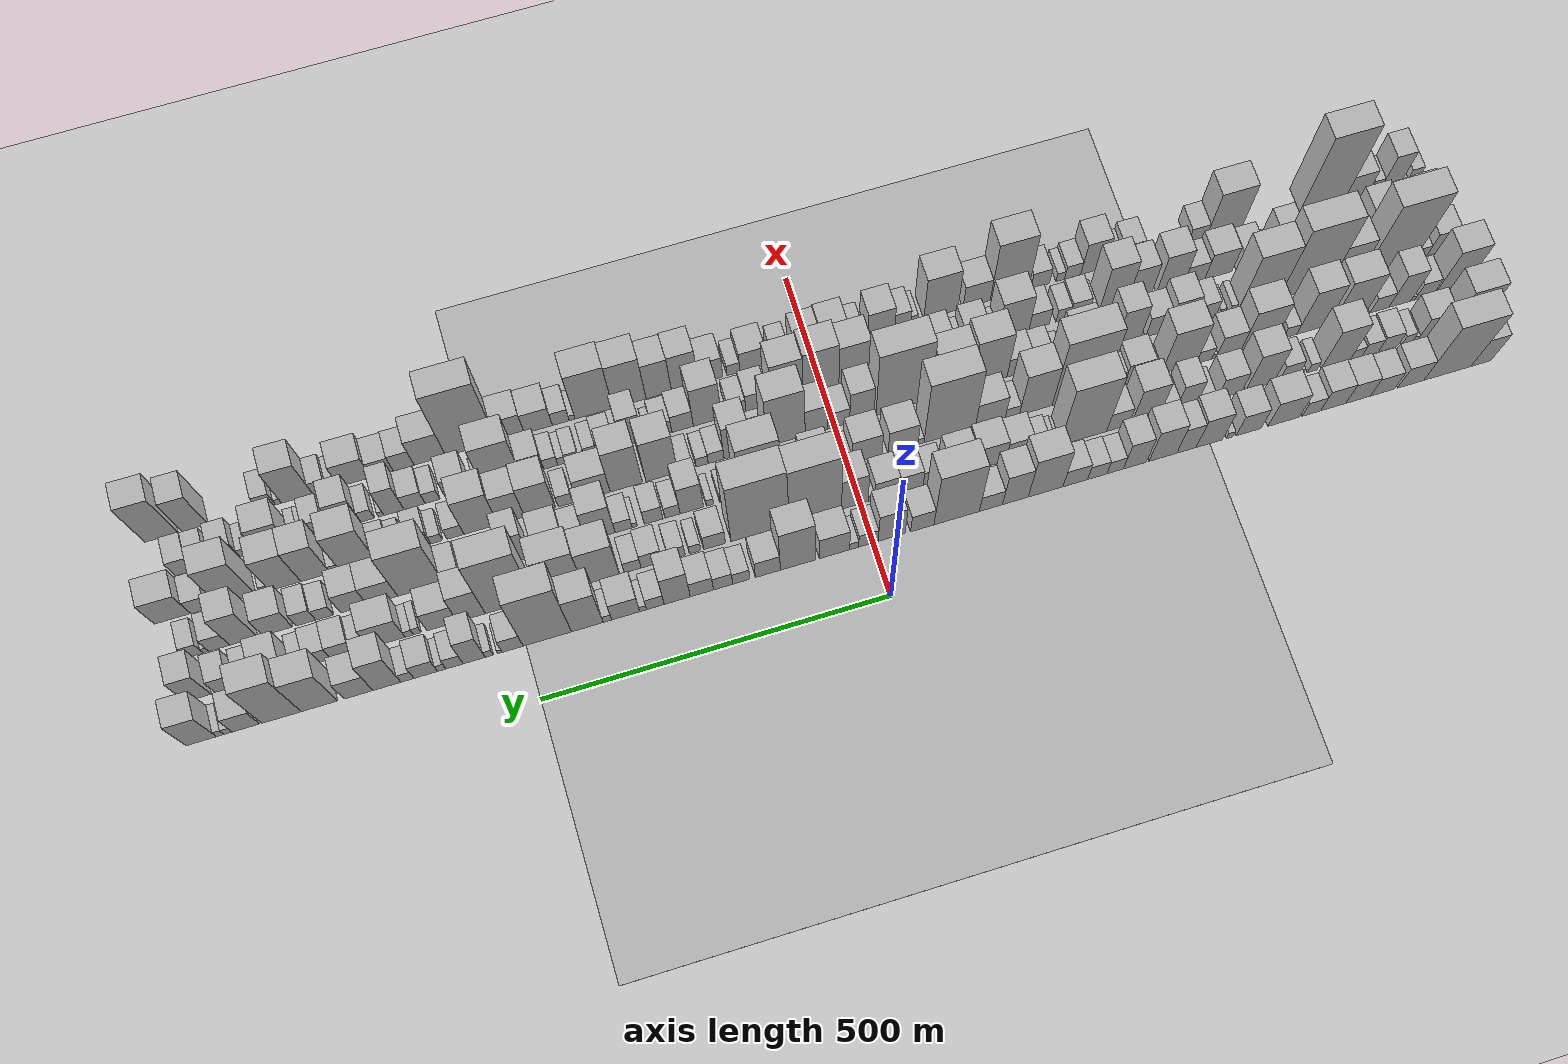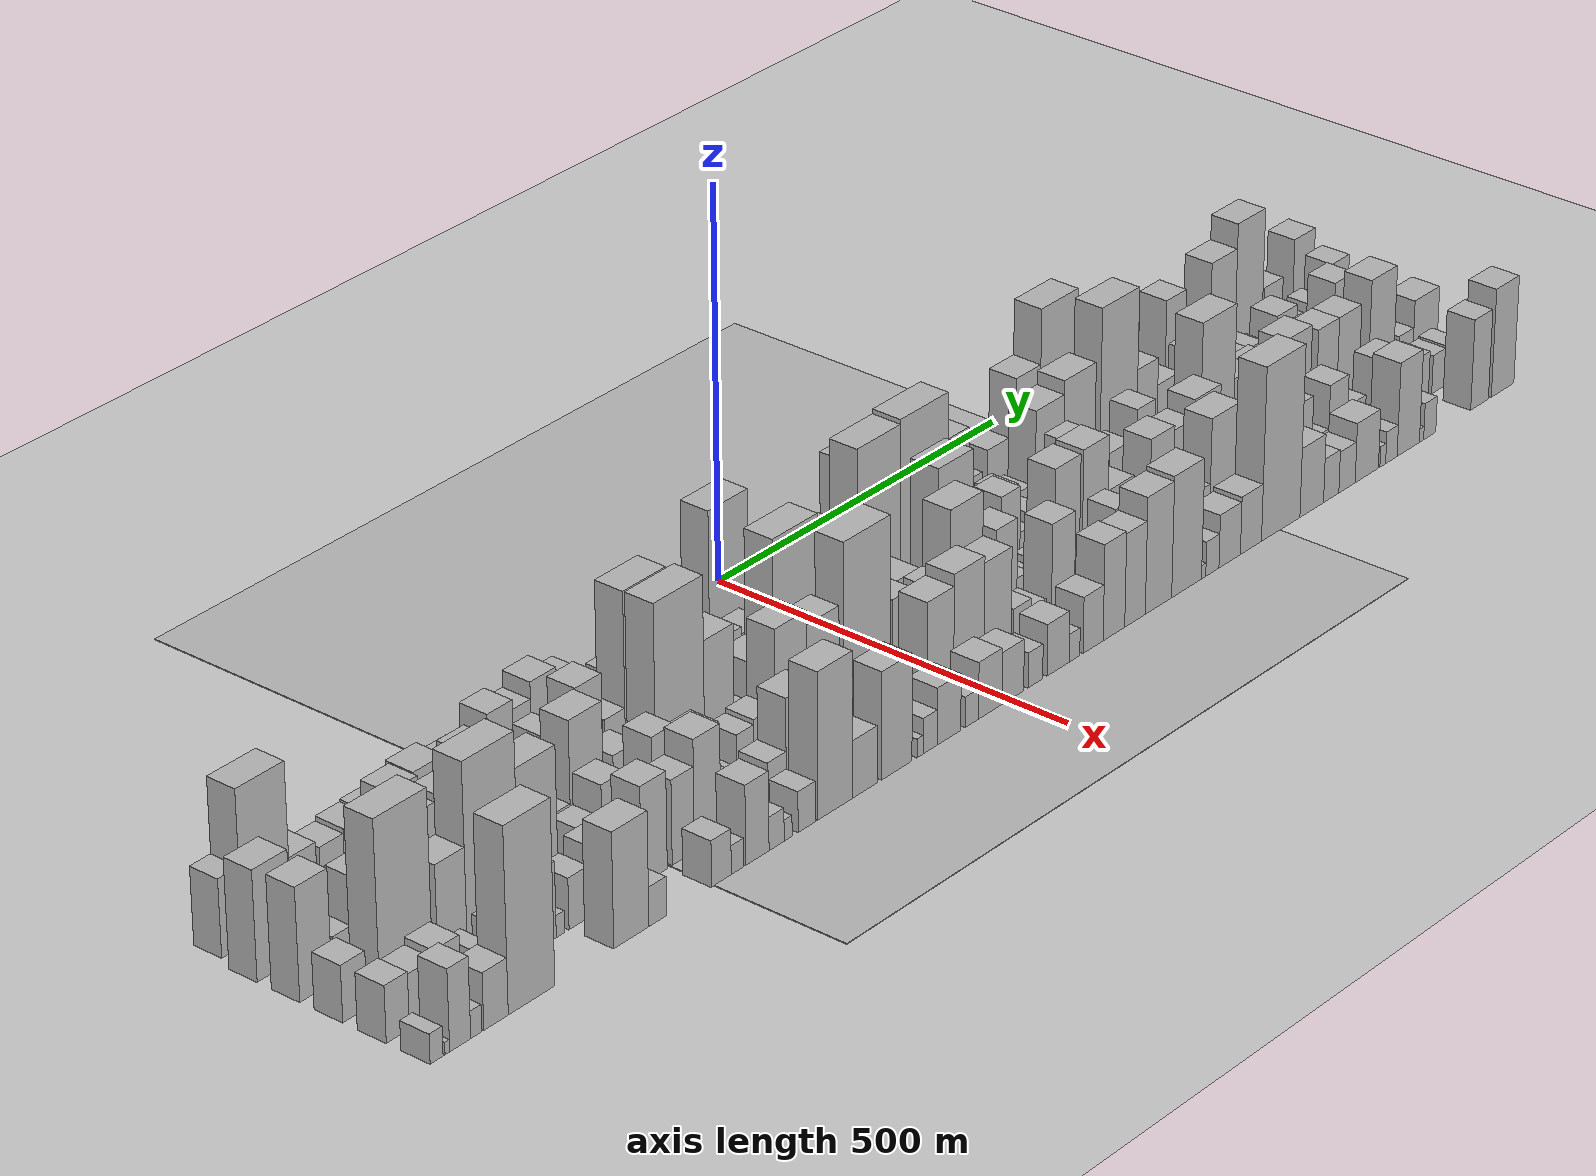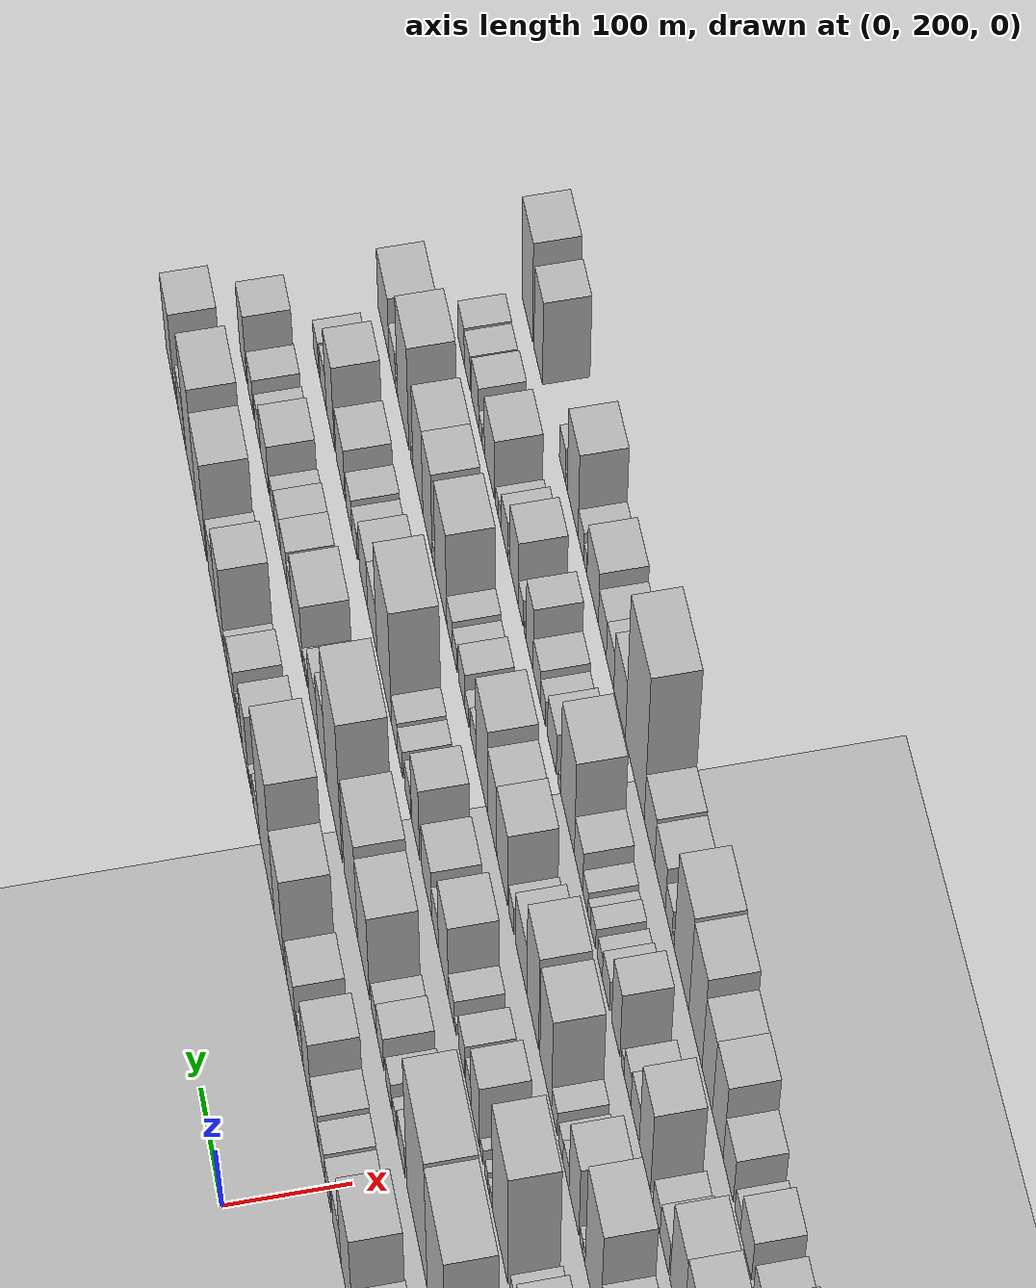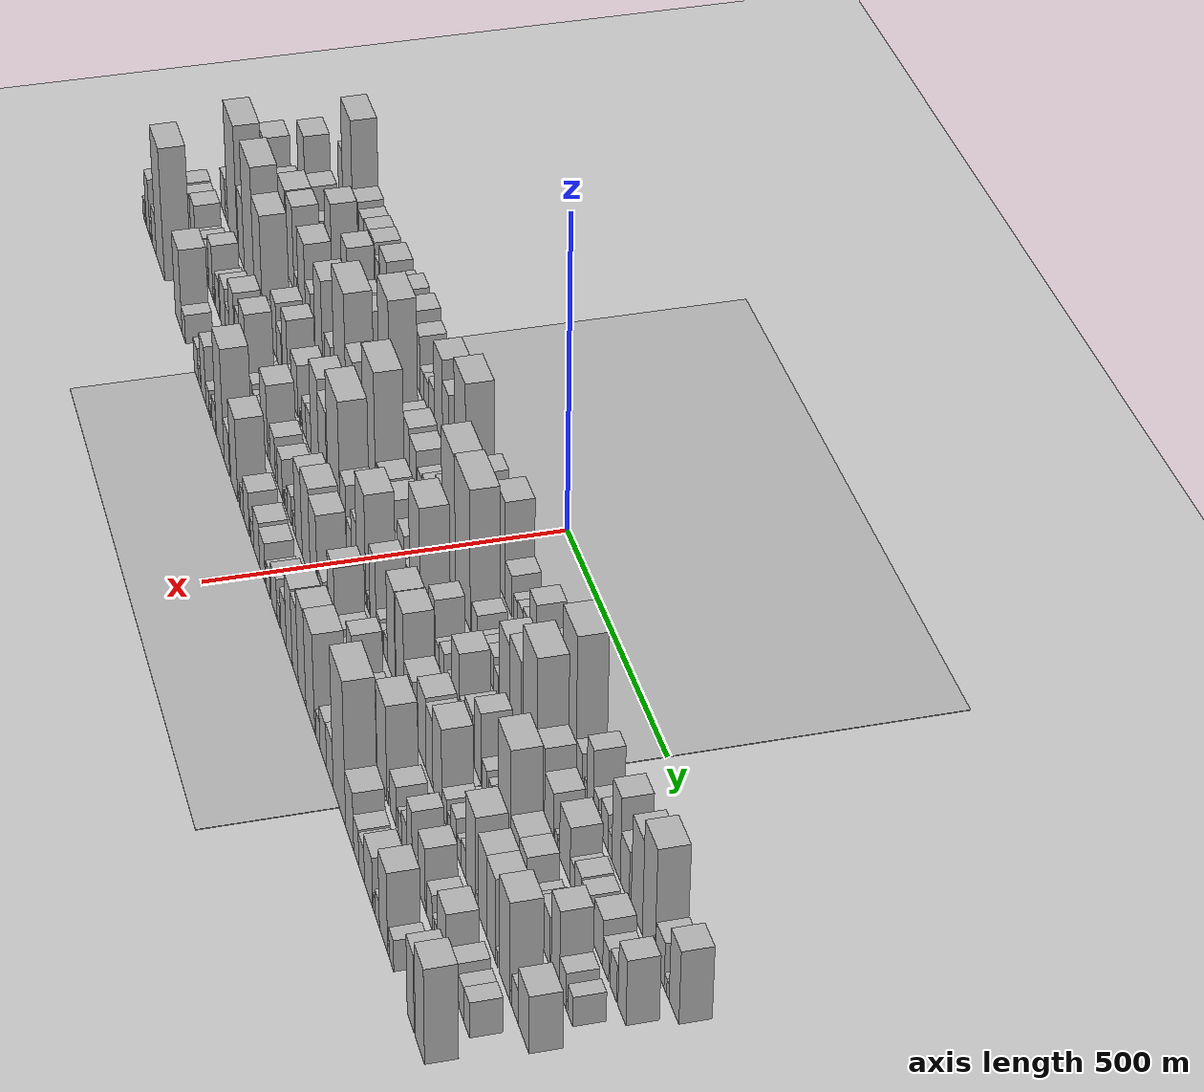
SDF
<?xml version="1.0" encoding="utf-8"?>

<sdf version="1.6">

   <world name="default">

      <gui fullscreen="0">

         <camera name="user_camera">

            <pose>-15 0 4.57585 0 0 0</pose>

            <view_controller>orbit</view_controller>

         </camera>

      </gui>

      <scene>

         <sky>

           <clouds>

             <speed>12</speed>

           </clouds>

         </sky>

         <ambient>0.4 0.4 0.4 1</ambient>

         <background>0.7 0.7 0.7 1</background>

         <shadows>1</shadows>

      </scene>

      <gravity>0 0 -9.8066</gravity>

      <magnetic_field>6e-06 2.3e-05 -4.2e-05</magnetic_field>

      <physics default="0" name="default_physics" type="ode">

         <ode>

            <solver>

               <type>quick</type>

               <iters>10</iters>

               <sor>1.0</sor>

               <use_dynamic_moi_rescaling>0</use_dynamic_moi_rescaling>

            </solver>

            <constraints>

               <cfm>0</cfm>

               <erp>0.2</erp>

               <contact_max_correcting_vel>100</contact_max_correcting_vel>

               <contact_surface_layer>0.001</contact_surface_layer>

            </constraints>

         </ode>

         <max_step_size>0.004</max_step_size>

         <real_time_factor>1</real_time_factor>

         <real_time_update_rate>250</real_time_update_rate>

      </physics>

      <light name="sun" type="directional">

         <cast_shadows>1</cast_shadows>

         <pose>0 0 10 0 0 0</pose>

         <diffuse>0.8 0.8 0.8 1</diffuse>

         <specular>0.2 0.2 0.2 1</specular>

         <attenuation>

            <range>1000</range>

            <constant>0.9</constant>

            <linear>0.01</linear>

            <quadratic>0.001</quadratic>

         </attenuation>

         <direction>-0.5 0.1 -0.9</direction>

      </light>

      <include>

         <name>ground_plane_1</name>

         <uri>model://HANNAS_ground_plane</uri>

         <pose>0 0 0  0 0 0</pose>

      </include>

      <include>

         <name>ground_plane_2</name>

         <uri>model://HANNAS_ground_plane</uri>

         <pose>100 0 0  0 0 0</pose>

      </include>

      <model name="building_1">

         <static>1</static>

         <pose frame="">100.0000 -914.4034 0 0.000000 0.000000 0.000000</pose>

         <link name="link">

            <pose frame="">0 0 48.00 0 0 0</pose>

            <collision name="collision">

               <geometry>

                  <box>

                     <size>40.0000 31.1931 96.0000</size>

                  </box>

               </geometry>

               <max_contacts>10</max_contacts>

               <surface>

                  <contact>

                     <ode/>

                  </contact>

                  <bounce/>

                  <friction>

                     <torsional>

                        <ode/>

                     </torsional>

                     <ode/>

                  </friction>

               </surface>

            </collision>

            <visual name="visual">

               <cast_shadows>0</cast_shadows>

               <geometry>

                  <box>

                     <size>40.0000 31.1931 96.0000</size>

                  </box>

               </geometry>

               <material>

                  <script>

                     <uri>model://HANNAS_wall/materials/scripts</uri>

                     <uri>model://HANNAS_wall/materials/textures</uri>

                     <name>vrc/HANNAS_wall</name>

                  </script>

               </material>

            </visual>

            <self_collide>0</self_collide>

            <enable_wind>0</enable_wind>

            <kinematic>0</kinematic>

         </link>

      </model>

      <model name="building_2">

         <static>1</static>

         <pose frame="">100.0000 -862.4962 0 0.000000 0.000000 0.000000</pose>

         <link name="link">

            <pose frame="">0 0 94.50 0 0 0</pose>

            <collision name="collision">

               <geometry>

                  <box>

                     <size>40.0000 72.6214 189.0000</size>

                  </box>

               </geometry>

               <max_contacts>10</max_contacts>

               <surface>

                  <contact>

                     <ode/>

                  </contact>

                  <bounce/>

                  <friction>

                     <torsional>

                        <ode/>

                     </torsional>

                     <ode/>

                  </friction>

               </surface>

            </collision>

            <visual name="visual">

               <cast_shadows>0</cast_shadows>

               <geometry>

                  <box>

                     <size>40.0000 72.6214 189.0000</size>

                  </box>

               </geometry>

               <material>

                  <script>

                     <uri>model://HANNAS_wall/materials/scripts</uri>

                     <uri>model://HANNAS_wall/materials/textures</uri>

                     <name>vrc/HANNAS_wall</name>

                  </script>

               </material>

            </visual>

            <self_collide>0</self_collide>

            <enable_wind>0</enable_wind>

            <kinematic>0</kinematic>

         </link>

      </model>

      <model name="building_3">

         <static>1</static>

         <pose frame="">100.0000 -806.0495 0 0.000000 0.000000 0.000000</pose>

         <link name="link">

            <pose frame="">0 0 36.00 0 0 0</pose>

            <collision name="collision">

               <geometry>

                  <box>

                     <size>40.0000 40.2719 72.0000</size>

                  </box>

               </geometry>

               <max_contacts>10</max_contacts>

               <surface>

                  <contact>

                     <ode/>

                  </contact>

                  <bounce/>

                  <friction>

                     <torsional>

                        <ode/>

                     </torsional>

                     <ode/>

                  </friction>

               </surface>

            </collision>

            <visual name="visual">

               <cast_shadows>0</cast_shadows>

               <geometry>

                  <box>

                     <size>40.0000 40.2719 72.0000</size>

                  </box>

               </geometry>

               <material>

                  <script>

                     <uri>model://HANNAS_wall/materials/scripts</uri>

                     <uri>model://HANNAS_wall/materials/textures</uri>

                     <name>vrc/HANNAS_wall</name>

                  </script>

               </material>

            </visual>

            <self_collide>0</self_collide>

            <enable_wind>0</enable_wind>

            <kinematic>0</kinematic>

         </link>

      </model>

      <model name="building_4">

         <static>1</static>

         <pose frame="">100.0000 -762.6138 0 0.000000 0.000000 0.000000</pose>

         <link name="link">

            <pose frame="">0 0 31.50 0 0 0</pose>

            <collision name="collision">

               <geometry>

                  <box>

                     <size>40.0000 36.5996 63.0000</size>

                  </box>

               </geometry>

               <max_contacts>10</max_contacts>

               <surface>

                  <contact>

                     <ode/>

                  </contact>

                  <bounce/>

                  <friction>

                     <torsional>

                        <ode/>

                     </torsional>

                     <ode/>

                  </friction>

               </surface>

            </collision>

            <visual name="visual">

               <cast_shadows>0</cast_shadows>

               <geometry>

                  <box>

                     <size>40.0000 36.5996 63.0000</size>

                  </box>

               </geometry>

               <material>

                  <script>

                     <uri>model://HANNAS_wall/materials/scripts</uri>

                     <uri>model://HANNAS_wall/materials/textures</uri>

                     <name>vrc/HANNAS_wall</name>

                  </script>

               </material>

            </visual>

            <self_collide>0</self_collide>

            <enable_wind>0</enable_wind>

            <kinematic>0</kinematic>

         </link>

      </model>

      <model name="building_5">

         <static>1</static>

         <pose frame="">100.0000 -725.5601 0 0.000000 0.000000 0.000000</pose>

         <link name="link">

            <pose frame="">0 0 34.50 0 0 0</pose>

            <collision name="collision">

               <geometry>

                  <box>

                     <size>40.0000 37.5077 69.0000</size>

                  </box>

               </geometry>

               <max_contacts>10</max_contacts>

               <surface>

                  <contact>

                     <ode/>

                  </contact>

                  <bounce/>

                  <friction>

                     <torsional>

                        <ode/>

                     </torsional>

                     <ode/>

                  </friction>

               </surface>

            </collision>

            <visual name="visual">

               <cast_shadows>0</cast_shadows>

               <geometry>

                  <box>

                     <size>40.0000 37.5077 69.0000</size>

                  </box>

               </geometry>

               <material>

                  <script>

                     <uri>model://HANNAS_wall/materials/scripts</uri>

                     <uri>model://HANNAS_wall/materials/textures</uri>

                     <name>vrc/HANNAS_wall</name>

                  </script>

               </material>

            </visual>

            <self_collide>0</self_collide>

            <enable_wind>0</enable_wind>

            <kinematic>0</kinematic>

         </link>

      </model>

      <model name="building_6">

         <static>1</static>

         <pose frame="">100.0000 -687.4740 0 0.000000 0.000000 0.000000</pose>

         <link name="link">

            <pose frame="">0 0 36.00 0 0 0</pose>

            <collision name="collision">

               <geometry>

                  <box>

                     <size>40.0000 38.6645 72.0000</size>

                  </box>

               </geometry>

               <max_contacts>10</max_contacts>

               <surface>

                  <contact>

                     <ode/>

                  </contact>

                  <bounce/>

                  <friction>

                     <torsional>

                        <ode/>

                     </torsional>

                     <ode/>

                  </friction>

               </surface>

            </collision>

            <visual name="visual">

               <cast_shadows>0</cast_shadows>

               <geometry>

                  <box>

                     <size>40.0000 38.6645 72.0000</size>

                  </box>

               </geometry>

               <material>

                  <script>

                     <uri>model://HANNAS_wall/materials/scripts</uri>

                     <uri>model://HANNAS_wall/materials/textures</uri>

                     <name>vrc/HANNAS_wall</name>

                  </script>

               </material>

            </visual>

            <self_collide>0</self_collide>

            <enable_wind>0</enable_wind>

            <kinematic>0</kinematic>

         </link>

      </model>

      <model name="building_7">

         <static>1</static>

         <pose frame="">100.0000 -654.0015 0 0.000000 0.000000 0.000000</pose>

         <link name="link">

            <pose frame="">0 0 25.50 0 0 0</pose>

            <collision name="collision">

               <geometry>

                  <box>

                     <size>40.0000 28.2803 51.0000</size>

                  </box>

               </geometry>

               <max_contacts>10</max_contacts>

               <surface>

                  <contact>

                     <ode/>

                  </contact>

                  <bounce/>

                  <friction>

                     <torsional>

                        <ode/>

                     </torsional>

                     <ode/>

                  </friction>

               </surface>

            </collision>

            <visual name="visual">

               <cast_shadows>0</cast_shadows>

               <geometry>

                  <box>

                     <size>40.0000 28.2803 51.0000</size>

                  </box>

               </geometry>

               <material>

                  <script>

                     <uri>model://HANNAS_wall/materials/scripts</uri>

                     <uri>model://HANNAS_wall/materials/textures</uri>

                     <name>vrc/HANNAS_wall</name>

                  </script>

               </material>

            </visual>

            <self_collide>0</self_collide>

            <enable_wind>0</enable_wind>

            <kinematic>0</kinematic>

         </link>

      </model>

      <model name="building_8">

         <static>1</static>

         <pose frame="">100.0000 -611.8724 0 0.000000 0.000000 0.000000</pose>

         <link name="link">

            <pose frame="">0 0 43.50 0 0 0</pose>

            <collision name="collision">

               <geometry>

                  <box>

                     <size>40.0000 47.9779 87.0000</size>

                  </box>

               </geometry>

               <max_contacts>10</max_contacts>

               <surface>

                  <contact>

                     <ode/>

                  </contact>

                  <bounce/>

                  <friction>

                     <torsional>

                        <ode/>

                     </torsional>

                     <ode/>

                  </friction>

               </surface>

            </collision>

            <visual name="visual">

               <cast_shadows>0</cast_shadows>

               <geometry>

                  <box>

                     <size>40.0000 47.9779 87.0000</size>

                  </box>

               </geometry>

               <material>

                  <script>

                     <uri>model://HANNAS_wall/materials/scripts</uri>

                     <uri>model://HANNAS_wall/materials/textures</uri>

                     <name>vrc/HANNAS_wall</name>

                  </script>

               </material>

            </visual>

            <self_collide>0</self_collide>

            <enable_wind>0</enable_wind>

            <kinematic>0</kinematic>

         </link>

      </model>

      <model name="building_9">

         <static>1</static>

         <pose frame="">100.0000 -558.8258 0 0.000000 0.000000 0.000000</pose>

         <link name="link">

            <pose frame="">0 0 37.50 0 0 0</pose>

            <collision name="collision">

               <geometry>

                  <box>

                     <size>40.0000 38.1154 75.0000</size>

                  </box>

               </geometry>

               <max_contacts>10</max_contacts>

               <surface>

                  <contact>

                     <ode/>

                  </contact>

                  <bounce/>

                  <friction>

                     <torsional>

                        <ode/>

                     </torsional>

                     <ode/>

                  </friction>

               </surface>

            </collision>

            <visual name="visual">

               <cast_shadows>0</cast_shadows>

               <geometry>

                  <box>

                     <size>40.0000 38.1154 75.0000</size>

                  </box>

               </geometry>

               <material>

                  <script>

                     <uri>model://HANNAS_wall/materials/scripts</uri>

                     <uri>model://HANNAS_wall/materials/textures</uri>

                     <name>vrc/HANNAS_wall</name>

                  </script>

               </material>

            </visual>

            <self_collide>0</self_collide>

            <enable_wind>0</enable_wind>

            <kinematic>0</kinematic>

         </link>

      </model>

      <model name="building_10">

         <static>1</static>

         <pose frame="">100.0000 -530.5697 0 0.000000 0.000000 0.000000</pose>

         <link name="link">

            <pose frame="">0 0 10.50 0 0 0</pose>

            <collision name="collision">

               <geometry>

                  <box>

                     <size>40.0000 10.3967 21.0000</size>

                  </box>

               </geometry>

               <max_contacts>10</max_contacts>

               <surface>

                  <contact>

                     <ode/>

                  </contact>

                  <bounce/>

                  <friction>

                     <torsional>

                        <ode/>

                     </torsional>

                     <ode/>

                  </friction>

               </surface>

            </collision>

            <visual name="visual">

               <cast_shadows>0</cast_shadows>

               <geometry>

                  <box>

                     <size>40.0000 10.3967 21.0000</size>

                  </box>

               </geometry>

               <material>

                  <script>

                     <uri>model://HANNAS_wall/materials/scripts</uri>

                     <uri>model://HANNAS_wall/materials/textures</uri>

                     <name>vrc/HANNAS_wall</name>

                  </script>

               </material>

            </visual>

            <self_collide>0</self_collide>

            <enable_wind>0</enable_wind>

            <kinematic>0</kinematic>

         </link>

      </model>

      <model name="building_11">

         <static>1</static>

         <pose frame="">100.0000 -499.3251 0 0.000000 0.000000 0.000000</pose>

         <link name="link">

            <pose frame="">0 0 52.50 0 0 0</pose>

            <collision name="collision">

               <geometry>

                  <box>

                     <size>40.0000 40.0925 105.0000</size>

                  </box>

               </geometry>

               <max_contacts>10</max_contacts>

               <surface>

                  <contact>

                     <ode/>

                  </contact>

                  <bounce/>

                  <friction>

                     <torsional>

                        <ode/>

                     </torsional>

                     <ode/>

                  </friction>

               </surface>

            </collision>

            <visual name="visual">

               <cast_shadows>0</cast_shadows>

               <geometry>

                  <box>

                     <size>40.0000 40.0925 105.0000</size>

                  </box>

               </geometry>

               <material>

                  <script>

                     <uri>model://HANNAS_wall/materials/scripts</uri>

                     <uri>model://HANNAS_wall/materials/textures</uri>

                     <name>vrc/HANNAS_wall</name>

                  </script>

               </material>

            </visual>

            <self_collide>0</self_collide>

            <enable_wind>0</enable_wind>

            <kinematic>0</kinematic>

         </link>

      </model>

      <model name="building_12">

         <static>1</static>

         <pose frame="">100.0000 -464.9103 0 0.000000 0.000000 0.000000</pose>

         <link name="link">

            <pose frame="">0 0 46.50 0 0 0</pose>

            <collision name="collision">

               <geometry>

                  <box>

                     <size>40.0000 28.7370 93.0000</size>

                  </box>

               </geometry>

               <max_contacts>10</max_contacts>

               <surface>

                  <contact>

                     <ode/>

                  </contact>

                  <bounce/>

                  <friction>

                     <torsional>

                        <ode/>

                     </torsional>

                     <ode/>

                  </friction>

               </surface>

            </collision>

            <visual name="visual">

               <cast_shadows>0</cast_shadows>

               <geometry>

                  <box>

                     <size>40.0000 28.7370 93.0000</size>

                  </box>

               </geometry>

               <material>

                  <script>

                     <uri>model://HANNAS_wall/materials/scripts</uri>

                     <uri>model://HANNAS_wall/materials/textures</uri>

                     <name>vrc/HANNAS_wall</name>

                  </script>

               </material>

            </visual>

            <self_collide>0</self_collide>

            <enable_wind>0</enable_wind>

            <kinematic>0</kinematic>

         </link>

      </model>

      <model name="building_13">

         <static>1</static>

         <pose frame="">100.0000 -429.5925 0 0.000000 0.000000 0.000000</pose>

         <link name="link">

            <pose frame="">0 0 57.00 0 0 0</pose>

            <collision name="collision">

               <geometry>

                  <box>

                     <size>40.0000 41.8985 114.0000</size>

                  </box>

               </geometry>

               <max_contacts>10</max_contacts>

               <surface>

                  <contact>

                     <ode/>

                  </contact>

                  <bounce/>

                  <friction>

                     <torsional>

                        <ode/>

                     </torsional>

                     <ode/>

                  </friction>

               </surface>

            </collision>

            <visual name="visual">

               <cast_shadows>0</cast_shadows>

               <geometry>

                  <box>

                     <size>40.0000 41.8985 114.0000</size>

                  </box>

               </geometry>

               <material>

                  <script>

                     <uri>model://HANNAS_wall/materials/scripts</uri>

                     <uri>model://HANNAS_wall/materials/textures</uri>

                     <name>vrc/HANNAS_wall</name>

                  </script>

               </material>

            </visual>

            <self_collide>0</self_collide>

            <enable_wind>0</enable_wind>

            <kinematic>0</kinematic>

         </link>

      </model>

      <model name="building_14">

         <static>1</static>

         <pose frame="">100.0000 -387.3747 0 0.000000 0.000000 0.000000</pose>

         <link name="link">

            <pose frame="">0 0 48.00 0 0 0</pose>

            <collision name="collision">

               <geometry>

                  <box>

                     <size>40.0000 34.5371 96.0000</size>

                  </box>

               </geometry>

               <max_contacts>10</max_contacts>

               <surface>

                  <contact>

                     <ode/>

                  </contact>

                  <bounce/>

                  <friction>

                     <torsional>

                        <ode/>

                     </torsional>

                     <ode/>

                  </friction>

               </surface>

            </collision>

            <visual name="visual">

               <cast_shadows>0</cast_shadows>

               <geometry>

                  <box>

                     <size>40.0000 34.5371 96.0000</size>

                  </box>

               </geometry>

               <material>

                  <script>

                     <uri>model://HANNAS_wall/materials/scripts</uri>

                     <uri>model://HANNAS_wall/materials/textures</uri>

                     <name>vrc/HANNAS_wall</name>

                  </script>

               </material>

            </visual>

            <self_collide>0</self_collide>

            <enable_wind>0</enable_wind>

            <kinematic>0</kinematic>

         </link>

      </model>

      <model name="building_15">

         <static>1</static>

         <pose frame="">100.0000 -357.9242 0 0.000000 0.000000 0.000000</pose>

         <link name="link">

            <pose frame="">0 0 24.00 0 0 0</pose>

            <collision name="collision">

               <geometry>

                  <box>

                     <size>40.0000 24.3640 48.0000</size>

                  </box>

               </geometry>

               <max_contacts>10</max_contacts>

               <surface>

                  <contact>

                     <ode/>

                  </contact>

                  <bounce/>

                  <friction>

                     <torsional>

                        <ode/>

                     </torsional>

                     <ode/>

                  </friction>

               </surface>

            </collision>

            <visual name="visual">

               <cast_shadows>0</cast_shadows>

               <geometry>

                  <box>

                     <size>40.0000 24.3640 48.0000</size>

                  </box>

               </geometry>

               <material>

                  <script>

                     <uri>model://HANNAS_wall/materials/scripts</uri>

                     <uri>model://HANNAS_wall/materials/textures</uri>

                     <name>vrc/HANNAS_wall</name>

                  </script>

               </material>

            </visual>

            <self_collide>0</self_collide>

            <enable_wind>0</enable_wind>

            <kinematic>0</kinematic>

         </link>

      </model>

      <model name="building_16">

         <static>1</static>

         <pose frame="">100.0000 -331.2372 0 0.000000 0.000000 0.000000</pose>

         <link name="link">

            <pose frame="">0 0 25.50 0 0 0</pose>

            <collision name="collision">

               <geometry>

                  <box>

                     <size>40.0000 29.0099 51.0000</size>

                  </box>

               </geometry>

               <max_contacts>10</max_contacts>

               <surface>

                  <contact>

                     <ode/>

                  </contact>

                  <bounce/>

                  <friction>

                     <torsional>

                        <ode/>

                     </torsional>

                     <ode/>

                  </friction>

               </surface>

            </collision>

            <visual name="visual">

               <cast_shadows>0</cast_shadows>

               <geometry>

                  <box>

                     <size>40.0000 29.0099 51.0000</size>

                  </box>

               </geometry>

               <material>

                  <script>

                     <uri>model://HANNAS_wall/materials/scripts</uri>

                     <uri>model://HANNAS_wall/materials/textures</uri>

                     <name>vrc/HANNAS_wall</name>

                  </script>

               </material>

            </visual>

            <self_collide>0</self_collide>

            <enable_wind>0</enable_wind>

            <kinematic>0</kinematic>

         </link>

      </model>

      <model name="building_17">

         <static>1</static>

         <pose frame="">100.0000 -298.3507 0 0.000000 0.000000 0.000000</pose>

         <link name="link">

            <pose frame="">0 0 31.50 0 0 0</pose>

            <collision name="collision">

               <geometry>

                  <box>

                     <size>40.0000 36.7631 63.0000</size>

                  </box>

               </geometry>

               <max_contacts>10</max_contacts>

               <surface>

                  <contact>

                     <ode/>

                  </contact>

                  <bounce/>

                  <friction>

                     <torsional>

                        <ode/>

                     </torsional>

                     <ode/>

                  </friction>

               </surface>

            </collision>

            <visual name="visual">

               <cast_shadows>0</cast_shadows>

               <geometry>

                  <box>

                     <size>40.0000 36.7631 63.0000</size>

                  </box>

               </geometry>

               <material>

                  <script>

                     <uri>model://HANNAS_wall/materials/scripts</uri>

                     <uri>model://HANNAS_wall/materials/textures</uri>

                     <name>vrc/HANNAS_wall</name>

                  </script>

               </material>

            </visual>

            <self_collide>0</self_collide>

            <enable_wind>0</enable_wind>

            <kinematic>0</kinematic>

         </link>

      </model>

      <model name="building_18">

         <static>1</static>

         <pose frame="">100.0000 -254.2141 0 0.000000 0.000000 0.000000</pose>

         <link name="link">

            <pose frame="">0 0 73.50 0 0 0</pose>

            <collision name="collision">

               <geometry>

                  <box>

                     <size>40.0000 51.5102 147.0000</size>

                  </box>

               </geometry>

               <max_contacts>10</max_contacts>

               <surface>

                  <contact>

                     <ode/>

                  </contact>

                  <bounce/>

                  <friction>

                     <torsional>

                        <ode/>

                     </torsional>

                     <ode/>

                  </friction>

               </surface>

            </collision>

            <visual name="visual">

               <cast_shadows>0</cast_shadows>

               <geometry>

                  <box>

                     <size>40.0000 51.5102 147.0000</size>

                  </box>

               </geometry>

               <material>

                  <script>

                     <uri>model://HANNAS_wall/materials/scripts</uri>

                     <uri>model://HANNAS_wall/materials/textures</uri>

                     <name>vrc/HANNAS_wall</name>

                  </script>

               </material>

            </visual>

            <self_collide>0</self_collide>

            <enable_wind>0</enable_wind>

            <kinematic>0</kinematic>

         </link>

      </model>

      <model name="building_19">

         <static>1</static>

         <pose frame="">100.0000 -209.4136 0 0.000000 0.000000 0.000000</pose>

         <link name="link">

            <pose frame="">0 0 57.00 0 0 0</pose>

            <collision name="collision">

               <geometry>

                  <box>

                     <size>40.0000 38.0908 114.0000</size>

                  </box>

               </geometry>

               <max_contacts>10</max_contacts>

               <surface>

                  <contact>

                     <ode/>

                  </contact>

                  <bounce/>

                  <friction>

                     <torsional>

                        <ode/>

                     </torsional>

                     <ode/>

                  </friction>

               </surface>

            </collision>

            <visual name="visual">

               <cast_shadows>0</cast_shadows>

               <geometry>

                  <box>

                     <size>40.0000 38.0908 114.0000</size>

                  </box>

               </geometry>

               <material>

                  <script>

                     <uri>model://HANNAS_wall/materials/scripts</uri>

                     <uri>model://HANNAS_wall/materials/textures</uri>

                     <name>vrc/HANNAS_wall</name>

                  </script>

               </material>

            </visual>

            <self_collide>0</self_collide>

            <enable_wind>0</enable_wind>

            <kinematic>0</kinematic>

         </link>

      </model>

      <model name="building_20">

         <static>1</static>

         <pose frame="">100.0000 -173.2493 0 0.000000 0.000000 0.000000</pose>

         <link name="link">

            <pose frame="">0 0 30.00 0 0 0</pose>

            <collision name="collision">

               <geometry>

                  <box>

                     <size>40.0000 34.2378 60.0000</size>

                  </box>

               </geometry>

               <max_contacts>10</max_contacts>

               <surface>

                  <contact>

                     <ode/>

                  </contact>

                  <bounce/>

                  <friction>

                     <torsional>

                        <ode/>

                     </torsional>

                     <ode/>

                  </friction>

               </surface>

            </collision>

            <visual name="visual">

               <cast_shadows>0</cast_shadows>

               <geometry>

                  <box>

                     <size>40.0000 34.2378 60.0000</size>

                  </box>

               </geometry>

               <material>

                  <script>

                     <uri>model://HANNAS_wall/materials/scripts</uri>

                     <uri>model://HANNAS_wall/materials/textures</uri>

                     <name>vrc/HANNAS_wall</name>

                  </script>

               </material>

            </visual>

            <self_collide>0</self_collide>

            <enable_wind>0</enable_wind>

            <kinematic>0</kinematic>

         </link>

      </model>

      <model name="building_21">

         <static>1</static>

         <pose frame="">100.0000 -122.6711 0 0.000000 0.000000 0.000000</pose>

         <link name="link">

            <pose frame="">0 0 99.00 0 0 0</pose>

            <collision name="collision">

               <geometry>

                  <box>

                     <size>40.0000 66.9186 198.0000</size>

                  </box>

               </geometry>

               <max_contacts>10</max_contacts>

               <surface>

                  <contact>

                     <ode/>

                  </contact>

                  <bounce/>

                  <friction>

                     <torsional>

                        <ode/>

                     </torsional>

                     <ode/>

                  </friction>

               </surface>

            </collision>

            <visual name="visual">

               <cast_shadows>0</cast_shadows>

               <geometry>

                  <box>

                     <size>40.0000 66.9186 198.0000</size>

                  </box>

               </geometry>

               <material>

                  <script>

                     <uri>model://HANNAS_wall/materials/scripts</uri>

                     <uri>model://HANNAS_wall/materials/textures</uri>

                     <name>vrc/HANNAS_wall</name>

                  </script>

               </material>

            </visual>

            <self_collide>0</self_collide>

            <enable_wind>0</enable_wind>

            <kinematic>0</kinematic>

         </link>

      </model>

      <model name="building_22">

         <static>1</static>

         <pose frame="">100.0000 -72.0140 0 0.000000 0.000000 0.000000</pose>

         <link name="link">

            <pose frame="">0 0 33.00 0 0 0</pose>

            <collision name="collision">

               <geometry>

                  <box>

                     <size>40.0000 34.3954 66.0000</size>

                  </box>

               </geometry>

               <max_contacts>10</max_contacts>

               <surface>

                  <contact>

                     <ode/>

                  </contact>

                  <bounce/>

                  <friction>

                     <torsional>

                        <ode/>

                     </torsional>

                     <ode/>

                  </friction>

               </surface>

            </collision>

            <visual name="visual">

               <cast_shadows>0</cast_shadows>

               <geometry>

                  <box>

                     <size>40.0000 34.3954 66.0000</size>

                  </box>

               </geometry>

               <material>

                  <script>

                     <uri>model://HANNAS_wall/materials/scripts</uri>

                     <uri>model://HANNAS_wall/materials/textures</uri>

                     <name>vrc/HANNAS_wall</name>

                  </script>

               </material>

            </visual>

            <self_collide>0</self_collide>

            <enable_wind>0</enable_wind>

            <kinematic>0</kinematic>

         </link>

      </model>

      <model name="building_23">

         <static>1</static>

         <pose frame="">100.0000 -27.0608 0 0.000000 0.000000 0.000000</pose>

         <link name="link">

            <pose frame="">0 0 54.00 0 0 0</pose>

            <collision name="collision">

               <geometry>

                  <box>

                     <size>40.0000 39.5110 108.0000</size>

                  </box>

               </geometry>

               <max_contacts>10</max_contacts>

               <surface>

                  <contact>

                     <ode/>

                  </contact>

                  <bounce/>

                  <friction>

                     <torsional>

                        <ode/>

                     </torsional>

                     <ode/>

                  </friction>

               </surface>

            </collision>

            <visual name="visual">

               <cast_shadows>0</cast_shadows>

               <geometry>

                  <box>

                     <size>40.0000 39.5110 108.0000</size>

                  </box>

               </geometry>

               <material>

                  <script>

                     <uri>model://HANNAS_wall/materials/scripts</uri>

                     <uri>model://HANNAS_wall/materials/textures</uri>

                     <name>vrc/HANNAS_wall</name>

                  </script>

               </material>

            </visual>

            <self_collide>0</self_collide>

            <enable_wind>0</enable_wind>

            <kinematic>0</kinematic>

         </link>

      </model>

      <model name="building_24">

         <static>1</static>

         <pose frame="">100.0000 6.9616 0 0.000000 0.000000 0.000000</pose>

         <link name="link">

            <pose frame="">0 0 25.50 0 0 0</pose>

            <collision name="collision">

               <geometry>

                  <box>

                     <size>40.0000 28.5338 51.0000</size>

                  </box>

               </geometry>

               <max_contacts>10</max_contacts>

               <surface>

                  <contact>

                     <ode/>

                  </contact>

                  <bounce/>

                  <friction>

                     <torsional>

                        <ode/>

                     </torsional>

                     <ode/>

                  </friction>

               </surface>

            </collision>

            <visual name="visual">

               <cast_shadows>0</cast_shadows>

               <geometry>

                  <box>

                     <size>40.0000 28.5338 51.0000</size>

                  </box>

               </geometry>

               <material>

                  <script>

                     <uri>model://HANNAS_wall/materials/scripts</uri>

                     <uri>model://HANNAS_wall/materials/textures</uri>

                     <name>vrc/HANNAS_wall</name>

                  </script>

               </material>

            </visual>

            <self_collide>0</self_collide>

            <enable_wind>0</enable_wind>

            <kinematic>0</kinematic>

         </link>

      </model>

      <model name="building_25">

         <static>1</static>

         <pose frame="">100.0000 27.7812 0 0.000000 0.000000 0.000000</pose>

         <link name="link">

            <pose frame="">0 0 13.50 0 0 0</pose>

            <collision name="collision">

               <geometry>

                  <box>

                     <size>40.0000 13.1054 27.0000</size>

                  </box>

               </geometry>

               <max_contacts>10</max_contacts>

               <surface>

                  <contact>

                     <ode/>

                  </contact>

                  <bounce/>

                  <friction>

                     <torsional>

                        <ode/>

                     </torsional>

                     <ode/>

                  </friction>

               </surface>

            </collision>

            <visual name="visual">

               <cast_shadows>0</cast_shadows>

               <geometry>

                  <box>

                     <size>40.0000 13.1054 27.0000</size>

                  </box>

               </geometry>

               <material>

                  <script>

                     <uri>model://HANNAS_wall/materials/scripts</uri>

                     <uri>model://HANNAS_wall/materials/textures</uri>

                     <name>vrc/HANNAS_wall</name>

                  </script>

               </material>

            </visual>

            <self_collide>0</self_collide>

            <enable_wind>0</enable_wind>

            <kinematic>0</kinematic>

         </link>

      </model>

      <model name="building_26">

         <static>1</static>

         <pose frame="">100.0000 56.3703 0 0.000000 0.000000 0.000000</pose>

         <link name="link">

            <pose frame="">0 0 42.00 0 0 0</pose>

            <collision name="collision">

               <geometry>

                  <box>

                     <size>40.0000 44.0729 84.0000</size>

                  </box>

               </geometry>

               <max_contacts>10</max_contacts>

               <surface>

                  <contact>

                     <ode/>

                  </contact>

                  <bounce/>

                  <friction>

                     <torsional>

                        <ode/>

                     </torsional>

                     <ode/>

                  </friction>

               </surface>

            </collision>

            <visual name="visual">

               <cast_shadows>0</cast_shadows>

               <geometry>

                  <box>

                     <size>40.0000 44.0729 84.0000</size>

                  </box>

               </geometry>

               <material>

                  <script>

                     <uri>model://HANNAS_wall/materials/scripts</uri>

                     <uri>model://HANNAS_wall/materials/textures</uri>

                     <name>vrc/HANNAS_wall</name>

                  </script>

               </material>

            </visual>

            <self_collide>0</self_collide>

            <enable_wind>0</enable_wind>

            <kinematic>0</kinematic>

         </link>

      </model>

      <model name="building_27">

         <static>1</static>

         <pose frame="">100.0000 109.1846 0 0.000000 0.000000 0.000000</pose>

         <link name="link">

            <pose frame="">0 0 79.50 0 0 0</pose>

            <collision name="collision">

               <geometry>

                  <box>

                     <size>40.0000 51.5556 159.0000</size>

                  </box>

               </geometry>

               <max_contacts>10</max_contacts>

               <surface>

                  <contact>

                     <ode/>

                  </contact>

                  <bounce/>

                  <friction>

                     <torsional>

                        <ode/>

                     </torsional>

                     <ode/>

                  </friction>

               </surface>

            </collision>

            <visual name="visual">

               <cast_shadows>0</cast_shadows>

               <geometry>

                  <box>

                     <size>40.0000 51.5556 159.0000</size>

                  </box>

               </geometry>

               <material>

                  <script>

                     <uri>model://HANNAS_wall/materials/scripts</uri>

                     <uri>model://HANNAS_wall/materials/textures</uri>

                     <name>vrc/HANNAS_wall</name>

                  </script>

               </material>

            </visual>

            <self_collide>0</self_collide>

            <enable_wind>0</enable_wind>

            <kinematic>0</kinematic>

         </link>

      </model>

      <model name="building_28">

         <static>1</static>

         <pose frame="">100.0000 153.1105 0 0.000000 0.000000 0.000000</pose>

         <link name="link">

            <pose frame="">0 0 33.00 0 0 0</pose>

            <collision name="collision">

               <geometry>

                  <box>

                     <size>40.0000 36.2963 66.0000</size>

                  </box>

               </geometry>

               <max_contacts>10</max_contacts>

               <surface>

                  <contact>

                     <ode/>

                  </contact>

                  <bounce/>

                  <friction>

                     <torsional>

                        <ode/>

                     </torsional>

                     <ode/>

                  </friction>

               </surface>

            </collision>

            <visual name="visual">

               <cast_shadows>0</cast_shadows>

               <geometry>

                  <box>

                     <size>40.0000 36.2963 66.0000</size>

                  </box>

               </geometry>

               <material>

                  <script>

                     <uri>model://HANNAS_wall/materials/scripts</uri>

                     <uri>model://HANNAS_wall/materials/textures</uri>

                     <name>vrc/HANNAS_wall</name>

                  </script>

               </material>

            </visual>

            <self_collide>0</self_collide>

            <enable_wind>0</enable_wind>

            <kinematic>0</kinematic>

         </link>

      </model>

      <model name="building_29">

         <static>1</static>

         <pose frame="">100.0000 191.5842 0 0.000000 0.000000 0.000000</pose>

         <link name="link">

            <pose frame="">0 0 22.50 0 0 0</pose>

            <collision name="collision">

               <geometry>

                  <box>

                     <size>40.0000 24.6511 45.0000</size>

                  </box>

               </geometry>

               <max_contacts>10</max_contacts>

               <surface>

                  <contact>

                     <ode/>

                  </contact>

                  <bounce/>

                  <friction>

                     <torsional>

                        <ode/>

                     </torsional>

                     <ode/>

                  </friction>

               </surface>

            </collision>

            <visual name="visual">

               <cast_shadows>0</cast_shadows>

               <geometry>

                  <box>

                     <size>40.0000 24.6511 45.0000</size>

                  </box>

               </geometry>

               <material>

                  <script>

                     <uri>model://HANNAS_wall/materials/scripts</uri>

                     <uri>model://HANNAS_wall/materials/textures</uri>

                     <name>vrc/HANNAS_wall</name>

                  </script>

               </material>

            </visual>

            <self_collide>0</self_collide>

            <enable_wind>0</enable_wind>

            <kinematic>0</kinematic>

         </link>

      </model>

      <model name="building_30">

         <static>1</static>

         <pose frame="">100.0000 217.8195 0 0.000000 0.000000 0.000000</pose>

         <link name="link">

            <pose frame="">0 0 25.50 0 0 0</pose>

            <collision name="collision">

               <geometry>

                  <box>

                     <size>40.0000 27.8194 51.0000</size>

                  </box>

               </geometry>

               <max_contacts>10</max_contacts>

               <surface>

                  <contact>

                     <ode/>

                  </contact>

                  <bounce/>

                  <friction>

                     <torsional>

                        <ode/>

                     </torsional>

                     <ode/>

                  </friction>

               </surface>

            </collision>

            <visual name="visual">

               <cast_shadows>0</cast_shadows>

               <geometry>

                  <box>

                     <size>40.0000 27.8194 51.0000</size>

                  </box>

               </geometry>

               <material>

                  <script>

                     <uri>model://HANNAS_wall/materials/scripts</uri>

                     <uri>model://HANNAS_wall/materials/textures</uri>

                     <name>vrc/HANNAS_wall</name>

                  </script>

               </material>

            </visual>

            <self_collide>0</self_collide>

            <enable_wind>0</enable_wind>

            <kinematic>0</kinematic>

         </link>

      </model>

      <model name="building_31">

         <static>1</static>

         <pose frame="">100.0000 248.4720 0 0.000000 0.000000 0.000000</pose>

         <link name="link">

            <pose frame="">0 0 30.00 0 0 0</pose>

            <collision name="collision">

               <geometry>

                  <box>

                     <size>40.0000 33.4856 60.0000</size>

                  </box>

               </geometry>

               <max_contacts>10</max_contacts>

               <surface>

                  <contact>

                     <ode/>

                  </contact>

                  <bounce/>

                  <friction>

                     <torsional>

                        <ode/>

                     </torsional>

                     <ode/>

                  </friction>

               </surface>

            </collision>

            <visual name="visual">

               <cast_shadows>0</cast_shadows>

               <geometry>

                  <box>

                     <size>40.0000 33.4856 60.0000</size>

                  </box>

               </geometry>

               <material>

                  <script>

                     <uri>model://HANNAS_wall/materials/scripts</uri>

                     <uri>model://HANNAS_wall/materials/textures</uri>

                     <name>vrc/HANNAS_wall</name>

                  </script>

               </material>

            </visual>

            <self_collide>0</self_collide>

            <enable_wind>0</enable_wind>

            <kinematic>0</kinematic>

         </link>

      </model>

      <model name="building_32">

         <static>1</static>

         <pose frame="">100.0000 283.9179 0 0.000000 0.000000 0.000000</pose>

         <link name="link">

            <pose frame="">0 0 57.00 0 0 0</pose>

            <collision name="collision">

               <geometry>

                  <box>

                     <size>40.0000 37.4060 114.0000</size>

                  </box>

               </geometry>

               <max_contacts>10</max_contacts>

               <surface>

                  <contact>

                     <ode/>

                  </contact>

                  <bounce/>

                  <friction>

                     <torsional>

                        <ode/>

                     </torsional>

                     <ode/>

                  </friction>

               </surface>

            </collision>

            <visual name="visual">

               <cast_shadows>0</cast_shadows>

               <geometry>

                  <box>

                     <size>40.0000 37.4060 114.0000</size>

                  </box>

               </geometry>

               <material>

                  <script>

                     <uri>model://HANNAS_wall/materials/scripts</uri>

                     <uri>model://HANNAS_wall/materials/textures</uri>

                     <name>vrc/HANNAS_wall</name>

                  </script>

               </material>

            </visual>

            <self_collide>0</self_collide>

            <enable_wind>0</enable_wind>

            <kinematic>0</kinematic>

         </link>

      </model>

      <model name="building_33">

         <static>1</static>

         <pose frame="">100.0000 315.3437 0 0.000000 0.000000 0.000000</pose>

         <link name="link">

            <pose frame="">0 0 22.50 0 0 0</pose>

            <collision name="collision">

               <geometry>

                  <box>

                     <size>40.0000 25.4457 45.0000</size>

                  </box>

               </geometry>

               <max_contacts>10</max_contacts>

               <surface>

                  <contact>

                     <ode/>

                  </contact>

                  <bounce/>

                  <friction>

                     <torsional>

                        <ode/>

                     </torsional>

                     <ode/>

                  </friction>

               </surface>

            </collision>

            <visual name="visual">

               <cast_shadows>0</cast_shadows>

               <geometry>

                  <box>

                     <size>40.0000 25.4457 45.0000</size>

                  </box>

               </geometry>

               <material>

                  <script>

                     <uri>model://HANNAS_wall/materials/scripts</uri>

                     <uri>model://HANNAS_wall/materials/textures</uri>

                     <name>vrc/HANNAS_wall</name>

                  </script>

               </material>

            </visual>

            <self_collide>0</self_collide>

            <enable_wind>0</enable_wind>

            <kinematic>0</kinematic>

         </link>

      </model>

      <model name="building_34">

         <static>1</static>

         <pose frame="">100.0000 332.9142 0 0.000000 0.000000 0.000000</pose>

         <link name="link">

            <pose frame="">0 0 10.50 0 0 0</pose>

            <collision name="collision">

               <geometry>

                  <box>

                     <size>40.0000 9.6953 21.0000</size>

                  </box>

               </geometry>

               <max_contacts>10</max_contacts>

               <surface>

                  <contact>

                     <ode/>

                  </contact>

                  <bounce/>

                  <friction>

                     <torsional>

                        <ode/>

                     </torsional>

                     <ode/>

                  </friction>

               </surface>

            </collision>

            <visual name="visual">

               <cast_shadows>0</cast_shadows>

               <geometry>

                  <box>

                     <size>40.0000 9.6953 21.0000</size>

                  </box>

               </geometry>

               <material>

                  <script>

                     <uri>model://HANNAS_wall/materials/scripts</uri>

                     <uri>model://HANNAS_wall/materials/textures</uri>

                     <name>vrc/HANNAS_wall</name>

                  </script>

               </material>

            </visual>

            <self_collide>0</self_collide>

            <enable_wind>0</enable_wind>

            <kinematic>0</kinematic>

         </link>

      </model>

      <model name="building_35">

         <static>1</static>

         <pose frame="">100.0000 357.6976 0 0.000000 0.000000 0.000000</pose>

         <link name="link">

            <pose frame="">0 0 34.50 0 0 0</pose>

            <collision name="collision">

               <geometry>

                  <box>

                     <size>40.0000 39.8715 69.0000</size>

                  </box>

               </geometry>

               <max_contacts>10</max_contacts>

               <surface>

                  <contact>

                     <ode/>

                  </contact>

                  <bounce/>

                  <friction>

                     <torsional>

                        <ode/>

                     </torsional>

                     <ode/>

                  </friction>

               </surface>

            </collision>

            <visual name="visual">

               <cast_shadows>0</cast_shadows>

               <geometry>

                  <box>

                     <size>40.0000 39.8715 69.0000</size>

                  </box>

               </geometry>

               <material>

                  <script>

                     <uri>model://HANNAS_wall/materials/scripts</uri>

                     <uri>model://HANNAS_wall/materials/textures</uri>

                     <name>vrc/HANNAS_wall</name>

                  </script>

               </material>

            </visual>

            <self_collide>0</self_collide>

            <enable_wind>0</enable_wind>

            <kinematic>0</kinematic>

         </link>

      </model>

      <model name="building_36">

         <static>1</static>

         <pose frame="">100.0000 383.7980 0 0.000000 0.000000 0.000000</pose>

         <link name="link">

            <pose frame="">0 0 13.50 0 0 0</pose>

            <collision name="collision">

               <geometry>

                  <box>

                     <size>40.0000 12.3293 27.0000</size>

                  </box>

               </geometry>

               <max_contacts>10</max_contacts>

               <surface>

                  <contact>

                     <ode/>

                  </contact>

                  <bounce/>

                  <friction>

                     <torsional>

                        <ode/>

                     </torsional>

                     <ode/>

                  </friction>

               </surface>

            </collision>

            <visual name="visual">

               <cast_shadows>0</cast_shadows>

               <geometry>

                  <box>

                     <size>40.0000 12.3293 27.0000</size>

                  </box>

               </geometry>

               <material>

                  <script>

                     <uri>model://HANNAS_wall/materials/scripts</uri>

                     <uri>model://HANNAS_wall/materials/textures</uri>

                     <name>vrc/HANNAS_wall</name>

                  </script>

               </material>

            </visual>

            <self_collide>0</self_collide>

            <enable_wind>0</enable_wind>

            <kinematic>0</kinematic>

         </link>

      </model>

      <model name="building_37">

         <static>1</static>

         <pose frame="">100.0000 412.5606 0 0.000000 0.000000 0.000000</pose>

         <link name="link">

            <pose frame="">0 0 70.50 0 0 0</pose>

            <collision name="collision">

               <geometry>

                  <box>

                     <size>40.0000 45.1959 141.0000</size>

                  </box>

               </geometry>

               <max_contacts>10</max_contacts>

               <surface>

                  <contact>

                     <ode/>

                  </contact>

                  <bounce/>

                  <friction>

                     <torsional>

                        <ode/>

                     </torsional>

                     <ode/>

                  </friction>

               </surface>

            </collision>

            <visual name="visual">

               <cast_shadows>0</cast_shadows>

               <geometry>

                  <box>

                     <size>40.0000 45.1959 141.0000</size>

                  </box>

               </geometry>

               <material>

                  <script>

                     <uri>model://HANNAS_wall/materials/scripts</uri>

                     <uri>model://HANNAS_wall/materials/textures</uri>

                     <name>vrc/HANNAS_wall</name>

                  </script>

               </material>

            </visual>

            <self_collide>0</self_collide>

            <enable_wind>0</enable_wind>

            <kinematic>0</kinematic>

         </link>

      </model>

      <model name="building_38">

         <static>1</static>

         <pose frame="">100.0000 469.5665 0 0.000000 0.000000 0.000000</pose>

         <link name="link">

            <pose frame="">0 0 106.50 0 0 0</pose>

            <collision name="collision">

               <geometry>

                  <box>

                     <size>40.0000 68.8157 213.0000</size>

                  </box>

               </geometry>

               <max_contacts>10</max_contacts>

               <surface>

                  <contact>

                     <ode/>

                  </contact>

                  <bounce/>

                  <friction>

                     <torsional>

                        <ode/>

                     </torsional>

                     <ode/>

                  </friction>

               </surface>

            </collision>

            <visual name="visual">

               <cast_shadows>0</cast_shadows>

               <geometry>

                  <box>

                     <size>40.0000 68.8157 213.0000</size>

                  </box>

               </geometry>

               <material>

                  <script>

                     <uri>model://HANNAS_wall/materials/scripts</uri>

                     <uri>model://HANNAS_wall/materials/textures</uri>

                     <name>vrc/HANNAS_wall</name>

                  </script>

               </material>

            </visual>

            <self_collide>0</self_collide>

            <enable_wind>0</enable_wind>

            <kinematic>0</kinematic>

         </link>

      </model>

      <model name="building_39">

         <static>1</static>

         <pose frame="">100.0000 518.9852 0 0.000000 0.000000 0.000000</pose>

         <link name="link">

            <pose frame="">0 0 27.00 0 0 0</pose>

            <collision name="collision">

               <geometry>

                  <box>

                     <size>40.0000 30.0217 54.0000</size>

                  </box>

               </geometry>

               <max_contacts>10</max_contacts>

               <surface>

                  <contact>

                     <ode/>

                  </contact>

                  <bounce/>

                  <friction>

                     <torsional>

                        <ode/>

                     </torsional>

                     <ode/>

                  </friction>

               </surface>

            </collision>

            <visual name="visual">

               <cast_shadows>0</cast_shadows>

               <geometry>

                  <box>

                     <size>40.0000 30.0217 54.0000</size>

                  </box>

               </geometry>

               <material>

                  <script>

                     <uri>model://HANNAS_wall/materials/scripts</uri>

                     <uri>model://HANNAS_wall/materials/textures</uri>

                     <name>vrc/HANNAS_wall</name>

                  </script>

               </material>

            </visual>

            <self_collide>0</self_collide>

            <enable_wind>0</enable_wind>

            <kinematic>0</kinematic>

         </link>

      </model>

      <model name="building_40">

         <static>1</static>

         <pose frame="">100.0000 537.1029 0 0.000000 0.000000 0.000000</pose>

         <link name="link">

            <pose frame="">0 0 7.50 0 0 0</pose>

            <collision name="collision">

               <geometry>

                  <box>

                     <size>40.0000 6.2136 15.0000</size>

                  </box>

               </geometry>

               <max_contacts>10</max_contacts>

               <surface>

                  <contact>

                     <ode/>

                  </contact>

                  <bounce/>

                  <friction>

                     <torsional>

                        <ode/>

                     </torsional>

                     <ode/>

                  </friction>

               </surface>

            </collision>

            <visual name="visual">

               <cast_shadows>0</cast_shadows>

               <geometry>

                  <box>

                     <size>40.0000 6.2136 15.0000</size>

                  </box>

               </geometry>

               <material>

                  <script>

                     <uri>model://HANNAS_wall/materials/scripts</uri>

                     <uri>model://HANNAS_wall/materials/textures</uri>

                     <name>vrc/HANNAS_wall</name>

                  </script>

               </material>

            </visual>

            <self_collide>0</self_collide>

            <enable_wind>0</enable_wind>

            <kinematic>0</kinematic>

         </link>

      </model>

      <model name="building_41">

         <static>1</static>

         <pose frame="">100.0000 551.9933 0 0.000000 0.000000 0.000000</pose>

         <link name="link">

            <pose frame="">0 0 13.50 0 0 0</pose>

            <collision name="collision">

               <geometry>

                  <box>

                     <size>40.0000 11.5673 27.0000</size>

                  </box>

               </geometry>

               <max_contacts>10</max_contacts>

               <surface>

                  <contact>

                     <ode/>

                  </contact>

                  <bounce/>

                  <friction>

                     <torsional>

                        <ode/>

                     </torsional>

                     <ode/>

                  </friction>

               </surface>

            </collision>

            <visual name="visual">

               <cast_shadows>0</cast_shadows>

               <geometry>

                  <box>

                     <size>40.0000 11.5673 27.0000</size>

                  </box>

               </geometry>

               <material>

                  <script>

                     <uri>model://HANNAS_wall/materials/scripts</uri>

                     <uri>model://HANNAS_wall/materials/textures</uri>

                     <name>vrc/HANNAS_wall</name>

                  </script>

               </material>

            </visual>

            <self_collide>0</self_collide>

            <enable_wind>0</enable_wind>

            <kinematic>0</kinematic>

         </link>

      </model>

      <model name="building_42">

         <static>1</static>

         <pose frame="">100.0000 573.2846 0 0.000000 0.000000 0.000000</pose>

         <link name="link">

            <pose frame="">0 0 51.00 0 0 0</pose>

            <collision name="collision">

               <geometry>

                  <box>

                     <size>40.0000 31.0153 102.0000</size>

                  </box>

               </geometry>

               <max_contacts>10</max_contacts>

               <surface>

                  <contact>

                     <ode/>

                  </contact>

                  <bounce/>

                  <friction>

                     <torsional>

                        <ode/>

                     </torsional>

                     <ode/>

                  </friction>

               </surface>

            </collision>

            <visual name="visual">

               <cast_shadows>0</cast_shadows>

               <geometry>

                  <box>

                     <size>40.0000 31.0153 102.0000</size>

                  </box>

               </geometry>

               <material>

                  <script>

                     <uri>model://HANNAS_wall/materials/scripts</uri>

                     <uri>model://HANNAS_wall/materials/textures</uri>

                     <name>vrc/HANNAS_wall</name>

                  </script>

               </material>

            </visual>

            <self_collide>0</self_collide>

            <enable_wind>0</enable_wind>

            <kinematic>0</kinematic>

         </link>

      </model>

      <model name="building_43">

         <static>1</static>

         <pose frame="">100.0000 600.9570 0 0.000000 0.000000 0.000000</pose>

         <link name="link">

            <pose frame="">0 0 22.50 0 0 0</pose>

            <collision name="collision">

               <geometry>

                  <box>

                     <size>40.0000 24.3294 45.0000</size>

                  </box>

               </geometry>

               <max_contacts>10</max_contacts>

               <surface>

                  <contact>

                     <ode/>

                  </contact>

                  <bounce/>

                  <friction>

                     <torsional>

                        <ode/>

                     </torsional>

                     <ode/>

                  </friction>

               </surface>

            </collision>

            <visual name="visual">

               <cast_shadows>0</cast_shadows>

               <geometry>

                  <box>

                     <size>40.0000 24.3294 45.0000</size>

                  </box>

               </geometry>

               <material>

                  <script>

                     <uri>model://HANNAS_wall/materials/scripts</uri>

                     <uri>model://HANNAS_wall/materials/textures</uri>

                     <name>vrc/HANNAS_wall</name>

                  </script>

               </material>

            </visual>

            <self_collide>0</self_collide>

            <enable_wind>0</enable_wind>

            <kinematic>0</kinematic>

         </link>

      </model>

      <model name="building_44">

         <static>1</static>

         <pose frame="">100.0000 619.0629 0 0.000000 0.000000 0.000000</pose>

         <link name="link">

            <pose frame="">0 0 13.50 0 0 0</pose>

            <collision name="collision">

               <geometry>

                  <box>

                     <size>40.0000 11.8824 27.0000</size>

                  </box>

               </geometry>

               <max_contacts>10</max_contacts>

               <surface>

                  <contact>

                     <ode/>

                  </contact>

                  <bounce/>

                  <friction>

                     <torsional>

                        <ode/>

                     </torsional>

                     <ode/>

                  </friction>

               </surface>

            </collision>

            <visual name="visual">

               <cast_shadows>0</cast_shadows>

               <geometry>

                  <box>

                     <size>40.0000 11.8824 27.0000</size>

                  </box>

               </geometry>

               <material>

                  <script>

                     <uri>model://HANNAS_wall/materials/scripts</uri>

                     <uri>model://HANNAS_wall/materials/textures</uri>

                     <name>vrc/HANNAS_wall</name>

                  </script>

               </material>

            </visual>

            <self_collide>0</self_collide>

            <enable_wind>0</enable_wind>

            <kinematic>0</kinematic>

         </link>

      </model>

      <model name="building_45">

         <static>1</static>

         <pose frame="">100.0000 641.6522 0 0.000000 0.000000 0.000000</pose>

         <link name="link">

            <pose frame="">0 0 28.50 0 0 0</pose>

            <collision name="collision">

               <geometry>

                  <box>

                     <size>40.0000 33.2962 57.0000</size>

                  </box>

               </geometry>

               <max_contacts>10</max_contacts>

               <surface>

                  <contact>

                     <ode/>

                  </contact>

                  <bounce/>

                  <friction>

                     <torsional>

                        <ode/>

                     </torsional>

                     <ode/>

                  </friction>

               </surface>

            </collision>

            <visual name="visual">

               <cast_shadows>0</cast_shadows>

               <geometry>

                  <box>

                     <size>40.0000 33.2962 57.0000</size>

                  </box>

               </geometry>

               <material>

                  <script>

                     <uri>model://HANNAS_wall/materials/scripts</uri>

                     <uri>model://HANNAS_wall/materials/textures</uri>

                     <name>vrc/HANNAS_wall</name>

                  </script>

               </material>

            </visual>

            <self_collide>0</self_collide>

            <enable_wind>0</enable_wind>

            <kinematic>0</kinematic>

         </link>

      </model>

      <model name="building_46">

         <static>1</static>

         <pose frame="">100.0000 667.4496 0 0.000000 0.000000 0.000000</pose>

         <link name="link">

            <pose frame="">0 0 18.00 0 0 0</pose>

            <collision name="collision">

               <geometry>

                  <box>

                     <size>40.0000 18.2986 36.0000</size>

                  </box>

               </geometry>

               <max_contacts>10</max_contacts>

               <surface>

                  <contact>

                     <ode/>

                  </contact>

                  <bounce/>

                  <friction>

                     <torsional>

                        <ode/>

                     </torsional>

                     <ode/>

                  </friction>

               </surface>

            </collision>

            <visual name="visual">

               <cast_shadows>0</cast_shadows>

               <geometry>

                  <box>

                     <size>40.0000 18.2986 36.0000</size>

                  </box>

               </geometry>

               <material>

                  <script>

                     <uri>model://HANNAS_wall/materials/scripts</uri>

                     <uri>model://HANNAS_wall/materials/textures</uri>

                     <name>vrc/HANNAS_wall</name>

                  </script>

               </material>

            </visual>

            <self_collide>0</self_collide>

            <enable_wind>0</enable_wind>

            <kinematic>0</kinematic>

         </link>

      </model>

      <model name="building_47">

         <static>1</static>

         <pose frame="">100.0000 696.1448 0 0.000000 0.000000 0.000000</pose>

         <link name="link">

            <pose frame="">0 0 64.50 0 0 0</pose>

            <collision name="collision">

               <geometry>

                  <box>

                     <size>40.0000 39.0918 129.0000</size>

                  </box>

               </geometry>

               <max_contacts>10</max_contacts>

               <surface>

                  <contact>

                     <ode/>

                  </contact>

                  <bounce/>

                  <friction>

                     <torsional>

                        <ode/>

                     </torsional>

                     <ode/>

                  </friction>

               </surface>

            </collision>

            <visual name="visual">

               <cast_shadows>0</cast_shadows>

               <geometry>

                  <box>

                     <size>40.0000 39.0918 129.0000</size>

                  </box>

               </geometry>

               <material>

                  <script>

                     <uri>model://HANNAS_wall/materials/scripts</uri>

                     <uri>model://HANNAS_wall/materials/textures</uri>

                     <name>vrc/HANNAS_wall</name>

                  </script>

               </material>

            </visual>

            <self_collide>0</self_collide>

            <enable_wind>0</enable_wind>

            <kinematic>0</kinematic>

         </link>

      </model>

      <model name="building_48">

         <static>1</static>

         <pose frame="">100.0000 735.9375 0 0.000000 0.000000 0.000000</pose>

         <link name="link">

            <pose frame="">0 0 39.00 0 0 0</pose>

            <collision name="collision">

               <geometry>

                  <box>

                     <size>40.0000 40.4936 78.0000</size>

                  </box>

               </geometry>

               <max_contacts>10</max_contacts>

               <surface>

                  <contact>

                     <ode/>

                  </contact>

                  <bounce/>

                  <friction>

                     <torsional>

                        <ode/>

                     </torsional>

                     <ode/>

                  </friction>

               </surface>

            </collision>

            <visual name="visual">

               <cast_shadows>0</cast_shadows>

               <geometry>

                  <box>

                     <size>40.0000 40.4936 78.0000</size>

                  </box>

               </geometry>

               <material>

                  <script>

                     <uri>model://HANNAS_wall/materials/scripts</uri>

                     <uri>model://HANNAS_wall/materials/textures</uri>

                     <name>vrc/HANNAS_wall</name>

                  </script>

               </material>

            </visual>

            <self_collide>0</self_collide>

            <enable_wind>0</enable_wind>

            <kinematic>0</kinematic>

         </link>

      </model>

      <model name="building_49">

         <static>1</static>

         <pose frame="">100.0000 790.4984 0 0.000000 0.000000 0.000000</pose>

         <link name="link">

            <pose frame="">0 0 72.00 0 0 0</pose>

            <collision name="collision">

               <geometry>

                  <box>

                     <size>40.0000 50.6283 144.0000</size>

                  </box>

               </geometry>

               <max_contacts>10</max_contacts>

               <surface>

                  <contact>

                     <ode/>

                  </contact>

                  <bounce/>

                  <friction>

                     <torsional>

                        <ode/>

                     </torsional>

                     <ode/>

                  </friction>

               </surface>

            </collision>

            <visual name="visual">

               <cast_shadows>0</cast_shadows>

               <geometry>

                  <box>

                     <size>40.0000 50.6283 144.0000</size>

                  </box>

               </geometry>

               <material>

                  <script>

                     <uri>model://HANNAS_wall/materials/scripts</uri>

                     <uri>model://HANNAS_wall/materials/textures</uri>

                     <name>vrc/HANNAS_wall</name>

                  </script>

               </material>

            </visual>

            <self_collide>0</self_collide>

            <enable_wind>0</enable_wind>

            <kinematic>0</kinematic>

         </link>

      </model>

      <model name="building_50">

         <static>1</static>

         <pose frame="">100.0000 843.2103 0 0.000000 0.000000 0.000000</pose>

         <link name="link">

            <pose frame="">0 0 88.50 0 0 0</pose>

            <collision name="collision">

               <geometry>

                  <box>

                     <size>40.0000 54.7954 177.0000</size>

                  </box>

               </geometry>

               <max_contacts>10</max_contacts>

               <surface>

                  <contact>

                     <ode/>

                  </contact>

                  <bounce/>

                  <friction>

                     <torsional>

                        <ode/>

                     </torsional>

                     <ode/>

                  </friction>

               </surface>

            </collision>

            <visual name="visual">

               <cast_shadows>0</cast_shadows>

               <geometry>

                  <box>

                     <size>40.0000 54.7954 177.0000</size>

                  </box>

               </geometry>

               <material>

                  <script>

                     <uri>model://HANNAS_wall/materials/scripts</uri>

                     <uri>model://HANNAS_wall/materials/textures</uri>

                     <name>vrc/HANNAS_wall</name>

                  </script>

               </material>

            </visual>

            <self_collide>0</self_collide>

            <enable_wind>0</enable_wind>

            <kinematic>0</kinematic>

         </link>

      </model>

      <model name="building_51">

         <static>1</static>

         <pose frame="">100.0000 892.6095 0 0.000000 0.000000 0.000000</pose>

         <link name="link">

            <pose frame="">0 0 34.50 0 0 0</pose>

            <collision name="collision">

               <geometry>

                  <box>

                     <size>40.0000 38.0031 69.0000</size>

                  </box>

               </geometry>

               <max_contacts>10</max_contacts>

               <surface>

                  <contact>

                     <ode/>

                  </contact>

                  <bounce/>

                  <friction>

                     <torsional>

                        <ode/>

                     </torsional>

                     <ode/>

                  </friction>

               </surface>

            </collision>

            <visual name="visual">

               <cast_shadows>0</cast_shadows>

               <geometry>

                  <box>

                     <size>40.0000 38.0031 69.0000</size>

                  </box>

               </geometry>

               <material>

                  <script>

                     <uri>model://HANNAS_wall/materials/scripts</uri>

                     <uri>model://HANNAS_wall/materials/textures</uri>

                     <name>vrc/HANNAS_wall</name>

                  </script>

               </material>

            </visual>

            <self_collide>0</self_collide>

            <enable_wind>0</enable_wind>

            <kinematic>0</kinematic>

         </link>

      </model>

      <model name="building_52">

         <static>1</static>

         <pose frame="">100.0000 917.2532 0 0.000000 0.000000 0.000000</pose>

         <link name="link">

            <pose frame="">0 0 12.00 0 0 0</pose>

            <collision name="collision">

               <geometry>

                  <box>

                     <size>40.0000 11.2844 24.0000</size>

                  </box>

               </geometry>

               <max_contacts>10</max_contacts>

               <surface>

                  <contact>

                     <ode/>

                  </contact>

                  <bounce/>

                  <friction>

                     <torsional>

                        <ode/>

                     </torsional>

                     <ode/>

                  </friction>

               </surface>

            </collision>

            <visual name="visual">

               <cast_shadows>0</cast_shadows>

               <geometry>

                  <box>

                     <size>40.0000 11.2844 24.0000</size>

                  </box>

               </geometry>

               <material>

                  <script>

                     <uri>model://HANNAS_wall/materials/scripts</uri>

                     <uri>model://HANNAS_wall/materials/textures</uri>

                     <name>vrc/HANNAS_wall</name>

                  </script>

               </material>

            </visual>

            <self_collide>0</self_collide>

            <enable_wind>0</enable_wind>

            <kinematic>0</kinematic>

         </link>

      </model>

      <model name="building_53">

         <static>1</static>

         <pose frame="">100.0000 928.0059 0 0.000000 0.000000 0.000000</pose>

         <link name="link">

            <pose frame="">0 0 12.00 0 0 0</pose>

            <collision name="collision">

               <geometry>

                  <box>

                     <size>40.0000 10.2210 24.0000</size>

                  </box>

               </geometry>

               <max_contacts>10</max_contacts>

               <surface>

                  <contact>

                     <ode/>

                  </contact>

                  <bounce/>

                  <friction>

                     <torsional>

                        <ode/>

                     </torsional>

                     <ode/>

                  </friction>

               </surface>

            </collision>

            <visual name="visual">

               <cast_shadows>0</cast_shadows>

               <geometry>

                  <box>

                     <size>40.0000 10.2210 24.0000</size>

                  </box>

               </geometry>

               <material>

                  <script>

                     <uri>model://HANNAS_wall/materials/scripts</uri>

                     <uri>model://HANNAS_wall/materials/textures</uri>

                     <name>vrc/HANNAS_wall</name>

                  </script>

               </material>

            </visual>

            <self_collide>0</self_collide>

            <enable_wind>0</enable_wind>

            <kinematic>0</kinematic>

         </link>

      </model>

      <model name="building_54">

         <static>1</static>

         <pose frame="">100.0000 954.1421 0 0.000000 0.000000 0.000000</pose>

         <link name="link">

            <pose frame="">0 0 55.50 0 0 0</pose>

            <collision name="collision">

               <geometry>

                  <box>

                     <size>40.0000 42.0514 111.0000</size>

                  </box>

               </geometry>

               <max_contacts>10</max_contacts>

               <surface>

                  <contact>

                     <ode/>

                  </contact>

                  <bounce/>

                  <friction>

                     <torsional>

                        <ode/>

                     </torsional>

                     <ode/>

                  </friction>

               </surface>

            </collision>

            <visual name="visual">

               <cast_shadows>0</cast_shadows>

               <geometry>

                  <box>

                     <size>40.0000 42.0514 111.0000</size>

                  </box>

               </geometry>

               <material>

                  <script>

                     <uri>model://HANNAS_wall/materials/scripts</uri>

                     <uri>model://HANNAS_wall/materials/textures</uri>

                     <name>vrc/HANNAS_wall</name>

                  </script>

               </material>

            </visual>

            <self_collide>0</self_collide>

            <enable_wind>0</enable_wind>

            <kinematic>0</kinematic>

         </link>

      </model>

      <model name="building_55">

         <static>1</static>

         <pose frame="">160.0000 -914.0435 0 0.000000 0.000000 0.000000</pose>

         <link name="link">

            <pose frame="">0 0 67.50 0 0 0</pose>

            <collision name="collision">

               <geometry>

                  <box>

                     <size>40.0000 51.9129 135.0000</size>

                  </box>

               </geometry>

               <max_contacts>10</max_contacts>

               <surface>

                  <contact>

                     <ode/>

                  </contact>

                  <bounce/>

                  <friction>

                     <torsional>

                        <ode/>

                     </torsional>

                     <ode/>

                  </friction>

               </surface>

            </collision>

            <visual name="visual">

               <cast_shadows>0</cast_shadows>

               <geometry>

                  <box>

                     <size>40.0000 51.9129 135.0000</size>

                  </box>

               </geometry>

               <material>

                  <script>

                     <uri>model://HANNAS_wall/materials/scripts</uri>

                     <uri>model://HANNAS_wall/materials/textures</uri>

                     <name>vrc/HANNAS_wall</name>

                  </script>

               </material>

            </visual>

            <self_collide>0</self_collide>

            <enable_wind>0</enable_wind>

            <kinematic>0</kinematic>

         </link>

      </model>

      <model name="building_56">

         <static>1</static>

         <pose frame="">160.0000 -861.3573 0 0.000000 0.000000 0.000000</pose>

         <link name="link">

            <pose frame="">0 0 37.50 0 0 0</pose>

            <collision name="collision">

               <geometry>

                  <box>

                     <size>40.0000 41.4595 75.0000</size>

                  </box>

               </geometry>

               <max_contacts>10</max_contacts>

               <surface>

                  <contact>

                     <ode/>

                  </contact>

                  <bounce/>

                  <friction>

                     <torsional>

                        <ode/>

                     </torsional>

                     <ode/>

                  </friction>

               </surface>

            </collision>

            <visual name="visual">

               <cast_shadows>0</cast_shadows>

               <geometry>

                  <box>

                     <size>40.0000 41.4595 75.0000</size>

                  </box>

               </geometry>

               <material>

                  <script>

                     <uri>model://HANNAS_wall/materials/scripts</uri>

                     <uri>model://HANNAS_wall/materials/textures</uri>

                     <name>vrc/HANNAS_wall</name>

                  </script>

               </material>

            </visual>

            <self_collide>0</self_collide>

            <enable_wind>0</enable_wind>

            <kinematic>0</kinematic>

         </link>

      </model>

      <model name="building_57">

         <static>1</static>

         <pose frame="">160.0000 -836.5310 0 0.000000 0.000000 0.000000</pose>

         <link name="link">

            <pose frame="">0 0 9.00 0 0 0</pose>

            <collision name="collision">

               <geometry>

                  <box>

                     <size>40.0000 8.1931 18.0000</size>

                  </box>

               </geometry>

               <max_contacts>10</max_contacts>

               <surface>

                  <contact>

                     <ode/>

                  </contact>

                  <bounce/>

                  <friction>

                     <torsional>

                        <ode/>

                     </torsional>

                     <ode/>

                  </friction>

               </surface>

            </collision>

            <visual name="visual">

               <cast_shadows>0</cast_shadows>

               <geometry>

                  <box>

                     <size>40.0000 8.1931 18.0000</size>

                  </box>

               </geometry>

               <material>

                  <script>

                     <uri>model://HANNAS_wall/materials/scripts</uri>

                     <uri>model://HANNAS_wall/materials/textures</uri>

                     <name>vrc/HANNAS_wall</name>

                  </script>

               </material>

            </visual>

            <self_collide>0</self_collide>

            <enable_wind>0</enable_wind>

            <kinematic>0</kinematic>

         </link>

      </model>

      <model name="building_58">

         <static>1</static>

         <pose frame="">160.0000 -824.1081 0 0.000000 0.000000 0.000000</pose>

         <link name="link">

            <pose frame="">0 0 16.50 0 0 0</pose>

            <collision name="collision">

               <geometry>

                  <box>

                     <size>40.0000 16.6528 33.0000</size>

                  </box>

               </geometry>

               <max_contacts>10</max_contacts>

               <surface>

                  <contact>

                     <ode/>

                  </contact>

                  <bounce/>

                  <friction>

                     <torsional>

                        <ode/>

                     </torsional>

                     <ode/>

                  </friction>

               </surface>

            </collision>

            <visual name="visual">

               <cast_shadows>0</cast_shadows>

               <geometry>

                  <box>

                     <size>40.0000 16.6528 33.0000</size>

                  </box>

               </geometry>

               <material>

                  <script>

                     <uri>model://HANNAS_wall/materials/scripts</uri>

                     <uri>model://HANNAS_wall/materials/textures</uri>

                     <name>vrc/HANNAS_wall</name>

                  </script>

               </material>

            </visual>

            <self_collide>0</self_collide>

            <enable_wind>0</enable_wind>

            <kinematic>0</kinematic>

         </link>

      </model>

      <model name="building_59">

         <static>1</static>

         <pose frame="">160.0000 -795.0810 0 0.000000 0.000000 0.000000</pose>

         <link name="link">

            <pose frame="">0 0 25.50 0 0 0</pose>

            <collision name="collision">

               <geometry>

                  <box>

                     <size>40.0000 29.4013 51.0000</size>

                  </box>

               </geometry>

               <max_contacts>10</max_contacts>

               <surface>

                  <contact>

                     <ode/>

                  </contact>

                  <bounce/>

                  <friction>

                     <torsional>

                        <ode/>

                     </torsional>

                     <ode/>

                  </friction>

               </surface>

            </collision>

            <visual name="visual">

               <cast_shadows>0</cast_shadows>

               <geometry>

                  <box>

                     <size>40.0000 29.4013 51.0000</size>

                  </box>

               </geometry>

               <material>

                  <script>

                     <uri>model://HANNAS_wall/materials/scripts</uri>

                     <uri>model://HANNAS_wall/materials/textures</uri>

                     <name>vrc/HANNAS_wall</name>

                  </script>

               </material>

            </visual>

            <self_collide>0</self_collide>

            <enable_wind>0</enable_wind>

            <kinematic>0</kinematic>

         </link>

      </model>

      <model name="building_60">

         <static>1</static>

         <pose frame="">160.0000 -767.4898 0 0.000000 0.000000 0.000000</pose>

         <link name="link">

            <pose frame="">0 0 22.50 0 0 0</pose>

            <collision name="collision">

               <geometry>

                  <box>

                     <size>40.0000 25.7810 45.0000</size>

                  </box>

               </geometry>

               <max_contacts>10</max_contacts>

               <surface>

                  <contact>

                     <ode/>

                  </contact>

                  <bounce/>

                  <friction>

                     <torsional>

                        <ode/>

                     </torsional>

                     <ode/>

                  </friction>

               </surface>

            </collision>

            <visual name="visual">

               <cast_shadows>0</cast_shadows>

               <geometry>

                  <box>

                     <size>40.0000 25.7810 45.0000</size>

                  </box>

               </geometry>

               <material>

                  <script>

                     <uri>model://HANNAS_wall/materials/scripts</uri>

                     <uri>model://HANNAS_wall/materials/textures</uri>

                     <name>vrc/HANNAS_wall</name>

                  </script>

               </material>

            </visual>

            <self_collide>0</self_collide>

            <enable_wind>0</enable_wind>

            <kinematic>0</kinematic>

         </link>

      </model>

      <model name="building_61">

         <static>1</static>

         <pose frame="">160.0000 -745.5431 0 0.000000 0.000000 0.000000</pose>

         <link name="link">

            <pose frame="">0 0 18.00 0 0 0</pose>

            <collision name="collision">

               <geometry>

                  <box>

                     <size>40.0000 18.1123 36.0000</size>

                  </box>

               </geometry>

               <max_contacts>10</max_contacts>

               <surface>

                  <contact>

                     <ode/>

                  </contact>

                  <bounce/>

                  <friction>

                     <torsional>

                        <ode/>

                     </torsional>

                     <ode/>

                  </friction>

               </surface>

            </collision>

            <visual name="visual">

               <cast_shadows>0</cast_shadows>

               <geometry>

                  <box>

                     <size>40.0000 18.1123 36.0000</size>

                  </box>

               </geometry>

               <material>

                  <script>

                     <uri>model://HANNAS_wall/materials/scripts</uri>

                     <uri>model://HANNAS_wall/materials/textures</uri>

                     <name>vrc/HANNAS_wall</name>

                  </script>

               </material>

            </visual>

            <self_collide>0</self_collide>

            <enable_wind>0</enable_wind>

            <kinematic>0</kinematic>

         </link>

      </model>

      <model name="building_62">

         <static>1</static>

         <pose frame="">160.0000 -714.3641 0 0.000000 0.000000 0.000000</pose>

         <link name="link">

            <pose frame="">0 0 66.00 0 0 0</pose>

            <collision name="collision">

               <geometry>

                  <box>

                     <size>40.0000 44.2459 132.0000</size>

                  </box>

               </geometry>

               <max_contacts>10</max_contacts>

               <surface>

                  <contact>

                     <ode/>

                  </contact>

                  <bounce/>

                  <friction>

                     <torsional>

                        <ode/>

                     </torsional>

                     <ode/>

                  </friction>

               </surface>

            </collision>

            <visual name="visual">

               <cast_shadows>0</cast_shadows>

               <geometry>

                  <box>

                     <size>40.0000 44.2459 132.0000</size>

                  </box>

               </geometry>

               <material>

                  <script>

                     <uri>model://HANNAS_wall/materials/scripts</uri>

                     <uri>model://HANNAS_wall/materials/textures</uri>

                     <name>vrc/HANNAS_wall</name>

                  </script>

               </material>

            </visual>

            <self_collide>0</self_collide>

            <enable_wind>0</enable_wind>

            <kinematic>0</kinematic>

         </link>

      </model>

      <model name="building_63">

         <static>1</static>

         <pose frame="">160.0000 -678.5978 0 0.000000 0.000000 0.000000</pose>

         <link name="link">

            <pose frame="">0 0 15.00 0 0 0</pose>

            <collision name="collision">

               <geometry>

                  <box>

                     <size>40.0000 15.2867 30.0000</size>

                  </box>

               </geometry>

               <max_contacts>10</max_contacts>

               <surface>

                  <contact>

                     <ode/>

                  </contact>

                  <bounce/>

                  <friction>

                     <torsional>

                        <ode/>

                     </torsional>

                     <ode/>

                  </friction>

               </surface>

            </collision>

            <visual name="visual">

               <cast_shadows>0</cast_shadows>

               <geometry>

                  <box>

                     <size>40.0000 15.2867 30.0000</size>

                  </box>

               </geometry>

               <material>

                  <script>

                     <uri>model://HANNAS_wall/materials/scripts</uri>

                     <uri>model://HANNAS_wall/materials/textures</uri>

                     <name>vrc/HANNAS_wall</name>

                  </script>

               </material>

            </visual>

            <self_collide>0</self_collide>

            <enable_wind>0</enable_wind>

            <kinematic>0</kinematic>

         </link>

      </model>

      <model name="building_64">

         <static>1</static>

         <pose frame="">160.0000 -661.1857 0 0.000000 0.000000 0.000000</pose>

         <link name="link">

            <pose frame="">0 0 9.00 0 0 0</pose>

            <collision name="collision">

               <geometry>

                  <box>

                     <size>40.0000 7.5375 18.0000</size>

                  </box>

               </geometry>

               <max_contacts>10</max_contacts>

               <surface>

                  <contact>

                     <ode/>

                  </contact>

                  <bounce/>

                  <friction>

                     <torsional>

                        <ode/>

                     </torsional>

                     <ode/>

                  </friction>

               </surface>

            </collision>

            <visual name="visual">

               <cast_shadows>0</cast_shadows>

               <geometry>

                  <box>

                     <size>40.0000 7.5375 18.0000</size>

                  </box>

               </geometry>

               <material>

                  <script>

                     <uri>model://HANNAS_wall/materials/scripts</uri>

                     <uri>model://HANNAS_wall/materials/textures</uri>

                     <name>vrc/HANNAS_wall</name>

                  </script>

               </material>

            </visual>

            <self_collide>0</self_collide>

            <enable_wind>0</enable_wind>

            <kinematic>0</kinematic>

         </link>

      </model>

      <model name="building_65">

         <static>1</static>

         <pose frame="">160.0000 -642.7018 0 0.000000 0.000000 0.000000</pose>

         <link name="link">

            <pose frame="">0 0 27.00 0 0 0</pose>

            <collision name="collision">

               <geometry>

                  <box>

                     <size>40.0000 29.4303 54.0000</size>

                  </box>

               </geometry>

               <max_contacts>10</max_contacts>

               <surface>

                  <contact>

                     <ode/>

                  </contact>

                  <bounce/>

                  <friction>

                     <torsional>

                        <ode/>

                     </torsional>

                     <ode/>

                  </friction>

               </surface>

            </collision>

            <visual name="visual">

               <cast_shadows>0</cast_shadows>

               <geometry>

                  <box>

                     <size>40.0000 29.4303 54.0000</size>

                  </box>

               </geometry>

               <material>

                  <script>

                     <uri>model://HANNAS_wall/materials/scripts</uri>

                     <uri>model://HANNAS_wall/materials/textures</uri>

                     <name>vrc/HANNAS_wall</name>

                  </script>

               </material>

            </visual>

            <self_collide>0</self_collide>

            <enable_wind>0</enable_wind>

            <kinematic>0</kinematic>

         </link>

      </model>

      <model name="building_66">

         <static>1</static>

         <pose frame="">160.0000 -597.7879 0 0.000000 0.000000 0.000000</pose>

         <link name="link">

            <pose frame="">0 0 63.00 0 0 0</pose>

            <collision name="collision">

               <geometry>

                  <box>

                     <size>40.0000 42.3975 126.0000</size>

                  </box>

               </geometry>

               <max_contacts>10</max_contacts>

               <surface>

                  <contact>

                     <ode/>

                  </contact>

                  <bounce/>

                  <friction>

                     <torsional>

                        <ode/>

                     </torsional>

                     <ode/>

                  </friction>

               </surface>

            </collision>

            <visual name="visual">

               <cast_shadows>0</cast_shadows>

               <geometry>

                  <box>

                     <size>40.0000 42.3975 126.0000</size>

                  </box>

               </geometry>

               <material>

                  <script>

                     <uri>model://HANNAS_wall/materials/scripts</uri>

                     <uri>model://HANNAS_wall/materials/textures</uri>

                     <name>vrc/HANNAS_wall</name>

                  </script>

               </material>

            </visual>

            <self_collide>0</self_collide>

            <enable_wind>0</enable_wind>

            <kinematic>0</kinematic>

         </link>

      </model>

      <model name="building_67">

         <static>1</static>

         <pose frame="">160.0000 -552.0326 0 0.000000 0.000000 0.000000</pose>

         <link name="link">

            <pose frame="">0 0 36.00 0 0 0</pose>

            <collision name="collision">

               <geometry>

                  <box>

                     <size>40.0000 37.1131 72.0000</size>

                  </box>

               </geometry>

               <max_contacts>10</max_contacts>

               <surface>

                  <contact>

                     <ode/>

                  </contact>

                  <bounce/>

                  <friction>

                     <torsional>

                        <ode/>

                     </torsional>

                     <ode/>

                  </friction>

               </surface>

            </collision>

            <visual name="visual">

               <cast_shadows>0</cast_shadows>

               <geometry>

                  <box>

                     <size>40.0000 37.1131 72.0000</size>

                  </box>

               </geometry>

               <material>

                  <script>

                     <uri>model://HANNAS_wall/materials/scripts</uri>

                     <uri>model://HANNAS_wall/materials/textures</uri>

                     <name>vrc/HANNAS_wall</name>

                  </script>

               </material>

            </visual>

            <self_collide>0</self_collide>

            <enable_wind>0</enable_wind>

            <kinematic>0</kinematic>

         </link>

      </model>

      <model name="building_68">

         <static>1</static>

         <pose frame="">160.0000 -513.1704 0 0.000000 0.000000 0.000000</pose>

         <link name="link">

            <pose frame="">0 0 19.50 0 0 0</pose>

            <collision name="collision">

               <geometry>

                  <box>

                     <size>40.0000 22.6113 39.0000</size>

                  </box>

               </geometry>

               <max_contacts>10</max_contacts>

               <surface>

                  <contact>

                     <ode/>

                  </contact>

                  <bounce/>

                  <friction>

                     <torsional>

                        <ode/>

                     </torsional>

                     <ode/>

                  </friction>

               </surface>

            </collision>

            <visual name="visual">

               <cast_shadows>0</cast_shadows>

               <geometry>

                  <box>

                     <size>40.0000 22.6113 39.0000</size>

                  </box>

               </geometry>

               <material>

                  <script>

                     <uri>model://HANNAS_wall/materials/scripts</uri>

                     <uri>model://HANNAS_wall/materials/textures</uri>

                     <name>vrc/HANNAS_wall</name>

                  </script>

               </material>

            </visual>

            <self_collide>0</self_collide>

            <enable_wind>0</enable_wind>

            <kinematic>0</kinematic>

         </link>

      </model>

      <model name="building_69">

         <static>1</static>

         <pose frame="">160.0000 -485.9086 0 0.000000 0.000000 0.000000</pose>

         <link name="link">

            <pose frame="">0 0 46.50 0 0 0</pose>

            <collision name="collision">

               <geometry>

                  <box>

                     <size>40.0000 31.9123 93.0000</size>

                  </box>

               </geometry>

               <max_contacts>10</max_contacts>

               <surface>

                  <contact>

                     <ode/>

                  </contact>

                  <bounce/>

                  <friction>

                     <torsional>

                        <ode/>

                     </torsional>

                     <ode/>

                  </friction>

               </surface>

            </collision>

            <visual name="visual">

               <cast_shadows>0</cast_shadows>

               <geometry>

                  <box>

                     <size>40.0000 31.9123 93.0000</size>

                  </box>

               </geometry>

               <material>

                  <script>

                     <uri>model://HANNAS_wall/materials/scripts</uri>

                     <uri>model://HANNAS_wall/materials/textures</uri>

                     <name>vrc/HANNAS_wall</name>

                  </script>

               </material>

            </visual>

            <self_collide>0</self_collide>

            <enable_wind>0</enable_wind>

            <kinematic>0</kinematic>

         </link>

      </model>

      <model name="building_70">

         <static>1</static>

         <pose frame="">160.0000 -457.7327 0 0.000000 0.000000 0.000000</pose>

         <link name="link">

            <pose frame="">0 0 24.00 0 0 0</pose>

            <collision name="collision">

               <geometry>

                  <box>

                     <size>40.0000 24.4393 48.0000</size>

                  </box>

               </geometry>

               <max_contacts>10</max_contacts>

               <surface>

                  <contact>

                     <ode/>

                  </contact>

                  <bounce/>

                  <friction>

                     <torsional>

                        <ode/>

                     </torsional>

                     <ode/>

                  </friction>

               </surface>

            </collision>

            <visual name="visual">

               <cast_shadows>0</cast_shadows>

               <geometry>

                  <box>

                     <size>40.0000 24.4393 48.0000</size>

                  </box>

               </geometry>

               <material>

                  <script>

                     <uri>model://HANNAS_wall/materials/scripts</uri>

                     <uri>model://HANNAS_wall/materials/textures</uri>

                     <name>vrc/HANNAS_wall</name>

                  </script>

               </material>

            </visual>

            <self_collide>0</self_collide>

            <enable_wind>0</enable_wind>

            <kinematic>0</kinematic>

         </link>

      </model>

      <model name="building_71">

         <static>1</static>

         <pose frame="">160.0000 -424.4510 0 0.000000 0.000000 0.000000</pose>

         <link name="link">

            <pose frame="">0 0 63.00 0 0 0</pose>

            <collision name="collision">

               <geometry>

                  <box>

                     <size>40.0000 42.1241 126.0000</size>

                  </box>

               </geometry>

               <max_contacts>10</max_contacts>

               <surface>

                  <contact>

                     <ode/>

                  </contact>

                  <bounce/>

                  <friction>

                     <torsional>

                        <ode/>

                     </torsional>

                     <ode/>

                  </friction>

               </surface>

            </collision>

            <visual name="visual">

               <cast_shadows>0</cast_shadows>

               <geometry>

                  <box>

                     <size>40.0000 42.1241 126.0000</size>

                  </box>

               </geometry>

               <material>

                  <script>

                     <uri>model://HANNAS_wall/materials/scripts</uri>

                     <uri>model://HANNAS_wall/materials/textures</uri>

                     <name>vrc/HANNAS_wall</name>

                  </script>

               </material>

            </visual>

            <self_collide>0</self_collide>

            <enable_wind>0</enable_wind>

            <kinematic>0</kinematic>

         </link>

      </model>

      <model name="building_72">

         <static>1</static>

         <pose frame="">160.0000 -382.8253 0 0.000000 0.000000 0.000000</pose>

         <link name="link">

            <pose frame="">0 0 33.00 0 0 0</pose>

            <collision name="collision">

               <geometry>

                  <box>

                     <size>40.0000 33.1273 66.0000</size>

                  </box>

               </geometry>

               <max_contacts>10</max_contacts>

               <surface>

                  <contact>

                     <ode/>

                  </contact>

                  <bounce/>

                  <friction>

                     <torsional>

                        <ode/>

                     </torsional>

                     <ode/>

                  </friction>

               </surface>

            </collision>

            <visual name="visual">

               <cast_shadows>0</cast_shadows>

               <geometry>

                  <box>

                     <size>40.0000 33.1273 66.0000</size>

                  </box>

               </geometry>

               <material>

                  <script>

                     <uri>model://HANNAS_wall/materials/scripts</uri>

                     <uri>model://HANNAS_wall/materials/textures</uri>

                     <name>vrc/HANNAS_wall</name>

                  </script>

               </material>

            </visual>

            <self_collide>0</self_collide>

            <enable_wind>0</enable_wind>

            <kinematic>0</kinematic>

         </link>

      </model>

      <model name="building_73">

         <static>1</static>

         <pose frame="">160.0000 -331.0440 0 0.000000 0.000000 0.000000</pose>

         <link name="link">

            <pose frame="">0 0 105.00 0 0 0</pose>

            <collision name="collision">

               <geometry>

                  <box>

                     <size>40.0000 70.4354 210.0000</size>

                  </box>

               </geometry>

               <max_contacts>10</max_contacts>

               <surface>

                  <contact>

                     <ode/>

                  </contact>

                  <bounce/>

                  <friction>

                     <torsional>

                        <ode/>

                     </torsional>

                     <ode/>

                  </friction>

               </surface>

            </collision>

            <visual name="visual">

               <cast_shadows>0</cast_shadows>

               <geometry>

                  <box>

                     <size>40.0000 70.4354 210.0000</size>

                  </box>

               </geometry>

               <material>

                  <script>

                     <uri>model://HANNAS_wall/materials/scripts</uri>

                     <uri>model://HANNAS_wall/materials/textures</uri>

                     <name>vrc/HANNAS_wall</name>

                  </script>

               </material>

            </visual>

            <self_collide>0</self_collide>

            <enable_wind>0</enable_wind>

            <kinematic>0</kinematic>

         </link>

      </model>

      <model name="building_74">

         <static>1</static>

         <pose frame="">160.0000 -292.6274 0 0.000000 0.000000 0.000000</pose>

         <link name="link">

            <pose frame="">0 0 7.50 0 0 0</pose>

            <collision name="collision">

               <geometry>

                  <box>

                     <size>40.0000 6.3979 15.0000</size>

                  </box>

               </geometry>

               <max_contacts>10</max_contacts>

               <surface>

                  <contact>

                     <ode/>

                  </contact>

                  <bounce/>

                  <friction>

                     <torsional>

                        <ode/>

                     </torsional>

                     <ode/>

                  </friction>

               </surface>

            </collision>

            <visual name="visual">

               <cast_shadows>0</cast_shadows>

               <geometry>

                  <box>

                     <size>40.0000 6.3979 15.0000</size>

                  </box>

               </geometry>

               <material>

                  <script>

                     <uri>model://HANNAS_wall/materials/scripts</uri>

                     <uri>model://HANNAS_wall/materials/textures</uri>

                     <name>vrc/HANNAS_wall</name>

                  </script>

               </material>

            </visual>

            <self_collide>0</self_collide>

            <enable_wind>0</enable_wind>

            <kinematic>0</kinematic>

         </link>

      </model>

      <model name="building_75">

         <static>1</static>

         <pose frame="">160.0000 -284.5521 0 0.000000 0.000000 0.000000</pose>

         <link name="link">

            <pose frame="">0 0 12.00 0 0 0</pose>

            <collision name="collision">

               <geometry>

                  <box>

                     <size>40.0000 9.7528 24.0000</size>

                  </box>

               </geometry>

               <max_contacts>10</max_contacts>

               <surface>

                  <contact>

                     <ode/>

                  </contact>

                  <bounce/>

                  <friction>

                     <torsional>

                        <ode/>

                     </torsional>

                     <ode/>

                  </friction>

               </surface>

            </collision>

            <visual name="visual">

               <cast_shadows>0</cast_shadows>

               <geometry>

                  <box>

                     <size>40.0000 9.7528 24.0000</size>

                  </box>

               </geometry>

               <material>

                  <script>

                     <uri>model://HANNAS_wall/materials/scripts</uri>

                     <uri>model://HANNAS_wall/materials/textures</uri>

                     <name>vrc/HANNAS_wall</name>

                  </script>

               </material>

            </visual>

            <self_collide>0</self_collide>

            <enable_wind>0</enable_wind>

            <kinematic>0</kinematic>

         </link>

      </model>

      <model name="building_76">

         <static>1</static>

         <pose frame="">160.0000 -270.1058 0 0.000000 0.000000 0.000000</pose>

         <link name="link">

            <pose frame="">0 0 18.00 0 0 0</pose>

            <collision name="collision">

               <geometry>

                  <box>

                     <size>40.0000 19.1396 36.0000</size>

                  </box>

               </geometry>

               <max_contacts>10</max_contacts>

               <surface>

                  <contact>

                     <ode/>

                  </contact>

                  <bounce/>

                  <friction>

                     <torsional>

                        <ode/>

                     </torsional>

                     <ode/>

                  </friction>

               </surface>

            </collision>

            <visual name="visual">

               <cast_shadows>0</cast_shadows>

               <geometry>

                  <box>

                     <size>40.0000 19.1396 36.0000</size>

                  </box>

               </geometry>

               <material>

                  <script>

                     <uri>model://HANNAS_wall/materials/scripts</uri>

                     <uri>model://HANNAS_wall/materials/textures</uri>

                     <name>vrc/HANNAS_wall</name>

                  </script>

               </material>

            </visual>

            <self_collide>0</self_collide>

            <enable_wind>0</enable_wind>

            <kinematic>0</kinematic>

         </link>

      </model>

      <model name="building_77">

         <static>1</static>

         <pose frame="">160.0000 -234.4825 0 0.000000 0.000000 0.000000</pose>

         <link name="link">

            <pose frame="">0 0 34.50 0 0 0</pose>

            <collision name="collision">

               <geometry>

                  <box>

                     <size>40.0000 38.1070 69.0000</size>

                  </box>

               </geometry>

               <max_contacts>10</max_contacts>

               <surface>

                  <contact>

                     <ode/>

                  </contact>

                  <bounce/>

                  <friction>

                     <torsional>

                        <ode/>

                     </torsional>

                     <ode/>

                  </friction>

               </surface>

            </collision>

            <visual name="visual">

               <cast_shadows>0</cast_shadows>

               <geometry>

                  <box>

                     <size>40.0000 38.1070 69.0000</size>

                  </box>

               </geometry>

               <material>

                  <script>

                     <uri>model://HANNAS_wall/materials/scripts</uri>

                     <uri>model://HANNAS_wall/materials/textures</uri>

                     <name>vrc/HANNAS_wall</name>

                  </script>

               </material>

            </visual>

            <self_collide>0</self_collide>

            <enable_wind>0</enable_wind>

            <kinematic>0</kinematic>

         </link>

      </model>

      <model name="building_78">

         <static>1</static>

         <pose frame="">160.0000 -193.5010 0 0.000000 0.000000 0.000000</pose>

         <link name="link">

            <pose frame="">0 0 40.50 0 0 0</pose>

            <collision name="collision">

               <geometry>

                  <box>

                     <size>40.0000 43.8559 81.0000</size>

                  </box>

               </geometry>

               <max_contacts>10</max_contacts>

               <surface>

                  <contact>

                     <ode/>

                  </contact>

                  <bounce/>

                  <friction>

                     <torsional>

                        <ode/>

                     </torsional>

                     <ode/>

                  </friction>

               </surface>

            </collision>

            <visual name="visual">

               <cast_shadows>0</cast_shadows>

               <geometry>

                  <box>

                     <size>40.0000 43.8559 81.0000</size>

                  </box>

               </geometry>

               <material>

                  <script>

                     <uri>model://HANNAS_wall/materials/scripts</uri>

                     <uri>model://HANNAS_wall/materials/textures</uri>

                     <name>vrc/HANNAS_wall</name>

                  </script>

               </material>

            </visual>

            <self_collide>0</self_collide>

            <enable_wind>0</enable_wind>

            <kinematic>0</kinematic>

         </link>

      </model>

      <model name="building_79">

         <static>1</static>

         <pose frame="">160.0000 -150.1624 0 0.000000 0.000000 0.000000</pose>

         <link name="link">

            <pose frame="">0 0 36.00 0 0 0</pose>

            <collision name="collision">

               <geometry>

                  <box>

                     <size>40.0000 42.8214 72.0000</size>

                  </box>

               </geometry>

               <max_contacts>10</max_contacts>

               <surface>

                  <contact>

                     <ode/>

                  </contact>

                  <bounce/>

                  <friction>

                     <torsional>

                        <ode/>

                     </torsional>

                     <ode/>

                  </friction>

               </surface>

            </collision>

            <visual name="visual">

               <cast_shadows>0</cast_shadows>

               <geometry>

                  <box>

                     <size>40.0000 42.8214 72.0000</size>

                  </box>

               </geometry>

               <material>

                  <script>

                     <uri>model://HANNAS_wall/materials/scripts</uri>

                     <uri>model://HANNAS_wall/materials/textures</uri>

                     <name>vrc/HANNAS_wall</name>

                  </script>

               </material>

            </visual>

            <self_collide>0</self_collide>

            <enable_wind>0</enable_wind>

            <kinematic>0</kinematic>

         </link>

      </model>

      <model name="building_80">

         <static>1</static>

         <pose frame="">160.0000 -107.2405 0 0.000000 0.000000 0.000000</pose>

         <link name="link">

            <pose frame="">0 0 25.50 0 0 0</pose>

            <collision name="collision">

               <geometry>

                  <box>

                     <size>40.0000 29.0225 51.0000</size>

                  </box>

               </geometry>

               <max_contacts>10</max_contacts>

               <surface>

                  <contact>

                     <ode/>

                  </contact>

                  <bounce/>

                  <friction>

                     <torsional>

                        <ode/>

                     </torsional>

                     <ode/>

                  </friction>

               </surface>

            </collision>

            <visual name="visual">

               <cast_shadows>0</cast_shadows>

               <geometry>

                  <box>

                     <size>40.0000 29.0225 51.0000</size>

                  </box>

               </geometry>

               <material>

                  <script>

                     <uri>model://HANNAS_wall/materials/scripts</uri>

                     <uri>model://HANNAS_wall/materials/textures</uri>

                     <name>vrc/HANNAS_wall</name>

                  </script>

               </material>

            </visual>

            <self_collide>0</self_collide>

            <enable_wind>0</enable_wind>

            <kinematic>0</kinematic>

         </link>

      </model>

      <model name="building_81">

         <static>1</static>

         <pose frame="">160.0000 -75.3001 0 0.000000 0.000000 0.000000</pose>

         <link name="link">

            <pose frame="">0 0 30.00 0 0 0</pose>

            <collision name="collision">

               <geometry>

                  <box>

                     <size>40.0000 34.8581 60.0000</size>

                  </box>

               </geometry>

               <max_contacts>10</max_contacts>

               <surface>

                  <contact>

                     <ode/>

                  </contact>

                  <bounce/>

                  <friction>

                     <torsional>

                        <ode/>

                     </torsional>

                     <ode/>

                  </friction>

               </surface>

            </collision>

            <visual name="visual">

               <cast_shadows>0</cast_shadows>

               <geometry>

                  <box>

                     <size>40.0000 34.8581 60.0000</size>

                  </box>

               </geometry>

               <material>

                  <script>

                     <uri>model://HANNAS_wall/materials/scripts</uri>

                     <uri>model://HANNAS_wall/materials/textures</uri>

                     <name>vrc/HANNAS_wall</name>

                  </script>

               </material>

            </visual>

            <self_collide>0</self_collide>

            <enable_wind>0</enable_wind>

            <kinematic>0</kinematic>

         </link>

      </model>

      <model name="building_82">

         <static>1</static>

         <pose frame="">160.0000 -39.7103 0 0.000000 0.000000 0.000000</pose>

         <link name="link">

            <pose frame="">0 0 33.00 0 0 0</pose>

            <collision name="collision">

               <geometry>

                  <box>

                     <size>40.0000 36.3216 66.0000</size>

                  </box>

               </geometry>

               <max_contacts>10</max_contacts>

               <surface>

                  <contact>

                     <ode/>

                  </contact>

                  <bounce/>

                  <friction>

                     <torsional>

                        <ode/>

                     </torsional>

                     <ode/>

                  </friction>

               </surface>

            </collision>

            <visual name="visual">

               <cast_shadows>0</cast_shadows>

               <geometry>

                  <box>

                     <size>40.0000 36.3216 66.0000</size>

                  </box>

               </geometry>

               <material>

                  <script>

                     <uri>model://HANNAS_wall/materials/scripts</uri>

                     <uri>model://HANNAS_wall/materials/textures</uri>

                     <name>vrc/HANNAS_wall</name>

                  </script>

               </material>

            </visual>

            <self_collide>0</self_collide>

            <enable_wind>0</enable_wind>

            <kinematic>0</kinematic>

         </link>

      </model>

      <model name="building_83">

         <static>1</static>

         <pose frame="">160.0000 -16.5000 0 0.000000 0.000000 0.000000</pose>

         <link name="link">

            <pose frame="">0 0 10.50 0 0 0</pose>

            <collision name="collision">

               <geometry>

                  <box>

                     <size>40.0000 10.0989 21.0000</size>

                  </box>

               </geometry>

               <max_contacts>10</max_contacts>

               <surface>

                  <contact>

                     <ode/>

                  </contact>

                  <bounce/>

                  <friction>

                     <torsional>

                        <ode/>

                     </torsional>

                     <ode/>

                  </friction>

               </surface>

            </collision>

            <visual name="visual">

               <cast_shadows>0</cast_shadows>

               <geometry>

                  <box>

                     <size>40.0000 10.0989 21.0000</size>

                  </box>

               </geometry>

               <material>

                  <script>

                     <uri>model://HANNAS_wall/materials/scripts</uri>

                     <uri>model://HANNAS_wall/materials/textures</uri>

                     <name>vrc/HANNAS_wall</name>

                  </script>

               </material>

            </visual>

            <self_collide>0</self_collide>

            <enable_wind>0</enable_wind>

            <kinematic>0</kinematic>

         </link>

      </model>

      <model name="building_84">

         <static>1</static>

         <pose frame="">160.0000 8.0085 0 0.000000 0.000000 0.000000</pose>

         <link name="link">

            <pose frame="">0 0 57.00 0 0 0</pose>

            <collision name="collision">

               <geometry>

                  <box>

                     <size>40.0000 38.9181 114.0000</size>

                  </box>

               </geometry>

               <max_contacts>10</max_contacts>

               <surface>

                  <contact>

                     <ode/>

                  </contact>

                  <bounce/>

                  <friction>

                     <torsional>

                        <ode/>

                     </torsional>

                     <ode/>

                  </friction>

               </surface>

            </collision>

            <visual name="visual">

               <cast_shadows>0</cast_shadows>

               <geometry>

                  <box>

                     <size>40.0000 38.9181 114.0000</size>

                  </box>

               </geometry>

               <material>

                  <script>

                     <uri>model://HANNAS_wall/materials/scripts</uri>

                     <uri>model://HANNAS_wall/materials/textures</uri>

                     <name>vrc/HANNAS_wall</name>

                  </script>

               </material>

            </visual>

            <self_collide>0</self_collide>

            <enable_wind>0</enable_wind>

            <kinematic>0</kinematic>

         </link>

      </model>

      <model name="building_85">

         <static>1</static>

         <pose frame="">160.0000 65.6322 0 0.000000 0.000000 0.000000</pose>

         <link name="link">

            <pose frame="">0 0 109.50 0 0 0</pose>

            <collision name="collision">

               <geometry>

                  <box>

                     <size>40.0000 76.3292 219.0000</size>

                  </box>

               </geometry>

               <max_contacts>10</max_contacts>

               <surface>

                  <contact>

                     <ode/>

                  </contact>

                  <bounce/>

                  <friction>

                     <torsional>

                        <ode/>

                     </torsional>

                     <ode/>

                  </friction>

               </surface>

            </collision>

            <visual name="visual">

               <cast_shadows>0</cast_shadows>

               <geometry>

                  <box>

                     <size>40.0000 76.3292 219.0000</size>

                  </box>

               </geometry>

               <material>

                  <script>

                     <uri>model://HANNAS_wall/materials/scripts</uri>

                     <uri>model://HANNAS_wall/materials/textures</uri>

                     <name>vrc/HANNAS_wall</name>

                  </script>

               </material>

            </visual>

            <self_collide>0</self_collide>

            <enable_wind>0</enable_wind>

            <kinematic>0</kinematic>

         </link>

      </model>

      <model name="building_86">

         <static>1</static>

         <pose frame="">160.0000 146.3229 0 0.000000 0.000000 0.000000</pose>

         <link name="link">

            <pose frame="">0 0 112.50 0 0 0</pose>

            <collision name="collision">

               <geometry>

                  <box>

                     <size>40.0000 85.0522 225.0000</size>

                  </box>

               </geometry>

               <max_contacts>10</max_contacts>

               <surface>

                  <contact>

                     <ode/>

                  </contact>

                  <bounce/>

                  <friction>

                     <torsional>

                        <ode/>

                     </torsional>

                     <ode/>

                  </friction>

               </surface>

            </collision>

            <visual name="visual">

               <cast_shadows>0</cast_shadows>

               <geometry>

                  <box>

                     <size>40.0000 85.0522 225.0000</size>

                  </box>

               </geometry>

               <material>

                  <script>

                     <uri>model://HANNAS_wall/materials/scripts</uri>

                     <uri>model://HANNAS_wall/materials/textures</uri>

                     <name>vrc/HANNAS_wall</name>

                  </script>

               </material>

            </visual>

            <self_collide>0</self_collide>

            <enable_wind>0</enable_wind>

            <kinematic>0</kinematic>

         </link>

      </model>

      <model name="building_87">

         <static>1</static>

         <pose frame="">160.0000 212.7443 0 0.000000 0.000000 0.000000</pose>

         <link name="link">

            <pose frame="">0 0 27.00 0 0 0</pose>

            <collision name="collision">

               <geometry>

                  <box>

                     <size>40.0000 31.7906 54.0000</size>

                  </box>

               </geometry>

               <max_contacts>10</max_contacts>

               <surface>

                  <contact>

                     <ode/>

                  </contact>

                  <bounce/>

                  <friction>

                     <torsional>

                        <ode/>

                     </torsional>

                     <ode/>

                  </friction>

               </surface>

            </collision>

            <visual name="visual">

               <cast_shadows>0</cast_shadows>

               <geometry>

                  <box>

                     <size>40.0000 31.7906 54.0000</size>

                  </box>

               </geometry>

               <material>

                  <script>

                     <uri>model://HANNAS_wall/materials/scripts</uri>

                     <uri>model://HANNAS_wall/materials/textures</uri>

                     <name>vrc/HANNAS_wall</name>

                  </script>

               </material>

            </visual>

            <self_collide>0</self_collide>

            <enable_wind>0</enable_wind>

            <kinematic>0</kinematic>

         </link>

      </model>

      <model name="building_88">

         <static>1</static>

         <pose frame="">160.0000 240.9930 0 0.000000 0.000000 0.000000</pose>

         <link name="link">

            <pose frame="">0 0 16.50 0 0 0</pose>

            <collision name="collision">

               <geometry>

                  <box>

                     <size>40.0000 16.7067 33.0000</size>

                  </box>

               </geometry>

               <max_contacts>10</max_contacts>

               <surface>

                  <contact>

                     <ode/>

                  </contact>

                  <bounce/>

                  <friction>

                     <torsional>

                        <ode/>

                     </torsional>

                     <ode/>

                  </friction>

               </surface>

            </collision>

            <visual name="visual">

               <cast_shadows>0</cast_shadows>

               <geometry>

                  <box>

                     <size>40.0000 16.7067 33.0000</size>

                  </box>

               </geometry>

               <material>

                  <script>

                     <uri>model://HANNAS_wall/materials/scripts</uri>

                     <uri>model://HANNAS_wall/materials/textures</uri>

                     <name>vrc/HANNAS_wall</name>

                  </script>

               </material>

            </visual>

            <self_collide>0</self_collide>

            <enable_wind>0</enable_wind>

            <kinematic>0</kinematic>

         </link>

      </model>

      <model name="building_89">

         <static>1</static>

         <pose frame="">160.0000 267.4266 0 0.000000 0.000000 0.000000</pose>

         <link name="link">

            <pose frame="">0 0 21.00 0 0 0</pose>

            <collision name="collision">

               <geometry>

                  <box>

                     <size>40.0000 24.1605 42.0000</size>

                  </box>

               </geometry>

               <max_contacts>10</max_contacts>

               <surface>

                  <contact>

                     <ode/>

                  </contact>

                  <bounce/>

                  <friction>

                     <torsional>

                        <ode/>

                     </torsional>

                     <ode/>

                  </friction>

               </surface>

            </collision>

            <visual name="visual">

               <cast_shadows>0</cast_shadows>

               <geometry>

                  <box>

                     <size>40.0000 24.1605 42.0000</size>

                  </box>

               </geometry>

               <material>

                  <script>

                     <uri>model://HANNAS_wall/materials/scripts</uri>

                     <uri>model://HANNAS_wall/materials/textures</uri>

                     <name>vrc/HANNAS_wall</name>

                  </script>

               </material>

            </visual>

            <self_collide>0</self_collide>

            <enable_wind>0</enable_wind>

            <kinematic>0</kinematic>

         </link>

      </model>

      <model name="building_90">

         <static>1</static>

         <pose frame="">160.0000 303.7894 0 0.000000 0.000000 0.000000</pose>

         <link name="link">

            <pose frame="">0 0 27.00 0 0 0</pose>

            <collision name="collision">

               <geometry>

                  <box>

                     <size>40.0000 30.5651 54.0000</size>

                  </box>

               </geometry>

               <max_contacts>10</max_contacts>

               <surface>

                  <contact>

                     <ode/>

                  </contact>

                  <bounce/>

                  <friction>

                     <torsional>

                        <ode/>

                     </torsional>

                     <ode/>

                  </friction>

               </surface>

            </collision>

            <visual name="visual">

               <cast_shadows>0</cast_shadows>

               <geometry>

                  <box>

                     <size>40.0000 30.5651 54.0000</size>

                  </box>

               </geometry>

               <material>

                  <script>

                     <uri>model://HANNAS_wall/materials/scripts</uri>

                     <uri>model://HANNAS_wall/materials/textures</uri>

                     <name>vrc/HANNAS_wall</name>

                  </script>

               </material>

            </visual>

            <self_collide>0</self_collide>

            <enable_wind>0</enable_wind>

            <kinematic>0</kinematic>

         </link>

      </model>

      <model name="building_91">

         <static>1</static>

         <pose frame="">160.0000 331.0938 0 0.000000 0.000000 0.000000</pose>

         <link name="link">

            <pose frame="">0 0 21.00 0 0 0</pose>

            <collision name="collision">

               <geometry>

                  <box>

                     <size>40.0000 24.0438 42.0000</size>

                  </box>

               </geometry>

               <max_contacts>10</max_contacts>

               <surface>

                  <contact>

                     <ode/>

                  </contact>

                  <bounce/>

                  <friction>

                     <torsional>

                        <ode/>

                     </torsional>

                     <ode/>

                  </friction>

               </surface>

            </collision>

            <visual name="visual">

               <cast_shadows>0</cast_shadows>

               <geometry>

                  <box>

                     <size>40.0000 24.0438 42.0000</size>

                  </box>

               </geometry>

               <material>

                  <script>

                     <uri>model://HANNAS_wall/materials/scripts</uri>

                     <uri>model://HANNAS_wall/materials/textures</uri>

                     <name>vrc/HANNAS_wall</name>

                  </script>

               </material>

            </visual>

            <self_collide>0</self_collide>

            <enable_wind>0</enable_wind>

            <kinematic>0</kinematic>

         </link>

      </model>

      <model name="building_92">

         <static>1</static>

         <pose frame="">160.0000 376.3943 0 0.000000 0.000000 0.000000</pose>

         <link name="link">

            <pose frame="">0 0 67.50 0 0 0</pose>

            <collision name="collision">

               <geometry>

                  <box>

                     <size>40.0000 52.5571 135.0000</size>

                  </box>

               </geometry>

               <max_contacts>10</max_contacts>

               <surface>

                  <contact>

                     <ode/>

                  </contact>

                  <bounce/>

                  <friction>

                     <torsional>

                        <ode/>

                     </torsional>

                     <ode/>

                  </friction>

               </surface>

            </collision>

            <visual name="visual">

               <cast_shadows>0</cast_shadows>

               <geometry>

                  <box>

                     <size>40.0000 52.5571 135.0000</size>

                  </box>

               </geometry>

               <material>

                  <script>

                     <uri>model://HANNAS_wall/materials/scripts</uri>

                     <uri>model://HANNAS_wall/materials/textures</uri>

                     <name>vrc/HANNAS_wall</name>

                  </script>

               </material>

            </visual>

            <self_collide>0</self_collide>

            <enable_wind>0</enable_wind>

            <kinematic>0</kinematic>

         </link>

      </model>

      <model name="building_93">

         <static>1</static>

         <pose frame="">160.0000 432.2911 0 0.000000 0.000000 0.000000</pose>

         <link name="link">

            <pose frame="">0 0 76.50 0 0 0</pose>

            <collision name="collision">

               <geometry>

                  <box>

                     <size>40.0000 59.2366 153.0000</size>

                  </box>

               </geometry>

               <max_contacts>10</max_contacts>

               <surface>

                  <contact>

                     <ode/>

                  </contact>

                  <bounce/>

                  <friction>

                     <torsional>

                        <ode/>

                     </torsional>

                     <ode/>

                  </friction>

               </surface>

            </collision>

            <visual name="visual">

               <cast_shadows>0</cast_shadows>

               <geometry>

                  <box>

                     <size>40.0000 59.2366 153.0000</size>

                  </box>

               </geometry>

               <material>

                  <script>

                     <uri>model://HANNAS_wall/materials/scripts</uri>

                     <uri>model://HANNAS_wall/materials/textures</uri>

                     <name>vrc/HANNAS_wall</name>

                  </script>

               </material>

            </visual>

            <self_collide>0</self_collide>

            <enable_wind>0</enable_wind>

            <kinematic>0</kinematic>

         </link>

      </model>

      <model name="building_94">

         <static>1</static>

         <pose frame="">160.0000 507.0494 0 0.000000 0.000000 0.000000</pose>

         <link name="link">

            <pose frame="">0 0 109.50 0 0 0</pose>

            <collision name="collision">

               <geometry>

                  <box>

                     <size>40.0000 70.2800 219.0000</size>

                  </box>

               </geometry>

               <max_contacts>10</max_contacts>

               <surface>

                  <contact>

                     <ode/>

                  </contact>

                  <bounce/>

                  <friction>

                     <torsional>

                        <ode/>

                     </torsional>

                     <ode/>

                  </friction>

               </surface>

            </collision>

            <visual name="visual">

               <cast_shadows>0</cast_shadows>

               <geometry>

                  <box>

                     <size>40.0000 70.2800 219.0000</size>

                  </box>

               </geometry>

               <material>

                  <script>

                     <uri>model://HANNAS_wall/materials/scripts</uri>

                     <uri>model://HANNAS_wall/materials/textures</uri>

                     <name>vrc/HANNAS_wall</name>

                  </script>

               </material>

            </visual>

            <self_collide>0</self_collide>

            <enable_wind>0</enable_wind>

            <kinematic>0</kinematic>

         </link>

      </model>

      <model name="building_95">

         <static>1</static>

         <pose frame="">160.0000 562.0030 0 0.000000 0.000000 0.000000</pose>

         <link name="link">

            <pose frame="">0 0 55.50 0 0 0</pose>

            <collision name="collision">

               <geometry>

                  <box>

                     <size>40.0000 39.6270 111.0000</size>

                  </box>

               </geometry>

               <max_contacts>10</max_contacts>

               <surface>

                  <contact>

                     <ode/>

                  </contact>

                  <bounce/>

                  <friction>

                     <torsional>

                        <ode/>

                     </torsional>

                     <ode/>

                  </friction>

               </surface>

            </collision>

            <visual name="visual">

               <cast_shadows>0</cast_shadows>

               <geometry>

                  <box>

                     <size>40.0000 39.6270 111.0000</size>

                  </box>

               </geometry>

               <material>

                  <script>

                     <uri>model://HANNAS_wall/materials/scripts</uri>

                     <uri>model://HANNAS_wall/materials/textures</uri>

                     <name>vrc/HANNAS_wall</name>

                  </script>

               </material>

            </visual>

            <self_collide>0</self_collide>

            <enable_wind>0</enable_wind>

            <kinematic>0</kinematic>

         </link>

      </model>

      <model name="building_96">

         <static>1</static>

         <pose frame="">160.0000 603.4719 0 0.000000 0.000000 0.000000</pose>

         <link name="link">

            <pose frame="">0 0 37.50 0 0 0</pose>

            <collision name="collision">

               <geometry>

                  <box>

                     <size>40.0000 43.3110 75.0000</size>

                  </box>

               </geometry>

               <max_contacts>10</max_contacts>

               <surface>

                  <contact>

                     <ode/>

                  </contact>

                  <bounce/>

                  <friction>

                     <torsional>

                        <ode/>

                     </torsional>

                     <ode/>

                  </friction>

               </surface>

            </collision>

            <visual name="visual">

               <cast_shadows>0</cast_shadows>

               <geometry>

                  <box>

                     <size>40.0000 43.3110 75.0000</size>

                  </box>

               </geometry>

               <material>

                  <script>

                     <uri>model://HANNAS_wall/materials/scripts</uri>

                     <uri>model://HANNAS_wall/materials/textures</uri>

                     <name>vrc/HANNAS_wall</name>

                  </script>

               </material>

            </visual>

            <self_collide>0</self_collide>

            <enable_wind>0</enable_wind>

            <kinematic>0</kinematic>

         </link>

      </model>

      <model name="building_97">

         <static>1</static>

         <pose frame="">160.0000 638.6097 0 0.000000 0.000000 0.000000</pose>

         <link name="link">

            <pose frame="">0 0 13.50 0 0 0</pose>

            <collision name="collision">

               <geometry>

                  <box>

                     <size>40.0000 10.9646 27.0000</size>

                  </box>

               </geometry>

               <max_contacts>10</max_contacts>

               <surface>

                  <contact>

                     <ode/>

                  </contact>

                  <bounce/>

                  <friction>

                     <torsional>

                        <ode/>

                     </torsional>

                     <ode/>

                  </friction>

               </surface>

            </collision>

            <visual name="visual">

               <cast_shadows>0</cast_shadows>

               <geometry>

                  <box>

                     <size>40.0000 10.9646 27.0000</size>

                  </box>

               </geometry>

               <material>

                  <script>

                     <uri>model://HANNAS_wall/materials/scripts</uri>

                     <uri>model://HANNAS_wall/materials/textures</uri>

                     <name>vrc/HANNAS_wall</name>

                  </script>

               </material>

            </visual>

            <self_collide>0</self_collide>

            <enable_wind>0</enable_wind>

            <kinematic>0</kinematic>

         </link>

      </model>

      <model name="building_98">

         <static>1</static>

         <pose frame="">160.0000 650.0117 0 0.000000 0.000000 0.000000</pose>

         <link name="link">

            <pose frame="">0 0 12.00 0 0 0</pose>

            <collision name="collision">

               <geometry>

                  <box>

                     <size>40.0000 11.8394 24.0000</size>

                  </box>

               </geometry>

               <max_contacts>10</max_contacts>

               <surface>

                  <contact>

                     <ode/>

                  </contact>

                  <bounce/>

                  <friction>

                     <torsional>

                        <ode/>

                     </torsional>

                     <ode/>

                  </friction>

               </surface>

            </collision>

            <visual name="visual">

               <cast_shadows>0</cast_shadows>

               <geometry>

                  <box>

                     <size>40.0000 11.8394 24.0000</size>

                  </box>

               </geometry>

               <material>

                  <script>

                     <uri>model://HANNAS_wall/materials/scripts</uri>

                     <uri>model://HANNAS_wall/materials/textures</uri>

                     <name>vrc/HANNAS_wall</name>

                  </script>

               </material>

            </visual>

            <self_collide>0</self_collide>

            <enable_wind>0</enable_wind>

            <kinematic>0</kinematic>

         </link>

      </model>

      <model name="building_99">

         <static>1</static>

         <pose frame="">160.0000 681.1576 0 0.000000 0.000000 0.000000</pose>

         <link name="link">

            <pose frame="">0 0 43.50 0 0 0</pose>

            <collision name="collision">

               <geometry>

                  <box>

                     <size>40.0000 50.4524 87.0000</size>

                  </box>

               </geometry>

               <max_contacts>10</max_contacts>

               <surface>

                  <contact>

                     <ode/>

                  </contact>

                  <bounce/>

                  <friction>

                     <torsional>

                        <ode/>

                     </torsional>

                     <ode/>

                  </friction>

               </surface>

            </collision>

            <visual name="visual">

               <cast_shadows>0</cast_shadows>

               <geometry>

                  <box>

                     <size>40.0000 50.4524 87.0000</size>

                  </box>

               </geometry>

               <material>

                  <script>

                     <uri>model://HANNAS_wall/materials/scripts</uri>

                     <uri>model://HANNAS_wall/materials/textures</uri>

                     <name>vrc/HANNAS_wall</name>

                  </script>

               </material>

            </visual>

            <self_collide>0</self_collide>

            <enable_wind>0</enable_wind>

            <kinematic>0</kinematic>

         </link>

      </model>

      <model name="building_100">

         <static>1</static>

         <pose frame="">160.0000 717.1385 0 0.000000 0.000000 0.000000</pose>

         <link name="link">

            <pose frame="">0 0 21.00 0 0 0</pose>

            <collision name="collision">

               <geometry>

                  <box>

                     <size>40.0000 21.5093 42.0000</size>

                  </box>

               </geometry>

               <max_contacts>10</max_contacts>

               <surface>

                  <contact>

                     <ode/>

                  </contact>

                  <bounce/>

                  <friction>

                     <torsional>

                        <ode/>

                     </torsional>

                     <ode/>

                  </friction>

               </surface>

            </collision>

            <visual name="visual">

               <cast_shadows>0</cast_shadows>

               <geometry>

                  <box>

                     <size>40.0000 21.5093 42.0000</size>

                  </box>

               </geometry>

               <material>

                  <script>

                     <uri>model://HANNAS_wall/materials/scripts</uri>

                     <uri>model://HANNAS_wall/materials/textures</uri>

                     <name>vrc/HANNAS_wall</name>

                  </script>

               </material>

            </visual>

            <self_collide>0</self_collide>

            <enable_wind>0</enable_wind>

            <kinematic>0</kinematic>

         </link>

      </model>

      <model name="building_101">

         <static>1</static>

         <pose frame="">160.0000 743.9157 0 0.000000 0.000000 0.000000</pose>

         <link name="link">

            <pose frame="">0 0 27.00 0 0 0</pose>

            <collision name="collision">

               <geometry>

                  <box>

                     <size>40.0000 32.0451 54.0000</size>

                  </box>

               </geometry>

               <max_contacts>10</max_contacts>

               <surface>

                  <contact>

                     <ode/>

                  </contact>

                  <bounce/>

                  <friction>

                     <torsional>

                        <ode/>

                     </torsional>

                     <ode/>

                  </friction>

               </surface>

            </collision>

            <visual name="visual">

               <cast_shadows>0</cast_shadows>

               <geometry>

                  <box>

                     <size>40.0000 32.0451 54.0000</size>

                  </box>

               </geometry>

               <material>

                  <script>

                     <uri>model://HANNAS_wall/materials/scripts</uri>

                     <uri>model://HANNAS_wall/materials/textures</uri>

                     <name>vrc/HANNAS_wall</name>

                  </script>

               </material>

            </visual>

            <self_collide>0</self_collide>

            <enable_wind>0</enable_wind>

            <kinematic>0</kinematic>

         </link>

      </model>

      <model name="building_102">

         <static>1</static>

         <pose frame="">160.0000 774.8723 0 0.000000 0.000000 0.000000</pose>

         <link name="link">

            <pose frame="">0 0 25.50 0 0 0</pose>

            <collision name="collision">

               <geometry>

                  <box>

                     <size>40.0000 29.8680 51.0000</size>

                  </box>

               </geometry>

               <max_contacts>10</max_contacts>

               <surface>

                  <contact>

                     <ode/>

                  </contact>

                  <bounce/>

                  <friction>

                     <torsional>

                        <ode/>

                     </torsional>

                     <ode/>

                  </friction>

               </surface>

            </collision>

            <visual name="visual">

               <cast_shadows>0</cast_shadows>

               <geometry>

                  <box>

                     <size>40.0000 29.8680 51.0000</size>

                  </box>

               </geometry>

               <material>

                  <script>

                     <uri>model://HANNAS_wall/materials/scripts</uri>

                     <uri>model://HANNAS_wall/materials/textures</uri>

                     <name>vrc/HANNAS_wall</name>

                  </script>

               </material>

            </visual>

            <self_collide>0</self_collide>

            <enable_wind>0</enable_wind>

            <kinematic>0</kinematic>

         </link>

      </model>

      <model name="building_103">

         <static>1</static>

         <pose frame="">160.0000 800.3740 0 0.000000 0.000000 0.000000</pose>

         <link name="link">

            <pose frame="">0 0 19.50 0 0 0</pose>

            <collision name="collision">

               <geometry>

                  <box>

                     <size>40.0000 21.1355 39.0000</size>

                  </box>

               </geometry>

               <max_contacts>10</max_contacts>

               <surface>

                  <contact>

                     <ode/>

                  </contact>

                  <bounce/>

                  <friction>

                     <torsional>

                        <ode/>

                     </torsional>

                     <ode/>

                  </friction>

               </surface>

            </collision>

            <visual name="visual">

               <cast_shadows>0</cast_shadows>

               <geometry>

                  <box>

                     <size>40.0000 21.1355 39.0000</size>

                  </box>

               </geometry>

               <material>

                  <script>

                     <uri>model://HANNAS_wall/materials/scripts</uri>

                     <uri>model://HANNAS_wall/materials/textures</uri>

                     <name>vrc/HANNAS_wall</name>

                  </script>

               </material>

            </visual>

            <self_collide>0</self_collide>

            <enable_wind>0</enable_wind>

            <kinematic>0</kinematic>

         </link>

      </model>

      <model name="building_104">

         <static>1</static>

         <pose frame="">160.0000 838.5724 0 0.000000 0.000000 0.000000</pose>

         <link name="link">

            <pose frame="">0 0 36.00 0 0 0</pose>

            <collision name="collision">

               <geometry>

                  <box>

                     <size>40.0000 41.2612 72.0000</size>

                  </box>

               </geometry>

               <max_contacts>10</max_contacts>

               <surface>

                  <contact>

                     <ode/>

                  </contact>

                  <bounce/>

                  <friction>

                     <torsional>

                        <ode/>

                     </torsional>

                     <ode/>

                  </friction>

               </surface>

            </collision>

            <visual name="visual">

               <cast_shadows>0</cast_shadows>

               <geometry>

                  <box>

                     <size>40.0000 41.2612 72.0000</size>

                  </box>

               </geometry>

               <material>

                  <script>

                     <uri>model://HANNAS_wall/materials/scripts</uri>

                     <uri>model://HANNAS_wall/materials/textures</uri>

                     <name>vrc/HANNAS_wall</name>

                  </script>

               </material>

            </visual>

            <self_collide>0</self_collide>

            <enable_wind>0</enable_wind>

            <kinematic>0</kinematic>

         </link>

      </model>

      <model name="building_105">

         <static>1</static>

         <pose frame="">160.0000 872.4475 0 0.000000 0.000000 0.000000</pose>

         <link name="link">

            <pose frame="">0 0 24.00 0 0 0</pose>

            <collision name="collision">

               <geometry>

                  <box>

                     <size>40.0000 26.4891 48.0000</size>

                  </box>

               </geometry>

               <max_contacts>10</max_contacts>

               <surface>

                  <contact>

                     <ode/>

                  </contact>

                  <bounce/>

                  <friction>

                     <torsional>

                        <ode/>

                     </torsional>

                     <ode/>

                  </friction>

               </surface>

            </collision>

            <visual name="visual">

               <cast_shadows>0</cast_shadows>

               <geometry>

                  <box>

                     <size>40.0000 26.4891 48.0000</size>

                  </box>

               </geometry>

               <material>

                  <script>

                     <uri>model://HANNAS_wall/materials/scripts</uri>

                     <uri>model://HANNAS_wall/materials/textures</uri>

                     <name>vrc/HANNAS_wall</name>

                  </script>

               </material>

            </visual>

            <self_collide>0</self_collide>

            <enable_wind>0</enable_wind>

            <kinematic>0</kinematic>

         </link>

      </model>

      <model name="building_106">

         <static>1</static>

         <pose frame="">160.0000 907.2408 0 0.000000 0.000000 0.000000</pose>

         <link name="link">

            <pose frame="">0 0 28.50 0 0 0</pose>

            <collision name="collision">

               <geometry>

                  <box>

                     <size>40.0000 29.0976 57.0000</size>

                  </box>

               </geometry>

               <max_contacts>10</max_contacts>

               <surface>

                  <contact>

                     <ode/>

                  </contact>

                  <bounce/>

                  <friction>

                     <torsional>

                        <ode/>

                     </torsional>

                     <ode/>

                  </friction>

               </surface>

            </collision>

            <visual name="visual">

               <cast_shadows>0</cast_shadows>

               <geometry>

                  <box>

                     <size>40.0000 29.0976 57.0000</size>

                  </box>

               </geometry>

               <material>

                  <script>

                     <uri>model://HANNAS_wall/materials/scripts</uri>

                     <uri>model://HANNAS_wall/materials/textures</uri>

                     <name>vrc/HANNAS_wall</name>

                  </script>

               </material>

            </visual>

            <self_collide>0</self_collide>

            <enable_wind>0</enable_wind>

            <kinematic>0</kinematic>

         </link>

      </model>

      <model name="building_107">

         <static>1</static>

         <pose frame="">160.0000 945.3582 0 0.000000 0.000000 0.000000</pose>

         <link name="link">

            <pose frame="">0 0 49.50 0 0 0</pose>

            <collision name="collision">

               <geometry>

                  <box>

                     <size>40.0000 35.1372 99.0000</size>

                  </box>

               </geometry>

               <max_contacts>10</max_contacts>

               <surface>

                  <contact>

                     <ode/>

                  </contact>

                  <bounce/>

                  <friction>

                     <torsional>

                        <ode/>

                     </torsional>

                     <ode/>

                  </friction>

               </surface>

            </collision>

            <visual name="visual">

               <cast_shadows>0</cast_shadows>

               <geometry>

                  <box>

                     <size>40.0000 35.1372 99.0000</size>

                  </box>

               </geometry>

               <material>

                  <script>

                     <uri>model://HANNAS_wall/materials/scripts</uri>

                     <uri>model://HANNAS_wall/materials/textures</uri>

                     <name>vrc/HANNAS_wall</name>

                  </script>

               </material>

            </visual>

            <self_collide>0</self_collide>

            <enable_wind>0</enable_wind>

            <kinematic>0</kinematic>

         </link>

      </model>

      <model name="building_108">

         <static>1</static>

         <pose frame="">220.0000 -916.1201 0 0.000000 0.000000 0.000000</pose>

         <link name="link">

            <pose frame="">0 0 69.00 0 0 0</pose>

            <collision name="collision">

               <geometry>

                  <box>

                     <size>40.0000 47.7597 138.0000</size>

                  </box>

               </geometry>

               <max_contacts>10</max_contacts>

               <surface>

                  <contact>

                     <ode/>

                  </contact>

                  <bounce/>

                  <friction>

                     <torsional>

                        <ode/>

                     </torsional>

                     <ode/>

                  </friction>

               </surface>

            </collision>

            <visual name="visual">

               <cast_shadows>0</cast_shadows>

               <geometry>

                  <box>

                     <size>40.0000 47.7597 138.0000</size>

                  </box>

               </geometry>

               <material>

                  <script>

                     <uri>model://HANNAS_wall/materials/scripts</uri>

                     <uri>model://HANNAS_wall/materials/textures</uri>

                     <name>vrc/HANNAS_wall</name>

                  </script>

               </material>

            </visual>

            <self_collide>0</self_collide>

            <enable_wind>0</enable_wind>

            <kinematic>0</kinematic>

         </link>

      </model>

      <model name="building_109">

         <static>1</static>

         <pose frame="">220.0000 -875.0821 0 0.000000 0.000000 0.000000</pose>

         <link name="link">

            <pose frame="">0 0 27.00 0 0 0</pose>

            <collision name="collision">

               <geometry>

                  <box>

                     <size>40.0000 28.3164 54.0000</size>

                  </box>

               </geometry>

               <max_contacts>10</max_contacts>

               <surface>

                  <contact>

                     <ode/>

                  </contact>

                  <bounce/>

                  <friction>

                     <torsional>

                        <ode/>

                     </torsional>

                     <ode/>

                  </friction>

               </surface>

            </collision>

            <visual name="visual">

               <cast_shadows>0</cast_shadows>

               <geometry>

                  <box>

                     <size>40.0000 28.3164 54.0000</size>

                  </box>

               </geometry>

               <material>

                  <script>

                     <uri>model://HANNAS_wall/materials/scripts</uri>

                     <uri>model://HANNAS_wall/materials/textures</uri>

                     <name>vrc/HANNAS_wall</name>

                  </script>

               </material>

            </visual>

            <self_collide>0</self_collide>

            <enable_wind>0</enable_wind>

            <kinematic>0</kinematic>

         </link>

      </model>

      <model name="building_110">

         <static>1</static>

         <pose frame="">220.0000 -857.7236 0 0.000000 0.000000 0.000000</pose>

         <link name="link">

            <pose frame="">0 0 7.50 0 0 0</pose>

            <collision name="collision">

               <geometry>

                  <box>

                     <size>40.0000 6.4006 15.0000</size>

                  </box>

               </geometry>

               <max_contacts>10</max_contacts>

               <surface>

                  <contact>

                     <ode/>

                  </contact>

                  <bounce/>

                  <friction>

                     <torsional>

                        <ode/>

                     </torsional>

                     <ode/>

                  </friction>

               </surface>

            </collision>

            <visual name="visual">

               <cast_shadows>0</cast_shadows>

               <geometry>

                  <box>

                     <size>40.0000 6.4006 15.0000</size>

                  </box>

               </geometry>

               <material>

                  <script>

                     <uri>model://HANNAS_wall/materials/scripts</uri>

                     <uri>model://HANNAS_wall/materials/textures</uri>

                     <name>vrc/HANNAS_wall</name>

                  </script>

               </material>

            </visual>

            <self_collide>0</self_collide>

            <enable_wind>0</enable_wind>

            <kinematic>0</kinematic>

         </link>

      </model>

      <model name="building_111">

         <static>1</static>

         <pose frame="">220.0000 -837.5301 0 0.000000 0.000000 0.000000</pose>

         <link name="link">

            <pose frame="">0 0 54.00 0 0 0</pose>

            <collision name="collision">

               <geometry>

                  <box>

                     <size>40.0000 33.9863 108.0000</size>

                  </box>

               </geometry>

               <max_contacts>10</max_contacts>

               <surface>

                  <contact>

                     <ode/>

                  </contact>

                  <bounce/>

                  <friction>

                     <torsional>

                        <ode/>

                     </torsional>

                     <ode/>

                  </friction>

               </surface>

            </collision>

            <visual name="visual">

               <cast_shadows>0</cast_shadows>

               <geometry>

                  <box>

                     <size>40.0000 33.9863 108.0000</size>

                  </box>

               </geometry>

               <material>

                  <script>

                     <uri>model://HANNAS_wall/materials/scripts</uri>

                     <uri>model://HANNAS_wall/materials/textures</uri>

                     <name>vrc/HANNAS_wall</name>

                  </script>

               </material>

            </visual>

            <self_collide>0</self_collide>

            <enable_wind>0</enable_wind>

            <kinematic>0</kinematic>

         </link>

      </model>

      <model name="building_112">

         <static>1</static>

         <pose frame="">220.0000 -805.7891 0 0.000000 0.000000 0.000000</pose>

         <link name="link">

            <pose frame="">0 0 25.50 0 0 0</pose>

            <collision name="collision">

               <geometry>

                  <box>

                     <size>40.0000 29.4956 51.0000</size>

                  </box>

               </geometry>

               <max_contacts>10</max_contacts>

               <surface>

                  <contact>

                     <ode/>

                  </contact>

                  <bounce/>

                  <friction>

                     <torsional>

                        <ode/>

                     </torsional>

                     <ode/>

                  </friction>

               </surface>

            </collision>

            <visual name="visual">

               <cast_shadows>0</cast_shadows>

               <geometry>

                  <box>

                     <size>40.0000 29.4956 51.0000</size>

                  </box>

               </geometry>

               <material>

                  <script>

                     <uri>model://HANNAS_wall/materials/scripts</uri>

                     <uri>model://HANNAS_wall/materials/textures</uri>

                     <name>vrc/HANNAS_wall</name>

                  </script>

               </material>

            </visual>

            <self_collide>0</self_collide>

            <enable_wind>0</enable_wind>

            <kinematic>0</kinematic>

         </link>

      </model>

      <model name="building_113">

         <static>1</static>

         <pose frame="">220.0000 -757.0561 0 0.000000 0.000000 0.000000</pose>

         <link name="link">

            <pose frame="">0 0 70.50 0 0 0</pose>

            <collision name="collision">

               <geometry>

                  <box>

                     <size>40.0000 51.9704 141.0000</size>

                  </box>

               </geometry>

               <max_contacts>10</max_contacts>

               <surface>

                  <contact>

                     <ode/>

                  </contact>

                  <bounce/>

                  <friction>

                     <torsional>

                        <ode/>

                     </torsional>

                     <ode/>

                  </friction>

               </surface>

            </collision>

            <visual name="visual">

               <cast_shadows>0</cast_shadows>

               <geometry>

                  <box>

                     <size>40.0000 51.9704 141.0000</size>

                  </box>

               </geometry>

               <material>

                  <script>

                     <uri>model://HANNAS_wall/materials/scripts</uri>

                     <uri>model://HANNAS_wall/materials/textures</uri>

                     <name>vrc/HANNAS_wall</name>

                  </script>

               </material>

            </visual>

            <self_collide>0</self_collide>

            <enable_wind>0</enable_wind>

            <kinematic>0</kinematic>

         </link>

      </model>

      <model name="building_114">

         <static>1</static>

         <pose frame="">220.0000 -700.4312 0 0.000000 0.000000 0.000000</pose>

         <link name="link">

            <pose frame="">0 0 72.00 0 0 0</pose>

            <collision name="collision">

               <geometry>

                  <box>

                     <size>40.0000 45.2795 144.0000</size>

                  </box>

               </geometry>

               <max_contacts>10</max_contacts>

               <surface>

                  <contact>

                     <ode/>

                  </contact>

                  <bounce/>

                  <friction>

                     <torsional>

                        <ode/>

                     </torsional>

                     <ode/>

                  </friction>

               </surface>

            </collision>

            <visual name="visual">

               <cast_shadows>0</cast_shadows>

               <geometry>

                  <box>

                     <size>40.0000 45.2795 144.0000</size>

                  </box>

               </geometry>

               <material>

                  <script>

                     <uri>model://HANNAS_wall/materials/scripts</uri>

                     <uri>model://HANNAS_wall/materials/textures</uri>

                     <name>vrc/HANNAS_wall</name>

                  </script>

               </material>

            </visual>

            <self_collide>0</self_collide>

            <enable_wind>0</enable_wind>

            <kinematic>0</kinematic>

         </link>

      </model>

      <model name="building_115">

         <static>1</static>

         <pose frame="">220.0000 -667.5053 0 0.000000 0.000000 0.000000</pose>

         <link name="link">

            <pose frame="">0 0 18.00 0 0 0</pose>

            <collision name="collision">

               <geometry>

                  <box>

                     <size>40.0000 20.5722 36.0000</size>

                  </box>

               </geometry>

               <max_contacts>10</max_contacts>

               <surface>

                  <contact>

                     <ode/>

                  </contact>

                  <bounce/>

                  <friction>

                     <torsional>

                        <ode/>

                     </torsional>

                     <ode/>

                  </friction>

               </surface>

            </collision>

            <visual name="visual">

               <cast_shadows>0</cast_shadows>

               <geometry>

                  <box>

                     <size>40.0000 20.5722 36.0000</size>

                  </box>

               </geometry>

               <material>

                  <script>

                     <uri>model://HANNAS_wall/materials/scripts</uri>

                     <uri>model://HANNAS_wall/materials/textures</uri>

                     <name>vrc/HANNAS_wall</name>

                  </script>

               </material>

            </visual>

            <self_collide>0</self_collide>

            <enable_wind>0</enable_wind>

            <kinematic>0</kinematic>

         </link>

      </model>

      <model name="building_116">

         <static>1</static>

         <pose frame="">220.0000 -652.5848 0 0.000000 0.000000 0.000000</pose>

         <link name="link">

            <pose frame="">0 0 10.50 0 0 0</pose>

            <collision name="collision">

               <geometry>

                  <box>

                     <size>40.0000 9.2688 21.0000</size>

                  </box>

               </geometry>

               <max_contacts>10</max_contacts>

               <surface>

                  <contact>

                     <ode/>

                  </contact>

                  <bounce/>

                  <friction>

                     <torsional>

                        <ode/>

                     </torsional>

                     <ode/>

                  </friction>

               </surface>

            </collision>

            <visual name="visual">

               <cast_shadows>0</cast_shadows>

               <geometry>

                  <box>

                     <size>40.0000 9.2688 21.0000</size>

                  </box>

               </geometry>

               <material>

                  <script>

                     <uri>model://HANNAS_wall/materials/scripts</uri>

                     <uri>model://HANNAS_wall/materials/textures</uri>

                     <name>vrc/HANNAS_wall</name>

                  </script>

               </material>

            </visual>

            <self_collide>0</self_collide>

            <enable_wind>0</enable_wind>

            <kinematic>0</kinematic>

         </link>

      </model>

      <model name="building_117">

         <static>1</static>

         <pose frame="">220.0000 -617.8667 0 0.000000 0.000000 0.000000</pose>

         <link name="link">

            <pose frame="">0 0 66.00 0 0 0</pose>

            <collision name="collision">

               <geometry>

                  <box>

                     <size>40.0000 52.1672 132.0000</size>

                  </box>

               </geometry>

               <max_contacts>10</max_contacts>

               <surface>

                  <contact>

                     <ode/>

                  </contact>

                  <bounce/>

                  <friction>

                     <torsional>

                        <ode/>

                     </torsional>

                     <ode/>

                  </friction>

               </surface>

            </collision>

            <visual name="visual">

               <cast_shadows>0</cast_shadows>

               <geometry>

                  <box>

                     <size>40.0000 52.1672 132.0000</size>

                  </box>

               </geometry>

               <material>

                  <script>

                     <uri>model://HANNAS_wall/materials/scripts</uri>

                     <uri>model://HANNAS_wall/materials/textures</uri>

                     <name>vrc/HANNAS_wall</name>

                  </script>

               </material>

            </visual>

            <self_collide>0</self_collide>

            <enable_wind>0</enable_wind>

            <kinematic>0</kinematic>

         </link>

      </model>

      <model name="building_118">

         <static>1</static>

         <pose frame="">220.0000 -572.9064 0 0.000000 0.000000 0.000000</pose>

         <link name="link">

            <pose frame="">0 0 36.00 0 0 0</pose>

            <collision name="collision">

               <geometry>

                  <box>

                     <size>40.0000 37.7534 72.0000</size>

                  </box>

               </geometry>

               <max_contacts>10</max_contacts>

               <surface>

                  <contact>

                     <ode/>

                  </contact>

                  <bounce/>

                  <friction>

                     <torsional>

                        <ode/>

                     </torsional>

                     <ode/>

                  </friction>

               </surface>

            </collision>

            <visual name="visual">

               <cast_shadows>0</cast_shadows>

               <geometry>

                  <box>

                     <size>40.0000 37.7534 72.0000</size>

                  </box>

               </geometry>

               <material>

                  <script>

                     <uri>model://HANNAS_wall/materials/scripts</uri>

                     <uri>model://HANNAS_wall/materials/textures</uri>

                     <name>vrc/HANNAS_wall</name>

                  </script>

               </material>

            </visual>

            <self_collide>0</self_collide>

            <enable_wind>0</enable_wind>

            <kinematic>0</kinematic>

         </link>

      </model>

      <model name="building_119">

         <static>1</static>

         <pose frame="">220.0000 -550.8197 0 0.000000 0.000000 0.000000</pose>

         <link name="link">

            <pose frame="">0 0 7.50 0 0 0</pose>

            <collision name="collision">

               <geometry>

                  <box>

                     <size>40.0000 6.4200 15.0000</size>

                  </box>

               </geometry>

               <max_contacts>10</max_contacts>

               <surface>

                  <contact>

                     <ode/>

                  </contact>

                  <bounce/>

                  <friction>

                     <torsional>

                        <ode/>

                     </torsional>

                     <ode/>

                  </friction>

               </surface>

            </collision>

            <visual name="visual">

               <cast_shadows>0</cast_shadows>

               <geometry>

                  <box>

                     <size>40.0000 6.4200 15.0000</size>

                  </box>

               </geometry>

               <material>

                  <script>

                     <uri>model://HANNAS_wall/materials/scripts</uri>

                     <uri>model://HANNAS_wall/materials/textures</uri>

                     <name>vrc/HANNAS_wall</name>

                  </script>

               </material>

            </visual>

            <self_collide>0</self_collide>

            <enable_wind>0</enable_wind>

            <kinematic>0</kinematic>

         </link>

      </model>

      <model name="building_120">

         <static>1</static>

         <pose frame="">220.0000 -535.5530 0 0.000000 0.000000 0.000000</pose>

         <link name="link">

            <pose frame="">0 0 21.00 0 0 0</pose>

            <collision name="collision">

               <geometry>

                  <box>

                     <size>40.0000 24.1134 42.0000</size>

                  </box>

               </geometry>

               <max_contacts>10</max_contacts>

               <surface>

                  <contact>

                     <ode/>

                  </contact>

                  <bounce/>

                  <friction>

                     <torsional>

                        <ode/>

                     </torsional>

                     <ode/>

                  </friction>

               </surface>

            </collision>

            <visual name="visual">

               <cast_shadows>0</cast_shadows>

               <geometry>

                  <box>

                     <size>40.0000 24.1134 42.0000</size>

                  </box>

               </geometry>

               <material>

                  <script>

                     <uri>model://HANNAS_wall/materials/scripts</uri>

                     <uri>model://HANNAS_wall/materials/textures</uri>

                     <name>vrc/HANNAS_wall</name>

                  </script>

               </material>

            </visual>

            <self_collide>0</self_collide>

            <enable_wind>0</enable_wind>

            <kinematic>0</kinematic>

         </link>

      </model>

      <model name="building_121">

         <static>1</static>

         <pose frame="">220.0000 -497.0062 0 0.000000 0.000000 0.000000</pose>

         <link name="link">

            <pose frame="">0 0 72.00 0 0 0</pose>

            <collision name="collision">

               <geometry>

                  <box>

                     <size>40.0000 52.9802 144.0000</size>

                  </box>

               </geometry>

               <max_contacts>10</max_contacts>

               <surface>

                  <contact>

                     <ode/>

                  </contact>

                  <bounce/>

                  <friction>

                     <torsional>

                        <ode/>

                     </torsional>

                     <ode/>

                  </friction>

               </surface>

            </collision>

            <visual name="visual">

               <cast_shadows>0</cast_shadows>

               <geometry>

                  <box>

                     <size>40.0000 52.9802 144.0000</size>

                  </box>

               </geometry>

               <material>

                  <script>

                     <uri>model://HANNAS_wall/materials/scripts</uri>

                     <uri>model://HANNAS_wall/materials/textures</uri>

                     <name>vrc/HANNAS_wall</name>

                  </script>

               </material>

            </visual>

            <self_collide>0</self_collide>

            <enable_wind>0</enable_wind>

            <kinematic>0</kinematic>

         </link>

      </model>

      <model name="building_122">

         <static>1</static>

         <pose frame="">220.0000 -466.8539 0 0.000000 0.000000 0.000000</pose>

         <link name="link">

            <pose frame="">0 0 9.00 0 0 0</pose>

            <collision name="collision">

               <geometry>

                  <box>

                     <size>40.0000 7.3245 18.0000</size>

                  </box>

               </geometry>

               <max_contacts>10</max_contacts>

               <surface>

                  <contact>

                     <ode/>

                  </contact>

                  <bounce/>

                  <friction>

                     <torsional>

                        <ode/>

                     </torsional>

                     <ode/>

                  </friction>

               </surface>

            </collision>

            <visual name="visual">

               <cast_shadows>0</cast_shadows>

               <geometry>

                  <box>

                     <size>40.0000 7.3245 18.0000</size>

                  </box>

               </geometry>

               <material>

                  <script>

                     <uri>model://HANNAS_wall/materials/scripts</uri>

                     <uri>model://HANNAS_wall/materials/textures</uri>

                     <name>vrc/HANNAS_wall</name>

                  </script>

               </material>

            </visual>

            <self_collide>0</self_collide>

            <enable_wind>0</enable_wind>

            <kinematic>0</kinematic>

         </link>

      </model>

      <model name="building_123">

         <static>1</static>

         <pose frame="">220.0000 -434.1143 0 0.000000 0.000000 0.000000</pose>

         <link name="link">

            <pose frame="">0 0 34.50 0 0 0</pose>

            <collision name="collision">

               <geometry>

                  <box>

                     <size>40.0000 40.1546 69.0000</size>

                  </box>

               </geometry>

               <max_contacts>10</max_contacts>

               <surface>

                  <contact>

                     <ode/>

                  </contact>

                  <bounce/>

                  <friction>

                     <torsional>

                        <ode/>

                     </torsional>

                     <ode/>

                  </friction>

               </surface>

            </collision>

            <visual name="visual">

               <cast_shadows>0</cast_shadows>

               <geometry>

                  <box>

                     <size>40.0000 40.1546 69.0000</size>

                  </box>

               </geometry>

               <material>

                  <script>

                     <uri>model://HANNAS_wall/materials/scripts</uri>

                     <uri>model://HANNAS_wall/materials/textures</uri>

                     <name>vrc/HANNAS_wall</name>

                  </script>

               </material>

            </visual>

            <self_collide>0</self_collide>

            <enable_wind>0</enable_wind>

            <kinematic>0</kinematic>

         </link>

      </model>

      <model name="building_124">

         <static>1</static>

         <pose frame="">220.0000 -399.8098 0 0.000000 0.000000 0.000000</pose>

         <link name="link">

            <pose frame="">0 0 24.00 0 0 0</pose>

            <collision name="collision">

               <geometry>

                  <box>

                     <size>40.0000 28.4546 48.0000</size>

                  </box>

               </geometry>

               <max_contacts>10</max_contacts>

               <surface>

                  <contact>

                     <ode/>

                  </contact>

                  <bounce/>

                  <friction>

                     <torsional>

                        <ode/>

                     </torsional>

                     <ode/>

                  </friction>

               </surface>

            </collision>

            <visual name="visual">

               <cast_shadows>0</cast_shadows>

               <geometry>

                  <box>

                     <size>40.0000 28.4546 48.0000</size>

                  </box>

               </geometry>

               <material>

                  <script>

                     <uri>model://HANNAS_wall/materials/scripts</uri>

                     <uri>model://HANNAS_wall/materials/textures</uri>

                     <name>vrc/HANNAS_wall</name>

                  </script>

               </material>

            </visual>

            <self_collide>0</self_collide>

            <enable_wind>0</enable_wind>

            <kinematic>0</kinematic>

         </link>

      </model>

      <model name="building_125">

         <static>1</static>

         <pose frame="">220.0000 -345.3680 0 0.000000 0.000000 0.000000</pose>

         <link name="link">

            <pose frame="">0 0 112.50 0 0 0</pose>

            <collision name="collision">

               <geometry>

                  <box>

                     <size>40.0000 80.4290 225.0000</size>

                  </box>

               </geometry>

               <max_contacts>10</max_contacts>

               <surface>

                  <contact>

                     <ode/>

                  </contact>

                  <bounce/>

                  <friction>

                     <torsional>

                        <ode/>

                     </torsional>

                     <ode/>

                  </friction>

               </surface>

            </collision>

            <visual name="visual">

               <cast_shadows>0</cast_shadows>

               <geometry>

                  <box>

                     <size>40.0000 80.4290 225.0000</size>

                  </box>

               </geometry>

               <material>

                  <script>

                     <uri>model://HANNAS_wall/materials/scripts</uri>

                     <uri>model://HANNAS_wall/materials/textures</uri>

                     <name>vrc/HANNAS_wall</name>

                  </script>

               </material>

            </visual>

            <self_collide>0</self_collide>

            <enable_wind>0</enable_wind>

            <kinematic>0</kinematic>

         </link>

      </model>

      <model name="building_126">

         <static>1</static>

         <pose frame="">220.0000 -280.5073 0 0.000000 0.000000 0.000000</pose>

         <link name="link">

            <pose frame="">0 0 72.00 0 0 0</pose>

            <collision name="collision">

               <geometry>

                  <box>

                     <size>40.0000 49.2924 144.0000</size>

                  </box>

               </geometry>

               <max_contacts>10</max_contacts>

               <surface>

                  <contact>

                     <ode/>

                  </contact>

                  <bounce/>

                  <friction>

                     <torsional>

                        <ode/>

                     </torsional>

                     <ode/>

                  </friction>

               </surface>

            </collision>

            <visual name="visual">

               <cast_shadows>0</cast_shadows>

               <geometry>

                  <box>

                     <size>40.0000 49.2924 144.0000</size>

                  </box>

               </geometry>

               <material>

                  <script>

                     <uri>model://HANNAS_wall/materials/scripts</uri>

                     <uri>model://HANNAS_wall/materials/textures</uri>

                     <name>vrc/HANNAS_wall</name>

                  </script>

               </material>

            </visual>

            <self_collide>0</self_collide>

            <enable_wind>0</enable_wind>

            <kinematic>0</kinematic>

         </link>

      </model>

      <model name="building_127">

         <static>1</static>

         <pose frame="">220.0000 -245.1396 0 0.000000 0.000000 0.000000</pose>

         <link name="link">

            <pose frame="">0 0 19.50 0 0 0</pose>

            <collision name="collision">

               <geometry>

                  <box>

                     <size>40.0000 21.4431 39.0000</size>

                  </box>

               </geometry>

               <max_contacts>10</max_contacts>

               <surface>

                  <contact>

                     <ode/>

                  </contact>

                  <bounce/>

                  <friction>

                     <torsional>

                        <ode/>

                     </torsional>

                     <ode/>

                  </friction>

               </surface>

            </collision>

            <visual name="visual">

               <cast_shadows>0</cast_shadows>

               <geometry>

                  <box>

                     <size>40.0000 21.4431 39.0000</size>

                  </box>

               </geometry>

               <material>

                  <script>

                     <uri>model://HANNAS_wall/materials/scripts</uri>

                     <uri>model://HANNAS_wall/materials/textures</uri>

                     <name>vrc/HANNAS_wall</name>

                  </script>

               </material>

            </visual>

            <self_collide>0</self_collide>

            <enable_wind>0</enable_wind>

            <kinematic>0</kinematic>

         </link>

      </model>

      <model name="building_128">

         <static>1</static>

         <pose frame="">220.0000 -211.9823 0 0.000000 0.000000 0.000000</pose>

         <link name="link">

            <pose frame="">0 0 43.50 0 0 0</pose>

            <collision name="collision">

               <geometry>

                  <box>

                     <size>40.0000 44.8714 87.0000</size>

                  </box>

               </geometry>

               <max_contacts>10</max_contacts>

               <surface>

                  <contact>

                     <ode/>

                  </contact>

                  <bounce/>

                  <friction>

                     <torsional>

                        <ode/>

                     </torsional>

                     <ode/>

                  </friction>

               </surface>

            </collision>

            <visual name="visual">

               <cast_shadows>0</cast_shadows>

               <geometry>

                  <box>

                     <size>40.0000 44.8714 87.0000</size>

                  </box>

               </geometry>

               <material>

                  <script>

                     <uri>model://HANNAS_wall/materials/scripts</uri>

                     <uri>model://HANNAS_wall/materials/textures</uri>

                     <name>vrc/HANNAS_wall</name>

                  </script>

               </material>

            </visual>

            <self_collide>0</self_collide>

            <enable_wind>0</enable_wind>

            <kinematic>0</kinematic>

         </link>

      </model>

      <model name="building_129">

         <static>1</static>

         <pose frame="">220.0000 -151.4344 0 0.000000 0.000000 0.000000</pose>

         <link name="link">

            <pose frame="">0 0 109.50 0 0 0</pose>

            <collision name="collision">

               <geometry>

                  <box>

                     <size>40.0000 76.2244 219.0000</size>

                  </box>

               </geometry>

               <max_contacts>10</max_contacts>

               <surface>

                  <contact>

                     <ode/>

                  </contact>

                  <bounce/>

                  <friction>

                     <torsional>

                        <ode/>

                     </torsional>

                     <ode/>

                  </friction>

               </surface>

            </collision>

            <visual name="visual">

               <cast_shadows>0</cast_shadows>

               <geometry>

                  <box>

                     <size>40.0000 76.2244 219.0000</size>

                  </box>

               </geometry>

               <material>

                  <script>

                     <uri>model://HANNAS_wall/materials/scripts</uri>

                     <uri>model://HANNAS_wall/materials/textures</uri>

                     <name>vrc/HANNAS_wall</name>

                  </script>

               </material>

            </visual>

            <self_collide>0</self_collide>

            <enable_wind>0</enable_wind>

            <kinematic>0</kinematic>

         </link>

      </model>

      <model name="building_130">

         <static>1</static>

         <pose frame="">220.0000 -108.8532 0 0.000000 0.000000 0.000000</pose>

         <link name="link">

            <pose frame="">0 0 10.50 0 0 0</pose>

            <collision name="collision">

               <geometry>

                  <box>

                     <size>40.0000 8.9380 21.0000</size>

                  </box>

               </geometry>

               <max_contacts>10</max_contacts>

               <surface>

                  <contact>

                     <ode/>

                  </contact>

                  <bounce/>

                  <friction>

                     <torsional>

                        <ode/>

                     </torsional>

                     <ode/>

                  </friction>

               </surface>

            </collision>

            <visual name="visual">

               <cast_shadows>0</cast_shadows>

               <geometry>

                  <box>

                     <size>40.0000 8.9380 21.0000</size>

                  </box>

               </geometry>

               <material>

                  <script>

                     <uri>model://HANNAS_wall/materials/scripts</uri>

                     <uri>model://HANNAS_wall/materials/textures</uri>

                     <name>vrc/HANNAS_wall</name>

                  </script>

               </material>

            </visual>

            <self_collide>0</self_collide>

            <enable_wind>0</enable_wind>

            <kinematic>0</kinematic>

         </link>

      </model>

      <model name="building_131">

         <static>1</static>

         <pose frame="">220.0000 -82.1359 0 0.000000 0.000000 0.000000</pose>

         <link name="link">

            <pose frame="">0 0 40.50 0 0 0</pose>

            <collision name="collision">

               <geometry>

                  <box>

                     <size>40.0000 44.4966 81.0000</size>

                  </box>

               </geometry>

               <max_contacts>10</max_contacts>

               <surface>

                  <contact>

                     <ode/>

                  </contact>

                  <bounce/>

                  <friction>

                     <torsional>

                        <ode/>

                     </torsional>

                     <ode/>

                  </friction>

               </surface>

            </collision>

            <visual name="visual">

               <cast_shadows>0</cast_shadows>

               <geometry>

                  <box>

                     <size>40.0000 44.4966 81.0000</size>

                  </box>

               </geometry>

               <material>

                  <script>

                     <uri>model://HANNAS_wall/materials/scripts</uri>

                     <uri>model://HANNAS_wall/materials/textures</uri>

                     <name>vrc/HANNAS_wall</name>

                  </script>

               </material>

            </visual>

            <self_collide>0</self_collide>

            <enable_wind>0</enable_wind>

            <kinematic>0</kinematic>

         </link>

      </model>

      <model name="building_132">

         <static>1</static>

         <pose frame="">220.0000 -28.6846 0 0.000000 0.000000 0.000000</pose>

         <link name="link">

            <pose frame="">0 0 42.00 0 0 0</pose>

            <collision name="collision">

               <geometry>

                  <box>

                     <size>40.0000 44.4060 84.0000</size>

                  </box>

               </geometry>

               <max_contacts>10</max_contacts>

               <surface>

                  <contact>

                     <ode/>

                  </contact>

                  <bounce/>

                  <friction>

                     <torsional>

                        <ode/>

                     </torsional>

                     <ode/>

                  </friction>

               </surface>

            </collision>

            <visual name="visual">

               <cast_shadows>0</cast_shadows>

               <geometry>

                  <box>

                     <size>40.0000 44.4060 84.0000</size>

                  </box>

               </geometry>

               <material>

                  <script>

                     <uri>model://HANNAS_wall/materials/scripts</uri>

                     <uri>model://HANNAS_wall/materials/textures</uri>

                     <name>vrc/HANNAS_wall</name>

                  </script>

               </material>

            </visual>

            <self_collide>0</self_collide>

            <enable_wind>0</enable_wind>

            <kinematic>0</kinematic>

         </link>

      </model>

      <model name="building_133">

         <static>1</static>

         <pose frame="">220.0000 3.2598 0 0.000000 0.000000 0.000000</pose>

         <link name="link">

            <pose frame="">0 0 16.50 0 0 0</pose>

            <collision name="collision">

               <geometry>

                  <box>

                     <size>40.0000 19.4828 33.0000</size>

                  </box>

               </geometry>

               <max_contacts>10</max_contacts>

               <surface>

                  <contact>

                     <ode/>

                  </contact>

                  <bounce/>

                  <friction>

                     <torsional>

                        <ode/>

                     </torsional>

                     <ode/>

                  </friction>

               </surface>

            </collision>

            <visual name="visual">

               <cast_shadows>0</cast_shadows>

               <geometry>

                  <box>

                     <size>40.0000 19.4828 33.0000</size>

                  </box>

               </geometry>

               <material>

                  <script>

                     <uri>model://HANNAS_wall/materials/scripts</uri>

                     <uri>model://HANNAS_wall/materials/textures</uri>

                     <name>vrc/HANNAS_wall</name>

                  </script>

               </material>

            </visual>

            <self_collide>0</self_collide>

            <enable_wind>0</enable_wind>

            <kinematic>0</kinematic>

         </link>

      </model>

      <model name="building_134">

         <static>1</static>

         <pose frame="">220.0000 43.4957 0 0.000000 0.000000 0.000000</pose>

         <link name="link">

            <pose frame="">0 0 37.50 0 0 0</pose>

            <collision name="collision">

               <geometry>

                  <box>

                     <size>40.0000 40.9889 75.0000</size>

                  </box>

               </geometry>

               <max_contacts>10</max_contacts>

               <surface>

                  <contact>

                     <ode/>

                  </contact>

                  <bounce/>

                  <friction>

                     <torsional>

                        <ode/>

                     </torsional>

                     <ode/>

                  </friction>

               </surface>

            </collision>

            <visual name="visual">

               <cast_shadows>0</cast_shadows>

               <geometry>

                  <box>

                     <size>40.0000 40.9889 75.0000</size>

                  </box>

               </geometry>

               <material>

                  <script>

                     <uri>model://HANNAS_wall/materials/scripts</uri>

                     <uri>model://HANNAS_wall/materials/textures</uri>

                     <name>vrc/HANNAS_wall</name>

                  </script>

               </material>

            </visual>

            <self_collide>0</self_collide>

            <enable_wind>0</enable_wind>

            <kinematic>0</kinematic>

         </link>

      </model>

      <model name="building_135">

         <static>1</static>

         <pose frame="">220.0000 75.6049 0 0.000000 0.000000 0.000000</pose>

         <link name="link">

            <pose frame="">0 0 19.50 0 0 0</pose>

            <collision name="collision">

               <geometry>

                  <box>

                     <size>40.0000 23.2297 39.0000</size>

                  </box>

               </geometry>

               <max_contacts>10</max_contacts>

               <surface>

                  <contact>

                     <ode/>

                  </contact>

                  <bounce/>

                  <friction>

                     <torsional>

                        <ode/>

                     </torsional>

                     <ode/>

                  </friction>

               </surface>

            </collision>

            <visual name="visual">

               <cast_shadows>0</cast_shadows>

               <geometry>

                  <box>

                     <size>40.0000 23.2297 39.0000</size>

                  </box>

               </geometry>

               <material>

                  <script>

                     <uri>model://HANNAS_wall/materials/scripts</uri>

                     <uri>model://HANNAS_wall/materials/textures</uri>

                     <name>vrc/HANNAS_wall</name>

                  </script>

               </material>

            </visual>

            <self_collide>0</self_collide>

            <enable_wind>0</enable_wind>

            <kinematic>0</kinematic>

         </link>

      </model>

      <model name="building_136">

         <static>1</static>

         <pose frame="">220.0000 128.1424 0 0.000000 0.000000 0.000000</pose>

         <link name="link">

            <pose frame="">0 0 93.00 0 0 0</pose>

            <collision name="collision">

               <geometry>

                  <box>

                     <size>40.0000 61.8452 186.0000</size>

                  </box>

               </geometry>

               <max_contacts>10</max_contacts>

               <surface>

                  <contact>

                     <ode/>

                  </contact>

                  <bounce/>

                  <friction>

                     <torsional>

                        <ode/>

                     </torsional>

                     <ode/>

                  </friction>

               </surface>

            </collision>

            <visual name="visual">

               <cast_shadows>0</cast_shadows>

               <geometry>

                  <box>

                     <size>40.0000 61.8452 186.0000</size>

                  </box>

               </geometry>

               <material>

                  <script>

                     <uri>model://HANNAS_wall/materials/scripts</uri>

                     <uri>model://HANNAS_wall/materials/textures</uri>

                     <name>vrc/HANNAS_wall</name>

                  </script>

               </material>

            </visual>

            <self_collide>0</self_collide>

            <enable_wind>0</enable_wind>

            <kinematic>0</kinematic>

         </link>

      </model>

      <model name="building_137">

         <static>1</static>

         <pose frame="">220.0000 163.6184 0 0.000000 0.000000 0.000000</pose>

         <link name="link">

            <pose frame="">0 0 10.50 0 0 0</pose>

            <collision name="collision">

               <geometry>

                  <box>

                     <size>40.0000 9.1068 21.0000</size>

                  </box>

               </geometry>

               <max_contacts>10</max_contacts>

               <surface>

                  <contact>

                     <ode/>

                  </contact>

                  <bounce/>

                  <friction>

                     <torsional>

                        <ode/>

                     </torsional>

                     <ode/>

                  </friction>

               </surface>

            </collision>

            <visual name="visual">

               <cast_shadows>0</cast_shadows>

               <geometry>

                  <box>

                     <size>40.0000 9.1068 21.0000</size>

                  </box>

               </geometry>

               <material>

                  <script>

                     <uri>model://HANNAS_wall/materials/scripts</uri>

                     <uri>model://HANNAS_wall/materials/textures</uri>

                     <name>vrc/HANNAS_wall</name>

                  </script>

               </material>

            </visual>

            <self_collide>0</self_collide>

            <enable_wind>0</enable_wind>

            <kinematic>0</kinematic>

         </link>

      </model>

      <model name="building_138">

         <static>1</static>

         <pose frame="">220.0000 172.5793 0 0.000000 0.000000 0.000000</pose>

         <link name="link">

            <pose frame="">0 0 9.00 0 0 0</pose>

            <collision name="collision">

               <geometry>

                  <box>

                     <size>40.0000 8.8150 18.0000</size>

                  </box>

               </geometry>

               <max_contacts>10</max_contacts>

               <surface>

                  <contact>

                     <ode/>

                  </contact>

                  <bounce/>

                  <friction>

                     <torsional>

                        <ode/>

                     </torsional>

                     <ode/>

                  </friction>

               </surface>

            </collision>

            <visual name="visual">

               <cast_shadows>0</cast_shadows>

               <geometry>

                  <box>

                     <size>40.0000 8.8150 18.0000</size>

                  </box>

               </geometry>

               <material>

                  <script>

                     <uri>model://HANNAS_wall/materials/scripts</uri>

                     <uri>model://HANNAS_wall/materials/textures</uri>

                     <name>vrc/HANNAS_wall</name>

                  </script>

               </material>

            </visual>

            <self_collide>0</self_collide>

            <enable_wind>0</enable_wind>

            <kinematic>0</kinematic>

         </link>

      </model>

      <model name="building_139">

         <static>1</static>

         <pose frame="">220.0000 182.4787 0 0.000000 0.000000 0.000000</pose>

         <link name="link">

            <pose frame="">0 0 13.50 0 0 0</pose>

            <collision name="collision">

               <geometry>

                  <box>

                     <size>40.0000 10.9837 27.0000</size>

                  </box>

               </geometry>

               <max_contacts>10</max_contacts>

               <surface>

                  <contact>

                     <ode/>

                  </contact>

                  <bounce/>

                  <friction>

                     <torsional>

                        <ode/>

                     </torsional>

                     <ode/>

                  </friction>

               </surface>

            </collision>

            <visual name="visual">

               <cast_shadows>0</cast_shadows>

               <geometry>

                  <box>

                     <size>40.0000 10.9837 27.0000</size>

                  </box>

               </geometry>

               <material>

                  <script>

                     <uri>model://HANNAS_wall/materials/scripts</uri>

                     <uri>model://HANNAS_wall/materials/textures</uri>

                     <name>vrc/HANNAS_wall</name>

                  </script>

               </material>

            </visual>

            <self_collide>0</self_collide>

            <enable_wind>0</enable_wind>

            <kinematic>0</kinematic>

         </link>

      </model>

      <model name="building_140">

         <static>1</static>

         <pose frame="">220.0000 202.1758 0 0.000000 0.000000 0.000000</pose>

         <link name="link">

            <pose frame="">0 0 12.00 0 0 0</pose>

            <collision name="collision">

               <geometry>

                  <box>

                     <size>40.0000 10.4106 24.0000</size>

                  </box>

               </geometry>

               <max_contacts>10</max_contacts>

               <surface>

                  <contact>

                     <ode/>

                  </contact>

                  <bounce/>

                  <friction>

                     <torsional>

                        <ode/>

                     </torsional>

                     <ode/>

                  </friction>

               </surface>

            </collision>

            <visual name="visual">

               <cast_shadows>0</cast_shadows>

               <geometry>

                  <box>

                     <size>40.0000 10.4106 24.0000</size>

                  </box>

               </geometry>

               <material>

                  <script>

                     <uri>model://HANNAS_wall/materials/scripts</uri>

                     <uri>model://HANNAS_wall/materials/textures</uri>

                     <name>vrc/HANNAS_wall</name>

                  </script>

               </material>

            </visual>

            <self_collide>0</self_collide>

            <enable_wind>0</enable_wind>

            <kinematic>0</kinematic>

         </link>

      </model>

      <model name="building_141">

         <static>1</static>

         <pose frame="">220.0000 228.5031 0 0.000000 0.000000 0.000000</pose>

         <link name="link">

            <pose frame="">0 0 51.00 0 0 0</pose>

            <collision name="collision">

               <geometry>

                  <box>

                     <size>40.0000 34.2440 102.0000</size>

                  </box>

               </geometry>

               <max_contacts>10</max_contacts>

               <surface>

                  <contact>

                     <ode/>

                  </contact>

                  <bounce/>

                  <friction>

                     <torsional>

                        <ode/>

                     </torsional>

                     <ode/>

                  </friction>

               </surface>

            </collision>

            <visual name="visual">

               <cast_shadows>0</cast_shadows>

               <geometry>

                  <box>

                     <size>40.0000 34.2440 102.0000</size>

                  </box>

               </geometry>

               <material>

                  <script>

                     <uri>model://HANNAS_wall/materials/scripts</uri>

                     <uri>model://HANNAS_wall/materials/textures</uri>

                     <name>vrc/HANNAS_wall</name>

                  </script>

               </material>

            </visual>

            <self_collide>0</self_collide>

            <enable_wind>0</enable_wind>

            <kinematic>0</kinematic>

         </link>

      </model>

      <model name="building_142">

         <static>1</static>

         <pose frame="">220.0000 256.5355 0 0.000000 0.000000 0.000000</pose>

         <link name="link">

            <pose frame="">0 0 21.00 0 0 0</pose>

            <collision name="collision">

               <geometry>

                  <box>

                     <size>40.0000 21.8208 42.0000</size>

                  </box>

               </geometry>

               <max_contacts>10</max_contacts>

               <surface>

                  <contact>

                     <ode/>

                  </contact>

                  <bounce/>

                  <friction>

                     <torsional>

                        <ode/>

                     </torsional>

                     <ode/>

                  </friction>

               </surface>

            </collision>

            <visual name="visual">

               <cast_shadows>0</cast_shadows>

               <geometry>

                  <box>

                     <size>40.0000 21.8208 42.0000</size>

                  </box>

               </geometry>

               <material>

                  <script>

                     <uri>model://HANNAS_wall/materials/scripts</uri>

                     <uri>model://HANNAS_wall/materials/textures</uri>

                     <name>vrc/HANNAS_wall</name>

                  </script>

               </material>

            </visual>

            <self_collide>0</self_collide>

            <enable_wind>0</enable_wind>

            <kinematic>0</kinematic>

         </link>

      </model>

      <model name="building_143">

         <static>1</static>

         <pose frame="">220.0000 284.0526 0 0.000000 0.000000 0.000000</pose>

         <link name="link">

            <pose frame="">0 0 27.00 0 0 0</pose>

            <collision name="collision">

               <geometry>

                  <box>

                     <size>40.0000 27.2135 54.0000</size>

                  </box>

               </geometry>

               <max_contacts>10</max_contacts>

               <surface>

                  <contact>

                     <ode/>

                  </contact>

                  <bounce/>

                  <friction>

                     <torsional>

                        <ode/>

                     </torsional>

                     <ode/>

                  </friction>

               </surface>

            </collision>

            <visual name="visual">

               <cast_shadows>0</cast_shadows>

               <geometry>

                  <box>

                     <size>40.0000 27.2135 54.0000</size>

                  </box>

               </geometry>

               <material>

                  <script>

                     <uri>model://HANNAS_wall/materials/scripts</uri>

                     <uri>model://HANNAS_wall/materials/textures</uri>

                     <name>vrc/HANNAS_wall</name>

                  </script>

               </material>

            </visual>

            <self_collide>0</self_collide>

            <enable_wind>0</enable_wind>

            <kinematic>0</kinematic>

         </link>

      </model>

      <model name="building_144">

         <static>1</static>

         <pose frame="">220.0000 311.3979 0 0.000000 0.000000 0.000000</pose>

         <link name="link">

            <pose frame="">0 0 9.00 0 0 0</pose>

            <collision name="collision">

               <geometry>

                  <box>

                     <size>40.0000 7.4770 18.0000</size>

                  </box>

               </geometry>

               <max_contacts>10</max_contacts>

               <surface>

                  <contact>

                     <ode/>

                  </contact>

                  <bounce/>

                  <friction>

                     <torsional>

                        <ode/>

                     </torsional>

                     <ode/>

                  </friction>

               </surface>

            </collision>

            <visual name="visual">

               <cast_shadows>0</cast_shadows>

               <geometry>

                  <box>

                     <size>40.0000 7.4770 18.0000</size>

                  </box>

               </geometry>

               <material>

                  <script>

                     <uri>model://HANNAS_wall/materials/scripts</uri>

                     <uri>model://HANNAS_wall/materials/textures</uri>

                     <name>vrc/HANNAS_wall</name>

                  </script>

               </material>

            </visual>

            <self_collide>0</self_collide>

            <enable_wind>0</enable_wind>

            <kinematic>0</kinematic>

         </link>

      </model>

      <model name="building_145">

         <static>1</static>

         <pose frame="">220.0000 327.4587 0 0.000000 0.000000 0.000000</pose>

         <link name="link">

            <pose frame="">0 0 21.00 0 0 0</pose>

            <collision name="collision">

               <geometry>

                  <box>

                     <size>40.0000 24.6446 42.0000</size>

                  </box>

               </geometry>

               <max_contacts>10</max_contacts>

               <surface>

                  <contact>

                     <ode/>

                  </contact>

                  <bounce/>

                  <friction>

                     <torsional>

                        <ode/>

                     </torsional>

                     <ode/>

                  </friction>

               </surface>

            </collision>

            <visual name="visual">

               <cast_shadows>0</cast_shadows>

               <geometry>

                  <box>

                     <size>40.0000 24.6446 42.0000</size>

                  </box>

               </geometry>

               <material>

                  <script>

                     <uri>model://HANNAS_wall/materials/scripts</uri>

                     <uri>model://HANNAS_wall/materials/textures</uri>

                     <name>vrc/HANNAS_wall</name>

                  </script>

               </material>

            </visual>

            <self_collide>0</self_collide>

            <enable_wind>0</enable_wind>

            <kinematic>0</kinematic>

         </link>

      </model>

      <model name="building_146">

         <static>1</static>

         <pose frame="">220.0000 360.7979 0 0.000000 0.000000 0.000000</pose>

         <link name="link">

            <pose frame="">0 0 58.50 0 0 0</pose>

            <collision name="collision">

               <geometry>

                  <box>

                     <size>40.0000 42.0338 117.0000</size>

                  </box>

               </geometry>

               <max_contacts>10</max_contacts>

               <surface>

                  <contact>

                     <ode/>

                  </contact>

                  <bounce/>

                  <friction>

                     <torsional>

                        <ode/>

                     </torsional>

                     <ode/>

                  </friction>

               </surface>

            </collision>

            <visual name="visual">

               <cast_shadows>0</cast_shadows>

               <geometry>

                  <box>

                     <size>40.0000 42.0338 117.0000</size>

                  </box>

               </geometry>

               <material>

                  <script>

                     <uri>model://HANNAS_wall/materials/scripts</uri>

                     <uri>model://HANNAS_wall/materials/textures</uri>

                     <name>vrc/HANNAS_wall</name>

                  </script>

               </material>

            </visual>

            <self_collide>0</self_collide>

            <enable_wind>0</enable_wind>

            <kinematic>0</kinematic>

         </link>

      </model>

      <model name="building_147">

         <static>1</static>

         <pose frame="">220.0000 396.4322 0 0.000000 0.000000 0.000000</pose>

         <link name="link">

            <pose frame="">0 0 25.50 0 0 0</pose>

            <collision name="collision">

               <geometry>

                  <box>

                     <size>40.0000 29.2347 51.0000</size>

                  </box>

               </geometry>

               <max_contacts>10</max_contacts>

               <surface>

                  <contact>

                     <ode/>

                  </contact>

                  <bounce/>

                  <friction>

                     <torsional>

                        <ode/>

                     </torsional>

                     <ode/>

                  </friction>

               </surface>

            </collision>

            <visual name="visual">

               <cast_shadows>0</cast_shadows>

               <geometry>

                  <box>

                     <size>40.0000 29.2347 51.0000</size>

                  </box>

               </geometry>

               <material>

                  <script>

                     <uri>model://HANNAS_wall/materials/scripts</uri>

                     <uri>model://HANNAS_wall/materials/textures</uri>

                     <name>vrc/HANNAS_wall</name>

                  </script>

               </material>

            </visual>

            <self_collide>0</self_collide>

            <enable_wind>0</enable_wind>

            <kinematic>0</kinematic>

         </link>

      </model>

      <model name="building_148">

         <static>1</static>

         <pose frame="">220.0000 432.4917 0 0.000000 0.000000 0.000000</pose>

         <link name="link">

            <pose frame="">0 0 37.50 0 0 0</pose>

            <collision name="collision">

               <geometry>

                  <box>

                     <size>40.0000 42.8841 75.0000</size>

                  </box>

               </geometry>

               <max_contacts>10</max_contacts>

               <surface>

                  <contact>

                     <ode/>

                  </contact>

                  <bounce/>

                  <friction>

                     <torsional>

                        <ode/>

                     </torsional>

                     <ode/>

                  </friction>

               </surface>

            </collision>

            <visual name="visual">

               <cast_shadows>0</cast_shadows>

               <geometry>

                  <box>

                     <size>40.0000 42.8841 75.0000</size>

                  </box>

               </geometry>

               <material>

                  <script>

                     <uri>model://HANNAS_wall/materials/scripts</uri>

                     <uri>model://HANNAS_wall/materials/textures</uri>

                     <name>vrc/HANNAS_wall</name>

                  </script>

               </material>

            </visual>

            <self_collide>0</self_collide>

            <enable_wind>0</enable_wind>

            <kinematic>0</kinematic>

         </link>

      </model>

      <model name="building_149">

         <static>1</static>

         <pose frame="">220.0000 480.2082 0 0.000000 0.000000 0.000000</pose>

         <link name="link">

            <pose frame="">0 0 55.50 0 0 0</pose>

            <collision name="collision">

               <geometry>

                  <box>

                     <size>40.0000 34.5490 111.0000</size>

                  </box>

               </geometry>

               <max_contacts>10</max_contacts>

               <surface>

                  <contact>

                     <ode/>

                  </contact>

                  <bounce/>

                  <friction>

                     <torsional>

                        <ode/>

                     </torsional>

                     <ode/>

                  </friction>

               </surface>

            </collision>

            <visual name="visual">

               <cast_shadows>0</cast_shadows>

               <geometry>

                  <box>

                     <size>40.0000 34.5490 111.0000</size>

                  </box>

               </geometry>

               <material>

                  <script>

                     <uri>model://HANNAS_wall/materials/scripts</uri>

                     <uri>model://HANNAS_wall/materials/textures</uri>

                     <name>vrc/HANNAS_wall</name>

                  </script>

               </material>

            </visual>

            <self_collide>0</self_collide>

            <enable_wind>0</enable_wind>

            <kinematic>0</kinematic>

         </link>

      </model>

      <model name="building_150">

         <static>1</static>

         <pose frame="">220.0000 514.9039 0 0.000000 0.000000 0.000000</pose>

         <link name="link">

            <pose frame="">0 0 22.50 0 0 0</pose>

            <collision name="collision">

               <geometry>

                  <box>

                     <size>40.0000 26.8422 45.0000</size>

                  </box>

               </geometry>

               <max_contacts>10</max_contacts>

               <surface>

                  <contact>

                     <ode/>

                  </contact>

                  <bounce/>

                  <friction>

                     <torsional>

                        <ode/>

                     </torsional>

                     <ode/>

                  </friction>

               </surface>

            </collision>

            <visual name="visual">

               <cast_shadows>0</cast_shadows>

               <geometry>

                  <box>

                     <size>40.0000 26.8422 45.0000</size>

                  </box>

               </geometry>

               <material>

                  <script>

                     <uri>model://HANNAS_wall/materials/scripts</uri>

                     <uri>model://HANNAS_wall/materials/textures</uri>

                     <name>vrc/HANNAS_wall</name>

                  </script>

               </material>

            </visual>

            <self_collide>0</self_collide>

            <enable_wind>0</enable_wind>

            <kinematic>0</kinematic>

         </link>

      </model>

      <model name="building_151">

         <static>1</static>

         <pose frame="">220.0000 548.6387 0 0.000000 0.000000 0.000000</pose>

         <link name="link">

            <pose frame="">0 0 21.00 0 0 0</pose>

            <collision name="collision">

               <geometry>

                  <box>

                     <size>40.0000 22.6276 42.0000</size>

                  </box>

               </geometry>

               <max_contacts>10</max_contacts>

               <surface>

                  <contact>

                     <ode/>

                  </contact>

                  <bounce/>

                  <friction>

                     <torsional>

                        <ode/>

                     </torsional>

                     <ode/>

                  </friction>

               </surface>

            </collision>

            <visual name="visual">

               <cast_shadows>0</cast_shadows>

               <geometry>

                  <box>

                     <size>40.0000 22.6276 42.0000</size>

                  </box>

               </geometry>

               <material>

                  <script>

                     <uri>model://HANNAS_wall/materials/scripts</uri>

                     <uri>model://HANNAS_wall/materials/textures</uri>

                     <name>vrc/HANNAS_wall</name>

                  </script>

               </material>

            </visual>

            <self_collide>0</self_collide>

            <enable_wind>0</enable_wind>

            <kinematic>0</kinematic>

         </link>

      </model>

      <model name="building_152">

         <static>1</static>

         <pose frame="">220.0000 573.1847 0 0.000000 0.000000 0.000000</pose>

         <link name="link">

            <pose frame="">0 0 24.00 0 0 0</pose>

            <collision name="collision">

               <geometry>

                  <box>

                     <size>40.0000 26.4643 48.0000</size>

                  </box>

               </geometry>

               <max_contacts>10</max_contacts>

               <surface>

                  <contact>

                     <ode/>

                  </contact>

                  <bounce/>

                  <friction>

                     <torsional>

                        <ode/>

                     </torsional>

                     <ode/>

                  </friction>

               </surface>

            </collision>

            <visual name="visual">

               <cast_shadows>0</cast_shadows>

               <geometry>

                  <box>

                     <size>40.0000 26.4643 48.0000</size>

                  </box>

               </geometry>

               <material>

                  <script>

                     <uri>model://HANNAS_wall/materials/scripts</uri>

                     <uri>model://HANNAS_wall/materials/textures</uri>

                     <name>vrc/HANNAS_wall</name>

                  </script>

               </material>

            </visual>

            <self_collide>0</self_collide>

            <enable_wind>0</enable_wind>

            <kinematic>0</kinematic>

         </link>

      </model>

      <model name="building_153">

         <static>1</static>

         <pose frame="">220.0000 619.1308 0 0.000000 0.000000 0.000000</pose>

         <link name="link">

            <pose frame="">0 0 87.00 0 0 0</pose>

            <collision name="collision">

               <geometry>

                  <box>

                     <size>40.0000 65.4278 174.0000</size>

                  </box>

               </geometry>

               <max_contacts>10</max_contacts>

               <surface>

                  <contact>

                     <ode/>

                  </contact>

                  <bounce/>

                  <friction>

                     <torsional>

                        <ode/>

                     </torsional>

                     <ode/>

                  </friction>

               </surface>

            </collision>

            <visual name="visual">

               <cast_shadows>0</cast_shadows>

               <geometry>

                  <box>

                     <size>40.0000 65.4278 174.0000</size>

                  </box>

               </geometry>

               <material>

                  <script>

                     <uri>model://HANNAS_wall/materials/scripts</uri>

                     <uri>model://HANNAS_wall/materials/textures</uri>

                     <name>vrc/HANNAS_wall</name>

                  </script>

               </material>

            </visual>

            <self_collide>0</self_collide>

            <enable_wind>0</enable_wind>

            <kinematic>0</kinematic>

         </link>

      </model>

      <model name="building_154">

         <static>1</static>

         <pose frame="">220.0000 673.4292 0 0.000000 0.000000 0.000000</pose>

         <link name="link">

            <pose frame="">0 0 37.50 0 0 0</pose>

            <collision name="collision">

               <geometry>

                  <box>

                     <size>40.0000 43.1692 75.0000</size>

                  </box>

               </geometry>

               <max_contacts>10</max_contacts>

               <surface>

                  <contact>

                     <ode/>

                  </contact>

                  <bounce/>

                  <friction>

                     <torsional>

                        <ode/>

                     </torsional>

                     <ode/>

                  </friction>

               </surface>

            </collision>

            <visual name="visual">

               <cast_shadows>0</cast_shadows>

               <geometry>

                  <box>

                     <size>40.0000 43.1692 75.0000</size>

                  </box>

               </geometry>

               <material>

                  <script>

                     <uri>model://HANNAS_wall/materials/scripts</uri>

                     <uri>model://HANNAS_wall/materials/textures</uri>

                     <name>vrc/HANNAS_wall</name>

                  </script>

               </material>

            </visual>

            <self_collide>0</self_collide>

            <enable_wind>0</enable_wind>

            <kinematic>0</kinematic>

         </link>

      </model>

      <model name="building_155">

         <static>1</static>

         <pose frame="">220.0000 713.9560 0 0.000000 0.000000 0.000000</pose>

         <link name="link">

            <pose frame="">0 0 37.50 0 0 0</pose>

            <collision name="collision">

               <geometry>

                  <box>

                     <size>40.0000 37.8844 75.0000</size>

                  </box>

               </geometry>

               <max_contacts>10</max_contacts>

               <surface>

                  <contact>

                     <ode/>

                  </contact>

                  <bounce/>

                  <friction>

                     <torsional>

                        <ode/>

                     </torsional>

                     <ode/>

                  </friction>

               </surface>

            </collision>

            <visual name="visual">

               <cast_shadows>0</cast_shadows>

               <geometry>

                  <box>

                     <size>40.0000 37.8844 75.0000</size>

                  </box>

               </geometry>

               <material>

                  <script>

                     <uri>model://HANNAS_wall/materials/scripts</uri>

                     <uri>model://HANNAS_wall/materials/textures</uri>

                     <name>vrc/HANNAS_wall</name>

                  </script>

               </material>

            </visual>

            <self_collide>0</self_collide>

            <enable_wind>0</enable_wind>

            <kinematic>0</kinematic>

         </link>

      </model>

      <model name="building_156">

         <static>1</static>

         <pose frame="">220.0000 755.4532 0 0.000000 0.000000 0.000000</pose>

         <link name="link">

            <pose frame="">0 0 21.00 0 0 0</pose>

            <collision name="collision">

               <geometry>

                  <box>

                     <size>40.0000 25.1099 42.0000</size>

                  </box>

               </geometry>

               <max_contacts>10</max_contacts>

               <surface>

                  <contact>

                     <ode/>

                  </contact>

                  <bounce/>

                  <friction>

                     <torsional>

                        <ode/>

                     </torsional>

                     <ode/>

                  </friction>

               </surface>

            </collision>

            <visual name="visual">

               <cast_shadows>0</cast_shadows>

               <geometry>

                  <box>

                     <size>40.0000 25.1099 42.0000</size>

                  </box>

               </geometry>

               <material>

                  <script>

                     <uri>model://HANNAS_wall/materials/scripts</uri>

                     <uri>model://HANNAS_wall/materials/textures</uri>

                     <name>vrc/HANNAS_wall</name>

                  </script>

               </material>

            </visual>

            <self_collide>0</self_collide>

            <enable_wind>0</enable_wind>

            <kinematic>0</kinematic>

         </link>

      </model>

      <model name="building_157">

         <static>1</static>

         <pose frame="">220.0000 781.8834 0 0.000000 0.000000 0.000000</pose>

         <link name="link">

            <pose frame="">0 0 25.50 0 0 0</pose>

            <collision name="collision">

               <geometry>

                  <box>

                     <size>40.0000 27.7507 51.0000</size>

                  </box>

               </geometry>

               <max_contacts>10</max_contacts>

               <surface>

                  <contact>

                     <ode/>

                  </contact>

                  <bounce/>

                  <friction>

                     <torsional>

                        <ode/>

                     </torsional>

                     <ode/>

                  </friction>

               </surface>

            </collision>

            <visual name="visual">

               <cast_shadows>0</cast_shadows>

               <geometry>

                  <box>

                     <size>40.0000 27.7507 51.0000</size>

                  </box>

               </geometry>

               <material>

                  <script>

                     <uri>model://HANNAS_wall/materials/scripts</uri>

                     <uri>model://HANNAS_wall/materials/textures</uri>

                     <name>vrc/HANNAS_wall</name>

                  </script>

               </material>

            </visual>

            <self_collide>0</self_collide>

            <enable_wind>0</enable_wind>

            <kinematic>0</kinematic>

         </link>

      </model>

      <model name="building_158">

         <static>1</static>

         <pose frame="">220.0000 821.7937 0 0.000000 0.000000 0.000000</pose>

         <link name="link">

            <pose frame="">0 0 37.50 0 0 0</pose>

            <collision name="collision">

               <geometry>

                  <box>

                     <size>40.0000 42.0698 75.0000</size>

                  </box>

               </geometry>

               <max_contacts>10</max_contacts>

               <surface>

                  <contact>

                     <ode/>

                  </contact>

                  <bounce/>

                  <friction>

                     <torsional>

                        <ode/>

                     </torsional>

                     <ode/>

                  </friction>

               </surface>

            </collision>

            <visual name="visual">

               <cast_shadows>0</cast_shadows>

               <geometry>

                  <box>

                     <size>40.0000 42.0698 75.0000</size>

                  </box>

               </geometry>

               <material>

                  <script>

                     <uri>model://HANNAS_wall/materials/scripts</uri>

                     <uri>model://HANNAS_wall/materials/textures</uri>

                     <name>vrc/HANNAS_wall</name>

                  </script>

               </material>

            </visual>

            <self_collide>0</self_collide>

            <enable_wind>0</enable_wind>

            <kinematic>0</kinematic>

         </link>

      </model>

      <model name="building_159">

         <static>1</static>

         <pose frame="">220.0000 869.3615 0 0.000000 0.000000 0.000000</pose>

         <link name="link">

            <pose frame="">0 0 61.50 0 0 0</pose>

            <collision name="collision">

               <geometry>

                  <box>

                     <size>40.0000 39.0659 123.0000</size>

                  </box>

               </geometry>

               <max_contacts>10</max_contacts>

               <surface>

                  <contact>

                     <ode/>

                  </contact>

                  <bounce/>

                  <friction>

                     <torsional>

                        <ode/>

                     </torsional>

                     <ode/>

                  </friction>

               </surface>

            </collision>

            <visual name="visual">

               <cast_shadows>0</cast_shadows>

               <geometry>

                  <box>

                     <size>40.0000 39.0659 123.0000</size>

                  </box>

               </geometry>

               <material>

                  <script>

                     <uri>model://HANNAS_wall/materials/scripts</uri>

                     <uri>model://HANNAS_wall/materials/textures</uri>

                     <name>vrc/HANNAS_wall</name>

                  </script>

               </material>

            </visual>

            <self_collide>0</self_collide>

            <enable_wind>0</enable_wind>

            <kinematic>0</kinematic>

         </link>

      </model>

      <model name="building_160">

         <static>1</static>

         <pose frame="">220.0000 903.8473 0 0.000000 0.000000 0.000000</pose>

         <link name="link">

            <pose frame="">0 0 27.00 0 0 0</pose>

            <collision name="collision">

               <geometry>

                  <box>

                     <size>40.0000 29.9055 54.0000</size>

                  </box>

               </geometry>

               <max_contacts>10</max_contacts>

               <surface>

                  <contact>

                     <ode/>

                  </contact>

                  <bounce/>

                  <friction>

                     <torsional>

                        <ode/>

                     </torsional>

                     <ode/>

                  </friction>

               </surface>

            </collision>

            <visual name="visual">

               <cast_shadows>0</cast_shadows>

               <geometry>

                  <box>

                     <size>40.0000 29.9055 54.0000</size>

                  </box>

               </geometry>

               <material>

                  <script>

                     <uri>model://HANNAS_wall/materials/scripts</uri>

                     <uri>model://HANNAS_wall/materials/textures</uri>

                     <name>vrc/HANNAS_wall</name>

                  </script>

               </material>

            </visual>

            <self_collide>0</self_collide>

            <enable_wind>0</enable_wind>

            <kinematic>0</kinematic>

         </link>

      </model>

      <model name="building_161">

         <static>1</static>

         <pose frame="">220.0000 922.6144 0 0.000000 0.000000 0.000000</pose>

         <link name="link">

            <pose frame="">0 0 9.00 0 0 0</pose>

            <collision name="collision">

               <geometry>

                  <box>

                     <size>40.0000 7.6287 18.0000</size>

                  </box>

               </geometry>

               <max_contacts>10</max_contacts>

               <surface>

                  <contact>

                     <ode/>

                  </contact>

                  <bounce/>

                  <friction>

                     <torsional>

                        <ode/>

                     </torsional>

                     <ode/>

                  </friction>

               </surface>

            </collision>

            <visual name="visual">

               <cast_shadows>0</cast_shadows>

               <geometry>

                  <box>

                     <size>40.0000 7.6287 18.0000</size>

                  </box>

               </geometry>

               <material>

                  <script>

                     <uri>model://HANNAS_wall/materials/scripts</uri>

                     <uri>model://HANNAS_wall/materials/textures</uri>

                     <name>vrc/HANNAS_wall</name>

                  </script>

               </material>

            </visual>

            <self_collide>0</self_collide>

            <enable_wind>0</enable_wind>

            <kinematic>0</kinematic>

         </link>

      </model>

      <model name="building_162">

         <static>1</static>

         <pose frame="">220.0000 938.2683 0 0.000000 0.000000 0.000000</pose>

         <link name="link">

            <pose frame="">0 0 22.50 0 0 0</pose>

            <collision name="collision">

               <geometry>

                  <box>

                     <size>40.0000 23.6791 45.0000</size>

                  </box>

               </geometry>

               <max_contacts>10</max_contacts>

               <surface>

                  <contact>

                     <ode/>

                  </contact>

                  <bounce/>

                  <friction>

                     <torsional>

                        <ode/>

                     </torsional>

                     <ode/>

                  </friction>

               </surface>

            </collision>

            <visual name="visual">

               <cast_shadows>0</cast_shadows>

               <geometry>

                  <box>

                     <size>40.0000 23.6791 45.0000</size>

                  </box>

               </geometry>

               <material>

                  <script>

                     <uri>model://HANNAS_wall/materials/scripts</uri>

                     <uri>model://HANNAS_wall/materials/textures</uri>

                     <name>vrc/HANNAS_wall</name>

                  </script>

               </material>

            </visual>

            <self_collide>0</self_collide>

            <enable_wind>0</enable_wind>

            <kinematic>0</kinematic>

         </link>

      </model>

      <model name="building_163">

         <static>1</static>

         <pose frame="">280.0000 -921.9414 0 0.000000 0.000000 0.000000</pose>

         <link name="link">

            <pose frame="">0 0 34.50 0 0 0</pose>

            <collision name="collision">

               <geometry>

                  <box>

                     <size>40.0000 36.1172 69.0000</size>

                  </box>

               </geometry>

               <max_contacts>10</max_contacts>

               <surface>

                  <contact>

                     <ode/>

                  </contact>

                  <bounce/>

                  <friction>

                     <torsional>

                        <ode/>

                     </torsional>

                     <ode/>

                  </friction>

               </surface>

            </collision>

            <visual name="visual">

               <cast_shadows>0</cast_shadows>

               <geometry>

                  <box>

                     <size>40.0000 36.1172 69.0000</size>

                  </box>

               </geometry>

               <material>

                  <script>

                     <uri>model://HANNAS_wall/materials/scripts</uri>

                     <uri>model://HANNAS_wall/materials/textures</uri>

                     <name>vrc/HANNAS_wall</name>

                  </script>

               </material>

            </visual>

            <self_collide>0</self_collide>

            <enable_wind>0</enable_wind>

            <kinematic>0</kinematic>

         </link>

      </model>

      <model name="building_164">

         <static>1</static>

         <pose frame="">280.0000 -894.3370 0 0.000000 0.000000 0.000000</pose>

         <link name="link">

            <pose frame="">0 0 16.50 0 0 0</pose>

            <collision name="collision">

               <geometry>

                  <box>

                     <size>40.0000 19.0916 33.0000</size>

                  </box>

               </geometry>

               <max_contacts>10</max_contacts>

               <surface>

                  <contact>

                     <ode/>

                  </contact>

                  <bounce/>

                  <friction>

                     <torsional>

                        <ode/>

                     </torsional>

                     <ode/>

                  </friction>

               </surface>

            </collision>

            <visual name="visual">

               <cast_shadows>0</cast_shadows>

               <geometry>

                  <box>

                     <size>40.0000 19.0916 33.0000</size>

                  </box>

               </geometry>

               <material>

                  <script>

                     <uri>model://HANNAS_wall/materials/scripts</uri>

                     <uri>model://HANNAS_wall/materials/textures</uri>

                     <name>vrc/HANNAS_wall</name>

                  </script>

               </material>

            </visual>

            <self_collide>0</self_collide>

            <enable_wind>0</enable_wind>

            <kinematic>0</kinematic>

         </link>

      </model>

      <model name="building_165">

         <static>1</static>

         <pose frame="">280.0000 -845.0297 0 0.000000 0.000000 0.000000</pose>

         <link name="link">

            <pose frame="">0 0 108.00 0 0 0</pose>

            <collision name="collision">

               <geometry>

                  <box>

                     <size>40.0000 79.5230 216.0000</size>

                  </box>

               </geometry>

               <max_contacts>10</max_contacts>

               <surface>

                  <contact>

                     <ode/>

                  </contact>

                  <bounce/>

                  <friction>

                     <torsional>

                        <ode/>

                     </torsional>

                     <ode/>

                  </friction>

               </surface>

            </collision>

            <visual name="visual">

               <cast_shadows>0</cast_shadows>

               <geometry>

                  <box>

                     <size>40.0000 79.5230 216.0000</size>

                  </box>

               </geometry>

               <material>

                  <script>

                     <uri>model://HANNAS_wall/materials/scripts</uri>

                     <uri>model://HANNAS_wall/materials/textures</uri>

                     <name>vrc/HANNAS_wall</name>

                  </script>

               </material>

            </visual>

            <self_collide>0</self_collide>

            <enable_wind>0</enable_wind>

            <kinematic>0</kinematic>

         </link>

      </model>

      <model name="building_166">

         <static>1</static>

         <pose frame="">280.0000 -774.8929 0 0.000000 0.000000 0.000000</pose>

         <link name="link">

            <pose frame="">0 0 60.00 0 0 0</pose>

            <collision name="collision">

               <geometry>

                  <box>

                     <size>40.0000 44.7508 120.0000</size>

                  </box>

               </geometry>

               <max_contacts>10</max_contacts>

               <surface>

                  <contact>

                     <ode/>

                  </contact>

                  <bounce/>

                  <friction>

                     <torsional>

                        <ode/>

                     </torsional>

                     <ode/>

                  </friction>

               </surface>

            </collision>

            <visual name="visual">

               <cast_shadows>0</cast_shadows>

               <geometry>

                  <box>

                     <size>40.0000 44.7508 120.0000</size>

                  </box>

               </geometry>

               <material>

                  <script>

                     <uri>model://HANNAS_wall/materials/scripts</uri>

                     <uri>model://HANNAS_wall/materials/textures</uri>

                     <name>vrc/HANNAS_wall</name>

                  </script>

               </material>

            </visual>

            <self_collide>0</self_collide>

            <enable_wind>0</enable_wind>

            <kinematic>0</kinematic>

         </link>

      </model>

      <model name="building_167">

         <static>1</static>

         <pose frame="">280.0000 -712.6948 0 0.000000 0.000000 0.000000</pose>

         <link name="link">

            <pose frame="">0 0 111.00 0 0 0</pose>

            <collision name="collision">

               <geometry>

                  <box>

                     <size>40.0000 79.6453 222.0000</size>

                  </box>

               </geometry>

               <max_contacts>10</max_contacts>

               <surface>

                  <contact>

                     <ode/>

                  </contact>

                  <bounce/>

                  <friction>

                     <torsional>

                        <ode/>

                     </torsional>

                     <ode/>

                  </friction>

               </surface>

            </collision>

            <visual name="visual">

               <cast_shadows>0</cast_shadows>

               <geometry>

                  <box>

                     <size>40.0000 79.6453 222.0000</size>

                  </box>

               </geometry>

               <material>

                  <script>

                     <uri>model://HANNAS_wall/materials/scripts</uri>

                     <uri>model://HANNAS_wall/materials/textures</uri>

                     <name>vrc/HANNAS_wall</name>

                  </script>

               </material>

            </visual>

            <self_collide>0</self_collide>

            <enable_wind>0</enable_wind>

            <kinematic>0</kinematic>

         </link>

      </model>

      <model name="building_168">

         <static>1</static>

         <pose frame="">280.0000 -641.8511 0 0.000000 0.000000 0.000000</pose>

         <link name="link">

            <pose frame="">0 0 88.50 0 0 0</pose>

            <collision name="collision">

               <geometry>

                  <box>

                     <size>40.0000 62.0421 177.0000</size>

                  </box>

               </geometry>

               <max_contacts>10</max_contacts>

               <surface>

                  <contact>

                     <ode/>

                  </contact>

                  <bounce/>

                  <friction>

                     <torsional>

                        <ode/>

                     </torsional>

                     <ode/>

                  </friction>

               </surface>

            </collision>

            <visual name="visual">

               <cast_shadows>0</cast_shadows>

               <geometry>

                  <box>

                     <size>40.0000 62.0421 177.0000</size>

                  </box>

               </geometry>

               <material>

                  <script>

                     <uri>model://HANNAS_wall/materials/scripts</uri>

                     <uri>model://HANNAS_wall/materials/textures</uri>

                     <name>vrc/HANNAS_wall</name>

                  </script>

               </material>

            </visual>

            <self_collide>0</self_collide>

            <enable_wind>0</enable_wind>

            <kinematic>0</kinematic>

         </link>

      </model>

      <model name="building_169">

         <static>1</static>

         <pose frame="">280.0000 -601.7966 0 0.000000 0.000000 0.000000</pose>

         <link name="link">

            <pose frame="">0 0 12.00 0 0 0</pose>

            <collision name="collision">

               <geometry>

                  <box>

                     <size>40.0000 10.0670 24.0000</size>

                  </box>

               </geometry>

               <max_contacts>10</max_contacts>

               <surface>

                  <contact>

                     <ode/>

                  </contact>

                  <bounce/>

                  <friction>

                     <torsional>

                        <ode/>

                     </torsional>

                     <ode/>

                  </friction>

               </surface>

            </collision>

            <visual name="visual">

               <cast_shadows>0</cast_shadows>

               <geometry>

                  <box>

                     <size>40.0000 10.0670 24.0000</size>

                  </box>

               </geometry>

               <material>

                  <script>

                     <uri>model://HANNAS_wall/materials/scripts</uri>

                     <uri>model://HANNAS_wall/materials/textures</uri>

                     <name>vrc/HANNAS_wall</name>

                  </script>

               </material>

            </visual>

            <self_collide>0</self_collide>

            <enable_wind>0</enable_wind>

            <kinematic>0</kinematic>

         </link>

      </model>

      <model name="building_170">

         <static>1</static>

         <pose frame="">280.0000 -584.9495 0 0.000000 0.000000 0.000000</pose>

         <link name="link">

            <pose frame="">0 0 10.50 0 0 0</pose>

            <collision name="collision">

               <geometry>

                  <box>

                     <size>40.0000 9.6271 21.0000</size>

                  </box>

               </geometry>

               <max_contacts>10</max_contacts>

               <surface>

                  <contact>

                     <ode/>

                  </contact>

                  <bounce/>

                  <friction>

                     <torsional>

                        <ode/>

                     </torsional>

                     <ode/>

                  </friction>

               </surface>

            </collision>

            <visual name="visual">

               <cast_shadows>0</cast_shadows>

               <geometry>

                  <box>

                     <size>40.0000 9.6271 21.0000</size>

                  </box>

               </geometry>

               <material>

                  <script>

                     <uri>model://HANNAS_wall/materials/scripts</uri>

                     <uri>model://HANNAS_wall/materials/textures</uri>

                     <name>vrc/HANNAS_wall</name>

                  </script>

               </material>

            </visual>

            <self_collide>0</self_collide>

            <enable_wind>0</enable_wind>

            <kinematic>0</kinematic>

         </link>

      </model>

      <model name="building_171">

         <static>1</static>

         <pose frame="">280.0000 -558.0647 0 0.000000 0.000000 0.000000</pose>

         <link name="link">

            <pose frame="">0 0 28.50 0 0 0</pose>

            <collision name="collision">

               <geometry>

                  <box>

                     <size>40.0000 34.1424 57.0000</size>

                  </box>

               </geometry>

               <max_contacts>10</max_contacts>

               <surface>

                  <contact>

                     <ode/>

                  </contact>

                  <bounce/>

                  <friction>

                     <torsional>

                        <ode/>

                     </torsional>

                     <ode/>

                  </friction>

               </surface>

            </collision>

            <visual name="visual">

               <cast_shadows>0</cast_shadows>

               <geometry>

                  <box>

                     <size>40.0000 34.1424 57.0000</size>

                  </box>

               </geometry>

               <material>

                  <script>

                     <uri>model://HANNAS_wall/materials/scripts</uri>

                     <uri>model://HANNAS_wall/materials/textures</uri>

                     <name>vrc/HANNAS_wall</name>

                  </script>

               </material>

            </visual>

            <self_collide>0</self_collide>

            <enable_wind>0</enable_wind>

            <kinematic>0</kinematic>

         </link>

      </model>

      <model name="building_172">

         <static>1</static>

         <pose frame="">280.0000 -522.0745 0 0.000000 0.000000 0.000000</pose>

         <link name="link">

            <pose frame="">0 0 48.00 0 0 0</pose>

            <collision name="collision">

               <geometry>

                  <box>

                     <size>40.0000 37.8380 96.0000</size>

                  </box>

               </geometry>

               <max_contacts>10</max_contacts>

               <surface>

                  <contact>

                     <ode/>

                  </contact>

                  <bounce/>

                  <friction>

                     <torsional>

                        <ode/>

                     </torsional>

                     <ode/>

                  </friction>

               </surface>

            </collision>

            <visual name="visual">

               <cast_shadows>0</cast_shadows>

               <geometry>

                  <box>

                     <size>40.0000 37.8380 96.0000</size>

                  </box>

               </geometry>

               <material>

                  <script>

                     <uri>model://HANNAS_wall/materials/scripts</uri>

                     <uri>model://HANNAS_wall/materials/textures</uri>

                     <name>vrc/HANNAS_wall</name>

                  </script>

               </material>

            </visual>

            <self_collide>0</self_collide>

            <enable_wind>0</enable_wind>

            <kinematic>0</kinematic>

         </link>

      </model>

      <model name="building_173">

         <static>1</static>

         <pose frame="">280.0000 -485.6080 0 0.000000 0.000000 0.000000</pose>

         <link name="link">

            <pose frame="">0 0 33.00 0 0 0</pose>

            <collision name="collision">

               <geometry>

                  <box>

                     <size>40.0000 35.0950 66.0000</size>

                  </box>

               </geometry>

               <max_contacts>10</max_contacts>

               <surface>

                  <contact>

                     <ode/>

                  </contact>

                  <bounce/>

                  <friction>

                     <torsional>

                        <ode/>

                     </torsional>

                     <ode/>

                  </friction>

               </surface>

            </collision>

            <visual name="visual">

               <cast_shadows>0</cast_shadows>

               <geometry>

                  <box>

                     <size>40.0000 35.0950 66.0000</size>

                  </box>

               </geometry>

               <material>

                  <script>

                     <uri>model://HANNAS_wall/materials/scripts</uri>

                     <uri>model://HANNAS_wall/materials/textures</uri>

                     <name>vrc/HANNAS_wall</name>

                  </script>

               </material>

            </visual>

            <self_collide>0</self_collide>

            <enable_wind>0</enable_wind>

            <kinematic>0</kinematic>

         </link>

      </model>

      <model name="building_174">

         <static>1</static>

         <pose frame="">280.0000 -441.4331 0 0.000000 0.000000 0.000000</pose>

         <link name="link">

            <pose frame="">0 0 58.50 0 0 0</pose>

            <collision name="collision">

               <geometry>

                  <box>

                     <size>40.0000 37.2547 117.0000</size>

                  </box>

               </geometry>

               <max_contacts>10</max_contacts>

               <surface>

                  <contact>

                     <ode/>

                  </contact>

                  <bounce/>

                  <friction>

                     <torsional>

                        <ode/>

                     </torsional>

                     <ode/>

                  </friction>

               </surface>

            </collision>

            <visual name="visual">

               <cast_shadows>0</cast_shadows>

               <geometry>

                  <box>

                     <size>40.0000 37.2547 117.0000</size>

                  </box>

               </geometry>

               <material>

                  <script>

                     <uri>model://HANNAS_wall/materials/scripts</uri>

                     <uri>model://HANNAS_wall/materials/textures</uri>

                     <name>vrc/HANNAS_wall</name>

                  </script>

               </material>

            </visual>

            <self_collide>0</self_collide>

            <enable_wind>0</enable_wind>

            <kinematic>0</kinematic>

         </link>

      </model>

      <model name="building_175">

         <static>1</static>

         <pose frame="">280.0000 -409.3423 0 0.000000 0.000000 0.000000</pose>

         <link name="link">

            <pose frame="">0 0 22.50 0 0 0</pose>

            <collision name="collision">

               <geometry>

                  <box>

                     <size>40.0000 26.9270 45.0000</size>

                  </box>

               </geometry>

               <max_contacts>10</max_contacts>

               <surface>

                  <contact>

                     <ode/>

                  </contact>

                  <bounce/>

                  <friction>

                     <torsional>

                        <ode/>

                     </torsional>

                     <ode/>

                  </friction>

               </surface>

            </collision>

            <visual name="visual">

               <cast_shadows>0</cast_shadows>

               <geometry>

                  <box>

                     <size>40.0000 26.9270 45.0000</size>

                  </box>

               </geometry>

               <material>

                  <script>

                     <uri>model://HANNAS_wall/materials/scripts</uri>

                     <uri>model://HANNAS_wall/materials/textures</uri>

                     <name>vrc/HANNAS_wall</name>

                  </script>

               </material>

            </visual>

            <self_collide>0</self_collide>

            <enable_wind>0</enable_wind>

            <kinematic>0</kinematic>

         </link>

      </model>

      <model name="building_176">

         <static>1</static>

         <pose frame="">280.0000 -373.4056 0 0.000000 0.000000 0.000000</pose>

         <link name="link">

            <pose frame="">0 0 43.50 0 0 0</pose>

            <collision name="collision">

               <geometry>

                  <box>

                     <size>40.0000 44.9463 87.0000</size>

                  </box>

               </geometry>

               <max_contacts>10</max_contacts>

               <surface>

                  <contact>

                     <ode/>

                  </contact>

                  <bounce/>

                  <friction>

                     <torsional>

                        <ode/>

                     </torsional>

                     <ode/>

                  </friction>

               </surface>

            </collision>

            <visual name="visual">

               <cast_shadows>0</cast_shadows>

               <geometry>

                  <box>

                     <size>40.0000 44.9463 87.0000</size>

                  </box>

               </geometry>

               <material>

                  <script>

                     <uri>model://HANNAS_wall/materials/scripts</uri>

                     <uri>model://HANNAS_wall/materials/textures</uri>

                     <name>vrc/HANNAS_wall</name>

                  </script>

               </material>

            </visual>

            <self_collide>0</self_collide>

            <enable_wind>0</enable_wind>

            <kinematic>0</kinematic>

         </link>

      </model>

      <model name="building_177">

         <static>1</static>

         <pose frame="">280.0000 -335.5761 0 0.000000 0.000000 0.000000</pose>

         <link name="link">

            <pose frame="">0 0 12.00 0 0 0</pose>

            <collision name="collision">

               <geometry>

                  <box>

                     <size>40.0000 10.7127 24.0000</size>

                  </box>

               </geometry>

               <max_contacts>10</max_contacts>

               <surface>

                  <contact>

                     <ode/>

                  </contact>

                  <bounce/>

                  <friction>

                     <torsional>

                        <ode/>

                     </torsional>

                     <ode/>

                  </friction>

               </surface>

            </collision>

            <visual name="visual">

               <cast_shadows>0</cast_shadows>

               <geometry>

                  <box>

                     <size>40.0000 10.7127 24.0000</size>

                  </box>

               </geometry>

               <material>

                  <script>

                     <uri>model://HANNAS_wall/materials/scripts</uri>

                     <uri>model://HANNAS_wall/materials/textures</uri>

                     <name>vrc/HANNAS_wall</name>

                  </script>

               </material>

            </visual>

            <self_collide>0</self_collide>

            <enable_wind>0</enable_wind>

            <kinematic>0</kinematic>

         </link>

      </model>

      <model name="building_178">

         <static>1</static>

         <pose frame="">280.0000 -307.7724 0 0.000000 0.000000 0.000000</pose>

         <link name="link">

            <pose frame="">0 0 28.50 0 0 0</pose>

            <collision name="collision">

               <geometry>

                  <box>

                     <size>40.0000 28.8946 57.0000</size>

                  </box>

               </geometry>

               <max_contacts>10</max_contacts>

               <surface>

                  <contact>

                     <ode/>

                  </contact>

                  <bounce/>

                  <friction>

                     <torsional>

                        <ode/>

                     </torsional>

                     <ode/>

                  </friction>

               </surface>

            </collision>

            <visual name="visual">

               <cast_shadows>0</cast_shadows>

               <geometry>

                  <box>

                     <size>40.0000 28.8946 57.0000</size>

                  </box>

               </geometry>

               <material>

                  <script>

                     <uri>model://HANNAS_wall/materials/scripts</uri>

                     <uri>model://HANNAS_wall/materials/textures</uri>

                     <name>vrc/HANNAS_wall</name>

                  </script>

               </material>

            </visual>

            <self_collide>0</self_collide>

            <enable_wind>0</enable_wind>

            <kinematic>0</kinematic>

         </link>

      </model>

      <model name="building_179">

         <static>1</static>

         <pose frame="">280.0000 -275.4444 0 0.000000 0.000000 0.000000</pose>

         <link name="link">

            <pose frame="">0 0 31.50 0 0 0</pose>

            <collision name="collision">

               <geometry>

                  <box>

                     <size>40.0000 35.7615 63.0000</size>

                  </box>

               </geometry>

               <max_contacts>10</max_contacts>

               <surface>

                  <contact>

                     <ode/>

                  </contact>

                  <bounce/>

                  <friction>

                     <torsional>

                        <ode/>

                     </torsional>

                     <ode/>

                  </friction>

               </surface>

            </collision>

            <visual name="visual">

               <cast_shadows>0</cast_shadows>

               <geometry>

                  <box>

                     <size>40.0000 35.7615 63.0000</size>

                  </box>

               </geometry>

               <material>

                  <script>

                     <uri>model://HANNAS_wall/materials/scripts</uri>

                     <uri>model://HANNAS_wall/materials/textures</uri>

                     <name>vrc/HANNAS_wall</name>

                  </script>

               </material>

            </visual>

            <self_collide>0</self_collide>

            <enable_wind>0</enable_wind>

            <kinematic>0</kinematic>

         </link>

      </model>

      <model name="building_180">

         <static>1</static>

         <pose frame="">280.0000 -231.1249 0 0.000000 0.000000 0.000000</pose>

         <link name="link">

            <pose frame="">0 0 79.50 0 0 0</pose>

            <collision name="collision">

               <geometry>

                  <box>

                     <size>40.0000 52.8775 159.0000</size>

                  </box>

               </geometry>

               <max_contacts>10</max_contacts>

               <surface>

                  <contact>

                     <ode/>

                  </contact>

                  <bounce/>

                  <friction>

                     <torsional>

                        <ode/>

                     </torsional>

                     <ode/>

                  </friction>

               </surface>

            </collision>

            <visual name="visual">

               <cast_shadows>0</cast_shadows>

               <geometry>

                  <box>

                     <size>40.0000 52.8775 159.0000</size>

                  </box>

               </geometry>

               <material>

                  <script>

                     <uri>model://HANNAS_wall/materials/scripts</uri>

                     <uri>model://HANNAS_wall/materials/textures</uri>

                     <name>vrc/HANNAS_wall</name>

                  </script>

               </material>

            </visual>

            <self_collide>0</self_collide>

            <enable_wind>0</enable_wind>

            <kinematic>0</kinematic>

         </link>

      </model>

      <model name="building_181">

         <static>1</static>

         <pose frame="">280.0000 -177.0586 0 0.000000 0.000000 0.000000</pose>

         <link name="link">

            <pose frame="">0 0 70.50 0 0 0</pose>

            <collision name="collision">

               <geometry>

                  <box>

                     <size>40.0000 55.2550 141.0000</size>

                  </box>

               </geometry>

               <max_contacts>10</max_contacts>

               <surface>

                  <contact>

                     <ode/>

                  </contact>

                  <bounce/>

                  <friction>

                     <torsional>

                        <ode/>

                     </torsional>

                     <ode/>

                  </friction>

               </surface>

            </collision>

            <visual name="visual">

               <cast_shadows>0</cast_shadows>

               <geometry>

                  <box>

                     <size>40.0000 55.2550 141.0000</size>

                  </box>

               </geometry>

               <material>

                  <script>

                     <uri>model://HANNAS_wall/materials/scripts</uri>

                     <uri>model://HANNAS_wall/materials/textures</uri>

                     <name>vrc/HANNAS_wall</name>

                  </script>

               </material>

            </visual>

            <self_collide>0</self_collide>

            <enable_wind>0</enable_wind>

            <kinematic>0</kinematic>

         </link>

      </model>

      <model name="building_182">

         <static>1</static>

         <pose frame="">280.0000 -145.5922 0 0.000000 0.000000 0.000000</pose>

         <link name="link">

            <pose frame="">0 0 9.00 0 0 0</pose>

            <collision name="collision">

               <geometry>

                  <box>

                     <size>40.0000 7.6780 18.0000</size>

                  </box>

               </geometry>

               <max_contacts>10</max_contacts>

               <surface>

                  <contact>

                     <ode/>

                  </contact>

                  <bounce/>

                  <friction>

                     <torsional>

                        <ode/>

                     </torsional>

                     <ode/>

                  </friction>

               </surface>

            </collision>

            <visual name="visual">

               <cast_shadows>0</cast_shadows>

               <geometry>

                  <box>

                     <size>40.0000 7.6780 18.0000</size>

                  </box>

               </geometry>

               <material>

                  <script>

                     <uri>model://HANNAS_wall/materials/scripts</uri>

                     <uri>model://HANNAS_wall/materials/textures</uri>

                     <name>vrc/HANNAS_wall</name>

                  </script>

               </material>

            </visual>

            <self_collide>0</self_collide>

            <enable_wind>0</enable_wind>

            <kinematic>0</kinematic>

         </link>

      </model>

      <model name="building_183">

         <static>1</static>

         <pose frame="">280.0000 -101.3900 0 0.000000 0.000000 0.000000</pose>

         <link name="link">

            <pose frame="">0 0 108.00 0 0 0</pose>

            <collision name="collision">

               <geometry>

                  <box>

                     <size>40.0000 80.7264 216.0000</size>

                  </box>

               </geometry>

               <max_contacts>10</max_contacts>

               <surface>

                  <contact>

                     <ode/>

                  </contact>

                  <bounce/>

                  <friction>

                     <torsional>

                        <ode/>

                     </torsional>

                     <ode/>

                  </friction>

               </surface>

            </collision>

            <visual name="visual">

               <cast_shadows>0</cast_shadows>

               <geometry>

                  <box>

                     <size>40.0000 80.7264 216.0000</size>

                  </box>

               </geometry>

               <material>

                  <script>

                     <uri>model://HANNAS_wall/materials/scripts</uri>

                     <uri>model://HANNAS_wall/materials/textures</uri>

                     <name>vrc/HANNAS_wall</name>

                  </script>

               </material>

            </visual>

            <self_collide>0</self_collide>

            <enable_wind>0</enable_wind>

            <kinematic>0</kinematic>

         </link>

      </model>

      <model name="building_184">

         <static>1</static>

         <pose frame="">280.0000 -39.8998 0 0.000000 0.000000 0.000000</pose>

         <link name="link">

            <pose frame="">0 0 54.00 0 0 0</pose>

            <collision name="collision">

               <geometry>

                  <box>

                     <size>40.0000 36.2539 108.0000</size>

                  </box>

               </geometry>

               <max_contacts>10</max_contacts>

               <surface>

                  <contact>

                     <ode/>

                  </contact>

                  <bounce/>

                  <friction>

                     <torsional>

                        <ode/>

                     </torsional>

                     <ode/>

                  </friction>

               </surface>

            </collision>

            <visual name="visual">

               <cast_shadows>0</cast_shadows>

               <geometry>

                  <box>

                     <size>40.0000 36.2539 108.0000</size>

                  </box>

               </geometry>

               <material>

                  <script>

                     <uri>model://HANNAS_wall/materials/scripts</uri>

                     <uri>model://HANNAS_wall/materials/textures</uri>

                     <name>vrc/HANNAS_wall</name>

                  </script>

               </material>

            </visual>

            <self_collide>0</self_collide>

            <enable_wind>0</enable_wind>

            <kinematic>0</kinematic>

         </link>

      </model>

      <model name="building_185">

         <static>1</static>

         <pose frame="">280.0000 -5.5252 0 0.000000 0.000000 0.000000</pose>

         <link name="link">

            <pose frame="">0 0 28.50 0 0 0</pose>

            <collision name="collision">

               <geometry>

                  <box>

                     <size>40.0000 32.4953 57.0000</size>

                  </box>

               </geometry>

               <max_contacts>10</max_contacts>

               <surface>

                  <contact>

                     <ode/>

                  </contact>

                  <bounce/>

                  <friction>

                     <torsional>

                        <ode/>

                     </torsional>

                     <ode/>

                  </friction>

               </surface>

            </collision>

            <visual name="visual">

               <cast_shadows>0</cast_shadows>

               <geometry>

                  <box>

                     <size>40.0000 32.4953 57.0000</size>

                  </box>

               </geometry>

               <material>

                  <script>

                     <uri>model://HANNAS_wall/materials/scripts</uri>

                     <uri>model://HANNAS_wall/materials/textures</uri>

                     <name>vrc/HANNAS_wall</name>

                  </script>

               </material>

            </visual>

            <self_collide>0</self_collide>

            <enable_wind>0</enable_wind>

            <kinematic>0</kinematic>

         </link>

      </model>

      <model name="building_186">

         <static>1</static>

         <pose frame="">280.0000 27.4095 0 0.000000 0.000000 0.000000</pose>

         <link name="link">

            <pose frame="">0 0 46.50 0 0 0</pose>

            <collision name="collision">

               <geometry>

                  <box>

                     <size>40.0000 33.3740 93.0000</size>

                  </box>

               </geometry>

               <max_contacts>10</max_contacts>

               <surface>

                  <contact>

                     <ode/>

                  </contact>

                  <bounce/>

                  <friction>

                     <torsional>

                        <ode/>

                     </torsional>

                     <ode/>

                  </friction>

               </surface>

            </collision>

            <visual name="visual">

               <cast_shadows>0</cast_shadows>

               <geometry>

                  <box>

                     <size>40.0000 33.3740 93.0000</size>

                  </box>

               </geometry>

               <material>

                  <script>

                     <uri>model://HANNAS_wall/materials/scripts</uri>

                     <uri>model://HANNAS_wall/materials/textures</uri>

                     <name>vrc/HANNAS_wall</name>

                  </script>

               </material>

            </visual>

            <self_collide>0</self_collide>

            <enable_wind>0</enable_wind>

            <kinematic>0</kinematic>

         </link>

      </model>

      <model name="building_187">

         <static>1</static>

         <pose frame="">280.0000 72.6799 0 0.000000 0.000000 0.000000</pose>

         <link name="link">

            <pose frame="">0 0 88.50 0 0 0</pose>

            <collision name="collision">

               <geometry>

                  <box>

                     <size>40.0000 57.1669 177.0000</size>

                  </box>

               </geometry>

               <max_contacts>10</max_contacts>

               <surface>

                  <contact>

                     <ode/>

                  </contact>

                  <bounce/>

                  <friction>

                     <torsional>

                        <ode/>

                     </torsional>

                     <ode/>

                  </friction>

               </surface>

            </collision>

            <visual name="visual">

               <cast_shadows>0</cast_shadows>

               <geometry>

                  <box>

                     <size>40.0000 57.1669 177.0000</size>

                  </box>

               </geometry>

               <material>

                  <script>

                     <uri>model://HANNAS_wall/materials/scripts</uri>

                     <uri>model://HANNAS_wall/materials/textures</uri>

                     <name>vrc/HANNAS_wall</name>

                  </script>

               </material>

            </visual>

            <self_collide>0</self_collide>

            <enable_wind>0</enable_wind>

            <kinematic>0</kinematic>

         </link>

      </model>

      <model name="building_188">

         <static>1</static>

         <pose frame="">280.0000 106.4608 0 0.000000 0.000000 0.000000</pose>

         <link name="link">

            <pose frame="">0 0 12.00 0 0 0</pose>

            <collision name="collision">

               <geometry>

                  <box>

                     <size>40.0000 10.3948 24.0000</size>

                  </box>

               </geometry>

               <max_contacts>10</max_contacts>

               <surface>

                  <contact>

                     <ode/>

                  </contact>

                  <bounce/>

                  <friction>

                     <torsional>

                        <ode/>

                     </torsional>

                     <ode/>

                  </friction>

               </surface>

            </collision>

            <visual name="visual">

               <cast_shadows>0</cast_shadows>

               <geometry>

                  <box>

                     <size>40.0000 10.3948 24.0000</size>

                  </box>

               </geometry>

               <material>

                  <script>

                     <uri>model://HANNAS_wall/materials/scripts</uri>

                     <uri>model://HANNAS_wall/materials/textures</uri>

                     <name>vrc/HANNAS_wall</name>

                  </script>

               </material>

            </visual>

            <self_collide>0</self_collide>

            <enable_wind>0</enable_wind>

            <kinematic>0</kinematic>

         </link>

      </model>

      <model name="building_189">

         <static>1</static>

         <pose frame="">280.0000 117.0412 0 0.000000 0.000000 0.000000</pose>

         <link name="link">

            <pose frame="">0 0 12.00 0 0 0</pose>

            <collision name="collision">

               <geometry>

                  <box>

                     <size>40.0000 10.7661 24.0000</size>

                  </box>

               </geometry>

               <max_contacts>10</max_contacts>

               <surface>

                  <contact>

                     <ode/>

                  </contact>

                  <bounce/>

                  <friction>

                     <torsional>

                        <ode/>

                     </torsional>

                     <ode/>

                  </friction>

               </surface>

            </collision>

            <visual name="visual">

               <cast_shadows>0</cast_shadows>

               <geometry>

                  <box>

                     <size>40.0000 10.7661 24.0000</size>

                  </box>

               </geometry>

               <material>

                  <script>

                     <uri>model://HANNAS_wall/materials/scripts</uri>

                     <uri>model://HANNAS_wall/materials/textures</uri>

                     <name>vrc/HANNAS_wall</name>

                  </script>

               </material>

            </visual>

            <self_collide>0</self_collide>

            <enable_wind>0</enable_wind>

            <kinematic>0</kinematic>

         </link>

      </model>

      <model name="building_190">

         <static>1</static>

         <pose frame="">280.0000 144.6446 0 0.000000 0.000000 0.000000</pose>

         <link name="link">

            <pose frame="">0 0 58.50 0 0 0</pose>

            <collision name="collision">

               <geometry>

                  <box>

                     <size>40.0000 38.4407 117.0000</size>

                  </box>

               </geometry>

               <max_contacts>10</max_contacts>

               <surface>

                  <contact>

                     <ode/>

                  </contact>

                  <bounce/>

                  <friction>

                     <torsional>

                        <ode/>

                     </torsional>

                     <ode/>

                  </friction>

               </surface>

            </collision>

            <visual name="visual">

               <cast_shadows>0</cast_shadows>

               <geometry>

                  <box>

                     <size>40.0000 38.4407 117.0000</size>

                  </box>

               </geometry>

               <material>

                  <script>

                     <uri>model://HANNAS_wall/materials/scripts</uri>

                     <uri>model://HANNAS_wall/materials/textures</uri>

                     <name>vrc/HANNAS_wall</name>

                  </script>

               </material>

            </visual>

            <self_collide>0</self_collide>

            <enable_wind>0</enable_wind>

            <kinematic>0</kinematic>

         </link>

      </model>

      <model name="building_191">

         <static>1</static>

         <pose frame="">280.0000 175.4887 0 0.000000 0.000000 0.000000</pose>

         <link name="link">

            <pose frame="">0 0 19.50 0 0 0</pose>

            <collision name="collision">

               <geometry>

                  <box>

                     <size>40.0000 23.2476 39.0000</size>

                  </box>

               </geometry>

               <max_contacts>10</max_contacts>

               <surface>

                  <contact>

                     <ode/>

                  </contact>

                  <bounce/>

                  <friction>

                     <torsional>

                        <ode/>

                     </torsional>

                     <ode/>

                  </friction>

               </surface>

            </collision>

            <visual name="visual">

               <cast_shadows>0</cast_shadows>

               <geometry>

                  <box>

                     <size>40.0000 23.2476 39.0000</size>

                  </box>

               </geometry>

               <material>

                  <script>

                     <uri>model://HANNAS_wall/materials/scripts</uri>

                     <uri>model://HANNAS_wall/materials/textures</uri>

                     <name>vrc/HANNAS_wall</name>

                  </script>

               </material>

            </visual>

            <self_collide>0</self_collide>

            <enable_wind>0</enable_wind>

            <kinematic>0</kinematic>

         </link>

      </model>

      <model name="building_192">

         <static>1</static>

         <pose frame="">280.0000 196.0833 0 0.000000 0.000000 0.000000</pose>

         <link name="link">

            <pose frame="">0 0 16.50 0 0 0</pose>

            <collision name="collision">

               <geometry>

                  <box>

                     <size>40.0000 17.9414 33.0000</size>

                  </box>

               </geometry>

               <max_contacts>10</max_contacts>

               <surface>

                  <contact>

                     <ode/>

                  </contact>

                  <bounce/>

                  <friction>

                     <torsional>

                        <ode/>

                     </torsional>

                     <ode/>

                  </friction>

               </surface>

            </collision>

            <visual name="visual">

               <cast_shadows>0</cast_shadows>

               <geometry>

                  <box>

                     <size>40.0000 17.9414 33.0000</size>

                  </box>

               </geometry>

               <material>

                  <script>

                     <uri>model://HANNAS_wall/materials/scripts</uri>

                     <uri>model://HANNAS_wall/materials/textures</uri>

                     <name>vrc/HANNAS_wall</name>

                  </script>

               </material>

            </visual>

            <self_collide>0</self_collide>

            <enable_wind>0</enable_wind>

            <kinematic>0</kinematic>

         </link>

      </model>

      <model name="building_193">

         <static>1</static>

         <pose frame="">280.0000 220.9210 0 0.000000 0.000000 0.000000</pose>

         <link name="link">

            <pose frame="">0 0 19.50 0 0 0</pose>

            <collision name="collision">

               <geometry>

                  <box>

                     <size>40.0000 21.7341 39.0000</size>

                  </box>

               </geometry>

               <max_contacts>10</max_contacts>

               <surface>

                  <contact>

                     <ode/>

                  </contact>

                  <bounce/>

                  <friction>

                     <torsional>

                        <ode/>

                     </torsional>

                     <ode/>

                  </friction>

               </surface>

            </collision>

            <visual name="visual">

               <cast_shadows>0</cast_shadows>

               <geometry>

                  <box>

                     <size>40.0000 21.7341 39.0000</size>

                  </box>

               </geometry>

               <material>

                  <script>

                     <uri>model://HANNAS_wall/materials/scripts</uri>

                     <uri>model://HANNAS_wall/materials/textures</uri>

                     <name>vrc/HANNAS_wall</name>

                  </script>

               </material>

            </visual>

            <self_collide>0</self_collide>

            <enable_wind>0</enable_wind>

            <kinematic>0</kinematic>

         </link>

      </model>

      <model name="building_194">

         <static>1</static>

         <pose frame="">280.0000 255.0971 0 0.000000 0.000000 0.000000</pose>

         <link name="link">

            <pose frame="">0 0 75.00 0 0 0</pose>

            <collision name="collision">

               <geometry>

                  <box>

                     <size>40.0000 46.6179 150.0000</size>

                  </box>

               </geometry>

               <max_contacts>10</max_contacts>

               <surface>

                  <contact>

                     <ode/>

                  </contact>

                  <bounce/>

                  <friction>

                     <torsional>

                        <ode/>

                     </torsional>

                     <ode/>

                  </friction>

               </surface>

            </collision>

            <visual name="visual">

               <cast_shadows>0</cast_shadows>

               <geometry>

                  <box>

                     <size>40.0000 46.6179 150.0000</size>

                  </box>

               </geometry>

               <material>

                  <script>

                     <uri>model://HANNAS_wall/materials/scripts</uri>

                     <uri>model://HANNAS_wall/materials/textures</uri>

                     <name>vrc/HANNAS_wall</name>

                  </script>

               </material>

            </visual>

            <self_collide>0</self_collide>

            <enable_wind>0</enable_wind>

            <kinematic>0</kinematic>

         </link>

      </model>

      <model name="building_195">

         <static>1</static>

         <pose frame="">280.0000 306.9948 0 0.000000 0.000000 0.000000</pose>

         <link name="link">

            <pose frame="">0 0 76.50 0 0 0</pose>

            <collision name="collision">

               <geometry>

                  <box>

                     <size>40.0000 47.1775 153.0000</size>

                  </box>

               </geometry>

               <max_contacts>10</max_contacts>

               <surface>

                  <contact>

                     <ode/>

                  </contact>

                  <bounce/>

                  <friction>

                     <torsional>

                        <ode/>

                     </torsional>

                     <ode/>

                  </friction>

               </surface>

            </collision>

            <visual name="visual">

               <cast_shadows>0</cast_shadows>

               <geometry>

                  <box>

                     <size>40.0000 47.1775 153.0000</size>

                  </box>

               </geometry>

               <material>

                  <script>

                     <uri>model://HANNAS_wall/materials/scripts</uri>

                     <uri>model://HANNAS_wall/materials/textures</uri>

                     <name>vrc/HANNAS_wall</name>

                  </script>

               </material>

            </visual>

            <self_collide>0</self_collide>

            <enable_wind>0</enable_wind>

            <kinematic>0</kinematic>

         </link>

      </model>

      <model name="building_196">

         <static>1</static>

         <pose frame="">280.0000 354.7369 0 0.000000 0.000000 0.000000</pose>

         <link name="link">

            <pose frame="">0 0 40.50 0 0 0</pose>

            <collision name="collision">

               <geometry>

                  <box>

                     <size>40.0000 48.3067 81.0000</size>

                  </box>

               </geometry>

               <max_contacts>10</max_contacts>

               <surface>

                  <contact>

                     <ode/>

                  </contact>

                  <bounce/>

                  <friction>

                     <torsional>

                        <ode/>

                     </torsional>

                     <ode/>

                  </friction>

               </surface>

            </collision>

            <visual name="visual">

               <cast_shadows>0</cast_shadows>

               <geometry>

                  <box>

                     <size>40.0000 48.3067 81.0000</size>

                  </box>

               </geometry>

               <material>

                  <script>

                     <uri>model://HANNAS_wall/materials/scripts</uri>

                     <uri>model://HANNAS_wall/materials/textures</uri>

                     <name>vrc/HANNAS_wall</name>

                  </script>

               </material>

            </visual>

            <self_collide>0</self_collide>

            <enable_wind>0</enable_wind>

            <kinematic>0</kinematic>

         </link>

      </model>

      <model name="building_197">

         <static>1</static>

         <pose frame="">280.0000 395.5347 0 0.000000 0.000000 0.000000</pose>

         <link name="link">

            <pose frame="">0 0 21.00 0 0 0</pose>

            <collision name="collision">

               <geometry>

                  <box>

                     <size>40.0000 21.2889 42.0000</size>

                  </box>

               </geometry>

               <max_contacts>10</max_contacts>

               <surface>

                  <contact>

                     <ode/>

                  </contact>

                  <bounce/>

                  <friction>

                     <torsional>

                        <ode/>

                     </torsional>

                     <ode/>

                  </friction>

               </surface>

            </collision>

            <visual name="visual">

               <cast_shadows>0</cast_shadows>

               <geometry>

                  <box>

                     <size>40.0000 21.2889 42.0000</size>

                  </box>

               </geometry>

               <material>

                  <script>

                     <uri>model://HANNAS_wall/materials/scripts</uri>

                     <uri>model://HANNAS_wall/materials/textures</uri>

                     <name>vrc/HANNAS_wall</name>

                  </script>

               </material>

            </visual>

            <self_collide>0</self_collide>

            <enable_wind>0</enable_wind>

            <kinematic>0</kinematic>

         </link>

      </model>

      <model name="building_198">

         <static>1</static>

         <pose frame="">280.0000 432.4791 0 0.000000 0.000000 0.000000</pose>

         <link name="link">

            <pose frame="">0 0 57.00 0 0 0</pose>

            <collision name="collision">

               <geometry>

                  <box>

                     <size>40.0000 44.5999 114.0000</size>

                  </box>

               </geometry>

               <max_contacts>10</max_contacts>

               <surface>

                  <contact>

                     <ode/>

                  </contact>

                  <bounce/>

                  <friction>

                     <torsional>

                        <ode/>

                     </torsional>

                     <ode/>

                  </friction>

               </surface>

            </collision>

            <visual name="visual">

               <cast_shadows>0</cast_shadows>

               <geometry>

                  <box>

                     <size>40.0000 44.5999 114.0000</size>

                  </box>

               </geometry>

               <material>

                  <script>

                     <uri>model://HANNAS_wall/materials/scripts</uri>

                     <uri>model://HANNAS_wall/materials/textures</uri>

                     <name>vrc/HANNAS_wall</name>

                  </script>

               </material>

            </visual>

            <self_collide>0</self_collide>

            <enable_wind>0</enable_wind>

            <kinematic>0</kinematic>

         </link>

      </model>

      <model name="building_199">

         <static>1</static>

         <pose frame="">280.0000 473.6964 0 0.000000 0.000000 0.000000</pose>

         <link name="link">

            <pose frame="">0 0 54.00 0 0 0</pose>

            <collision name="collision">

               <geometry>

                  <box>

                     <size>40.0000 37.8347 108.0000</size>

                  </box>

               </geometry>

               <max_contacts>10</max_contacts>

               <surface>

                  <contact>

                     <ode/>

                  </contact>

                  <bounce/>

                  <friction>

                     <torsional>

                        <ode/>

                     </torsional>

                     <ode/>

                  </friction>

               </surface>

            </collision>

            <visual name="visual">

               <cast_shadows>0</cast_shadows>

               <geometry>

                  <box>

                     <size>40.0000 37.8347 108.0000</size>

                  </box>

               </geometry>

               <material>

                  <script>

                     <uri>model://HANNAS_wall/materials/scripts</uri>

                     <uri>model://HANNAS_wall/materials/textures</uri>

                     <name>vrc/HANNAS_wall</name>

                  </script>

               </material>

            </visual>

            <self_collide>0</self_collide>

            <enable_wind>0</enable_wind>

            <kinematic>0</kinematic>

         </link>

      </model>

      <model name="building_200">

         <static>1</static>

         <pose frame="">280.0000 517.4471 0 0.000000 0.000000 0.000000</pose>

         <link name="link">

            <pose frame="">0 0 66.00 0 0 0</pose>

            <collision name="collision">

               <geometry>

                  <box>

                     <size>40.0000 49.6668 132.0000</size>

                  </box>

               </geometry>

               <max_contacts>10</max_contacts>

               <surface>

                  <contact>

                     <ode/>

                  </contact>

                  <bounce/>

                  <friction>

                     <torsional>

                        <ode/>

                     </torsional>

                     <ode/>

                  </friction>

               </surface>

            </collision>

            <visual name="visual">

               <cast_shadows>0</cast_shadows>

               <geometry>

                  <box>

                     <size>40.0000 49.6668 132.0000</size>

                  </box>

               </geometry>

               <material>

                  <script>

                     <uri>model://HANNAS_wall/materials/scripts</uri>

                     <uri>model://HANNAS_wall/materials/textures</uri>

                     <name>vrc/HANNAS_wall</name>

                  </script>

               </material>

            </visual>

            <self_collide>0</self_collide>

            <enable_wind>0</enable_wind>

            <kinematic>0</kinematic>

         </link>

      </model>

      <model name="building_201">

         <static>1</static>

         <pose frame="">280.0000 554.5519 0 0.000000 0.000000 0.000000</pose>

         <link name="link">

            <pose frame="">0 0 21.00 0 0 0</pose>

            <collision name="collision">

               <geometry>

                  <box>

                     <size>40.0000 24.5430 42.0000</size>

                  </box>

               </geometry>

               <max_contacts>10</max_contacts>

               <surface>

                  <contact>

                     <ode/>

                  </contact>

                  <bounce/>

                  <friction>

                     <torsional>

                        <ode/>

                     </torsional>

                     <ode/>

                  </friction>

               </surface>

            </collision>

            <visual name="visual">

               <cast_shadows>0</cast_shadows>

               <geometry>

                  <box>

                     <size>40.0000 24.5430 42.0000</size>

                  </box>

               </geometry>

               <material>

                  <script>

                     <uri>model://HANNAS_wall/materials/scripts</uri>

                     <uri>model://HANNAS_wall/materials/textures</uri>

                     <name>vrc/HANNAS_wall</name>

                  </script>

               </material>

            </visual>

            <self_collide>0</self_collide>

            <enable_wind>0</enable_wind>

            <kinematic>0</kinematic>

         </link>

      </model>

      <model name="building_202">

         <static>1</static>

         <pose frame="">280.0000 581.3091 0 0.000000 0.000000 0.000000</pose>

         <link name="link">

            <pose frame="">0 0 15.00 0 0 0</pose>

            <collision name="collision">

               <geometry>

                  <box>

                     <size>40.0000 16.9715 30.0000</size>

                  </box>

               </geometry>

               <max_contacts>10</max_contacts>

               <surface>

                  <contact>

                     <ode/>

                  </contact>

                  <bounce/>

                  <friction>

                     <torsional>

                        <ode/>

                     </torsional>

                     <ode/>

                  </friction>

               </surface>

            </collision>

            <visual name="visual">

               <cast_shadows>0</cast_shadows>

               <geometry>

                  <box>

                     <size>40.0000 16.9715 30.0000</size>

                  </box>

               </geometry>

               <material>

                  <script>

                     <uri>model://HANNAS_wall/materials/scripts</uri>

                     <uri>model://HANNAS_wall/materials/textures</uri>

                     <name>vrc/HANNAS_wall</name>

                  </script>

               </material>

            </visual>

            <self_collide>0</self_collide>

            <enable_wind>0</enable_wind>

            <kinematic>0</kinematic>

         </link>

      </model>

      <model name="building_203">

         <static>1</static>

         <pose frame="">280.0000 604.1404 0 0.000000 0.000000 0.000000</pose>

         <link name="link">

            <pose frame="">0 0 27.00 0 0 0</pose>

            <collision name="collision">

               <geometry>

                  <box>

                     <size>40.0000 28.6910 54.0000</size>

                  </box>

               </geometry>

               <max_contacts>10</max_contacts>

               <surface>

                  <contact>

                     <ode/>

                  </contact>

                  <bounce/>

                  <friction>

                     <torsional>

                        <ode/>

                     </torsional>

                     <ode/>

                  </friction>

               </surface>

            </collision>

            <visual name="visual">

               <cast_shadows>0</cast_shadows>

               <geometry>

                  <box>

                     <size>40.0000 28.6910 54.0000</size>

                  </box>

               </geometry>

               <material>

                  <script>

                     <uri>model://HANNAS_wall/materials/scripts</uri>

                     <uri>model://HANNAS_wall/materials/textures</uri>

                     <name>vrc/HANNAS_wall</name>

                  </script>

               </material>

            </visual>

            <self_collide>0</self_collide>

            <enable_wind>0</enable_wind>

            <kinematic>0</kinematic>

         </link>

      </model>

      <model name="building_204">

         <static>1</static>

         <pose frame="">280.0000 634.4812 0 0.000000 0.000000 0.000000</pose>

         <link name="link">

            <pose frame="">0 0 18.00 0 0 0</pose>

            <collision name="collision">

               <geometry>

                  <box>

                     <size>40.0000 19.9906 36.0000</size>

                  </box>

               </geometry>

               <max_contacts>10</max_contacts>

               <surface>

                  <contact>

                     <ode/>

                  </contact>

                  <bounce/>

                  <friction>

                     <torsional>

                        <ode/>

                     </torsional>

                     <ode/>

                  </friction>

               </surface>

            </collision>

            <visual name="visual">

               <cast_shadows>0</cast_shadows>

               <geometry>

                  <box>

                     <size>40.0000 19.9906 36.0000</size>

                  </box>

               </geometry>

               <material>

                  <script>

                     <uri>model://HANNAS_wall/materials/scripts</uri>

                     <uri>model://HANNAS_wall/materials/textures</uri>

                     <name>vrc/HANNAS_wall</name>

                  </script>

               </material>

            </visual>

            <self_collide>0</self_collide>

            <enable_wind>0</enable_wind>

            <kinematic>0</kinematic>

         </link>

      </model>

      <model name="building_205">

         <static>1</static>

         <pose frame="">280.0000 656.8509 0 0.000000 0.000000 0.000000</pose>

         <link name="link">

            <pose frame="">0 0 22.50 0 0 0</pose>

            <collision name="collision">

               <geometry>

                  <box>

                     <size>40.0000 24.7489 45.0000</size>

                  </box>

               </geometry>

               <max_contacts>10</max_contacts>

               <surface>

                  <contact>

                     <ode/>

                  </contact>

                  <bounce/>

                  <friction>

                     <torsional>

                        <ode/>

                     </torsional>

                     <ode/>

                  </friction>

               </surface>

            </collision>

            <visual name="visual">

               <cast_shadows>0</cast_shadows>

               <geometry>

                  <box>

                     <size>40.0000 24.7489 45.0000</size>

                  </box>

               </geometry>

               <material>

                  <script>

                     <uri>model://HANNAS_wall/materials/scripts</uri>

                     <uri>model://HANNAS_wall/materials/textures</uri>

                     <name>vrc/HANNAS_wall</name>

                  </script>

               </material>

            </visual>

            <self_collide>0</self_collide>

            <enable_wind>0</enable_wind>

            <kinematic>0</kinematic>

         </link>

      </model>

      <model name="building_206">

         <static>1</static>

         <pose frame="">280.0000 694.8767 0 0.000000 0.000000 0.000000</pose>

         <link name="link">

            <pose frame="">0 0 69.00 0 0 0</pose>

            <collision name="collision">

               <geometry>

                  <box>

                     <size>40.0000 51.3027 138.0000</size>

                  </box>

               </geometry>

               <max_contacts>10</max_contacts>

               <surface>

                  <contact>

                     <ode/>

                  </contact>

                  <bounce/>

                  <friction>

                     <torsional>

                        <ode/>

                     </torsional>

                     <ode/>

                  </friction>

               </surface>

            </collision>

            <visual name="visual">

               <cast_shadows>0</cast_shadows>

               <geometry>

                  <box>

                     <size>40.0000 51.3027 138.0000</size>

                  </box>

               </geometry>

               <material>

                  <script>

                     <uri>model://HANNAS_wall/materials/scripts</uri>

                     <uri>model://HANNAS_wall/materials/textures</uri>

                     <name>vrc/HANNAS_wall</name>

                  </script>

               </material>

            </visual>

            <self_collide>0</self_collide>

            <enable_wind>0</enable_wind>

            <kinematic>0</kinematic>

         </link>

      </model>

      <model name="building_207">

         <static>1</static>

         <pose frame="">280.0000 727.0608 0 0.000000 0.000000 0.000000</pose>

         <link name="link">

            <pose frame="">0 0 13.50 0 0 0</pose>

            <collision name="collision">

               <geometry>

                  <box>

                     <size>40.0000 13.0656 27.0000</size>

                  </box>

               </geometry>

               <max_contacts>10</max_contacts>

               <surface>

                  <contact>

                     <ode/>

                  </contact>

                  <bounce/>

                  <friction>

                     <torsional>

                        <ode/>

                     </torsional>

                     <ode/>

                  </friction>

               </surface>

            </collision>

            <visual name="visual">

               <cast_shadows>0</cast_shadows>

               <geometry>

                  <box>

                     <size>40.0000 13.0656 27.0000</size>

                  </box>

               </geometry>

               <material>

                  <script>

                     <uri>model://HANNAS_wall/materials/scripts</uri>

                     <uri>model://HANNAS_wall/materials/textures</uri>

                     <name>vrc/HANNAS_wall</name>

                  </script>

               </material>

            </visual>

            <self_collide>0</self_collide>

            <enable_wind>0</enable_wind>

            <kinematic>0</kinematic>

         </link>

      </model>

      <model name="building_208">

         <static>1</static>

         <pose frame="">280.0000 754.4481 0 0.000000 0.000000 0.000000</pose>

         <link name="link">

            <pose frame="">0 0 63.00 0 0 0</pose>

            <collision name="collision">

               <geometry>

                  <box>

                     <size>40.0000 41.7089 126.0000</size>

                  </box>

               </geometry>

               <max_contacts>10</max_contacts>

               <surface>

                  <contact>

                     <ode/>

                  </contact>

                  <bounce/>

                  <friction>

                     <torsional>

                        <ode/>

                     </torsional>

                     <ode/>

                  </friction>

               </surface>

            </collision>

            <visual name="visual">

               <cast_shadows>0</cast_shadows>

               <geometry>

                  <box>

                     <size>40.0000 41.7089 126.0000</size>

                  </box>

               </geometry>

               <material>

                  <script>

                     <uri>model://HANNAS_wall/materials/scripts</uri>

                     <uri>model://HANNAS_wall/materials/textures</uri>

                     <name>vrc/HANNAS_wall</name>

                  </script>

               </material>

            </visual>

            <self_collide>0</self_collide>

            <enable_wind>0</enable_wind>

            <kinematic>0</kinematic>

         </link>

      </model>

      <model name="building_209">

         <static>1</static>

         <pose frame="">280.0000 797.7124 0 0.000000 0.000000 0.000000</pose>

         <link name="link">

            <pose frame="">0 0 63.00 0 0 0</pose>

            <collision name="collision">

               <geometry>

                  <box>

                     <size>40.0000 44.8197 126.0000</size>

                  </box>

               </geometry>

               <max_contacts>10</max_contacts>

               <surface>

                  <contact>

                     <ode/>

                  </contact>

                  <bounce/>

                  <friction>

                     <torsional>

                        <ode/>

                     </torsional>

                     <ode/>

                  </friction>

               </surface>

            </collision>

            <visual name="visual">

               <cast_shadows>0</cast_shadows>

               <geometry>

                  <box>

                     <size>40.0000 44.8197 126.0000</size>

                  </box>

               </geometry>

               <material>

                  <script>

                     <uri>model://HANNAS_wall/materials/scripts</uri>

                     <uri>model://HANNAS_wall/materials/textures</uri>

                     <name>vrc/HANNAS_wall</name>

                  </script>

               </material>

            </visual>

            <self_collide>0</self_collide>

            <enable_wind>0</enable_wind>

            <kinematic>0</kinematic>

         </link>

      </model>

      <model name="building_210">

         <static>1</static>

         <pose frame="">280.0000 825.6430 0 0.000000 0.000000 0.000000</pose>

         <link name="link">

            <pose frame="">0 0 12.00 0 0 0</pose>

            <collision name="collision">

               <geometry>

                  <box>

                     <size>40.0000 11.0416 24.0000</size>

                  </box>

               </geometry>

               <max_contacts>10</max_contacts>

               <surface>

                  <contact>

                     <ode/>

                  </contact>

                  <bounce/>

                  <friction>

                     <torsional>

                        <ode/>

                     </torsional>

                     <ode/>

                  </friction>

               </surface>

            </collision>

            <visual name="visual">

               <cast_shadows>0</cast_shadows>

               <geometry>

                  <box>

                     <size>40.0000 11.0416 24.0000</size>

                  </box>

               </geometry>

               <material>

                  <script>

                     <uri>model://HANNAS_wall/materials/scripts</uri>

                     <uri>model://HANNAS_wall/materials/textures</uri>

                     <name>vrc/HANNAS_wall</name>

                  </script>

               </material>

            </visual>

            <self_collide>0</self_collide>

            <enable_wind>0</enable_wind>

            <kinematic>0</kinematic>

         </link>

      </model>

      <model name="building_211">

         <static>1</static>

         <pose frame="">280.0000 865.0392 0 0.000000 0.000000 0.000000</pose>

         <link name="link">

            <pose frame="">0 0 75.00 0 0 0</pose>

            <collision name="collision">

               <geometry>

                  <box>

                     <size>40.0000 51.7509 150.0000</size>

                  </box>

               </geometry>

               <max_contacts>10</max_contacts>

               <surface>

                  <contact>

                     <ode/>

                  </contact>

                  <bounce/>

                  <friction>

                     <torsional>

                        <ode/>

                     </torsional>

                     <ode/>

                  </friction>

               </surface>

            </collision>

            <visual name="visual">

               <cast_shadows>0</cast_shadows>

               <geometry>

                  <box>

                     <size>40.0000 51.7509 150.0000</size>

                  </box>

               </geometry>

               <material>

                  <script>

                     <uri>model://HANNAS_wall/materials/scripts</uri>

                     <uri>model://HANNAS_wall/materials/textures</uri>

                     <name>vrc/HANNAS_wall</name>

                  </script>

               </material>

            </visual>

            <self_collide>0</self_collide>

            <enable_wind>0</enable_wind>

            <kinematic>0</kinematic>

         </link>

      </model>

      <model name="building_212">

         <static>1</static>

         <pose frame="">280.0000 896.0442 0 0.000000 0.000000 0.000000</pose>

         <link name="link">

            <pose frame="">0 0 10.50 0 0 0</pose>

            <collision name="collision">

               <geometry>

                  <box>

                     <size>40.0000 10.2590 21.0000</size>

                  </box>

               </geometry>

               <max_contacts>10</max_contacts>

               <surface>

                  <contact>

                     <ode/>

                  </contact>

                  <bounce/>

                  <friction>

                     <torsional>

                        <ode/>

                     </torsional>

                     <ode/>

                  </friction>

               </surface>

            </collision>

            <visual name="visual">

               <cast_shadows>0</cast_shadows>

               <geometry>

                  <box>

                     <size>40.0000 10.2590 21.0000</size>

                  </box>

               </geometry>

               <material>

                  <script>

                     <uri>model://HANNAS_wall/materials/scripts</uri>

                     <uri>model://HANNAS_wall/materials/textures</uri>

                     <name>vrc/HANNAS_wall</name>

                  </script>

               </material>

            </visual>

            <self_collide>0</self_collide>

            <enable_wind>0</enable_wind>

            <kinematic>0</kinematic>

         </link>

      </model>

      <model name="building_213">

         <static>1</static>

         <pose frame="">280.0000 916.1722 0 0.000000 0.000000 0.000000</pose>

         <link name="link">

            <pose frame="">0 0 25.50 0 0 0</pose>

            <collision name="collision">

               <geometry>

                  <box>

                     <size>40.0000 29.9971 51.0000</size>

                  </box>

               </geometry>

               <max_contacts>10</max_contacts>

               <surface>

                  <contact>

                     <ode/>

                  </contact>

                  <bounce/>

                  <friction>

                     <torsional>

                        <ode/>

                     </torsional>

                     <ode/>

                  </friction>

               </surface>

            </collision>

            <visual name="visual">

               <cast_shadows>0</cast_shadows>

               <geometry>

                  <box>

                     <size>40.0000 29.9971 51.0000</size>

                  </box>

               </geometry>

               <material>

                  <script>

                     <uri>model://HANNAS_wall/materials/scripts</uri>

                     <uri>model://HANNAS_wall/materials/textures</uri>

                     <name>vrc/HANNAS_wall</name>

                  </script>

               </material>

            </visual>

            <self_collide>0</self_collide>

            <enable_wind>0</enable_wind>

            <kinematic>0</kinematic>

         </link>

      </model>

      <model name="building_214">

         <static>1</static>

         <pose frame="">280.0000 956.5689 0 0.000000 0.000000 0.000000</pose>

         <link name="link">

            <pose frame="">0 0 43.50 0 0 0</pose>

            <collision name="collision">

               <geometry>

                  <box>

                     <size>40.0000 50.7962 87.0000</size>

                  </box>

               </geometry>

               <max_contacts>10</max_contacts>

               <surface>

                  <contact>

                     <ode/>

                  </contact>

                  <bounce/>

                  <friction>

                     <torsional>

                        <ode/>

                     </torsional>

                     <ode/>

                  </friction>

               </surface>

            </collision>

            <visual name="visual">

               <cast_shadows>0</cast_shadows>

               <geometry>

                  <box>

                     <size>40.0000 50.7962 87.0000</size>

                  </box>

               </geometry>

               <material>

                  <script>

                     <uri>model://HANNAS_wall/materials/scripts</uri>

                     <uri>model://HANNAS_wall/materials/textures</uri>

                     <name>vrc/HANNAS_wall</name>

                  </script>

               </material>

            </visual>

            <self_collide>0</self_collide>

            <enable_wind>0</enable_wind>

            <kinematic>0</kinematic>

         </link>

      </model>

      <model name="building_215">

         <static>1</static>

         <pose frame="">340.0000 -922.7356 0 0.000000 0.000000 0.000000</pose>

         <link name="link">

            <pose frame="">0 0 34.50 0 0 0</pose>

            <collision name="collision">

               <geometry>

                  <box>

                     <size>40.0000 34.5287 69.0000</size>

                  </box>

               </geometry>

               <max_contacts>10</max_contacts>

               <surface>

                  <contact>

                     <ode/>

                  </contact>

                  <bounce/>

                  <friction>

                     <torsional>

                        <ode/>

                     </torsional>

                     <ode/>

                  </friction>

               </surface>

            </collision>

            <visual name="visual">

               <cast_shadows>0</cast_shadows>

               <geometry>

                  <box>

                     <size>40.0000 34.5287 69.0000</size>

                  </box>

               </geometry>

               <material>

                  <script>

                     <uri>model://HANNAS_wall/materials/scripts</uri>

                     <uri>model://HANNAS_wall/materials/textures</uri>

                     <name>vrc/HANNAS_wall</name>

                  </script>

               </material>

            </visual>

            <self_collide>0</self_collide>

            <enable_wind>0</enable_wind>

            <kinematic>0</kinematic>

         </link>

      </model>

      <model name="building_216">

         <static>1</static>

         <pose frame="">340.0000 -886.0057 0 0.000000 0.000000 0.000000</pose>

         <link name="link">

            <pose frame="">0 0 33.00 0 0 0</pose>

            <collision name="collision">

               <geometry>

                  <box>

                     <size>40.0000 38.9311 66.0000</size>

                  </box>

               </geometry>

               <max_contacts>10</max_contacts>

               <surface>

                  <contact>

                     <ode/>

                  </contact>

                  <bounce/>

                  <friction>

                     <torsional>

                        <ode/>

                     </torsional>

                     <ode/>

                  </friction>

               </surface>

            </collision>

            <visual name="visual">

               <cast_shadows>0</cast_shadows>

               <geometry>

                  <box>

                     <size>40.0000 38.9311 66.0000</size>

                  </box>

               </geometry>

               <material>

                  <script>

                     <uri>model://HANNAS_wall/materials/scripts</uri>

                     <uri>model://HANNAS_wall/materials/textures</uri>

                     <name>vrc/HANNAS_wall</name>

                  </script>

               </material>

            </visual>

            <self_collide>0</self_collide>

            <enable_wind>0</enable_wind>

            <kinematic>0</kinematic>

         </link>

      </model>

      <model name="building_217">

         <static>1</static>

         <pose frame="">340.0000 -847.2848 0 0.000000 0.000000 0.000000</pose>

         <link name="link">

            <pose frame="">0 0 37.50 0 0 0</pose>

            <collision name="collision">

               <geometry>

                  <box>

                     <size>40.0000 38.5107 75.0000</size>

                  </box>

               </geometry>

               <max_contacts>10</max_contacts>

               <surface>

                  <contact>

                     <ode/>

                  </contact>

                  <bounce/>

                  <friction>

                     <torsional>

                        <ode/>

                     </torsional>

                     <ode/>

                  </friction>

               </surface>

            </collision>

            <visual name="visual">

               <cast_shadows>0</cast_shadows>

               <geometry>

                  <box>

                     <size>40.0000 38.5107 75.0000</size>

                  </box>

               </geometry>

               <material>

                  <script>

                     <uri>model://HANNAS_wall/materials/scripts</uri>

                     <uri>model://HANNAS_wall/materials/textures</uri>

                     <name>vrc/HANNAS_wall</name>

                  </script>

               </material>

            </visual>

            <self_collide>0</self_collide>

            <enable_wind>0</enable_wind>

            <kinematic>0</kinematic>

         </link>

      </model>

      <model name="building_218">

         <static>1</static>

         <pose frame="">340.0000 -817.3415 0 0.000000 0.000000 0.000000</pose>

         <link name="link">

            <pose frame="">0 0 18.00 0 0 0</pose>

            <collision name="collision">

               <geometry>

                  <box>

                     <size>40.0000 21.3759 36.0000</size>

                  </box>

               </geometry>

               <max_contacts>10</max_contacts>

               <surface>

                  <contact>

                     <ode/>

                  </contact>

                  <bounce/>

                  <friction>

                     <torsional>

                        <ode/>

                     </torsional>

                     <ode/>

                  </friction>

               </surface>

            </collision>

            <visual name="visual">

               <cast_shadows>0</cast_shadows>

               <geometry>

                  <box>

                     <size>40.0000 21.3759 36.0000</size>

                  </box>

               </geometry>

               <material>

                  <script>

                     <uri>model://HANNAS_wall/materials/scripts</uri>

                     <uri>model://HANNAS_wall/materials/textures</uri>

                     <name>vrc/HANNAS_wall</name>

                  </script>

               </material>

            </visual>

            <self_collide>0</self_collide>

            <enable_wind>0</enable_wind>

            <kinematic>0</kinematic>

         </link>

      </model>

      <model name="building_219">

         <static>1</static>

         <pose frame="">340.0000 -795.1544 0 0.000000 0.000000 0.000000</pose>

         <link name="link">

            <pose frame="">0 0 22.50 0 0 0</pose>

            <collision name="collision">

               <geometry>

                  <box>

                     <size>40.0000 22.9982 45.0000</size>

                  </box>

               </geometry>

               <max_contacts>10</max_contacts>

               <surface>

                  <contact>

                     <ode/>

                  </contact>

                  <bounce/>

                  <friction>

                     <torsional>

                        <ode/>

                     </torsional>

                     <ode/>

                  </friction>

               </surface>

            </collision>

            <visual name="visual">

               <cast_shadows>0</cast_shadows>

               <geometry>

                  <box>

                     <size>40.0000 22.9982 45.0000</size>

                  </box>

               </geometry>

               <material>

                  <script>

                     <uri>model://HANNAS_wall/materials/scripts</uri>

                     <uri>model://HANNAS_wall/materials/textures</uri>

                     <name>vrc/HANNAS_wall</name>

                  </script>

               </material>

            </visual>

            <self_collide>0</self_collide>

            <enable_wind>0</enable_wind>

            <kinematic>0</kinematic>

         </link>

      </model>

      <model name="building_220">

         <static>1</static>

         <pose frame="">340.0000 -770.2133 0 0.000000 0.000000 0.000000</pose>

         <link name="link">

            <pose frame="">0 0 10.50 0 0 0</pose>

            <collision name="collision">

               <geometry>

                  <box>

                     <size>40.0000 8.8840 21.0000</size>

                  </box>

               </geometry>

               <max_contacts>10</max_contacts>

               <surface>

                  <contact>

                     <ode/>

                  </contact>

                  <bounce/>

                  <friction>

                     <torsional>

                        <ode/>

                     </torsional>

                     <ode/>

                  </friction>

               </surface>

            </collision>

            <visual name="visual">

               <cast_shadows>0</cast_shadows>

               <geometry>

                  <box>

                     <size>40.0000 8.8840 21.0000</size>

                  </box>

               </geometry>

               <material>

                  <script>

                     <uri>model://HANNAS_wall/materials/scripts</uri>

                     <uri>model://HANNAS_wall/materials/textures</uri>

                     <name>vrc/HANNAS_wall</name>

                  </script>

               </material>

            </visual>

            <self_collide>0</self_collide>

            <enable_wind>0</enable_wind>

            <kinematic>0</kinematic>

         </link>

      </model>

      <model name="building_221">

         <static>1</static>

         <pose frame="">340.0000 -751.6352 0 0.000000 0.000000 0.000000</pose>

         <link name="link">

            <pose frame="">0 0 27.00 0 0 0</pose>

            <collision name="collision">

               <geometry>

                  <box>

                     <size>40.0000 28.2722 54.0000</size>

                  </box>

               </geometry>

               <max_contacts>10</max_contacts>

               <surface>

                  <contact>

                     <ode/>

                  </contact>

                  <bounce/>

                  <friction>

                     <torsional>

                        <ode/>

                     </torsional>

                     <ode/>

                  </friction>

               </surface>

            </collision>

            <visual name="visual">

               <cast_shadows>0</cast_shadows>

               <geometry>

                  <box>

                     <size>40.0000 28.2722 54.0000</size>

                  </box>

               </geometry>

               <material>

                  <script>

                     <uri>model://HANNAS_wall/materials/scripts</uri>

                     <uri>model://HANNAS_wall/materials/textures</uri>

                     <name>vrc/HANNAS_wall</name>

                  </script>

               </material>

            </visual>

            <self_collide>0</self_collide>

            <enable_wind>0</enable_wind>

            <kinematic>0</kinematic>

         </link>

      </model>

      <model name="building_222">

         <static>1</static>

         <pose frame="">340.0000 -721.3886 0 0.000000 0.000000 0.000000</pose>

         <link name="link">

            <pose frame="">0 0 13.50 0 0 0</pose>

            <collision name="collision">

               <geometry>

                  <box>

                     <size>40.0000 12.2209 27.0000</size>

                  </box>

               </geometry>

               <max_contacts>10</max_contacts>

               <surface>

                  <contact>

                     <ode/>

                  </contact>

                  <bounce/>

                  <friction>

                     <torsional>

                        <ode/>

                     </torsional>

                     <ode/>

                  </friction>

               </surface>

            </collision>

            <visual name="visual">

               <cast_shadows>0</cast_shadows>

               <geometry>

                  <box>

                     <size>40.0000 12.2209 27.0000</size>

                  </box>

               </geometry>

               <material>

                  <script>

                     <uri>model://HANNAS_wall/materials/scripts</uri>

                     <uri>model://HANNAS_wall/materials/textures</uri>

                     <name>vrc/HANNAS_wall</name>

                  </script>

               </material>

            </visual>

            <self_collide>0</self_collide>

            <enable_wind>0</enable_wind>

            <kinematic>0</kinematic>

         </link>

      </model>

      <model name="building_223">

         <static>1</static>

         <pose frame="">340.0000 -698.5658 0 0.000000 0.000000 0.000000</pose>

         <link name="link">

            <pose frame="">0 0 46.50 0 0 0</pose>

            <collision name="collision">

               <geometry>

                  <box>

                     <size>40.0000 33.4246 93.0000</size>

                  </box>

               </geometry>

               <max_contacts>10</max_contacts>

               <surface>

                  <contact>

                     <ode/>

                  </contact>

                  <bounce/>

                  <friction>

                     <torsional>

                        <ode/>

                     </torsional>

                     <ode/>

                  </friction>

               </surface>

            </collision>

            <visual name="visual">

               <cast_shadows>0</cast_shadows>

               <geometry>

                  <box>

                     <size>40.0000 33.4246 93.0000</size>

                  </box>

               </geometry>

               <material>

                  <script>

                     <uri>model://HANNAS_wall/materials/scripts</uri>

                     <uri>model://HANNAS_wall/materials/textures</uri>

                     <name>vrc/HANNAS_wall</name>

                  </script>

               </material>

            </visual>

            <self_collide>0</self_collide>

            <enable_wind>0</enable_wind>

            <kinematic>0</kinematic>

         </link>

      </model>

      <model name="building_224">

         <static>1</static>

         <pose frame="">340.0000 -675.3949 0 0.000000 0.000000 0.000000</pose>

         <link name="link">

            <pose frame="">0 0 13.50 0 0 0</pose>

            <collision name="collision">

               <geometry>

                  <box>

                     <size>40.0000 12.9172 27.0000</size>

                  </box>

               </geometry>

               <max_contacts>10</max_contacts>

               <surface>

                  <contact>

                     <ode/>

                  </contact>

                  <bounce/>

                  <friction>

                     <torsional>

                        <ode/>

                     </torsional>

                     <ode/>

                  </friction>

               </surface>

            </collision>

            <visual name="visual">

               <cast_shadows>0</cast_shadows>

               <geometry>

                  <box>

                     <size>40.0000 12.9172 27.0000</size>

                  </box>

               </geometry>

               <material>

                  <script>

                     <uri>model://HANNAS_wall/materials/scripts</uri>

                     <uri>model://HANNAS_wall/materials/textures</uri>

                     <name>vrc/HANNAS_wall</name>

                  </script>

               </material>

            </visual>

            <self_collide>0</self_collide>

            <enable_wind>0</enable_wind>

            <kinematic>0</kinematic>

         </link>

      </model>

      <model name="building_225">

         <static>1</static>

         <pose frame="">340.0000 -645.9857 0 0.000000 0.000000 0.000000</pose>

         <link name="link">

            <pose frame="">0 0 31.50 0 0 0</pose>

            <collision name="collision">

               <geometry>

                  <box>

                     <size>40.0000 31.9013 63.0000</size>

                  </box>

               </geometry>

               <max_contacts>10</max_contacts>

               <surface>

                  <contact>

                     <ode/>

                  </contact>

                  <bounce/>

                  <friction>

                     <torsional>

                        <ode/>

                     </torsional>

                     <ode/>

                  </friction>

               </surface>

            </collision>

            <visual name="visual">

               <cast_shadows>0</cast_shadows>

               <geometry>

                  <box>

                     <size>40.0000 31.9013 63.0000</size>

                  </box>

               </geometry>

               <material>

                  <script>

                     <uri>model://HANNAS_wall/materials/scripts</uri>

                     <uri>model://HANNAS_wall/materials/textures</uri>

                     <name>vrc/HANNAS_wall</name>

                  </script>

               </material>

            </visual>

            <self_collide>0</self_collide>

            <enable_wind>0</enable_wind>

            <kinematic>0</kinematic>

         </link>

      </model>

      <model name="building_226">

         <static>1</static>

         <pose frame="">340.0000 -601.9406 0 0.000000 0.000000 0.000000</pose>

         <link name="link">

            <pose frame="">0 0 40.50 0 0 0</pose>

            <collision name="collision">

               <geometry>

                  <box>

                     <size>40.0000 42.1889 81.0000</size>

                  </box>

               </geometry>

               <max_contacts>10</max_contacts>

               <surface>

                  <contact>

                     <ode/>

                  </contact>

                  <bounce/>

                  <friction>

                     <torsional>

                        <ode/>

                     </torsional>

                     <ode/>

                  </friction>

               </surface>

            </collision>

            <visual name="visual">

               <cast_shadows>0</cast_shadows>

               <geometry>

                  <box>

                     <size>40.0000 42.1889 81.0000</size>

                  </box>

               </geometry>

               <material>

                  <script>

                     <uri>model://HANNAS_wall/materials/scripts</uri>

                     <uri>model://HANNAS_wall/materials/textures</uri>

                     <name>vrc/HANNAS_wall</name>

                  </script>

               </material>

            </visual>

            <self_collide>0</self_collide>

            <enable_wind>0</enable_wind>

            <kinematic>0</kinematic>

         </link>

      </model>

      <model name="building_227">

         <static>1</static>

         <pose frame="">340.0000 -564.2070 0 0.000000 0.000000 0.000000</pose>

         <link name="link">

            <pose frame="">0 0 30.00 0 0 0</pose>

            <collision name="collision">

               <geometry>

                  <box>

                     <size>40.0000 33.2783 60.0000</size>

                  </box>

               </geometry>

               <max_contacts>10</max_contacts>

               <surface>

                  <contact>

                     <ode/>

                  </contact>

                  <bounce/>

                  <friction>

                     <torsional>

                        <ode/>

                     </torsional>

                     <ode/>

                  </friction>

               </surface>

            </collision>

            <visual name="visual">

               <cast_shadows>0</cast_shadows>

               <geometry>

                  <box>

                     <size>40.0000 33.2783 60.0000</size>

                  </box>

               </geometry>

               <material>

                  <script>

                     <uri>model://HANNAS_wall/materials/scripts</uri>

                     <uri>model://HANNAS_wall/materials/textures</uri>

                     <name>vrc/HANNAS_wall</name>

                  </script>

               </material>

            </visual>

            <self_collide>0</self_collide>

            <enable_wind>0</enable_wind>

            <kinematic>0</kinematic>

         </link>

      </model>

      <model name="building_228">

         <static>1</static>

         <pose frame="">340.0000 -526.8813 0 0.000000 0.000000 0.000000</pose>

         <link name="link">

            <pose frame="">0 0 60.00 0 0 0</pose>

            <collision name="collision">

               <geometry>

                  <box>

                     <size>40.0000 41.3731 120.0000</size>

                  </box>

               </geometry>

               <max_contacts>10</max_contacts>

               <surface>

                  <contact>

                     <ode/>

                  </contact>

                  <bounce/>

                  <friction>

                     <torsional>

                        <ode/>

                     </torsional>

                     <ode/>

                  </friction>

               </surface>

            </collision>

            <visual name="visual">

               <cast_shadows>0</cast_shadows>

               <geometry>

                  <box>

                     <size>40.0000 41.3731 120.0000</size>

                  </box>

               </geometry>

               <material>

                  <script>

                     <uri>model://HANNAS_wall/materials/scripts</uri>

                     <uri>model://HANNAS_wall/materials/textures</uri>

                     <name>vrc/HANNAS_wall</name>

                  </script>

               </material>

            </visual>

            <self_collide>0</self_collide>

            <enable_wind>0</enable_wind>

            <kinematic>0</kinematic>

         </link>

      </model>

      <model name="building_229">

         <static>1</static>

         <pose frame="">340.0000 -480.2622 0 0.000000 0.000000 0.000000</pose>

         <link name="link">

            <pose frame="">0 0 52.50 0 0 0</pose>

            <collision name="collision">

               <geometry>

                  <box>

                     <size>40.0000 35.8652 105.0000</size>

                  </box>

               </geometry>

               <max_contacts>10</max_contacts>

               <surface>

                  <contact>

                     <ode/>

                  </contact>

                  <bounce/>

                  <friction>

                     <torsional>

                        <ode/>

                     </torsional>

                     <ode/>

                  </friction>

               </surface>

            </collision>

            <visual name="visual">

               <cast_shadows>0</cast_shadows>

               <geometry>

                  <box>

                     <size>40.0000 35.8652 105.0000</size>

                  </box>

               </geometry>

               <material>

                  <script>

                     <uri>model://HANNAS_wall/materials/scripts</uri>

                     <uri>model://HANNAS_wall/materials/textures</uri>

                     <name>vrc/HANNAS_wall</name>

                  </script>

               </material>

            </visual>

            <self_collide>0</self_collide>

            <enable_wind>0</enable_wind>

            <kinematic>0</kinematic>

         </link>

      </model>

      <model name="building_230">

         <static>1</static>

         <pose frame="">340.0000 -440.8219 0 0.000000 0.000000 0.000000</pose>

         <link name="link">

            <pose frame="">0 0 69.00 0 0 0</pose>

            <collision name="collision">

               <geometry>

                  <box>

                     <size>40.0000 43.0154 138.0000</size>

                  </box>

               </geometry>

               <max_contacts>10</max_contacts>

               <surface>

                  <contact>

                     <ode/>

                  </contact>

                  <bounce/>

                  <friction>

                     <torsional>

                        <ode/>

                     </torsional>

                     <ode/>

                  </friction>

               </surface>

            </collision>

            <visual name="visual">

               <cast_shadows>0</cast_shadows>

               <geometry>

                  <box>

                     <size>40.0000 43.0154 138.0000</size>

                  </box>

               </geometry>

               <material>

                  <script>

                     <uri>model://HANNAS_wall/materials/scripts</uri>

                     <uri>model://HANNAS_wall/materials/textures</uri>

                     <name>vrc/HANNAS_wall</name>

                  </script>

               </material>

            </visual>

            <self_collide>0</self_collide>

            <enable_wind>0</enable_wind>

            <kinematic>0</kinematic>

         </link>

      </model>

      <model name="building_231">

         <static>1</static>

         <pose frame="">340.0000 -408.2420 0 0.000000 0.000000 0.000000</pose>

         <link name="link">

            <pose frame="">0 0 12.00 0 0 0</pose>

            <collision name="collision">

               <geometry>

                  <box>

                     <size>40.0000 10.1443 24.0000</size>

                  </box>

               </geometry>

               <max_contacts>10</max_contacts>

               <surface>

                  <contact>

                     <ode/>

                  </contact>

                  <bounce/>

                  <friction>

                     <torsional>

                        <ode/>

                     </torsional>

                     <ode/>

                  </friction>

               </surface>

            </collision>

            <visual name="visual">

               <cast_shadows>0</cast_shadows>

               <geometry>

                  <box>

                     <size>40.0000 10.1443 24.0000</size>

                  </box>

               </geometry>

               <material>

                  <script>

                     <uri>model://HANNAS_wall/materials/scripts</uri>

                     <uri>model://HANNAS_wall/materials/textures</uri>

                     <name>vrc/HANNAS_wall</name>

                  </script>

               </material>

            </visual>

            <self_collide>0</self_collide>

            <enable_wind>0</enable_wind>

            <kinematic>0</kinematic>

         </link>

      </model>

      <model name="building_232">

         <static>1</static>

         <pose frame="">340.0000 -388.4296 0 0.000000 0.000000 0.000000</pose>

         <link name="link">

            <pose frame="">0 0 25.50 0 0 0</pose>

            <collision name="collision">

               <geometry>

                  <box>

                     <size>40.0000 29.4806 51.0000</size>

                  </box>

               </geometry>

               <max_contacts>10</max_contacts>

               <surface>

                  <contact>

                     <ode/>

                  </contact>

                  <bounce/>

                  <friction>

                     <torsional>

                        <ode/>

                     </torsional>

                     <ode/>

                  </friction>

               </surface>

            </collision>

            <visual name="visual">

               <cast_shadows>0</cast_shadows>

               <geometry>

                  <box>

                     <size>40.0000 29.4806 51.0000</size>

                  </box>

               </geometry>

               <material>

                  <script>

                     <uri>model://HANNAS_wall/materials/scripts</uri>

                     <uri>model://HANNAS_wall/materials/textures</uri>

                     <name>vrc/HANNAS_wall</name>

                  </script>

               </material>

            </visual>

            <self_collide>0</self_collide>

            <enable_wind>0</enable_wind>

            <kinematic>0</kinematic>

         </link>

      </model>

      <model name="building_233">

         <static>1</static>

         <pose frame="">340.0000 -363.0078 0 0.000000 0.000000 0.000000</pose>

         <link name="link">

            <pose frame="">0 0 21.00 0 0 0</pose>

            <collision name="collision">

               <geometry>

                  <box>

                     <size>40.0000 21.3629 42.0000</size>

                  </box>

               </geometry>

               <max_contacts>10</max_contacts>

               <surface>

                  <contact>

                     <ode/>

                  </contact>

                  <bounce/>

                  <friction>

                     <torsional>

                        <ode/>

                     </torsional>

                     <ode/>

                  </friction>

               </surface>

            </collision>

            <visual name="visual">

               <cast_shadows>0</cast_shadows>

               <geometry>

                  <box>

                     <size>40.0000 21.3629 42.0000</size>

                  </box>

               </geometry>

               <material>

                  <script>

                     <uri>model://HANNAS_wall/materials/scripts</uri>

                     <uri>model://HANNAS_wall/materials/textures</uri>

                     <name>vrc/HANNAS_wall</name>

                  </script>

               </material>

            </visual>

            <self_collide>0</self_collide>

            <enable_wind>0</enable_wind>

            <kinematic>0</kinematic>

         </link>

      </model>

      <model name="building_234">

         <static>1</static>

         <pose frame="">340.0000 -326.7243 0 0.000000 0.000000 0.000000</pose>

         <link name="link">

            <pose frame="">0 0 27.00 0 0 0</pose>

            <collision name="collision">

               <geometry>

                  <box>

                     <size>40.0000 31.2042 54.0000</size>

                  </box>

               </geometry>

               <max_contacts>10</max_contacts>

               <surface>

                  <contact>

                     <ode/>

                  </contact>

                  <bounce/>

                  <friction>

                     <torsional>

                        <ode/>

                     </torsional>

                     <ode/>

                  </friction>

               </surface>

            </collision>

            <visual name="visual">

               <cast_shadows>0</cast_shadows>

               <geometry>

                  <box>

                     <size>40.0000 31.2042 54.0000</size>

                  </box>

               </geometry>

               <material>

                  <script>

                     <uri>model://HANNAS_wall/materials/scripts</uri>

                     <uri>model://HANNAS_wall/materials/textures</uri>

                     <name>vrc/HANNAS_wall</name>

                  </script>

               </material>

            </visual>

            <self_collide>0</self_collide>

            <enable_wind>0</enable_wind>

            <kinematic>0</kinematic>

         </link>

      </model>

      <model name="building_235">

         <static>1</static>

         <pose frame="">340.0000 -287.3579 0 0.000000 0.000000 0.000000</pose>

         <link name="link">

            <pose frame="">0 0 60.00 0 0 0</pose>

            <collision name="collision">

               <geometry>

                  <box>

                     <size>40.0000 47.5287 120.0000</size>

                  </box>

               </geometry>

               <max_contacts>10</max_contacts>

               <surface>

                  <contact>

                     <ode/>

                  </contact>

                  <bounce/>

                  <friction>

                     <torsional>

                        <ode/>

                     </torsional>

                     <ode/>

                  </friction>

               </surface>

            </collision>

            <visual name="visual">

               <cast_shadows>0</cast_shadows>

               <geometry>

                  <box>

                     <size>40.0000 47.5287 120.0000</size>

                  </box>

               </geometry>

               <material>

                  <script>

                     <uri>model://HANNAS_wall/materials/scripts</uri>

                     <uri>model://HANNAS_wall/materials/textures</uri>

                     <name>vrc/HANNAS_wall</name>

                  </script>

               </material>

            </visual>

            <self_collide>0</self_collide>

            <enable_wind>0</enable_wind>

            <kinematic>0</kinematic>

         </link>

      </model>

      <model name="building_236">

         <static>1</static>

         <pose frame="">340.0000 -255.3318 0 0.000000 0.000000 0.000000</pose>

         <link name="link">

            <pose frame="">0 0 15.00 0 0 0</pose>

            <collision name="collision">

               <geometry>

                  <box>

                     <size>40.0000 16.5235 30.0000</size>

                  </box>

               </geometry>

               <max_contacts>10</max_contacts>

               <surface>

                  <contact>

                     <ode/>

                  </contact>

                  <bounce/>

                  <friction>

                     <torsional>

                        <ode/>

                     </torsional>

                     <ode/>

                  </friction>

               </surface>

            </collision>

            <visual name="visual">

               <cast_shadows>0</cast_shadows>

               <geometry>

                  <box>

                     <size>40.0000 16.5235 30.0000</size>

                  </box>

               </geometry>

               <material>

                  <script>

                     <uri>model://HANNAS_wall/materials/scripts</uri>

                     <uri>model://HANNAS_wall/materials/textures</uri>

                     <name>vrc/HANNAS_wall</name>

                  </script>

               </material>

            </visual>

            <self_collide>0</self_collide>

            <enable_wind>0</enable_wind>

            <kinematic>0</kinematic>

         </link>

      </model>

      <model name="building_237">

         <static>1</static>

         <pose frame="">340.0000 -228.8859 0 0.000000 0.000000 0.000000</pose>

         <link name="link">

            <pose frame="">0 0 34.50 0 0 0</pose>

            <collision name="collision">

               <geometry>

                  <box>

                     <size>40.0000 36.3682 69.0000</size>

                  </box>

               </geometry>

               <max_contacts>10</max_contacts>

               <surface>

                  <contact>

                     <ode/>

                  </contact>

                  <bounce/>

                  <friction>

                     <torsional>

                        <ode/>

                     </torsional>

                     <ode/>

                  </friction>

               </surface>

            </collision>

            <visual name="visual">

               <cast_shadows>0</cast_shadows>

               <geometry>

                  <box>

                     <size>40.0000 36.3682 69.0000</size>

                  </box>

               </geometry>

               <material>

                  <script>

                     <uri>model://HANNAS_wall/materials/scripts</uri>

                     <uri>model://HANNAS_wall/materials/textures</uri>

                     <name>vrc/HANNAS_wall</name>

                  </script>

               </material>

            </visual>

            <self_collide>0</self_collide>

            <enable_wind>0</enable_wind>

            <kinematic>0</kinematic>

         </link>

      </model>

      <model name="building_238">

         <static>1</static>

         <pose frame="">340.0000 -202.3946 0 0.000000 0.000000 0.000000</pose>

         <link name="link">

            <pose frame="">0 0 15.00 0 0 0</pose>

            <collision name="collision">

               <geometry>

                  <box>

                     <size>40.0000 16.6144 30.0000</size>

                  </box>

               </geometry>

               <max_contacts>10</max_contacts>

               <surface>

                  <contact>

                     <ode/>

                  </contact>

                  <bounce/>

                  <friction>

                     <torsional>

                        <ode/>

                     </torsional>

                     <ode/>

                  </friction>

               </surface>

            </collision>

            <visual name="visual">

               <cast_shadows>0</cast_shadows>

               <geometry>

                  <box>

                     <size>40.0000 16.6144 30.0000</size>

                  </box>

               </geometry>

               <material>

                  <script>

                     <uri>model://HANNAS_wall/materials/scripts</uri>

                     <uri>model://HANNAS_wall/materials/textures</uri>

                     <name>vrc/HANNAS_wall</name>

                  </script>

               </material>

            </visual>

            <self_collide>0</self_collide>

            <enable_wind>0</enable_wind>

            <kinematic>0</kinematic>

         </link>

      </model>

      <model name="building_239">

         <static>1</static>

         <pose frame="">340.0000 -177.3773 0 0.000000 0.000000 0.000000</pose>

         <link name="link">

            <pose frame="">0 0 33.00 0 0 0</pose>

            <collision name="collision">

               <geometry>

                  <box>

                     <size>40.0000 33.4204 66.0000</size>

                  </box>

               </geometry>

               <max_contacts>10</max_contacts>

               <surface>

                  <contact>

                     <ode/>

                  </contact>

                  <bounce/>

                  <friction>

                     <torsional>

                        <ode/>

                     </torsional>

                     <ode/>

                  </friction>

               </surface>

            </collision>

            <visual name="visual">

               <cast_shadows>0</cast_shadows>

               <geometry>

                  <box>

                     <size>40.0000 33.4204 66.0000</size>

                  </box>

               </geometry>

               <material>

                  <script>

                     <uri>model://HANNAS_wall/materials/scripts</uri>

                     <uri>model://HANNAS_wall/materials/textures</uri>

                     <name>vrc/HANNAS_wall</name>

                  </script>

               </material>

            </visual>

            <self_collide>0</self_collide>

            <enable_wind>0</enable_wind>

            <kinematic>0</kinematic>

         </link>

      </model>

      <model name="building_240">

         <static>1</static>

         <pose frame="">340.0000 -156.1755 0 0.000000 0.000000 0.000000</pose>

         <link name="link">

            <pose frame="">0 0 10.50 0 0 0</pose>

            <collision name="collision">

               <geometry>

                  <box>

                     <size>40.0000 8.9831 21.0000</size>

                  </box>

               </geometry>

               <max_contacts>10</max_contacts>

               <surface>

                  <contact>

                     <ode/>

                  </contact>

                  <bounce/>

                  <friction>

                     <torsional>

                        <ode/>

                     </torsional>

                     <ode/>

                  </friction>

               </surface>

            </collision>

            <visual name="visual">

               <cast_shadows>0</cast_shadows>

               <geometry>

                  <box>

                     <size>40.0000 8.9831 21.0000</size>

                  </box>

               </geometry>

               <material>

                  <script>

                     <uri>model://HANNAS_wall/materials/scripts</uri>

                     <uri>model://HANNAS_wall/materials/textures</uri>

                     <name>vrc/HANNAS_wall</name>

                  </script>

               </material>

            </visual>

            <self_collide>0</self_collide>

            <enable_wind>0</enable_wind>

            <kinematic>0</kinematic>

         </link>

      </model>

      <model name="building_241">

         <static>1</static>

         <pose frame="">340.0000 -147.9523 0 0.000000 0.000000 0.000000</pose>

         <link name="link">

            <pose frame="">0 0 7.50 0 0 0</pose>

            <collision name="collision">

               <geometry>

                  <box>

                     <size>40.0000 7.4632 15.0000</size>

                  </box>

               </geometry>

               <max_contacts>10</max_contacts>

               <surface>

                  <contact>

                     <ode/>

                  </contact>

                  <bounce/>

                  <friction>

                     <torsional>

                        <ode/>

                     </torsional>

                     <ode/>

                  </friction>

               </surface>

            </collision>

            <visual name="visual">

               <cast_shadows>0</cast_shadows>

               <geometry>

                  <box>

                     <size>40.0000 7.4632 15.0000</size>

                  </box>

               </geometry>

               <material>

                  <script>

                     <uri>model://HANNAS_wall/materials/scripts</uri>

                     <uri>model://HANNAS_wall/materials/textures</uri>

                     <name>vrc/HANNAS_wall</name>

                  </script>

               </material>

            </visual>

            <self_collide>0</self_collide>

            <enable_wind>0</enable_wind>

            <kinematic>0</kinematic>

         </link>

      </model>

      <model name="building_242">

         <static>1</static>

         <pose frame="">340.0000 -135.4093 0 0.000000 0.000000 0.000000</pose>

         <link name="link">

            <pose frame="">0 0 15.00 0 0 0</pose>

            <collision name="collision">

               <geometry>

                  <box>

                     <size>40.0000 17.6228 30.0000</size>

                  </box>

               </geometry>

               <max_contacts>10</max_contacts>

               <surface>

                  <contact>

                     <ode/>

                  </contact>

                  <bounce/>

                  <friction>

                     <torsional>

                        <ode/>

                     </torsional>

                     <ode/>

                  </friction>

               </surface>

            </collision>

            <visual name="visual">

               <cast_shadows>0</cast_shadows>

               <geometry>

                  <box>

                     <size>40.0000 17.6228 30.0000</size>

                  </box>

               </geometry>

               <material>

                  <script>

                     <uri>model://HANNAS_wall/materials/scripts</uri>

                     <uri>model://HANNAS_wall/materials/textures</uri>

                     <name>vrc/HANNAS_wall</name>

                  </script>

               </material>

            </visual>

            <self_collide>0</self_collide>

            <enable_wind>0</enable_wind>

            <kinematic>0</kinematic>

         </link>

      </model>

      <model name="building_243">

         <static>1</static>

         <pose frame="">340.0000 -112.2129 0 0.000000 0.000000 0.000000</pose>

         <link name="link">

            <pose frame="">0 0 24.00 0 0 0</pose>

            <collision name="collision">

               <geometry>

                  <box>

                     <size>40.0000 28.7699 48.0000</size>

                  </box>

               </geometry>

               <max_contacts>10</max_contacts>

               <surface>

                  <contact>

                     <ode/>

                  </contact>

                  <bounce/>

                  <friction>

                     <torsional>

                        <ode/>

                     </torsional>

                     <ode/>

                  </friction>

               </surface>

            </collision>

            <visual name="visual">

               <cast_shadows>0</cast_shadows>

               <geometry>

                  <box>

                     <size>40.0000 28.7699 48.0000</size>

                  </box>

               </geometry>

               <material>

                  <script>

                     <uri>model://HANNAS_wall/materials/scripts</uri>

                     <uri>model://HANNAS_wall/materials/textures</uri>

                     <name>vrc/HANNAS_wall</name>

                  </script>

               </material>

            </visual>

            <self_collide>0</self_collide>

            <enable_wind>0</enable_wind>

            <kinematic>0</kinematic>

         </link>

      </model>

      <model name="building_244">

         <static>1</static>

         <pose frame="">340.0000 -80.0050 0 0.000000 0.000000 0.000000</pose>

         <link name="link">

            <pose frame="">0 0 16.50 0 0 0</pose>

            <collision name="collision">

               <geometry>

                  <box>

                     <size>40.0000 17.6459 33.0000</size>

                  </box>

               </geometry>

               <max_contacts>10</max_contacts>

               <surface>

                  <contact>

                     <ode/>

                  </contact>

                  <bounce/>

                  <friction>

                     <torsional>

                        <ode/>

                     </torsional>

                     <ode/>

                  </friction>

               </surface>

            </collision>

            <visual name="visual">

               <cast_shadows>0</cast_shadows>

               <geometry>

                  <box>

                     <size>40.0000 17.6459 33.0000</size>

                  </box>

               </geometry>

               <material>

                  <script>

                     <uri>model://HANNAS_wall/materials/scripts</uri>

                     <uri>model://HANNAS_wall/materials/textures</uri>

                     <name>vrc/HANNAS_wall</name>

                  </script>

               </material>

            </visual>

            <self_collide>0</self_collide>

            <enable_wind>0</enable_wind>

            <kinematic>0</kinematic>

         </link>

      </model>

      <model name="building_245">

         <static>1</static>

         <pose frame="">340.0000 -47.7893 0 0.000000 0.000000 0.000000</pose>

         <link name="link">

            <pose frame="">0 0 66.00 0 0 0</pose>

            <collision name="collision">

               <geometry>

                  <box>

                     <size>40.0000 46.7857 132.0000</size>

                  </box>

               </geometry>

               <max_contacts>10</max_contacts>

               <surface>

                  <contact>

                     <ode/>

                  </contact>

                  <bounce/>

                  <friction>

                     <torsional>

                        <ode/>

                     </torsional>

                     <ode/>

                  </friction>

               </surface>

            </collision>

            <visual name="visual">

               <cast_shadows>0</cast_shadows>

               <geometry>

                  <box>

                     <size>40.0000 46.7857 132.0000</size>

                  </box>

               </geometry>

               <material>

                  <script>

                     <uri>model://HANNAS_wall/materials/scripts</uri>

                     <uri>model://HANNAS_wall/materials/textures</uri>

                     <name>vrc/HANNAS_wall</name>

                  </script>

               </material>

            </visual>

            <self_collide>0</self_collide>

            <enable_wind>0</enable_wind>

            <kinematic>0</kinematic>

         </link>

      </model>

      <model name="building_246">

         <static>1</static>

         <pose frame="">340.0000 2.3658 0 0.000000 0.000000 0.000000</pose>

         <link name="link">

            <pose frame="">0 0 73.50 0 0 0</pose>

            <collision name="collision">

               <geometry>

                  <box>

                     <size>40.0000 53.5245 147.0000</size>

                  </box>

               </geometry>

               <max_contacts>10</max_contacts>

               <surface>

                  <contact>

                     <ode/>

                  </contact>

                  <bounce/>

                  <friction>

                     <torsional>

                        <ode/>

                     </torsional>

                     <ode/>

                  </friction>

               </surface>

            </collision>

            <visual name="visual">

               <cast_shadows>0</cast_shadows>

               <geometry>

                  <box>

                     <size>40.0000 53.5245 147.0000</size>

                  </box>

               </geometry>

               <material>

                  <script>

                     <uri>model://HANNAS_wall/materials/scripts</uri>

                     <uri>model://HANNAS_wall/materials/textures</uri>

                     <name>vrc/HANNAS_wall</name>

                  </script>

               </material>

            </visual>

            <self_collide>0</self_collide>

            <enable_wind>0</enable_wind>

            <kinematic>0</kinematic>

         </link>

      </model>

      <model name="building_247">

         <static>1</static>

         <pose frame="">340.0000 53.1797 0 0.000000 0.000000 0.000000</pose>

         <link name="link">

            <pose frame="">0 0 69.00 0 0 0</pose>

            <collision name="collision">

               <geometry>

                  <box>

                     <size>40.0000 48.1033 138.0000</size>

                  </box>

               </geometry>

               <max_contacts>10</max_contacts>

               <surface>

                  <contact>

                     <ode/>

                  </contact>

                  <bounce/>

                  <friction>

                     <torsional>

                        <ode/>

                     </torsional>

                     <ode/>

                  </friction>

               </surface>

            </collision>

            <visual name="visual">

               <cast_shadows>0</cast_shadows>

               <geometry>

                  <box>

                     <size>40.0000 48.1033 138.0000</size>

                  </box>

               </geometry>

               <material>

                  <script>

                     <uri>model://HANNAS_wall/materials/scripts</uri>

                     <uri>model://HANNAS_wall/materials/textures</uri>

                     <name>vrc/HANNAS_wall</name>

                  </script>

               </material>

            </visual>

            <self_collide>0</self_collide>

            <enable_wind>0</enable_wind>

            <kinematic>0</kinematic>

         </link>

      </model>

      <model name="building_248">

         <static>1</static>

         <pose frame="">340.0000 97.6292 0 0.000000 0.000000 0.000000</pose>

         <link name="link">

            <pose frame="">0 0 28.50 0 0 0</pose>

            <collision name="collision">

               <geometry>

                  <box>

                     <size>40.0000 32.7957 57.0000</size>

                  </box>

               </geometry>

               <max_contacts>10</max_contacts>

               <surface>

                  <contact>

                     <ode/>

                  </contact>

                  <bounce/>

                  <friction>

                     <torsional>

                        <ode/>

                     </torsional>

                     <ode/>

                  </friction>

               </surface>

            </collision>

            <visual name="visual">

               <cast_shadows>0</cast_shadows>

               <geometry>

                  <box>

                     <size>40.0000 32.7957 57.0000</size>

                  </box>

               </geometry>

               <material>

                  <script>

                     <uri>model://HANNAS_wall/materials/scripts</uri>

                     <uri>model://HANNAS_wall/materials/textures</uri>

                     <name>vrc/HANNAS_wall</name>

                  </script>

               </material>

            </visual>

            <self_collide>0</self_collide>

            <enable_wind>0</enable_wind>

            <kinematic>0</kinematic>

         </link>

      </model>

      <model name="building_249">

         <static>1</static>

         <pose frame="">340.0000 126.9893 0 0.000000 0.000000 0.000000</pose>

         <link name="link">

            <pose frame="">0 0 22.50 0 0 0</pose>

            <collision name="collision">

               <geometry>

                  <box>

                     <size>40.0000 25.9244 45.0000</size>

                  </box>

               </geometry>

               <max_contacts>10</max_contacts>

               <surface>

                  <contact>

                     <ode/>

                  </contact>

                  <bounce/>

                  <friction>

                     <torsional>

                        <ode/>

                     </torsional>

                     <ode/>

                  </friction>

               </surface>

            </collision>

            <visual name="visual">

               <cast_shadows>0</cast_shadows>

               <geometry>

                  <box>

                     <size>40.0000 25.9244 45.0000</size>

                  </box>

               </geometry>

               <material>

                  <script>

                     <uri>model://HANNAS_wall/materials/scripts</uri>

                     <uri>model://HANNAS_wall/materials/textures</uri>

                     <name>vrc/HANNAS_wall</name>

                  </script>

               </material>

            </visual>

            <self_collide>0</self_collide>

            <enable_wind>0</enable_wind>

            <kinematic>0</kinematic>

         </link>

      </model>

      <model name="building_250">

         <static>1</static>

         <pose frame="">340.0000 170.8191 0 0.000000 0.000000 0.000000</pose>

         <link name="link">

            <pose frame="">0 0 67.50 0 0 0</pose>

            <collision name="collision">

               <geometry>

                  <box>

                     <size>40.0000 41.7352 135.0000</size>

                  </box>

               </geometry>

               <max_contacts>10</max_contacts>

               <surface>

                  <contact>

                     <ode/>

                  </contact>

                  <bounce/>

                  <friction>

                     <torsional>

                        <ode/>

                     </torsional>

                     <ode/>

                  </friction>

               </surface>

            </collision>

            <visual name="visual">

               <cast_shadows>0</cast_shadows>

               <geometry>

                  <box>

                     <size>40.0000 41.7352 135.0000</size>

                  </box>

               </geometry>

               <material>

                  <script>

                     <uri>model://HANNAS_wall/materials/scripts</uri>

                     <uri>model://HANNAS_wall/materials/textures</uri>

                     <name>vrc/HANNAS_wall</name>

                  </script>

               </material>

            </visual>

            <self_collide>0</self_collide>

            <enable_wind>0</enable_wind>

            <kinematic>0</kinematic>

         </link>

      </model>

      <model name="building_251">

         <static>1</static>

         <pose frame="">340.0000 207.5169 0 0.000000 0.000000 0.000000</pose>

         <link name="link">

            <pose frame="">0 0 30.00 0 0 0</pose>

            <collision name="collision">

               <geometry>

                  <box>

                     <size>40.0000 31.6603 60.0000</size>

                  </box>

               </geometry>

               <max_contacts>10</max_contacts>

               <surface>

                  <contact>

                     <ode/>

                  </contact>

                  <bounce/>

                  <friction>

                     <torsional>

                        <ode/>

                     </torsional>

                     <ode/>

                  </friction>

               </surface>

            </collision>

            <visual name="visual">

               <cast_shadows>0</cast_shadows>

               <geometry>

                  <box>

                     <size>40.0000 31.6603 60.0000</size>

                  </box>

               </geometry>

               <material>

                  <script>

                     <uri>model://HANNAS_wall/materials/scripts</uri>

                     <uri>model://HANNAS_wall/materials/textures</uri>

                     <name>vrc/HANNAS_wall</name>

                  </script>

               </material>

            </visual>

            <self_collide>0</self_collide>

            <enable_wind>0</enable_wind>

            <kinematic>0</kinematic>

         </link>

      </model>

      <model name="building_252">

         <static>1</static>

         <pose frame="">340.0000 236.3834 0 0.000000 0.000000 0.000000</pose>

         <link name="link">

            <pose frame="">0 0 24.00 0 0 0</pose>

            <collision name="collision">

               <geometry>

                  <box>

                     <size>40.0000 26.0727 48.0000</size>

                  </box>

               </geometry>

               <max_contacts>10</max_contacts>

               <surface>

                  <contact>

                     <ode/>

                  </contact>

                  <bounce/>

                  <friction>

                     <torsional>

                        <ode/>

                     </torsional>

                     <ode/>

                  </friction>

               </surface>

            </collision>

            <visual name="visual">

               <cast_shadows>0</cast_shadows>

               <geometry>

                  <box>

                     <size>40.0000 26.0727 48.0000</size>

                  </box>

               </geometry>

               <material>

                  <script>

                     <uri>model://HANNAS_wall/materials/scripts</uri>

                     <uri>model://HANNAS_wall/materials/textures</uri>

                     <name>vrc/HANNAS_wall</name>

                  </script>

               </material>

            </visual>

            <self_collide>0</self_collide>

            <enable_wind>0</enable_wind>

            <kinematic>0</kinematic>

         </link>

      </model>

      <model name="building_253">

         <static>1</static>

         <pose frame="">340.0000 255.0827 0 0.000000 0.000000 0.000000</pose>

         <link name="link">

            <pose frame="">0 0 12.00 0 0 0</pose>

            <collision name="collision">

               <geometry>

                  <box>

                     <size>40.0000 11.3260 24.0000</size>

                  </box>

               </geometry>

               <max_contacts>10</max_contacts>

               <surface>

                  <contact>

                     <ode/>

                  </contact>

                  <bounce/>

                  <friction>

                     <torsional>

                        <ode/>

                     </torsional>

                     <ode/>

                  </friction>

               </surface>

            </collision>

            <visual name="visual">

               <cast_shadows>0</cast_shadows>

               <geometry>

                  <box>

                     <size>40.0000 11.3260 24.0000</size>

                  </box>

               </geometry>

               <material>

                  <script>

                     <uri>model://HANNAS_wall/materials/scripts</uri>

                     <uri>model://HANNAS_wall/materials/textures</uri>

                     <name>vrc/HANNAS_wall</name>

                  </script>

               </material>

            </visual>

            <self_collide>0</self_collide>

            <enable_wind>0</enable_wind>

            <kinematic>0</kinematic>

         </link>

      </model>

      <model name="building_254">

         <static>1</static>

         <pose frame="">340.0000 281.5272 0 0.000000 0.000000 0.000000</pose>

         <link name="link">

            <pose frame="">0 0 52.50 0 0 0</pose>

            <collision name="collision">

               <geometry>

                  <box>

                     <size>40.0000 31.5629 105.0000</size>

                  </box>

               </geometry>

               <max_contacts>10</max_contacts>

               <surface>

                  <contact>

                     <ode/>

                  </contact>

                  <bounce/>

                  <friction>

                     <torsional>

                        <ode/>

                     </torsional>

                     <ode/>

                  </friction>

               </surface>

            </collision>

            <visual name="visual">

               <cast_shadows>0</cast_shadows>

               <geometry>

                  <box>

                     <size>40.0000 31.5629 105.0000</size>

                  </box>

               </geometry>

               <material>

                  <script>

                     <uri>model://HANNAS_wall/materials/scripts</uri>

                     <uri>model://HANNAS_wall/materials/textures</uri>

                     <name>vrc/HANNAS_wall</name>

                  </script>

               </material>

            </visual>

            <self_collide>0</self_collide>

            <enable_wind>0</enable_wind>

            <kinematic>0</kinematic>

         </link>

      </model>

      <model name="building_255">

         <static>1</static>

         <pose frame="">340.0000 319.9562 0 0.000000 0.000000 0.000000</pose>

         <link name="link">

            <pose frame="">0 0 24.00 0 0 0</pose>

            <collision name="collision">

               <geometry>

                  <box>

                     <size>40.0000 27.2950 48.0000</size>

                  </box>

               </geometry>

               <max_contacts>10</max_contacts>

               <surface>

                  <contact>

                     <ode/>

                  </contact>

                  <bounce/>

                  <friction>

                     <torsional>

                        <ode/>

                     </torsional>

                     <ode/>

                  </friction>

               </surface>

            </collision>

            <visual name="visual">

               <cast_shadows>0</cast_shadows>

               <geometry>

                  <box>

                     <size>40.0000 27.2950 48.0000</size>

                  </box>

               </geometry>

               <material>

                  <script>

                     <uri>model://HANNAS_wall/materials/scripts</uri>

                     <uri>model://HANNAS_wall/materials/textures</uri>

                     <name>vrc/HANNAS_wall</name>

                  </script>

               </material>

            </visual>

            <self_collide>0</self_collide>

            <enable_wind>0</enable_wind>

            <kinematic>0</kinematic>

         </link>

      </model>

      <model name="building_256">

         <static>1</static>

         <pose frame="">340.0000 342.8380 0 0.000000 0.000000 0.000000</pose>

         <link name="link">

            <pose frame="">0 0 18.00 0 0 0</pose>

            <collision name="collision">

               <geometry>

                  <box>

                     <size>40.0000 18.4688 36.0000</size>

                  </box>

               </geometry>

               <max_contacts>10</max_contacts>

               <surface>

                  <contact>

                     <ode/>

                  </contact>

                  <bounce/>

                  <friction>

                     <torsional>

                        <ode/>

                     </torsional>

                     <ode/>

                  </friction>

               </surface>

            </collision>

            <visual name="visual">

               <cast_shadows>0</cast_shadows>

               <geometry>

                  <box>

                     <size>40.0000 18.4688 36.0000</size>

                  </box>

               </geometry>

               <material>

                  <script>

                     <uri>model://HANNAS_wall/materials/scripts</uri>

                     <uri>model://HANNAS_wall/materials/textures</uri>

                     <name>vrc/HANNAS_wall</name>

                  </script>

               </material>

            </visual>

            <self_collide>0</self_collide>

            <enable_wind>0</enable_wind>

            <kinematic>0</kinematic>

         </link>

      </model>

      <model name="building_257">

         <static>1</static>

         <pose frame="">340.0000 369.8910 0 0.000000 0.000000 0.000000</pose>

         <link name="link">

            <pose frame="">0 0 16.50 0 0 0</pose>

            <collision name="collision">

               <geometry>

                  <box>

                     <size>40.0000 19.6371 33.0000</size>

                  </box>

               </geometry>

               <max_contacts>10</max_contacts>

               <surface>

                  <contact>

                     <ode/>

                  </contact>

                  <bounce/>

                  <friction>

                     <torsional>

                        <ode/>

                     </torsional>

                     <ode/>

                  </friction>

               </surface>

            </collision>

            <visual name="visual">

               <cast_shadows>0</cast_shadows>

               <geometry>

                  <box>

                     <size>40.0000 19.6371 33.0000</size>

                  </box>

               </geometry>

               <material>

                  <script>

                     <uri>model://HANNAS_wall/materials/scripts</uri>

                     <uri>model://HANNAS_wall/materials/textures</uri>

                     <name>vrc/HANNAS_wall</name>

                  </script>

               </material>

            </visual>

            <self_collide>0</self_collide>

            <enable_wind>0</enable_wind>

            <kinematic>0</kinematic>

         </link>

      </model>

      <model name="building_258">

         <static>1</static>

         <pose frame="">340.0000 385.1897 0 0.000000 0.000000 0.000000</pose>

         <link name="link">

            <pose frame="">0 0 13.50 0 0 0</pose>

            <collision name="collision">

               <geometry>

                  <box>

                     <size>40.0000 10.9604 27.0000</size>

                  </box>

               </geometry>

               <max_contacts>10</max_contacts>

               <surface>

                  <contact>

                     <ode/>

                  </contact>

                  <bounce/>

                  <friction>

                     <torsional>

                        <ode/>

                     </torsional>

                     <ode/>

                  </friction>

               </surface>

            </collision>

            <visual name="visual">

               <cast_shadows>0</cast_shadows>

               <geometry>

                  <box>

                     <size>40.0000 10.9604 27.0000</size>

                  </box>

               </geometry>

               <material>

                  <script>

                     <uri>model://HANNAS_wall/materials/scripts</uri>

                     <uri>model://HANNAS_wall/materials/textures</uri>

                     <name>vrc/HANNAS_wall</name>

                  </script>

               </material>

            </visual>

            <self_collide>0</self_collide>

            <enable_wind>0</enable_wind>

            <kinematic>0</kinematic>

         </link>

      </model>

      <model name="building_259">

         <static>1</static>

         <pose frame="">340.0000 400.9178 0 0.000000 0.000000 0.000000</pose>

         <link name="link">

            <pose frame="">0 0 18.00 0 0 0</pose>

            <collision name="collision">

               <geometry>

                  <box>

                     <size>40.0000 20.4958 36.0000</size>

                  </box>

               </geometry>

               <max_contacts>10</max_contacts>

               <surface>

                  <contact>

                     <ode/>

                  </contact>

                  <bounce/>

                  <friction>

                     <torsional>

                        <ode/>

                     </torsional>

                     <ode/>

                  </friction>

               </surface>

            </collision>

            <visual name="visual">

               <cast_shadows>0</cast_shadows>

               <geometry>

                  <box>

                     <size>40.0000 20.4958 36.0000</size>

                  </box>

               </geometry>

               <material>

                  <script>

                     <uri>model://HANNAS_wall/materials/scripts</uri>

                     <uri>model://HANNAS_wall/materials/textures</uri>

                     <name>vrc/HANNAS_wall</name>

                  </script>

               </material>

            </visual>

            <self_collide>0</self_collide>

            <enable_wind>0</enable_wind>

            <kinematic>0</kinematic>

         </link>

      </model>

      <model name="building_260">

         <static>1</static>

         <pose frame="">340.0000 427.7591 0 0.000000 0.000000 0.000000</pose>

         <link name="link">

            <pose frame="">0 0 31.50 0 0 0</pose>

            <collision name="collision">

               <geometry>

                  <box>

                     <size>40.0000 33.1869 63.0000</size>

                  </box>

               </geometry>

               <max_contacts>10</max_contacts>

               <surface>

                  <contact>

                     <ode/>

                  </contact>

                  <bounce/>

                  <friction>

                     <torsional>

                        <ode/>

                     </torsional>

                     <ode/>

                  </friction>

               </surface>

            </collision>

            <visual name="visual">

               <cast_shadows>0</cast_shadows>

               <geometry>

                  <box>

                     <size>40.0000 33.1869 63.0000</size>

                  </box>

               </geometry>

               <material>

                  <script>

                     <uri>model://HANNAS_wall/materials/scripts</uri>

                     <uri>model://HANNAS_wall/materials/textures</uri>

                     <name>vrc/HANNAS_wall</name>

                  </script>

               </material>

            </visual>

            <self_collide>0</self_collide>

            <enable_wind>0</enable_wind>

            <kinematic>0</kinematic>

         </link>

      </model>

      <model name="building_261">

         <static>1</static>

         <pose frame="">340.0000 472.2505 0 0.000000 0.000000 0.000000</pose>

         <link name="link">

            <pose frame="">0 0 73.50 0 0 0</pose>

            <collision name="collision">

               <geometry>

                  <box>

                     <size>40.0000 55.7959 147.0000</size>

                  </box>

               </geometry>

               <max_contacts>10</max_contacts>

               <surface>

                  <contact>

                     <ode/>

                  </contact>

                  <bounce/>

                  <friction>

                     <torsional>

                        <ode/>

                     </torsional>

                     <ode/>

                  </friction>

               </surface>

            </collision>

            <visual name="visual">

               <cast_shadows>0</cast_shadows>

               <geometry>

                  <box>

                     <size>40.0000 55.7959 147.0000</size>

                  </box>

               </geometry>

               <material>

                  <script>

                     <uri>model://HANNAS_wall/materials/scripts</uri>

                     <uri>model://HANNAS_wall/materials/textures</uri>

                     <name>vrc/HANNAS_wall</name>

                  </script>

               </material>

            </visual>

            <self_collide>0</self_collide>

            <enable_wind>0</enable_wind>

            <kinematic>0</kinematic>

         </link>

      </model>

      <model name="building_262">

         <static>1</static>

         <pose frame="">340.0000 505.0166 0 0.000000 0.000000 0.000000</pose>

         <link name="link">

            <pose frame="">0 0 10.50 0 0 0</pose>

            <collision name="collision">

               <geometry>

                  <box>

                     <size>40.0000 9.7363 21.0000</size>

                  </box>

               </geometry>

               <max_contacts>10</max_contacts>

               <surface>

                  <contact>

                     <ode/>

                  </contact>

                  <bounce/>

                  <friction>

                     <torsional>

                        <ode/>

                     </torsional>

                     <ode/>

                  </friction>

               </surface>

            </collision>

            <visual name="visual">

               <cast_shadows>0</cast_shadows>

               <geometry>

                  <box>

                     <size>40.0000 9.7363 21.0000</size>

                  </box>

               </geometry>

               <material>

                  <script>

                     <uri>model://HANNAS_wall/materials/scripts</uri>

                     <uri>model://HANNAS_wall/materials/textures</uri>

                     <name>vrc/HANNAS_wall</name>

                  </script>

               </material>

            </visual>

            <self_collide>0</self_collide>

            <enable_wind>0</enable_wind>

            <kinematic>0</kinematic>

         </link>

      </model>

      <model name="building_263">

         <static>1</static>

         <pose frame="">340.0000 536.0015 0 0.000000 0.000000 0.000000</pose>

         <link name="link">

            <pose frame="">0 0 31.50 0 0 0</pose>

            <collision name="collision">

               <geometry>

                  <box>

                     <size>40.0000 36.2335 63.0000</size>

                  </box>

               </geometry>

               <max_contacts>10</max_contacts>

               <surface>

                  <contact>

                     <ode/>

                  </contact>

                  <bounce/>

                  <friction>

                     <torsional>

                        <ode/>

                     </torsional>

                     <ode/>

                  </friction>

               </surface>

            </collision>

            <visual name="visual">

               <cast_shadows>0</cast_shadows>

               <geometry>

                  <box>

                     <size>40.0000 36.2335 63.0000</size>

                  </box>

               </geometry>

               <material>

                  <script>

                     <uri>model://HANNAS_wall/materials/scripts</uri>

                     <uri>model://HANNAS_wall/materials/textures</uri>

                     <name>vrc/HANNAS_wall</name>

                  </script>

               </material>

            </visual>

            <self_collide>0</self_collide>

            <enable_wind>0</enable_wind>

            <kinematic>0</kinematic>

         </link>

      </model>

      <model name="building_264">

         <static>1</static>

         <pose frame="">340.0000 572.7521 0 0.000000 0.000000 0.000000</pose>

         <link name="link">

            <pose frame="">0 0 19.50 0 0 0</pose>

            <collision name="collision">

               <geometry>

                  <box>

                     <size>40.0000 21.2677 39.0000</size>

                  </box>

               </geometry>

               <max_contacts>10</max_contacts>

               <surface>

                  <contact>

                     <ode/>

                  </contact>

                  <bounce/>

                  <friction>

                     <torsional>

                        <ode/>

                     </torsional>

                     <ode/>

                  </friction>

               </surface>

            </collision>

            <visual name="visual">

               <cast_shadows>0</cast_shadows>

               <geometry>

                  <box>

                     <size>40.0000 21.2677 39.0000</size>

                  </box>

               </geometry>

               <material>

                  <script>

                     <uri>model://HANNAS_wall/materials/scripts</uri>

                     <uri>model://HANNAS_wall/materials/textures</uri>

                     <name>vrc/HANNAS_wall</name>

                  </script>

               </material>

            </visual>

            <self_collide>0</self_collide>

            <enable_wind>0</enable_wind>

            <kinematic>0</kinematic>

         </link>

      </model>

      <model name="building_265">

         <static>1</static>

         <pose frame="">340.0000 598.6131 0 0.000000 0.000000 0.000000</pose>

         <link name="link">

            <pose frame="">0 0 25.50 0 0 0</pose>

            <collision name="collision">

               <geometry>

                  <box>

                     <size>40.0000 30.4543 51.0000</size>

                  </box>

               </geometry>

               <max_contacts>10</max_contacts>

               <surface>

                  <contact>

                     <ode/>

                  </contact>

                  <bounce/>

                  <friction>

                     <torsional>

                        <ode/>

                     </torsional>

                     <ode/>

                  </friction>

               </surface>

            </collision>

            <visual name="visual">

               <cast_shadows>0</cast_shadows>

               <geometry>

                  <box>

                     <size>40.0000 30.4543 51.0000</size>

                  </box>

               </geometry>

               <material>

                  <script>

                     <uri>model://HANNAS_wall/materials/scripts</uri>

                     <uri>model://HANNAS_wall/materials/textures</uri>

                     <name>vrc/HANNAS_wall</name>

                  </script>

               </material>

            </visual>

            <self_collide>0</self_collide>

            <enable_wind>0</enable_wind>

            <kinematic>0</kinematic>

         </link>

      </model>

      <model name="building_266">

         <static>1</static>

         <pose frame="">340.0000 628.2412 0 0.000000 0.000000 0.000000</pose>

         <link name="link">

            <pose frame="">0 0 48.00 0 0 0</pose>

            <collision name="collision">

               <geometry>

                  <box>

                     <size>40.0000 28.8019 96.0000</size>

                  </box>

               </geometry>

               <max_contacts>10</max_contacts>

               <surface>

                  <contact>

                     <ode/>

                  </contact>

                  <bounce/>

                  <friction>

                     <torsional>

                        <ode/>

                     </torsional>

                     <ode/>

                  </friction>

               </surface>

            </collision>

            <visual name="visual">

               <cast_shadows>0</cast_shadows>

               <geometry>

                  <box>

                     <size>40.0000 28.8019 96.0000</size>

                  </box>

               </geometry>

               <material>

                  <script>

                     <uri>model://HANNAS_wall/materials/scripts</uri>

                     <uri>model://HANNAS_wall/materials/textures</uri>

                     <name>vrc/HANNAS_wall</name>

                  </script>

               </material>

            </visual>

            <self_collide>0</self_collide>

            <enable_wind>0</enable_wind>

            <kinematic>0</kinematic>

         </link>

      </model>

      <model name="building_267">

         <static>1</static>

         <pose frame="">340.0000 646.4974 0 0.000000 0.000000 0.000000</pose>

         <link name="link">

            <pose frame="">0 0 9.00 0 0 0</pose>

            <collision name="collision">

               <geometry>

                  <box>

                     <size>40.0000 7.7104 18.0000</size>

                  </box>

               </geometry>

               <max_contacts>10</max_contacts>

               <surface>

                  <contact>

                     <ode/>

                  </contact>

                  <bounce/>

                  <friction>

                     <torsional>

                        <ode/>

                     </torsional>

                     <ode/>

                  </friction>

               </surface>

            </collision>

            <visual name="visual">

               <cast_shadows>0</cast_shadows>

               <geometry>

                  <box>

                     <size>40.0000 7.7104 18.0000</size>

                  </box>

               </geometry>

               <material>

                  <script>

                     <uri>model://HANNAS_wall/materials/scripts</uri>

                     <uri>model://HANNAS_wall/materials/textures</uri>

                     <name>vrc/HANNAS_wall</name>

                  </script>

               </material>

            </visual>

            <self_collide>0</self_collide>

            <enable_wind>0</enable_wind>

            <kinematic>0</kinematic>

         </link>

      </model>

      <model name="building_268">

         <static>1</static>

         <pose frame="">340.0000 666.1108 0 0.000000 0.000000 0.000000</pose>

         <link name="link">

            <pose frame="">0 0 19.50 0 0 0</pose>

            <collision name="collision">

               <geometry>

                  <box>

                     <size>40.0000 19.5166 39.0000</size>

                  </box>

               </geometry>

               <max_contacts>10</max_contacts>

               <surface>

                  <contact>

                     <ode/>

                  </contact>

                  <bounce/>

                  <friction>

                     <torsional>

                        <ode/>

                     </torsional>

                     <ode/>

                  </friction>

               </surface>

            </collision>

            <visual name="visual">

               <cast_shadows>0</cast_shadows>

               <geometry>

                  <box>

                     <size>40.0000 19.5166 39.0000</size>

                  </box>

               </geometry>

               <material>

                  <script>

                     <uri>model://HANNAS_wall/materials/scripts</uri>

                     <uri>model://HANNAS_wall/materials/textures</uri>

                     <name>vrc/HANNAS_wall</name>

                  </script>

               </material>

            </visual>

            <self_collide>0</self_collide>

            <enable_wind>0</enable_wind>

            <kinematic>0</kinematic>

         </link>

      </model>

      <model name="building_269">

         <static>1</static>

         <pose frame="">340.0000 694.3145 0 0.000000 0.000000 0.000000</pose>

         <link name="link">

            <pose frame="">0 0 48.00 0 0 0</pose>

            <collision name="collision">

               <geometry>

                  <box>

                     <size>40.0000 36.8908 96.0000</size>

                  </box>

               </geometry>

               <max_contacts>10</max_contacts>

               <surface>

                  <contact>

                     <ode/>

                  </contact>

                  <bounce/>

                  <friction>

                     <torsional>

                        <ode/>

                     </torsional>

                     <ode/>

                  </friction>

               </surface>

            </collision>

            <visual name="visual">

               <cast_shadows>0</cast_shadows>

               <geometry>

                  <box>

                     <size>40.0000 36.8908 96.0000</size>

                  </box>

               </geometry>

               <material>

                  <script>

                     <uri>model://HANNAS_wall/materials/scripts</uri>

                     <uri>model://HANNAS_wall/materials/textures</uri>

                     <name>vrc/HANNAS_wall</name>

                  </script>

               </material>

            </visual>

            <self_collide>0</self_collide>

            <enable_wind>0</enable_wind>

            <kinematic>0</kinematic>

         </link>

      </model>

      <model name="building_270">

         <static>1</static>

         <pose frame="">340.0000 717.1899 0 0.000000 0.000000 0.000000</pose>

         <link name="link">

            <pose frame="">0 0 9.00 0 0 0</pose>

            <collision name="collision">

               <geometry>

                  <box>

                     <size>40.0000 8.8599 18.0000</size>

                  </box>

               </geometry>

               <max_contacts>10</max_contacts>

               <surface>

                  <contact>

                     <ode/>

                  </contact>

                  <bounce/>

                  <friction>

                     <torsional>

                        <ode/>

                     </torsional>

                     <ode/>

                  </friction>

               </surface>

            </collision>

            <visual name="visual">

               <cast_shadows>0</cast_shadows>

               <geometry>

                  <box>

                     <size>40.0000 8.8599 18.0000</size>

                  </box>

               </geometry>

               <material>

                  <script>

                     <uri>model://HANNAS_wall/materials/scripts</uri>

                     <uri>model://HANNAS_wall/materials/textures</uri>

                     <name>vrc/HANNAS_wall</name>

                  </script>

               </material>

            </visual>

            <self_collide>0</self_collide>

            <enable_wind>0</enable_wind>

            <kinematic>0</kinematic>

         </link>

      </model>

      <model name="building_271">

         <static>1</static>

         <pose frame="">340.0000 735.5156 0 0.000000 0.000000 0.000000</pose>

         <link name="link">

            <pose frame="">0 0 27.00 0 0 0</pose>

            <collision name="collision">

               <geometry>

                  <box>

                     <size>40.0000 27.7917 54.0000</size>

                  </box>

               </geometry>

               <max_contacts>10</max_contacts>

               <surface>

                  <contact>

                     <ode/>

                  </contact>

                  <bounce/>

                  <friction>

                     <torsional>

                        <ode/>

                     </torsional>

                     <ode/>

                  </friction>

               </surface>

            </collision>

            <visual name="visual">

               <cast_shadows>0</cast_shadows>

               <geometry>

                  <box>

                     <size>40.0000 27.7917 54.0000</size>

                  </box>

               </geometry>

               <material>

                  <script>

                     <uri>model://HANNAS_wall/materials/scripts</uri>

                     <uri>model://HANNAS_wall/materials/textures</uri>

                     <name>vrc/HANNAS_wall</name>

                  </script>

               </material>

            </visual>

            <self_collide>0</self_collide>

            <enable_wind>0</enable_wind>

            <kinematic>0</kinematic>

         </link>

      </model>

      <model name="building_272">

         <static>1</static>

         <pose frame="">340.0000 754.9275 0 0.000000 0.000000 0.000000</pose>

         <link name="link">

            <pose frame="">0 0 13.50 0 0 0</pose>

            <collision name="collision">

               <geometry>

                  <box>

                     <size>40.0000 11.0321 27.0000</size>

                  </box>

               </geometry>

               <max_contacts>10</max_contacts>

               <surface>

                  <contact>

                     <ode/>

                  </contact>

                  <bounce/>

                  <friction>

                     <torsional>

                        <ode/>

                     </torsional>

                     <ode/>

                  </friction>

               </surface>

            </collision>

            <visual name="visual">

               <cast_shadows>0</cast_shadows>

               <geometry>

                  <box>

                     <size>40.0000 11.0321 27.0000</size>

                  </box>

               </geometry>

               <material>

                  <script>

                     <uri>model://HANNAS_wall/materials/scripts</uri>

                     <uri>model://HANNAS_wall/materials/textures</uri>

                     <name>vrc/HANNAS_wall</name>

                  </script>

               </material>

            </visual>

            <self_collide>0</self_collide>

            <enable_wind>0</enable_wind>

            <kinematic>0</kinematic>

         </link>

      </model>

      <model name="building_273">

         <static>1</static>

         <pose frame="">340.0000 767.1359 0 0.000000 0.000000 0.000000</pose>

         <link name="link">

            <pose frame="">0 0 13.50 0 0 0</pose>

            <collision name="collision">

               <geometry>

                  <box>

                     <size>40.0000 13.3847 27.0000</size>

                  </box>

               </geometry>

               <max_contacts>10</max_contacts>

               <surface>

                  <contact>

                     <ode/>

                  </contact>

                  <bounce/>

                  <friction>

                     <torsional>

                        <ode/>

                     </torsional>

                     <ode/>

                  </friction>

               </surface>

            </collision>

            <visual name="visual">

               <cast_shadows>0</cast_shadows>

               <geometry>

                  <box>

                     <size>40.0000 13.3847 27.0000</size>

                  </box>

               </geometry>

               <material>

                  <script>

                     <uri>model://HANNAS_wall/materials/scripts</uri>

                     <uri>model://HANNAS_wall/materials/textures</uri>

                     <name>vrc/HANNAS_wall</name>

                  </script>

               </material>

            </visual>

            <self_collide>0</self_collide>

            <enable_wind>0</enable_wind>

            <kinematic>0</kinematic>

         </link>

      </model>

      <model name="building_274">

         <static>1</static>

         <pose frame="">340.0000 800.9367 0 0.000000 0.000000 0.000000</pose>

         <link name="link">

            <pose frame="">0 0 43.50 0 0 0</pose>

            <collision name="collision">

               <geometry>

                  <box>

                     <size>40.0000 44.2169 87.0000</size>

                  </box>

               </geometry>

               <max_contacts>10</max_contacts>

               <surface>

                  <contact>

                     <ode/>

                  </contact>

                  <bounce/>

                  <friction>

                     <torsional>

                        <ode/>

                     </torsional>

                     <ode/>

                  </friction>

               </surface>

            </collision>

            <visual name="visual">

               <cast_shadows>0</cast_shadows>

               <geometry>

                  <box>

                     <size>40.0000 44.2169 87.0000</size>

                  </box>

               </geometry>

               <material>

                  <script>

                     <uri>model://HANNAS_wall/materials/scripts</uri>

                     <uri>model://HANNAS_wall/materials/textures</uri>

                     <name>vrc/HANNAS_wall</name>

                  </script>

               </material>

            </visual>

            <self_collide>0</self_collide>

            <enable_wind>0</enable_wind>

            <kinematic>0</kinematic>

         </link>

      </model>

      <model name="building_275">

         <static>1</static>

         <pose frame="">340.0000 829.2828 0 0.000000 0.000000 0.000000</pose>

         <link name="link">

            <pose frame="">0 0 13.50 0 0 0</pose>

            <collision name="collision">

               <geometry>

                  <box>

                     <size>40.0000 12.4754 27.0000</size>

                  </box>

               </geometry>

               <max_contacts>10</max_contacts>

               <surface>

                  <contact>

                     <ode/>

                  </contact>

                  <bounce/>

                  <friction>

                     <torsional>

                        <ode/>

                     </torsional>

                     <ode/>

                  </friction>

               </surface>

            </collision>

            <visual name="visual">

               <cast_shadows>0</cast_shadows>

               <geometry>

                  <box>

                     <size>40.0000 12.4754 27.0000</size>

                  </box>

               </geometry>

               <material>

                  <script>

                     <uri>model://HANNAS_wall/materials/scripts</uri>

                     <uri>model://HANNAS_wall/materials/textures</uri>

                     <name>vrc/HANNAS_wall</name>

                  </script>

               </material>

            </visual>

            <self_collide>0</self_collide>

            <enable_wind>0</enable_wind>

            <kinematic>0</kinematic>

         </link>

      </model>

      <model name="building_276">

         <static>1</static>

         <pose frame="">340.0000 841.8689 0 0.000000 0.000000 0.000000</pose>

         <link name="link">

            <pose frame="">0 0 13.50 0 0 0</pose>

            <collision name="collision">

               <geometry>

                  <box>

                     <size>40.0000 12.6969 27.0000</size>

                  </box>

               </geometry>

               <max_contacts>10</max_contacts>

               <surface>

                  <contact>

                     <ode/>

                  </contact>

                  <bounce/>

                  <friction>

                     <torsional>

                        <ode/>

                     </torsional>

                     <ode/>

                  </friction>

               </surface>

            </collision>

            <visual name="visual">

               <cast_shadows>0</cast_shadows>

               <geometry>

                  <box>

                     <size>40.0000 12.6969 27.0000</size>

                  </box>

               </geometry>

               <material>

                  <script>

                     <uri>model://HANNAS_wall/materials/scripts</uri>

                     <uri>model://HANNAS_wall/materials/textures</uri>

                     <name>vrc/HANNAS_wall</name>

                  </script>

               </material>

            </visual>

            <self_collide>0</self_collide>

            <enable_wind>0</enable_wind>

            <kinematic>0</kinematic>

         </link>

      </model>

      <model name="building_277">

         <static>1</static>

         <pose frame="">340.0000 863.7288 0 0.000000 0.000000 0.000000</pose>

         <link name="link">

            <pose frame="">0 0 30.00 0 0 0</pose>

            <collision name="collision">

               <geometry>

                  <box>

                     <size>40.0000 31.0229 60.0000</size>

                  </box>

               </geometry>

               <max_contacts>10</max_contacts>

               <surface>

                  <contact>

                     <ode/>

                  </contact>

                  <bounce/>

                  <friction>

                     <torsional>

                        <ode/>

                     </torsional>

                     <ode/>

                  </friction>

               </surface>

            </collision>

            <visual name="visual">

               <cast_shadows>0</cast_shadows>

               <geometry>

                  <box>

                     <size>40.0000 31.0229 60.0000</size>

                  </box>

               </geometry>

               <material>

                  <script>

                     <uri>model://HANNAS_wall/materials/scripts</uri>

                     <uri>model://HANNAS_wall/materials/textures</uri>

                     <name>vrc/HANNAS_wall</name>

                  </script>

               </material>

            </visual>

            <self_collide>0</self_collide>

            <enable_wind>0</enable_wind>

            <kinematic>0</kinematic>

         </link>

      </model>

      <model name="building_278">

         <static>1</static>

         <pose frame="">340.0000 899.3199 0 0.000000 0.000000 0.000000</pose>

         <link name="link">

            <pose frame="">0 0 25.50 0 0 0</pose>

            <collision name="collision">

               <geometry>

                  <box>

                     <size>40.0000 26.1593 51.0000</size>

                  </box>

               </geometry>

               <max_contacts>10</max_contacts>

               <surface>

                  <contact>

                     <ode/>

                  </contact>

                  <bounce/>

                  <friction>

                     <torsional>

                        <ode/>

                     </torsional>

                     <ode/>

                  </friction>

               </surface>

            </collision>

            <visual name="visual">

               <cast_shadows>0</cast_shadows>

               <geometry>

                  <box>

                     <size>40.0000 26.1593 51.0000</size>

                  </box>

               </geometry>

               <material>

                  <script>

                     <uri>model://HANNAS_wall/materials/scripts</uri>

                     <uri>model://HANNAS_wall/materials/textures</uri>

                     <name>vrc/HANNAS_wall</name>

                  </script>

               </material>

            </visual>

            <self_collide>0</self_collide>

            <enable_wind>0</enable_wind>

            <kinematic>0</kinematic>

         </link>

      </model>

      <model name="building_279">

         <static>1</static>

         <pose frame="">340.0000 926.4041 0 0.000000 0.000000 0.000000</pose>

         <link name="link">

            <pose frame="">0 0 27.00 0 0 0</pose>

            <collision name="collision">

               <geometry>

                  <box>

                     <size>40.0000 28.0090 54.0000</size>

                  </box>

               </geometry>

               <max_contacts>10</max_contacts>

               <surface>

                  <contact>

                     <ode/>

                  </contact>

                  <bounce/>

                  <friction>

                     <torsional>

                        <ode/>

                     </torsional>

                     <ode/>

                  </friction>

               </surface>

            </collision>

            <visual name="visual">

               <cast_shadows>0</cast_shadows>

               <geometry>

                  <box>

                     <size>40.0000 28.0090 54.0000</size>

                  </box>

               </geometry>

               <material>

                  <script>

                     <uri>model://HANNAS_wall/materials/scripts</uri>

                     <uri>model://HANNAS_wall/materials/textures</uri>

                     <name>vrc/HANNAS_wall</name>

                  </script>

               </material>

            </visual>

            <self_collide>0</self_collide>

            <enable_wind>0</enable_wind>

            <kinematic>0</kinematic>

         </link>

      </model>

      <model name="building_280">

         <static>1</static>

         <pose frame="">400.0000 -930.3884 0 0.000000 0.000000 0.000000</pose>

         <link name="link">

            <pose frame="">0 0 18.00 0 0 0</pose>

            <collision name="collision">

               <geometry>

                  <box>

                     <size>40.0000 19.2233 36.0000</size>

                  </box>

               </geometry>

               <max_contacts>10</max_contacts>

               <surface>

                  <contact>

                     <ode/>

                  </contact>

                  <bounce/>

                  <friction>

                     <torsional>

                        <ode/>

                     </torsional>

                     <ode/>

                  </friction>

               </surface>

            </collision>

            <visual name="visual">

               <cast_shadows>0</cast_shadows>

               <geometry>

                  <box>

                     <size>40.0000 19.2233 36.0000</size>

                  </box>

               </geometry>

               <material>

                  <script>

                     <uri>model://HANNAS_wall/materials/scripts</uri>

                     <uri>model://HANNAS_wall/materials/textures</uri>

                     <name>vrc/HANNAS_wall</name>

                  </script>

               </material>

            </visual>

            <self_collide>0</self_collide>

            <enable_wind>0</enable_wind>

            <kinematic>0</kinematic>

         </link>

      </model>

      <model name="building_281">

         <static>1</static>

         <pose frame="">400.0000 -914.3119 0 0.000000 0.000000 0.000000</pose>

         <link name="link">

            <pose frame="">0 0 7.50 0 0 0</pose>

            <collision name="collision">

               <geometry>

                  <box>

                     <size>40.0000 6.9297 15.0000</size>

                  </box>

               </geometry>

               <max_contacts>10</max_contacts>

               <surface>

                  <contact>

                     <ode/>

                  </contact>

                  <bounce/>

                  <friction>

                     <torsional>

                        <ode/>

                     </torsional>

                     <ode/>

                  </friction>

               </surface>

            </collision>

            <visual name="visual">

               <cast_shadows>0</cast_shadows>

               <geometry>

                  <box>

                     <size>40.0000 6.9297 15.0000</size>

                  </box>

               </geometry>

               <material>

                  <script>

                     <uri>model://HANNAS_wall/materials/scripts</uri>

                     <uri>model://HANNAS_wall/materials/textures</uri>

                     <name>vrc/HANNAS_wall</name>

                  </script>

               </material>

            </visual>

            <self_collide>0</self_collide>

            <enable_wind>0</enable_wind>

            <kinematic>0</kinematic>

         </link>

      </model>

      <model name="building_282">

         <static>1</static>

         <pose frame="">400.0000 -895.1298 0 0.000000 0.000000 0.000000</pose>

         <link name="link">

            <pose frame="">0 0 49.50 0 0 0</pose>

            <collision name="collision">

               <geometry>

                  <box>

                     <size>40.0000 31.4344 99.0000</size>

                  </box>

               </geometry>

               <max_contacts>10</max_contacts>

               <surface>

                  <contact>

                     <ode/>

                  </contact>

                  <bounce/>

                  <friction>

                     <torsional>

                        <ode/>

                     </torsional>

                     <ode/>

                  </friction>

               </surface>

            </collision>

            <visual name="visual">

               <cast_shadows>0</cast_shadows>

               <geometry>

                  <box>

                     <size>40.0000 31.4344 99.0000</size>

                  </box>

               </geometry>

               <material>

                  <script>

                     <uri>model://HANNAS_wall/materials/scripts</uri>

                     <uri>model://HANNAS_wall/materials/textures</uri>

                     <name>vrc/HANNAS_wall</name>

                  </script>

               </material>

            </visual>

            <self_collide>0</self_collide>

            <enable_wind>0</enable_wind>

            <kinematic>0</kinematic>

         </link>

      </model>

      <model name="building_283">

         <static>1</static>

         <pose frame="">400.0000 -871.0902 0 0.000000 0.000000 0.000000</pose>

         <link name="link">

            <pose frame="">0 0 16.50 0 0 0</pose>

            <collision name="collision">

               <geometry>

                  <box>

                     <size>40.0000 16.6448 33.0000</size>

                  </box>

               </geometry>

               <max_contacts>10</max_contacts>

               <surface>

                  <contact>

                     <ode/>

                  </contact>

                  <bounce/>

                  <friction>

                     <torsional>

                        <ode/>

                     </torsional>

                     <ode/>

                  </friction>

               </surface>

            </collision>

            <visual name="visual">

               <cast_shadows>0</cast_shadows>

               <geometry>

                  <box>

                     <size>40.0000 16.6448 33.0000</size>

                  </box>

               </geometry>

               <material>

                  <script>

                     <uri>model://HANNAS_wall/materials/scripts</uri>

                     <uri>model://HANNAS_wall/materials/textures</uri>

                     <name>vrc/HANNAS_wall</name>

                  </script>

               </material>

            </visual>

            <self_collide>0</self_collide>

            <enable_wind>0</enable_wind>

            <kinematic>0</kinematic>

         </link>

      </model>

      <model name="building_284">

         <static>1</static>

         <pose frame="">400.0000 -841.2622 0 0.000000 0.000000 0.000000</pose>

         <link name="link">

            <pose frame="">0 0 34.50 0 0 0</pose>

            <collision name="collision">

               <geometry>

                  <box>

                     <size>40.0000 37.0113 69.0000</size>

                  </box>

               </geometry>

               <max_contacts>10</max_contacts>

               <surface>

                  <contact>

                     <ode/>

                  </contact>

                  <bounce/>

                  <friction>

                     <torsional>

                        <ode/>

                     </torsional>

                     <ode/>

                  </friction>

               </surface>

            </collision>

            <visual name="visual">

               <cast_shadows>0</cast_shadows>

               <geometry>

                  <box>

                     <size>40.0000 37.0113 69.0000</size>

                  </box>

               </geometry>

               <material>

                  <script>

                     <uri>model://HANNAS_wall/materials/scripts</uri>

                     <uri>model://HANNAS_wall/materials/textures</uri>

                     <name>vrc/HANNAS_wall</name>

                  </script>

               </material>

            </visual>

            <self_collide>0</self_collide>

            <enable_wind>0</enable_wind>

            <kinematic>0</kinematic>

         </link>

      </model>

      <model name="building_285">

         <static>1</static>

         <pose frame="">400.0000 -787.1593 0 0.000000 0.000000 0.000000</pose>

         <link name="link">

            <pose frame="">0 0 112.50 0 0 0</pose>

            <collision name="collision">

               <geometry>

                  <box>

                     <size>40.0000 71.1944 225.0000</size>

                  </box>

               </geometry>

               <max_contacts>10</max_contacts>

               <surface>

                  <contact>

                     <ode/>

                  </contact>

                  <bounce/>

                  <friction>

                     <torsional>

                        <ode/>

                     </torsional>

                     <ode/>

                  </friction>

               </surface>

            </collision>

            <visual name="visual">

               <cast_shadows>0</cast_shadows>

               <geometry>

                  <box>

                     <size>40.0000 71.1944 225.0000</size>

                  </box>

               </geometry>

               <material>

                  <script>

                     <uri>model://HANNAS_wall/materials/scripts</uri>

                     <uri>model://HANNAS_wall/materials/textures</uri>

                     <name>vrc/HANNAS_wall</name>

                  </script>

               </material>

            </visual>

            <self_collide>0</self_collide>

            <enable_wind>0</enable_wind>

            <kinematic>0</kinematic>

         </link>

      </model>

      <model name="building_286">

         <static>1</static>

         <pose frame="">400.0000 -632.4085 0 0.000000 0.000000 0.000000</pose>

         <link name="link">

            <pose frame="">0 0 70.50 0 0 0</pose>

            <collision name="collision">

               <geometry>

                  <box>

                     <size>40.0000 55.4358 141.0000</size>

                  </box>

               </geometry>

               <max_contacts>10</max_contacts>

               <surface>

                  <contact>

                     <ode/>

                  </contact>

                  <bounce/>

                  <friction>

                     <torsional>

                        <ode/>

                     </torsional>

                     <ode/>

                  </friction>

               </surface>

            </collision>

            <visual name="visual">

               <cast_shadows>0</cast_shadows>

               <geometry>

                  <box>

                     <size>40.0000 55.4358 141.0000</size>

                  </box>

               </geometry>

               <material>

                  <script>

                     <uri>model://HANNAS_wall/materials/scripts</uri>

                     <uri>model://HANNAS_wall/materials/textures</uri>

                     <name>vrc/HANNAS_wall</name>

                  </script>

               </material>

            </visual>

            <self_collide>0</self_collide>

            <enable_wind>0</enable_wind>

            <kinematic>0</kinematic>

         </link>

      </model>

      <model name="building_287">

         <static>1</static>

         <pose frame="">400.0000 -590.7180 0 0.000000 0.000000 0.000000</pose>

         <link name="link">

            <pose frame="">0 0 24.00 0 0 0</pose>

            <collision name="collision">

               <geometry>

                  <box>

                     <size>40.0000 27.9453 48.0000</size>

                  </box>

               </geometry>

               <max_contacts>10</max_contacts>

               <surface>

                  <contact>

                     <ode/>

                  </contact>

                  <bounce/>

                  <friction>

                     <torsional>

                        <ode/>

                     </torsional>

                     <ode/>

                  </friction>

               </surface>

            </collision>

            <visual name="visual">

               <cast_shadows>0</cast_shadows>

               <geometry>

                  <box>

                     <size>40.0000 27.9453 48.0000</size>

                  </box>

               </geometry>

               <material>

                  <script>

                     <uri>model://HANNAS_wall/materials/scripts</uri>

                     <uri>model://HANNAS_wall/materials/textures</uri>

                     <name>vrc/HANNAS_wall</name>

                  </script>

               </material>

            </visual>

            <self_collide>0</self_collide>

            <enable_wind>0</enable_wind>

            <kinematic>0</kinematic>

         </link>

      </model>

      <model name="building_288">

         <static>1</static>

         <pose frame="">400.0000 -488.8572 0 0.000000 0.000000 0.000000</pose>

         <link name="link">

            <pose frame="">0 0 28.50 0 0 0</pose>

            <collision name="collision">

               <geometry>

                  <box>

                     <size>40.0000 31.9254 57.0000</size>

                  </box>

               </geometry>

               <max_contacts>10</max_contacts>

               <surface>

                  <contact>

                     <ode/>

                  </contact>

                  <bounce/>

                  <friction>

                     <torsional>

                        <ode/>

                     </torsional>

                     <ode/>

                  </friction>

               </surface>

            </collision>

            <visual name="visual">

               <cast_shadows>0</cast_shadows>

               <geometry>

                  <box>

                     <size>40.0000 31.9254 57.0000</size>

                  </box>

               </geometry>

               <material>

                  <script>

                     <uri>model://HANNAS_wall/materials/scripts</uri>

                     <uri>model://HANNAS_wall/materials/textures</uri>

                     <name>vrc/HANNAS_wall</name>

                  </script>

               </material>

            </visual>

            <self_collide>0</self_collide>

            <enable_wind>0</enable_wind>

            <kinematic>0</kinematic>

         </link>

      </model>

      <model name="building_289">

         <static>1</static>

         <pose frame="">400.0000 -462.6830 0 0.000000 0.000000 0.000000</pose>

         <link name="link">

            <pose frame="">0 0 18.00 0 0 0</pose>

            <collision name="collision">

               <geometry>

                  <box>

                     <size>40.0000 20.4231 36.0000</size>

                  </box>

               </geometry>

               <max_contacts>10</max_contacts>

               <surface>

                  <contact>

                     <ode/>

                  </contact>

                  <bounce/>

                  <friction>

                     <torsional>

                        <ode/>

                     </torsional>

                     <ode/>

                  </friction>

               </surface>

            </collision>

            <visual name="visual">

               <cast_shadows>0</cast_shadows>

               <geometry>

                  <box>

                     <size>40.0000 20.4231 36.0000</size>

                  </box>

               </geometry>

               <material>

                  <script>

                     <uri>model://HANNAS_wall/materials/scripts</uri>

                     <uri>model://HANNAS_wall/materials/textures</uri>

                     <name>vrc/HANNAS_wall</name>

                  </script>

               </material>

            </visual>

            <self_collide>0</self_collide>

            <enable_wind>0</enable_wind>

            <kinematic>0</kinematic>

         </link>

      </model>

      <model name="building_290">

         <static>1</static>

         <pose frame="">400.0000 -430.3225 0 0.000000 0.000000 0.000000</pose>

         <link name="link">

            <pose frame="">0 0 49.50 0 0 0</pose>

            <collision name="collision">

               <geometry>

                  <box>

                     <size>40.0000 38.2978 99.0000</size>

                  </box>

               </geometry>

               <max_contacts>10</max_contacts>

               <surface>

                  <contact>

                     <ode/>

                  </contact>

                  <bounce/>

                  <friction>

                     <torsional>

                        <ode/>

                     </torsional>

                     <ode/>

                  </friction>

               </surface>

            </collision>

            <visual name="visual">

               <cast_shadows>0</cast_shadows>

               <geometry>

                  <box>

                     <size>40.0000 38.2978 99.0000</size>

                  </box>

               </geometry>

               <material>

                  <script>

                     <uri>model://HANNAS_wall/materials/scripts</uri>

                     <uri>model://HANNAS_wall/materials/textures</uri>

                     <name>vrc/HANNAS_wall</name>

                  </script>

               </material>

            </visual>

            <self_collide>0</self_collide>

            <enable_wind>0</enable_wind>

            <kinematic>0</kinematic>

         </link>

      </model>

      <model name="building_291">

         <static>1</static>

         <pose frame="">400.0000 -398.7850 0 0.000000 0.000000 0.000000</pose>

         <link name="link">

            <pose frame="">0 0 21.00 0 0 0</pose>

            <collision name="collision">

               <geometry>

                  <box>

                     <size>40.0000 24.7772 42.0000</size>

                  </box>

               </geometry>

               <max_contacts>10</max_contacts>

               <surface>

                  <contact>

                     <ode/>

                  </contact>

                  <bounce/>

                  <friction>

                     <torsional>

                        <ode/>

                     </torsional>

                     <ode/>

                  </friction>

               </surface>

            </collision>

            <visual name="visual">

               <cast_shadows>0</cast_shadows>

               <geometry>

                  <box>

                     <size>40.0000 24.7772 42.0000</size>

                  </box>

               </geometry>

               <material>

                  <script>

                     <uri>model://HANNAS_wall/materials/scripts</uri>

                     <uri>model://HANNAS_wall/materials/textures</uri>

                     <name>vrc/HANNAS_wall</name>

                  </script>

               </material>

            </visual>

            <self_collide>0</self_collide>

            <enable_wind>0</enable_wind>

            <kinematic>0</kinematic>

         </link>

      </model>

      <model name="building_292">

         <static>1</static>

         <pose frame="">400.0000 -379.8200 0 0.000000 0.000000 0.000000</pose>

         <link name="link">

            <pose frame="">0 0 13.50 0 0 0</pose>

            <collision name="collision">

               <geometry>

                  <box>

                     <size>40.0000 13.1527 27.0000</size>

                  </box>

               </geometry>

               <max_contacts>10</max_contacts>

               <surface>

                  <contact>

                     <ode/>

                  </contact>

                  <bounce/>

                  <friction>

                     <torsional>

                        <ode/>

                     </torsional>

                     <ode/>

                  </friction>

               </surface>

            </collision>

            <visual name="visual">

               <cast_shadows>0</cast_shadows>

               <geometry>

                  <box>

                     <size>40.0000 13.1527 27.0000</size>

                  </box>

               </geometry>

               <material>

                  <script>

                     <uri>model://HANNAS_wall/materials/scripts</uri>

                     <uri>model://HANNAS_wall/materials/textures</uri>

                     <name>vrc/HANNAS_wall</name>

                  </script>

               </material>

            </visual>

            <self_collide>0</self_collide>

            <enable_wind>0</enable_wind>

            <kinematic>0</kinematic>

         </link>

      </model>

      <model name="building_293">

         <static>1</static>

         <pose frame="">400.0000 -348.8878 0 0.000000 0.000000 0.000000</pose>

         <link name="link">

            <pose frame="">0 0 25.50 0 0 0</pose>

            <collision name="collision">

               <geometry>

                  <box>

                     <size>40.0000 28.7115 51.0000</size>

                  </box>

               </geometry>

               <max_contacts>10</max_contacts>

               <surface>

                  <contact>

                     <ode/>

                  </contact>

                  <bounce/>

                  <friction>

                     <torsional>

                        <ode/>

                     </torsional>

                     <ode/>

                  </friction>

               </surface>

            </collision>

            <visual name="visual">

               <cast_shadows>0</cast_shadows>

               <geometry>

                  <box>

                     <size>40.0000 28.7115 51.0000</size>

                  </box>

               </geometry>

               <material>

                  <script>

                     <uri>model://HANNAS_wall/materials/scripts</uri>

                     <uri>model://HANNAS_wall/materials/textures</uri>

                     <name>vrc/HANNAS_wall</name>

                  </script>

               </material>

            </visual>

            <self_collide>0</self_collide>

            <enable_wind>0</enable_wind>

            <kinematic>0</kinematic>

         </link>

      </model>

      <model name="building_294">

         <static>1</static>

         <pose frame="">400.0000 -301.5064 0 0.000000 0.000000 0.000000</pose>

         <link name="link">

            <pose frame="">0 0 91.50 0 0 0</pose>

            <collision name="collision">

               <geometry>

                  <box>

                     <size>40.0000 58.0514 183.0000</size>

                  </box>

               </geometry>

               <max_contacts>10</max_contacts>

               <surface>

                  <contact>

                     <ode/>

                  </contact>

                  <bounce/>

                  <friction>

                     <torsional>

                        <ode/>

                     </torsional>

                     <ode/>

                  </friction>

               </surface>

            </collision>

            <visual name="visual">

               <cast_shadows>0</cast_shadows>

               <geometry>

                  <box>

                     <size>40.0000 58.0514 183.0000</size>

                  </box>

               </geometry>

               <material>

                  <script>

                     <uri>model://HANNAS_wall/materials/scripts</uri>

                     <uri>model://HANNAS_wall/materials/textures</uri>

                     <name>vrc/HANNAS_wall</name>

                  </script>

               </material>

            </visual>

            <self_collide>0</self_collide>

            <enable_wind>0</enable_wind>

            <kinematic>0</kinematic>

         </link>

      </model>

      <model name="building_295">

         <static>1</static>

         <pose frame="">400.0000 -251.6484 0 0.000000 0.000000 0.000000</pose>

         <link name="link">

            <pose frame="">0 0 36.00 0 0 0</pose>

            <collision name="collision">

               <geometry>

                  <box>

                     <size>40.0000 41.6645 72.0000</size>

                  </box>

               </geometry>

               <max_contacts>10</max_contacts>

               <surface>

                  <contact>

                     <ode/>

                  </contact>

                  <bounce/>

                  <friction>

                     <torsional>

                        <ode/>

                     </torsional>

                     <ode/>

                  </friction>

               </surface>

            </collision>

            <visual name="visual">

               <cast_shadows>0</cast_shadows>

               <geometry>

                  <box>

                     <size>40.0000 41.6645 72.0000</size>

                  </box>

               </geometry>

               <material>

                  <script>

                     <uri>model://HANNAS_wall/materials/scripts</uri>

                     <uri>model://HANNAS_wall/materials/textures</uri>

                     <name>vrc/HANNAS_wall</name>

                  </script>

               </material>

            </visual>

            <self_collide>0</self_collide>

            <enable_wind>0</enable_wind>

            <kinematic>0</kinematic>

         </link>

      </model>

      <model name="building_296">

         <static>1</static>

         <pose frame="">400.0000 -197.0602 0 0.000000 0.000000 0.000000</pose>

         <link name="link">

            <pose frame="">0 0 67.50 0 0 0</pose>

            <collision name="collision">

               <geometry>

                  <box>

                     <size>40.0000 51.5118 135.0000</size>

                  </box>

               </geometry>

               <max_contacts>10</max_contacts>

               <surface>

                  <contact>

                     <ode/>

                  </contact>

                  <bounce/>

                  <friction>

                     <torsional>

                        <ode/>

                     </torsional>

                     <ode/>

                  </friction>

               </surface>

            </collision>

            <visual name="visual">

               <cast_shadows>0</cast_shadows>

               <geometry>

                  <box>

                     <size>40.0000 51.5118 135.0000</size>

                  </box>

               </geometry>

               <material>

                  <script>

                     <uri>model://HANNAS_wall/materials/scripts</uri>

                     <uri>model://HANNAS_wall/materials/textures</uri>

                     <name>vrc/HANNAS_wall</name>

                  </script>

               </material>

            </visual>

            <self_collide>0</self_collide>

            <enable_wind>0</enable_wind>

            <kinematic>0</kinematic>

         </link>

      </model>

      <model name="building_297">

         <static>1</static>

         <pose frame="">400.0000 -157.0915 0 0.000000 0.000000 0.000000</pose>

         <link name="link">

            <pose frame="">0 0 12.00 0 0 0</pose>

            <collision name="collision">

               <geometry>

                  <box>

                     <size>40.0000 10.4256 24.0000</size>

                  </box>

               </geometry>

               <max_contacts>10</max_contacts>

               <surface>

                  <contact>

                     <ode/>

                  </contact>

                  <bounce/>

                  <friction>

                     <torsional>

                        <ode/>

                     </torsional>

                     <ode/>

                  </friction>

               </surface>

            </collision>

            <visual name="visual">

               <cast_shadows>0</cast_shadows>

               <geometry>

                  <box>

                     <size>40.0000 10.4256 24.0000</size>

                  </box>

               </geometry>

               <material>

                  <script>

                     <uri>model://HANNAS_wall/materials/scripts</uri>

                     <uri>model://HANNAS_wall/materials/textures</uri>

                     <name>vrc/HANNAS_wall</name>

                  </script>

               </material>

            </visual>

            <self_collide>0</self_collide>

            <enable_wind>0</enable_wind>

            <kinematic>0</kinematic>

         </link>

      </model>

      <model name="building_298">

         <static>1</static>

         <pose frame="">400.0000 -139.6569 0 0.000000 0.000000 0.000000</pose>

         <link name="link">

            <pose frame="">0 0 22.50 0 0 0</pose>

            <collision name="collision">

               <geometry>

                  <box>

                     <size>40.0000 24.4437 45.0000</size>

                  </box>

               </geometry>

               <max_contacts>10</max_contacts>

               <surface>

                  <contact>

                     <ode/>

                  </contact>

                  <bounce/>

                  <friction>

                     <torsional>

                        <ode/>

                     </torsional>

                     <ode/>

                  </friction>

               </surface>

            </collision>

            <visual name="visual">

               <cast_shadows>0</cast_shadows>

               <geometry>

                  <box>

                     <size>40.0000 24.4437 45.0000</size>

                  </box>

               </geometry>

               <material>

                  <script>

                     <uri>model://HANNAS_wall/materials/scripts</uri>

                     <uri>model://HANNAS_wall/materials/textures</uri>

                     <name>vrc/HANNAS_wall</name>

                  </script>

               </material>

            </visual>

            <self_collide>0</self_collide>

            <enable_wind>0</enable_wind>

            <kinematic>0</kinematic>

         </link>

      </model>

      <model name="building_299">

         <static>1</static>

         <pose frame="">400.0000 -107.1303 0 0.000000 0.000000 0.000000</pose>

         <link name="link">

            <pose frame="">0 0 36.00 0 0 0</pose>

            <collision name="collision">

               <geometry>

                  <box>

                     <size>40.0000 40.6094 72.0000</size>

                  </box>

               </geometry>

               <max_contacts>10</max_contacts>

               <surface>

                  <contact>

                     <ode/>

                  </contact>

                  <bounce/>

                  <friction>

                     <torsional>

                        <ode/>

                     </torsional>

                     <ode/>

                  </friction>

               </surface>

            </collision>

            <visual name="visual">

               <cast_shadows>0</cast_shadows>

               <geometry>

                  <box>

                     <size>40.0000 40.6094 72.0000</size>

                  </box>

               </geometry>

               <material>

                  <script>

                     <uri>model://HANNAS_wall/materials/scripts</uri>

                     <uri>model://HANNAS_wall/materials/textures</uri>

                     <name>vrc/HANNAS_wall</name>

                  </script>

               </material>

            </visual>

            <self_collide>0</self_collide>

            <enable_wind>0</enable_wind>

            <kinematic>0</kinematic>

         </link>

      </model>

      <model name="building_300">

         <static>1</static>

         <pose frame="">400.0000 -67.2538 0 0.000000 0.000000 0.000000</pose>

         <link name="link">

            <pose frame="">0 0 19.50 0 0 0</pose>

            <collision name="collision">

               <geometry>

                  <box>

                     <size>40.0000 23.1436 39.0000</size>

                  </box>

               </geometry>

               <max_contacts>10</max_contacts>

               <surface>

                  <contact>

                     <ode/>

                  </contact>

                  <bounce/>

                  <friction>

                     <torsional>

                        <ode/>

                     </torsional>

                     <ode/>

                  </friction>

               </surface>

            </collision>

            <visual name="visual">

               <cast_shadows>0</cast_shadows>

               <geometry>

                  <box>

                     <size>40.0000 23.1436 39.0000</size>

                  </box>

               </geometry>

               <material>

                  <script>

                     <uri>model://HANNAS_wall/materials/scripts</uri>

                     <uri>model://HANNAS_wall/materials/textures</uri>

                     <name>vrc/HANNAS_wall</name>

                  </script>

               </material>

            </visual>

            <self_collide>0</self_collide>

            <enable_wind>0</enable_wind>

            <kinematic>0</kinematic>

         </link>

      </model>

      <model name="building_301">

         <static>1</static>

         <pose frame="">400.0000 -35.1662 0 0.000000 0.000000 0.000000</pose>

         <link name="link">

            <pose frame="">0 0 36.00 0 0 0</pose>

            <collision name="collision">

               <geometry>

                  <box>

                     <size>40.0000 41.0316 72.0000</size>

                  </box>

               </geometry>

               <max_contacts>10</max_contacts>

               <surface>

                  <contact>

                     <ode/>

                  </contact>

                  <bounce/>

                  <friction>

                     <torsional>

                        <ode/>

                     </torsional>

                     <ode/>

                  </friction>

               </surface>

            </collision>

            <visual name="visual">

               <cast_shadows>0</cast_shadows>

               <geometry>

                  <box>

                     <size>40.0000 41.0316 72.0000</size>

                  </box>

               </geometry>

               <material>

                  <script>

                     <uri>model://HANNAS_wall/materials/scripts</uri>

                     <uri>model://HANNAS_wall/materials/textures</uri>

                     <name>vrc/HANNAS_wall</name>

                  </script>

               </material>

            </visual>

            <self_collide>0</self_collide>

            <enable_wind>0</enable_wind>

            <kinematic>0</kinematic>

         </link>

      </model>

      <model name="building_302">

         <static>1</static>

         <pose frame="">400.0000 4.6912 0 0.000000 0.000000 0.000000</pose>

         <link name="link">

            <pose frame="">0 0 33.00 0 0 0</pose>

            <collision name="collision">

               <geometry>

                  <box>

                     <size>40.0000 38.6834 66.0000</size>

                  </box>

               </geometry>

               <max_contacts>10</max_contacts>

               <surface>

                  <contact>

                     <ode/>

                  </contact>

                  <bounce/>

                  <friction>

                     <torsional>

                        <ode/>

                     </torsional>

                     <ode/>

                  </friction>

               </surface>

            </collision>

            <visual name="visual">

               <cast_shadows>0</cast_shadows>

               <geometry>

                  <box>

                     <size>40.0000 38.6834 66.0000</size>

                  </box>

               </geometry>

               <material>

                  <script>

                     <uri>model://HANNAS_wall/materials/scripts</uri>

                     <uri>model://HANNAS_wall/materials/textures</uri>

                     <name>vrc/HANNAS_wall</name>

                  </script>

               </material>

            </visual>

            <self_collide>0</self_collide>

            <enable_wind>0</enable_wind>

            <kinematic>0</kinematic>

         </link>

      </model>

      <model name="building_303">

         <static>1</static>

         <pose frame="">400.0000 44.9970 0 0.000000 0.000000 0.000000</pose>

         <link name="link">

            <pose frame="">0 0 22.50 0 0 0</pose>

            <collision name="collision">

               <geometry>

                  <box>

                     <size>40.0000 25.9282 45.0000</size>

                  </box>

               </geometry>

               <max_contacts>10</max_contacts>

               <surface>

                  <contact>

                     <ode/>

                  </contact>

                  <bounce/>

                  <friction>

                     <torsional>

                        <ode/>

                     </torsional>

                     <ode/>

                  </friction>

               </surface>

            </collision>

            <visual name="visual">

               <cast_shadows>0</cast_shadows>

               <geometry>

                  <box>

                     <size>40.0000 25.9282 45.0000</size>

                  </box>

               </geometry>

               <material>

                  <script>

                     <uri>model://HANNAS_wall/materials/scripts</uri>

                     <uri>model://HANNAS_wall/materials/textures</uri>

                     <name>vrc/HANNAS_wall</name>

                  </script>

               </material>

            </visual>

            <self_collide>0</self_collide>

            <enable_wind>0</enable_wind>

            <kinematic>0</kinematic>

         </link>

      </model>

      <model name="building_304">

         <static>1</static>

         <pose frame="">400.0000 85.6388 0 0.000000 0.000000 0.000000</pose>

         <link name="link">

            <pose frame="">0 0 33.00 0 0 0</pose>

            <collision name="collision">

               <geometry>

                  <box>

                     <size>40.0000 39.3554 66.0000</size>

                  </box>

               </geometry>

               <max_contacts>10</max_contacts>

               <surface>

                  <contact>

                     <ode/>

                  </contact>

                  <bounce/>

                  <friction>

                     <torsional>

                        <ode/>

                     </torsional>

                     <ode/>

                  </friction>

               </surface>

            </collision>

            <visual name="visual">

               <cast_shadows>0</cast_shadows>

               <geometry>

                  <box>

                     <size>40.0000 39.3554 66.0000</size>

                  </box>

               </geometry>

               <material>

                  <script>

                     <uri>model://HANNAS_wall/materials/scripts</uri>

                     <uri>model://HANNAS_wall/materials/textures</uri>

                     <name>vrc/HANNAS_wall</name>

                  </script>

               </material>

            </visual>

            <self_collide>0</self_collide>

            <enable_wind>0</enable_wind>

            <kinematic>0</kinematic>

         </link>

      </model>

      <model name="building_305">

         <static>1</static>

         <pose frame="">400.0000 115.0211 0 0.000000 0.000000 0.000000</pose>

         <link name="link">

            <pose frame="">0 0 18.00 0 0 0</pose>

            <collision name="collision">

               <geometry>

                  <box>

                     <size>40.0000 19.4092 36.0000</size>

                  </box>

               </geometry>

               <max_contacts>10</max_contacts>

               <surface>

                  <contact>

                     <ode/>

                  </contact>

                  <bounce/>

                  <friction>

                     <torsional>

                        <ode/>

                     </torsional>

                     <ode/>

                  </friction>

               </surface>

            </collision>

            <visual name="visual">

               <cast_shadows>0</cast_shadows>

               <geometry>

                  <box>

                     <size>40.0000 19.4092 36.0000</size>

                  </box>

               </geometry>

               <material>

                  <script>

                     <uri>model://HANNAS_wall/materials/scripts</uri>

                     <uri>model://HANNAS_wall/materials/textures</uri>

                     <name>vrc/HANNAS_wall</name>

                  </script>

               </material>

            </visual>

            <self_collide>0</self_collide>

            <enable_wind>0</enable_wind>

            <kinematic>0</kinematic>

         </link>

      </model>

      <model name="building_306">

         <static>1</static>

         <pose frame="">400.0000 148.9520 0 0.000000 0.000000 0.000000</pose>

         <link name="link">

            <pose frame="">0 0 36.00 0 0 0</pose>

            <collision name="collision">

               <geometry>

                  <box>

                     <size>40.0000 36.4525 72.0000</size>

                  </box>

               </geometry>

               <max_contacts>10</max_contacts>

               <surface>

                  <contact>

                     <ode/>

                  </contact>

                  <bounce/>

                  <friction>

                     <torsional>

                        <ode/>

                     </torsional>

                     <ode/>

                  </friction>

               </surface>

            </collision>

            <visual name="visual">

               <cast_shadows>0</cast_shadows>

               <geometry>

                  <box>

                     <size>40.0000 36.4525 72.0000</size>

                  </box>

               </geometry>

               <material>

                  <script>

                     <uri>model://HANNAS_wall/materials/scripts</uri>

                     <uri>model://HANNAS_wall/materials/textures</uri>

                     <name>vrc/HANNAS_wall</name>

                  </script>

               </material>

            </visual>

            <self_collide>0</self_collide>

            <enable_wind>0</enable_wind>

            <kinematic>0</kinematic>

         </link>

      </model>

      <model name="building_307">

         <static>1</static>

         <pose frame="">400.0000 186.9727 0 0.000000 0.000000 0.000000</pose>

         <link name="link">

            <pose frame="">0 0 61.50 0 0 0</pose>

            <collision name="collision">

               <geometry>

                  <box>

                     <size>40.0000 39.5890 123.0000</size>

                  </box>

               </geometry>

               <max_contacts>10</max_contacts>

               <surface>

                  <contact>

                     <ode/>

                  </contact>

                  <bounce/>

                  <friction>

                     <torsional>

                        <ode/>

                     </torsional>

                     <ode/>

                  </friction>

               </surface>

            </collision>

            <visual name="visual">

               <cast_shadows>0</cast_shadows>

               <geometry>

                  <box>

                     <size>40.0000 39.5890 123.0000</size>

                  </box>

               </geometry>

               <material>

                  <script>

                     <uri>model://HANNAS_wall/materials/scripts</uri>

                     <uri>model://HANNAS_wall/materials/textures</uri>

                     <name>vrc/HANNAS_wall</name>

                  </script>

               </material>

            </visual>

            <self_collide>0</self_collide>

            <enable_wind>0</enable_wind>

            <kinematic>0</kinematic>

         </link>

      </model>

      <model name="building_308">

         <static>1</static>

         <pose frame="">400.0000 225.7302 0 0.000000 0.000000 0.000000</pose>

         <link name="link">

            <pose frame="">0 0 60.00 0 0 0</pose>

            <collision name="collision">

               <geometry>

                  <box>

                     <size>40.0000 37.9260 120.0000</size>

                  </box>

               </geometry>

               <max_contacts>10</max_contacts>

               <surface>

                  <contact>

                     <ode/>

                  </contact>

                  <bounce/>

                  <friction>

                     <torsional>

                        <ode/>

                     </torsional>

                     <ode/>

                  </friction>

               </surface>

            </collision>

            <visual name="visual">

               <cast_shadows>0</cast_shadows>

               <geometry>

                  <box>

                     <size>40.0000 37.9260 120.0000</size>

                  </box>

               </geometry>

               <material>

                  <script>

                     <uri>model://HANNAS_wall/materials/scripts</uri>

                     <uri>model://HANNAS_wall/materials/textures</uri>

                     <name>vrc/HANNAS_wall</name>

                  </script>

               </material>

            </visual>

            <self_collide>0</self_collide>

            <enable_wind>0</enable_wind>

            <kinematic>0</kinematic>

         </link>

      </model>

      <model name="building_309">

         <static>1</static>

         <pose frame="">400.0000 269.2065 0 0.000000 0.000000 0.000000</pose>

         <link name="link">

            <pose frame="">0 0 75.00 0 0 0</pose>

            <collision name="collision">

               <geometry>

                  <box>

                     <size>40.0000 49.0264 150.0000</size>

                  </box>

               </geometry>

               <max_contacts>10</max_contacts>

               <surface>

                  <contact>

                     <ode/>

                  </contact>

                  <bounce/>

                  <friction>

                     <torsional>

                        <ode/>

                     </torsional>

                     <ode/>

                  </friction>

               </surface>

            </collision>

            <visual name="visual">

               <cast_shadows>0</cast_shadows>

               <geometry>

                  <box>

                     <size>40.0000 49.0264 150.0000</size>

                  </box>

               </geometry>

               <material>

                  <script>

                     <uri>model://HANNAS_wall/materials/scripts</uri>

                     <uri>model://HANNAS_wall/materials/textures</uri>

                     <name>vrc/HANNAS_wall</name>

                  </script>

               </material>

            </visual>

            <self_collide>0</self_collide>

            <enable_wind>0</enable_wind>

            <kinematic>0</kinematic>

         </link>

      </model>

      <model name="building_310">

         <static>1</static>

         <pose frame="">400.0000 321.7427 0 0.000000 0.000000 0.000000</pose>

         <link name="link">

            <pose frame="">0 0 78.00 0 0 0</pose>

            <collision name="collision">

               <geometry>

                  <box>

                     <size>40.0000 56.0461 156.0000</size>

                  </box>

               </geometry>

               <max_contacts>10</max_contacts>

               <surface>

                  <contact>

                     <ode/>

                  </contact>

                  <bounce/>

                  <friction>

                     <torsional>

                        <ode/>

                     </torsional>

                     <ode/>

                  </friction>

               </surface>

            </collision>

            <visual name="visual">

               <cast_shadows>0</cast_shadows>

               <geometry>

                  <box>

                     <size>40.0000 56.0461 156.0000</size>

                  </box>

               </geometry>

               <material>

                  <script>

                     <uri>model://HANNAS_wall/materials/scripts</uri>

                     <uri>model://HANNAS_wall/materials/textures</uri>

                     <name>vrc/HANNAS_wall</name>

                  </script>

               </material>

            </visual>

            <self_collide>0</self_collide>

            <enable_wind>0</enable_wind>

            <kinematic>0</kinematic>

         </link>

      </model>

      <model name="building_311">

         <static>1</static>

         <pose frame="">400.0000 353.7962 0 0.000000 0.000000 0.000000</pose>

         <link name="link">

            <pose frame="">0 0 9.00 0 0 0</pose>

            <collision name="collision">

               <geometry>

                  <box>

                     <size>40.0000 8.0609 18.0000</size>

                  </box>

               </geometry>

               <max_contacts>10</max_contacts>

               <surface>

                  <contact>

                     <ode/>

                  </contact>

                  <bounce/>

                  <friction>

                     <torsional>

                        <ode/>

                     </torsional>

                     <ode/>

                  </friction>

               </surface>

            </collision>

            <visual name="visual">

               <cast_shadows>0</cast_shadows>

               <geometry>

                  <box>

                     <size>40.0000 8.0609 18.0000</size>

                  </box>

               </geometry>

               <material>

                  <script>

                     <uri>model://HANNAS_wall/materials/scripts</uri>

                     <uri>model://HANNAS_wall/materials/textures</uri>

                     <name>vrc/HANNAS_wall</name>

                  </script>

               </material>

            </visual>

            <self_collide>0</self_collide>

            <enable_wind>0</enable_wind>

            <kinematic>0</kinematic>

         </link>

      </model>

      <model name="building_312">

         <static>1</static>

         <pose frame="">400.0000 370.2877 0 0.000000 0.000000 0.000000</pose>

         <link name="link">

            <pose frame="">0 0 22.50 0 0 0</pose>

            <collision name="collision">

               <geometry>

                  <box>

                     <size>40.0000 24.9221 45.0000</size>

                  </box>

               </geometry>

               <max_contacts>10</max_contacts>

               <surface>

                  <contact>

                     <ode/>

                  </contact>

                  <bounce/>

                  <friction>

                     <torsional>

                        <ode/>

                     </torsional>

                     <ode/>

                  </friction>

               </surface>

            </collision>

            <visual name="visual">

               <cast_shadows>0</cast_shadows>

               <geometry>

                  <box>

                     <size>40.0000 24.9221 45.0000</size>

                  </box>

               </geometry>

               <material>

                  <script>

                     <uri>model://HANNAS_wall/materials/scripts</uri>

                     <uri>model://HANNAS_wall/materials/textures</uri>

                     <name>vrc/HANNAS_wall</name>

                  </script>

               </material>

            </visual>

            <self_collide>0</self_collide>

            <enable_wind>0</enable_wind>

            <kinematic>0</kinematic>

         </link>

      </model>

      <model name="building_313">

         <static>1</static>

         <pose frame="">400.0000 403.1504 0 0.000000 0.000000 0.000000</pose>

         <link name="link">

            <pose frame="">0 0 34.50 0 0 0</pose>

            <collision name="collision">

               <geometry>

                  <box>

                     <size>40.0000 40.8033 69.0000</size>

                  </box>

               </geometry>

               <max_contacts>10</max_contacts>

               <surface>

                  <contact>

                     <ode/>

                  </contact>

                  <bounce/>

                  <friction>

                     <torsional>

                        <ode/>

                     </torsional>

                     <ode/>

                  </friction>

               </surface>

            </collision>

            <visual name="visual">

               <cast_shadows>0</cast_shadows>

               <geometry>

                  <box>

                     <size>40.0000 40.8033 69.0000</size>

                  </box>

               </geometry>

               <material>

                  <script>

                     <uri>model://HANNAS_wall/materials/scripts</uri>

                     <uri>model://HANNAS_wall/materials/textures</uri>

                     <name>vrc/HANNAS_wall</name>

                  </script>

               </material>

            </visual>

            <self_collide>0</self_collide>

            <enable_wind>0</enable_wind>

            <kinematic>0</kinematic>

         </link>

      </model>

      <model name="building_314">

         <static>1</static>

         <pose frame="">400.0000 443.7909 0 0.000000 0.000000 0.000000</pose>

         <link name="link">

            <pose frame="">0 0 37.50 0 0 0</pose>

            <collision name="collision">

               <geometry>

                  <box>

                     <size>40.0000 40.4777 75.0000</size>

                  </box>

               </geometry>

               <max_contacts>10</max_contacts>

               <surface>

                  <contact>

                     <ode/>

                  </contact>

                  <bounce/>

                  <friction>

                     <torsional>

                        <ode/>

                     </torsional>

                     <ode/>

                  </friction>

               </surface>

            </collision>

            <visual name="visual">

               <cast_shadows>0</cast_shadows>

               <geometry>

                  <box>

                     <size>40.0000 40.4777 75.0000</size>

                  </box>

               </geometry>

               <material>

                  <script>

                     <uri>model://HANNAS_wall/materials/scripts</uri>

                     <uri>model://HANNAS_wall/materials/textures</uri>

                     <name>vrc/HANNAS_wall</name>

                  </script>

               </material>

            </visual>

            <self_collide>0</self_collide>

            <enable_wind>0</enable_wind>

            <kinematic>0</kinematic>

         </link>

      </model>

      <model name="building_315">

         <static>1</static>

         <pose frame="">400.0000 501.2423 0 0.000000 0.000000 0.000000</pose>

         <link name="link">

            <pose frame="">0 0 112.50 0 0 0</pose>

            <collision name="collision">

               <geometry>

                  <box>

                     <size>40.0000 74.4251 225.0000</size>

                  </box>

               </geometry>

               <max_contacts>10</max_contacts>

               <surface>

                  <contact>

                     <ode/>

                  </contact>

                  <bounce/>

                  <friction>

                     <torsional>

                        <ode/>

                     </torsional>

                     <ode/>

                  </friction>

               </surface>

            </collision>

            <visual name="visual">

               <cast_shadows>0</cast_shadows>

               <geometry>

                  <box>

                     <size>40.0000 74.4251 225.0000</size>

                  </box>

               </geometry>

               <material>

                  <script>

                     <uri>model://HANNAS_wall/materials/scripts</uri>

                     <uri>model://HANNAS_wall/materials/textures</uri>

                     <name>vrc/HANNAS_wall</name>

                  </script>

               </material>

            </visual>

            <self_collide>0</self_collide>

            <enable_wind>0</enable_wind>

            <kinematic>0</kinematic>

         </link>

      </model>

      <model name="building_316">

         <static>1</static>

         <pose frame="">400.0000 561.5646 0 0.000000 0.000000 0.000000</pose>

         <link name="link">

            <pose frame="">0 0 45.00 0 0 0</pose>

            <collision name="collision">

               <geometry>

                  <box>

                     <size>40.0000 46.2195 90.0000</size>

                  </box>

               </geometry>

               <max_contacts>10</max_contacts>

               <surface>

                  <contact>

                     <ode/>

                  </contact>

                  <bounce/>

                  <friction>

                     <torsional>

                        <ode/>

                     </torsional>

                     <ode/>

                  </friction>

               </surface>

            </collision>

            <visual name="visual">

               <cast_shadows>0</cast_shadows>

               <geometry>

                  <box>

                     <size>40.0000 46.2195 90.0000</size>

                  </box>

               </geometry>

               <material>

                  <script>

                     <uri>model://HANNAS_wall/materials/scripts</uri>

                     <uri>model://HANNAS_wall/materials/textures</uri>

                     <name>vrc/HANNAS_wall</name>

                  </script>

               </material>

            </visual>

            <self_collide>0</self_collide>

            <enable_wind>0</enable_wind>

            <kinematic>0</kinematic>

         </link>

      </model>

      <model name="building_317">

         <static>1</static>

         <pose frame="">400.0000 599.7348 0 0.000000 0.000000 0.000000</pose>

         <link name="link">

            <pose frame="">0 0 28.50 0 0 0</pose>

            <collision name="collision">

               <geometry>

                  <box>

                     <size>40.0000 30.1211 57.0000</size>

                  </box>

               </geometry>

               <max_contacts>10</max_contacts>

               <surface>

                  <contact>

                     <ode/>

                  </contact>

                  <bounce/>

                  <friction>

                     <torsional>

                        <ode/>

                     </torsional>

                     <ode/>

                  </friction>

               </surface>

            </collision>

            <visual name="visual">

               <cast_shadows>0</cast_shadows>

               <geometry>

                  <box>

                     <size>40.0000 30.1211 57.0000</size>

                  </box>

               </geometry>

               <material>

                  <script>

                     <uri>model://HANNAS_wall/materials/scripts</uri>

                     <uri>model://HANNAS_wall/materials/textures</uri>

                     <name>vrc/HANNAS_wall</name>

                  </script>

               </material>

            </visual>

            <self_collide>0</self_collide>

            <enable_wind>0</enable_wind>

            <kinematic>0</kinematic>

         </link>

      </model>

      <model name="building_318">

         <static>1</static>

         <pose frame="">400.0000 630.9518 0 0.000000 0.000000 0.000000</pose>

         <link name="link">

            <pose frame="">0 0 27.00 0 0 0</pose>

            <collision name="collision">

               <geometry>

                  <box>

                     <size>40.0000 32.3129 54.0000</size>

                  </box>

               </geometry>

               <max_contacts>10</max_contacts>

               <surface>

                  <contact>

                     <ode/>

                  </contact>

                  <bounce/>

                  <friction>

                     <torsional>

                        <ode/>

                     </torsional>

                     <ode/>

                  </friction>

               </surface>

            </collision>

            <visual name="visual">

               <cast_shadows>0</cast_shadows>

               <geometry>

                  <box>

                     <size>40.0000 32.3129 54.0000</size>

                  </box>

               </geometry>

               <material>

                  <script>

                     <uri>model://HANNAS_wall/materials/scripts</uri>

                     <uri>model://HANNAS_wall/materials/textures</uri>

                     <name>vrc/HANNAS_wall</name>

                  </script>

               </material>

            </visual>

            <self_collide>0</self_collide>

            <enable_wind>0</enable_wind>

            <kinematic>0</kinematic>

         </link>

      </model>

      <model name="building_319">

         <static>1</static>

         <pose frame="">400.0000 670.2664 0 0.000000 0.000000 0.000000</pose>

         <link name="link">

            <pose frame="">0 0 39.00 0 0 0</pose>

            <collision name="collision">

               <geometry>

                  <box>

                     <size>40.0000 46.3162 78.0000</size>

                  </box>

               </geometry>

               <max_contacts>10</max_contacts>

               <surface>

                  <contact>

                     <ode/>

                  </contact>

                  <bounce/>

                  <friction>

                     <torsional>

                        <ode/>

                     </torsional>

                     <ode/>

                  </friction>

               </surface>

            </collision>

            <visual name="visual">

               <cast_shadows>0</cast_shadows>

               <geometry>

                  <box>

                     <size>40.0000 46.3162 78.0000</size>

                  </box>

               </geometry>

               <material>

                  <script>

                     <uri>model://HANNAS_wall/materials/scripts</uri>

                     <uri>model://HANNAS_wall/materials/textures</uri>

                     <name>vrc/HANNAS_wall</name>

                  </script>

               </material>

            </visual>

            <self_collide>0</self_collide>

            <enable_wind>0</enable_wind>

            <kinematic>0</kinematic>

         </link>

      </model>

      <model name="building_320">

         <static>1</static>

         <pose frame="">400.0000 702.1733 0 0.000000 0.000000 0.000000</pose>

         <link name="link">

            <pose frame="">0 0 13.50 0 0 0</pose>

            <collision name="collision">

               <geometry>

                  <box>

                     <size>40.0000 11.4976 27.0000</size>

                  </box>

               </geometry>

               <max_contacts>10</max_contacts>

               <surface>

                  <contact>

                     <ode/>

                  </contact>

                  <bounce/>

                  <friction>

                     <torsional>

                        <ode/>

                     </torsional>

                     <ode/>

                  </friction>

               </surface>

            </collision>

            <visual name="visual">

               <cast_shadows>0</cast_shadows>

               <geometry>

                  <box>

                     <size>40.0000 11.4976 27.0000</size>

                  </box>

               </geometry>

               <material>

                  <script>

                     <uri>model://HANNAS_wall/materials/scripts</uri>

                     <uri>model://HANNAS_wall/materials/textures</uri>

                     <name>vrc/HANNAS_wall</name>

                  </script>

               </material>

            </visual>

            <self_collide>0</self_collide>

            <enable_wind>0</enable_wind>

            <kinematic>0</kinematic>

         </link>

      </model>

      <model name="building_321">

         <static>1</static>

         <pose frame="">400.0000 719.4535 0 0.000000 0.000000 0.000000</pose>

         <link name="link">

            <pose frame="">0 0 21.00 0 0 0</pose>

            <collision name="collision">

               <geometry>

                  <box>

                     <size>40.0000 23.0630 42.0000</size>

                  </box>

               </geometry>

               <max_contacts>10</max_contacts>

               <surface>

                  <contact>

                     <ode/>

                  </contact>

                  <bounce/>

                  <friction>

                     <torsional>

                        <ode/>

                     </torsional>

                     <ode/>

                  </friction>

               </surface>

            </collision>

            <visual name="visual">

               <cast_shadows>0</cast_shadows>

               <geometry>

                  <box>

                     <size>40.0000 23.0630 42.0000</size>

                  </box>

               </geometry>

               <material>

                  <script>

                     <uri>model://HANNAS_wall/materials/scripts</uri>

                     <uri>model://HANNAS_wall/materials/textures</uri>

                     <name>vrc/HANNAS_wall</name>

                  </script>

               </material>

            </visual>

            <self_collide>0</self_collide>

            <enable_wind>0</enable_wind>

            <kinematic>0</kinematic>

         </link>

      </model>

      <model name="building_322">

         <static>1</static>

         <pose frame="">400.0000 753.5172 0 0.000000 0.000000 0.000000</pose>

         <link name="link">

            <pose frame="">0 0 61.50 0 0 0</pose>

            <collision name="collision">

               <geometry>

                  <box>

                     <size>40.0000 45.0643 123.0000</size>

                  </box>

               </geometry>

               <max_contacts>10</max_contacts>

               <surface>

                  <contact>

                     <ode/>

                  </contact>

                  <bounce/>

                  <friction>

                     <torsional>

                        <ode/>

                     </torsional>

                     <ode/>

                  </friction>

               </surface>

            </collision>

            <visual name="visual">

               <cast_shadows>0</cast_shadows>

               <geometry>

                  <box>

                     <size>40.0000 45.0643 123.0000</size>

                  </box>

               </geometry>

               <material>

                  <script>

                     <uri>model://HANNAS_wall/materials/scripts</uri>

                     <uri>model://HANNAS_wall/materials/textures</uri>

                     <name>vrc/HANNAS_wall</name>

                  </script>

               </material>

            </visual>

            <self_collide>0</self_collide>

            <enable_wind>0</enable_wind>

            <kinematic>0</kinematic>

         </link>

      </model>

      <model name="building_323">

         <static>1</static>

         <pose frame="">400.0000 780.3546 0 0.000000 0.000000 0.000000</pose>

         <link name="link">

            <pose frame="">0 0 9.00 0 0 0</pose>

            <collision name="collision">

               <geometry>

                  <box>

                     <size>40.0000 8.6105 18.0000</size>

                  </box>

               </geometry>

               <max_contacts>10</max_contacts>

               <surface>

                  <contact>

                     <ode/>

                  </contact>

                  <bounce/>

                  <friction>

                     <torsional>

                        <ode/>

                     </torsional>

                     <ode/>

                  </friction>

               </surface>

            </collision>

            <visual name="visual">

               <cast_shadows>0</cast_shadows>

               <geometry>

                  <box>

                     <size>40.0000 8.6105 18.0000</size>

                  </box>

               </geometry>

               <material>

                  <script>

                     <uri>model://HANNAS_wall/materials/scripts</uri>

                     <uri>model://HANNAS_wall/materials/textures</uri>

                     <name>vrc/HANNAS_wall</name>

                  </script>

               </material>

            </visual>

            <self_collide>0</self_collide>

            <enable_wind>0</enable_wind>

            <kinematic>0</kinematic>

         </link>

      </model>

      <model name="building_324">

         <static>1</static>

         <pose frame="">400.0000 797.0001 0 0.000000 0.000000 0.000000</pose>

         <link name="link">

            <pose frame="">0 0 24.00 0 0 0</pose>

            <collision name="collision">

               <geometry>

                  <box>

                     <size>40.0000 24.6804 48.0000</size>

                  </box>

               </geometry>

               <max_contacts>10</max_contacts>

               <surface>

                  <contact>

                     <ode/>

                  </contact>

                  <bounce/>

                  <friction>

                     <torsional>

                        <ode/>

                     </torsional>

                     <ode/>

                  </friction>

               </surface>

            </collision>

            <visual name="visual">

               <cast_shadows>0</cast_shadows>

               <geometry>

                  <box>

                     <size>40.0000 24.6804 48.0000</size>

                  </box>

               </geometry>

               <material>

                  <script>

                     <uri>model://HANNAS_wall/materials/scripts</uri>

                     <uri>model://HANNAS_wall/materials/textures</uri>

                     <name>vrc/HANNAS_wall</name>

                  </script>

               </material>

            </visual>

            <self_collide>0</self_collide>

            <enable_wind>0</enable_wind>

            <kinematic>0</kinematic>

         </link>

      </model>

      <model name="building_325">

         <static>1</static>

         <pose frame="">400.0000 899.4631 0 0.000000 0.000000 0.000000</pose>

         <link name="link">

            <pose frame="">0 0 60.00 0 0 0</pose>

            <collision name="collision">

               <geometry>

                  <box>

                     <size>40.0000 36.7486 120.0000</size>

                  </box>

               </geometry>

               <max_contacts>10</max_contacts>

               <surface>

                  <contact>

                     <ode/>

                  </contact>

                  <bounce/>

                  <friction>

                     <torsional>

                        <ode/>

                     </torsional>

                     <ode/>

                  </friction>

               </surface>

            </collision>

            <visual name="visual">

               <cast_shadows>0</cast_shadows>

               <geometry>

                  <box>

                     <size>40.0000 36.7486 120.0000</size>

                  </box>

               </geometry>

               <material>

                  <script>

                     <uri>model://HANNAS_wall/materials/scripts</uri>

                     <uri>model://HANNAS_wall/materials/textures</uri>

                     <name>vrc/HANNAS_wall</name>

                  </script>

               </material>

            </visual>

            <self_collide>0</self_collide>

            <enable_wind>0</enable_wind>

            <kinematic>0</kinematic>

         </link>

      </model>

      <model name="building_326">

         <static>1</static>

         <pose frame="">400.0000 947.3772 0 0.000000 0.000000 0.000000</pose>

         <link name="link">

            <pose frame="">0 0 72.00 0 0 0</pose>

            <collision name="collision">

               <geometry>

                  <box>

                     <size>40.0000 47.0797 144.0000</size>

                  </box>

               </geometry>

               <max_contacts>10</max_contacts>

               <surface>

                  <contact>

                     <ode/>

                  </contact>

                  <bounce/>

                  <friction>

                     <torsional>

                        <ode/>

                     </torsional>

                     <ode/>

                  </friction>

               </surface>

            </collision>

            <visual name="visual">

               <cast_shadows>0</cast_shadows>

               <geometry>

                  <box>

                     <size>40.0000 47.0797 144.0000</size>

                  </box>

               </geometry>

               <material>

                  <script>

                     <uri>model://HANNAS_wall/materials/scripts</uri>

                     <uri>model://HANNAS_wall/materials/textures</uri>

                     <name>vrc/HANNAS_wall</name>

                  </script>

               </material>

            </visual>

            <self_collide>0</self_collide>

            <enable_wind>0</enable_wind>

            <kinematic>0</kinematic>

         </link>

      </model>

   </world>

</sdf>

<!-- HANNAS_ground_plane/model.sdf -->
<sdf version="1.4">
<model name="HANNAS_ground_plane">
  <static>true</static>
    <link name="link">
      <collision name="collision">
        <geometry>
          <plane>
            <normal>0 0 1</normal>
            <size>1000 1000</size>
          </plane>
        </geometry>
        <surface>
          <friction>
            <ode>
              <mu>100</mu>
              <mu2>50</mu2>
            </ode>
          </friction>
        </surface>
      </collision>
      <visual name="visual">
        <cast_shadows>false</cast_shadows>
        <geometry>
          <plane>
            <normal>0 0 1</normal>
            <size>1000 1000</size>
          </plane>
        </geometry>
        <material>
          <script>
            <uri>model://HANNAS_ground_plane/materials/scripts/HANNAS_ground_plane.material</uri>
	    <uri>model://HANNAS_ground_plane/materials/textures</uri>
            <name>HANNASGroundPlane/Image</name>
          </script>
        </material>
      </visual>
    </link>
  </model>
</sdf>
